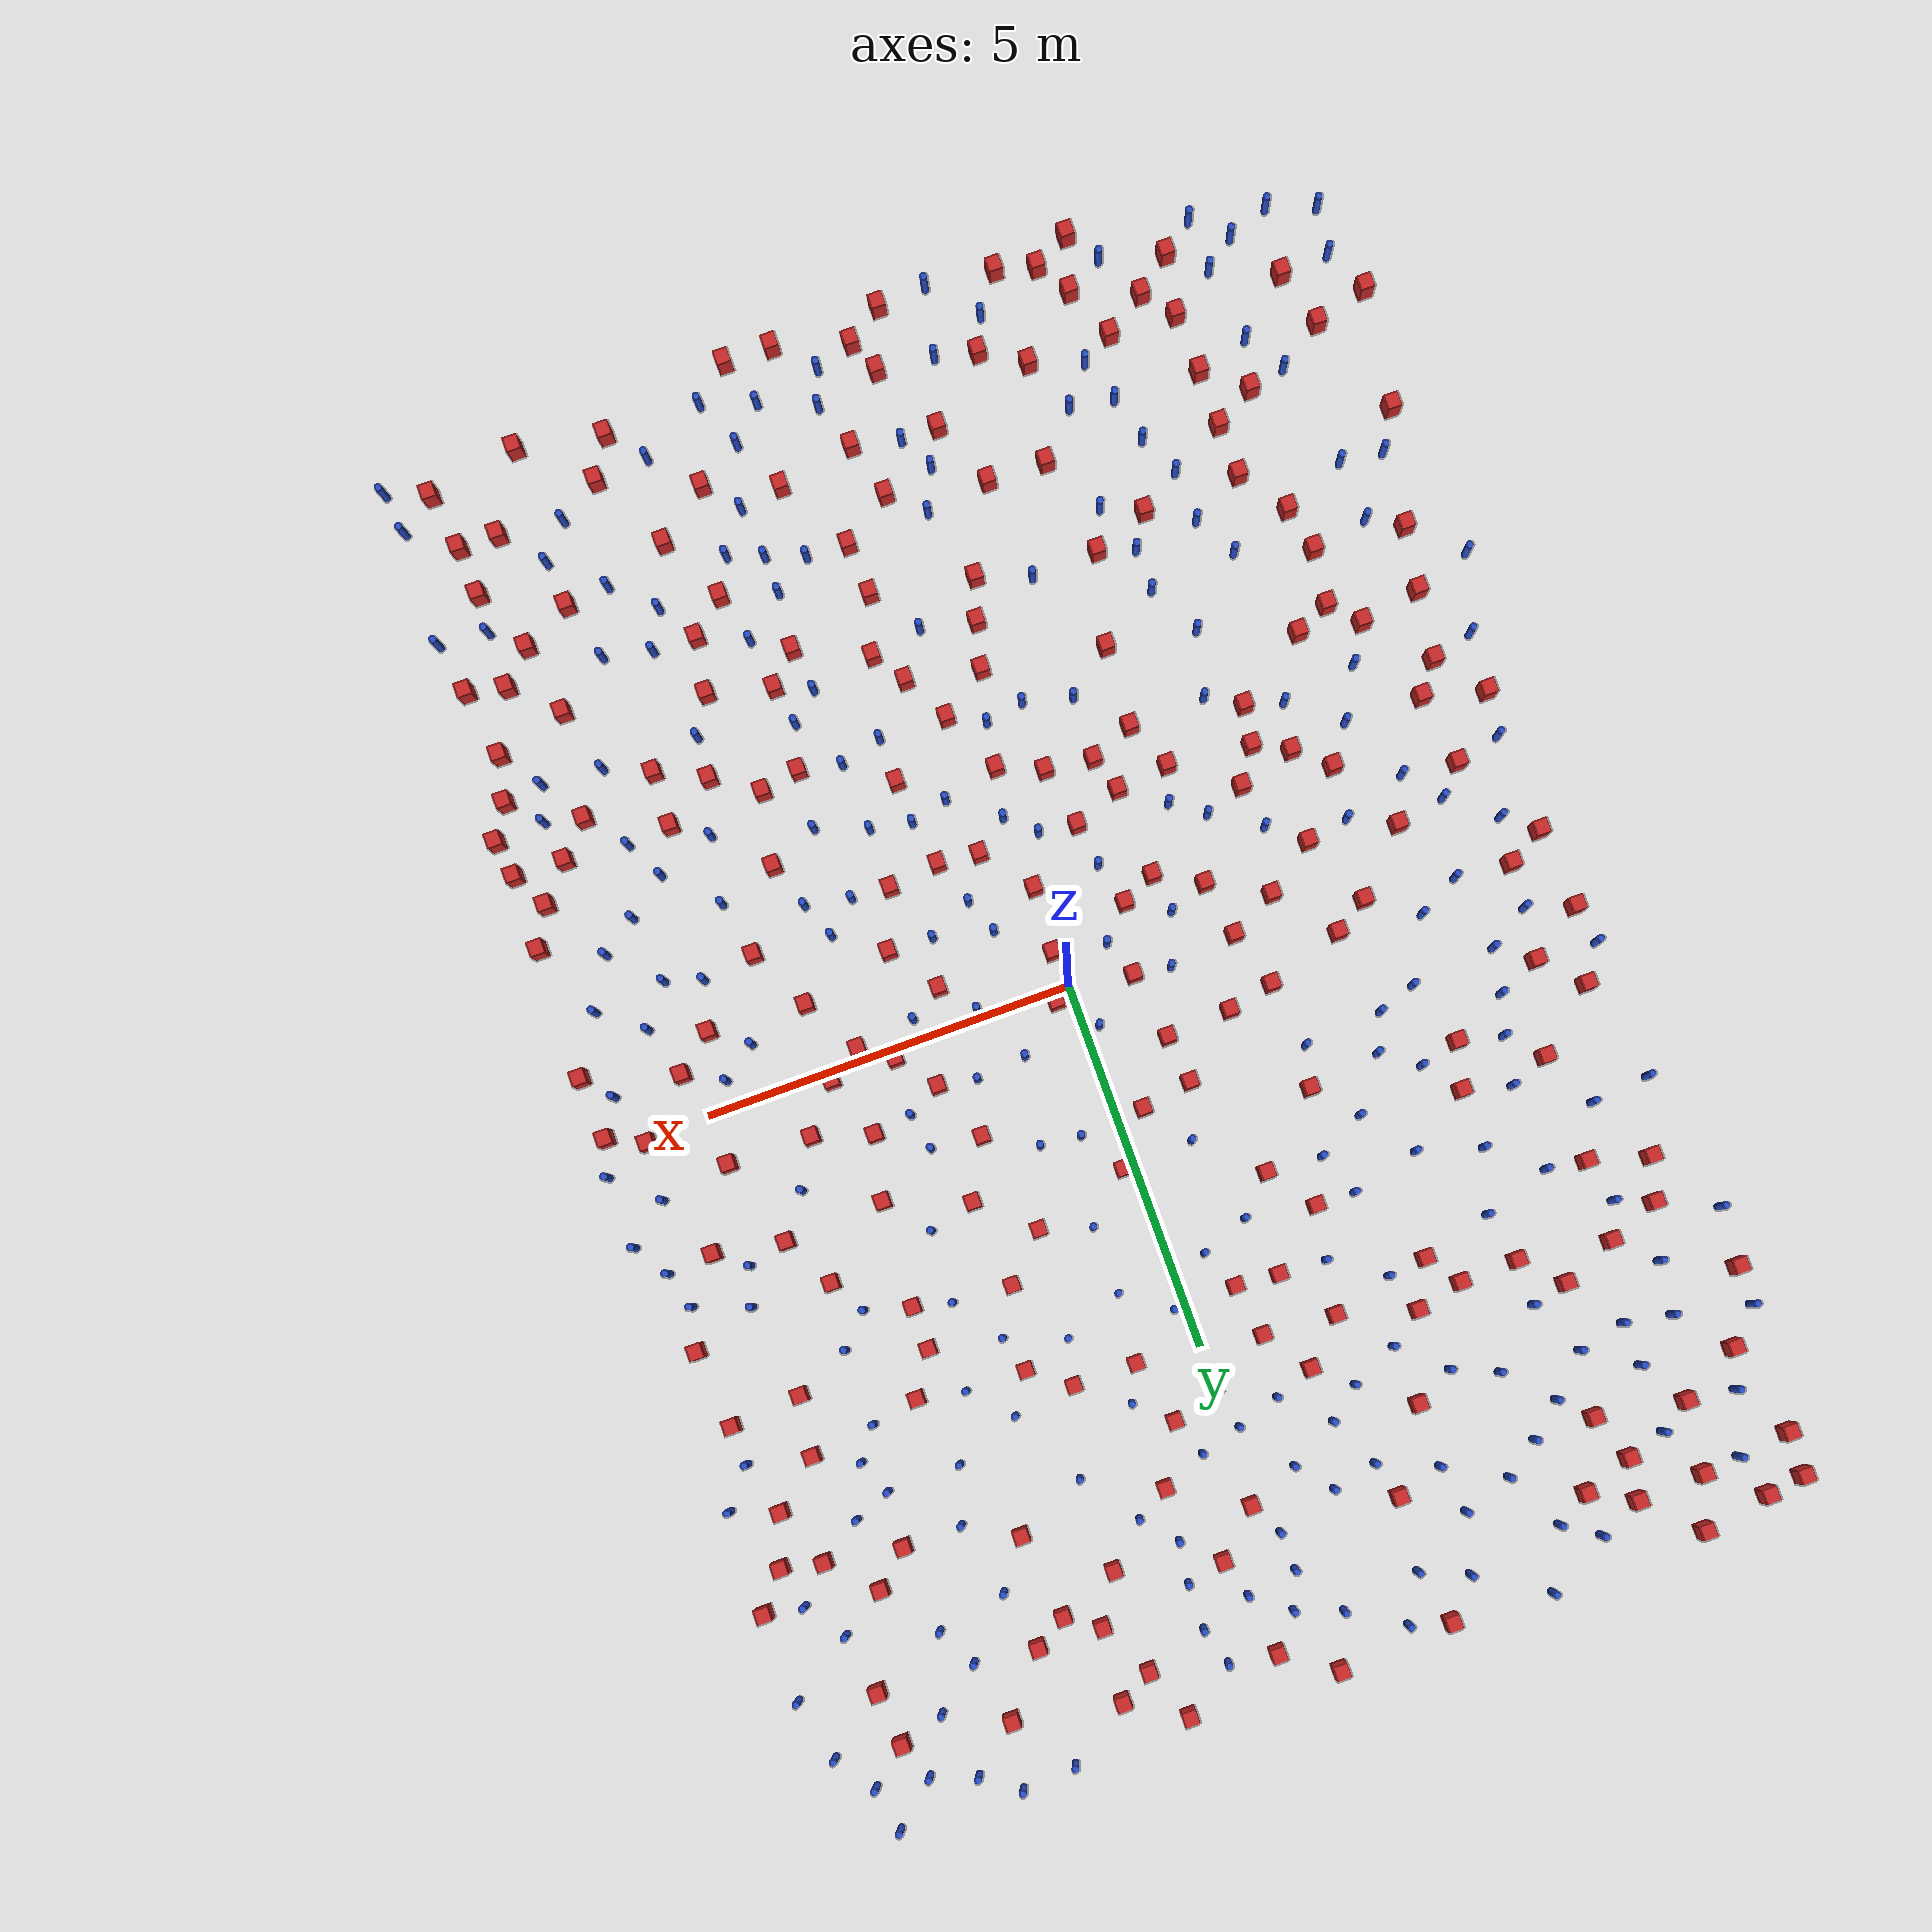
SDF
<sdf version="1.6">
  <model name="dense_76"><model name="pole_obstacle0">
  <static>true</static>
  <pose frame="">0.0405761902183 8.55352330351 -9.47619616065e-06 5.49618799737e-07 2.36310414033e-07 -1.55090534817e-07</pose>
  <link name="link">
  <pose frame="">0 0 0.3 0 -0 0</pose>
    <inertial>
      <mass>1</mass>
      <inertia>
        <ixx>0.145833</ixx>
        <ixy>0</ixy>
        <ixz>0</ixz>
        <iyy>0.145833</iyy>
        <iyz>0</iyz>
        <izz>0.125</izz>
      </inertia>
    </inertial>
    <collision name="collision">
      <geometry>
        <cylinder>
          <radius>0.05</radius>
          <length>.6</length>
        </cylinder>
      </geometry>
      <max_contacts>10</max_contacts>
      <surface>
        <contact>
          <ode/>
        </contact>
        <bounce/>
        <friction>
          <torsional>
            <ode/>
          </torsional>
          <ode/>
        </friction>
      </surface>
    </collision>
    <visual name="visual">
      <geometry>
        <cylinder>
          <radius>0.05</radius>
          <length>.6</length>
        </cylinder>
      </geometry>
      <material>
        <script>
          <name>Gazebo/Blue</name>
          <uri>file://media/materials/scripts/gazebo.material</uri>
        </script>
      </material>
    </visual>
    <self_collide>0</self_collide>
    <kinematic>0</kinematic>
  </link>
</model>
<model name="pole_obstacle1">
  <static>true</static>
  <pose frame="">-3.19911717233 -3.85749164379 -9.47619616065e-06 5.49618799737e-07 2.36310414067e-07 -1.55090534797e-07</pose>
  <link name="link">
  <pose frame="">0 0 0.3 0 -0 0</pose>
    <inertial>
      <mass>1</mass>
      <inertia>
        <ixx>0.145833</ixx>
        <ixy>0</ixy>
        <ixz>0</ixz>
        <iyy>0.145833</iyy>
        <iyz>0</iyz>
        <izz>0.125</izz>
      </inertia>
    </inertial>
    <collision name="collision">
      <geometry>
        <cylinder>
          <radius>0.05</radius>
          <length>.6</length>
        </cylinder>
      </geometry>
      <max_contacts>10</max_contacts>
      <surface>
        <contact>
          <ode/>
        </contact>
        <bounce/>
        <friction>
          <torsional>
            <ode/>
          </torsional>
          <ode/>
        </friction>
      </surface>
    </collision>
    <visual name="visual">
      <geometry>
        <cylinder>
          <radius>0.05</radius>
          <length>.6</length>
        </cylinder>
      </geometry>
      <material>
        <script>
          <name>Gazebo/Blue</name>
          <uri>file://media/materials/scripts/gazebo.material</uri>
        </script>
      </material>
    </visual>
    <self_collide>0</self_collide>
    <kinematic>0</kinematic>
  </link>
</model>
<model name="square_post_obstacle0">
  <static>true</static>
  <pose frame="">0.944305064648 -4.99120115304 -6.11067671241e-07 -5.50515727128e-06 -8.79689657224e-07 2.37013304536e-05</pose>
  <link name="link">
    <pose frame="">0 0 0.25 0 -0 0</pose>
    <inertial>
      <mass>100</mass>
      <inertia>
        <ixx>0.166667</ixx>
        <ixy>0</ixy>
        <ixz>0</ixz>
        <iyy>0.166667</iyy>
        <iyz>0</iyz>
        <izz>0.166667</izz>
      </inertia>
    </inertial>
    <collision name="collision">
      <geometry>
        <box>
          <size>.2 .2 .5</size>
        </box>
      </geometry>
      <max_contacts>10</max_contacts>
      <surface>
        <contact>
          <ode/>
        </contact>
        <bounce/>
        <friction>
          <torsional>
            <ode/>
          </torsional>
          <ode/>
        </friction>
      </surface>
    </collision>
    <visual name="visual">
      <geometry>
        <box>
          <size>.2 .2 .5</size>
        </box>
      </geometry>
      <material>
        <script>
          <name>Gazebo/Red</name>
          <uri>file://media/materials/scripts/gazebo.material</uri>
        </script>
      </material>
    </visual>
    <self_collide>0</self_collide>
    <kinematic>0</kinematic>
  </link>
</model>
<model name="square_post_obstacle1">
  <static>true</static>
  <pose frame="">2.3046732225 -7.91956817169 -6.11067671241e-07 -5.50515727128e-06 -8.79689657224e-07 2.37013304536e-05</pose>
  <link name="link">
    <pose frame="">0 0 0.25 0 -0 0</pose>
    <inertial>
      <mass>100</mass>
      <inertia>
        <ixx>0.166667</ixx>
        <ixy>0</ixy>
        <ixz>0</ixz>
        <iyy>0.166667</iyy>
        <iyz>0</iyz>
        <izz>0.166667</izz>
      </inertia>
    </inertial>
    <collision name="collision">
      <geometry>
        <box>
          <size>.2 .2 .5</size>
        </box>
      </geometry>
      <max_contacts>10</max_contacts>
      <surface>
        <contact>
          <ode/>
        </contact>
        <bounce/>
        <friction>
          <torsional>
            <ode/>
          </torsional>
          <ode/>
        </friction>
      </surface>
    </collision>
    <visual name="visual">
      <geometry>
        <box>
          <size>.2 .2 .5</size>
        </box>
      </geometry>
      <material>
        <script>
          <name>Gazebo/Red</name>
          <uri>file://media/materials/scripts/gazebo.material</uri>
        </script>
      </material>
    </visual>
    <self_collide>0</self_collide>
    <kinematic>0</kinematic>
  </link>
</model>
<model name="pole_obstacle2">
  <static>true</static>
  <pose frame="">-1.27373937846 6.47451242145 -9.47619616065e-06 5.49618799737e-07 2.36310414061e-07 -1.550905348e-07</pose>
  <link name="link">
  <pose frame="">0 0 0.3 0 -0 0</pose>
    <inertial>
      <mass>1</mass>
      <inertia>
        <ixx>0.145833</ixx>
        <ixy>0</ixy>
        <ixz>0</ixz>
        <iyy>0.145833</iyy>
        <iyz>0</iyz>
        <izz>0.125</izz>
      </inertia>
    </inertial>
    <collision name="collision">
      <geometry>
        <cylinder>
          <radius>0.05</radius>
          <length>.6</length>
        </cylinder>
      </geometry>
      <max_contacts>10</max_contacts>
      <surface>
        <contact>
          <ode/>
        </contact>
        <bounce/>
        <friction>
          <torsional>
            <ode/>
          </torsional>
          <ode/>
        </friction>
      </surface>
    </collision>
    <visual name="visual">
      <geometry>
        <cylinder>
          <radius>0.05</radius>
          <length>.6</length>
        </cylinder>
      </geometry>
      <material>
        <script>
          <name>Gazebo/Blue</name>
          <uri>file://media/materials/scripts/gazebo.material</uri>
        </script>
      </material>
    </visual>
    <self_collide>0</self_collide>
    <kinematic>0</kinematic>
  </link>
</model>
<model name="pole_obstacle3">
  <static>true</static>
  <pose frame="">4.53063861416 9.14221263747 -9.47619616065e-06 5.49618799737e-07 2.36310414065e-07 -1.55090534796e-07</pose>
  <link name="link">
  <pose frame="">0 0 0.3 0 -0 0</pose>
    <inertial>
      <mass>1</mass>
      <inertia>
        <ixx>0.145833</ixx>
        <ixy>0</ixy>
        <ixz>0</ixz>
        <iyy>0.145833</iyy>
        <iyz>0</iyz>
        <izz>0.125</izz>
      </inertia>
    </inertial>
    <collision name="collision">
      <geometry>
        <cylinder>
          <radius>0.05</radius>
          <length>.6</length>
        </cylinder>
      </geometry>
      <max_contacts>10</max_contacts>
      <surface>
        <contact>
          <ode/>
        </contact>
        <bounce/>
        <friction>
          <torsional>
            <ode/>
          </torsional>
          <ode/>
        </friction>
      </surface>
    </collision>
    <visual name="visual">
      <geometry>
        <cylinder>
          <radius>0.05</radius>
          <length>.6</length>
        </cylinder>
      </geometry>
      <material>
        <script>
          <name>Gazebo/Blue</name>
          <uri>file://media/materials/scripts/gazebo.material</uri>
        </script>
      </material>
    </visual>
    <self_collide>0</self_collide>
    <kinematic>0</kinematic>
  </link>
</model>
<model name="pole_obstacle4">
  <static>true</static>
  <pose frame="">1.67797747055 -8.28879280093 -9.47619616065e-06 5.49618799737e-07 2.36310414046e-07 -1.55090534809e-07</pose>
  <link name="link">
  <pose frame="">0 0 0.3 0 -0 0</pose>
    <inertial>
      <mass>1</mass>
      <inertia>
        <ixx>0.145833</ixx>
        <ixy>0</ixy>
        <ixz>0</ixz>
        <iyy>0.145833</iyy>
        <iyz>0</iyz>
        <izz>0.125</izz>
      </inertia>
    </inertial>
    <collision name="collision">
      <geometry>
        <cylinder>
          <radius>0.05</radius>
          <length>.6</length>
        </cylinder>
      </geometry>
      <max_contacts>10</max_contacts>
      <surface>
        <contact>
          <ode/>
        </contact>
        <bounce/>
        <friction>
          <torsional>
            <ode/>
          </torsional>
          <ode/>
        </friction>
      </surface>
    </collision>
    <visual name="visual">
      <geometry>
        <cylinder>
          <radius>0.05</radius>
          <length>.6</length>
        </cylinder>
      </geometry>
      <material>
        <script>
          <name>Gazebo/Blue</name>
          <uri>file://media/materials/scripts/gazebo.material</uri>
        </script>
      </material>
    </visual>
    <self_collide>0</self_collide>
    <kinematic>0</kinematic>
  </link>
</model>
<model name="pole_obstacle5">
  <static>true</static>
  <pose frame="">4.95172508571 -1.85118535402 -9.47619616065e-06 5.49618799738e-07 2.36310414071e-07 -1.55090534796e-07</pose>
  <link name="link">
  <pose frame="">0 0 0.3 0 -0 0</pose>
    <inertial>
      <mass>1</mass>
      <inertia>
        <ixx>0.145833</ixx>
        <ixy>0</ixy>
        <ixz>0</ixz>
        <iyy>0.145833</iyy>
        <iyz>0</iyz>
        <izz>0.125</izz>
      </inertia>
    </inertial>
    <collision name="collision">
      <geometry>
        <cylinder>
          <radius>0.05</radius>
          <length>.6</length>
        </cylinder>
      </geometry>
      <max_contacts>10</max_contacts>
      <surface>
        <contact>
          <ode/>
        </contact>
        <bounce/>
        <friction>
          <torsional>
            <ode/>
          </torsional>
          <ode/>
        </friction>
      </surface>
    </collision>
    <visual name="visual">
      <geometry>
        <cylinder>
          <radius>0.05</radius>
          <length>.6</length>
        </cylinder>
      </geometry>
      <material>
        <script>
          <name>Gazebo/Blue</name>
          <uri>file://media/materials/scripts/gazebo.material</uri>
        </script>
      </material>
    </visual>
    <self_collide>0</self_collide>
    <kinematic>0</kinematic>
  </link>
</model>
<model name="pole_obstacle6">
  <static>true</static>
  <pose frame="">-5.10376092105 2.55919030713 -9.47619616065e-06 5.49618799738e-07 2.36310414051e-07 -1.55090534805e-07</pose>
  <link name="link">
  <pose frame="">0 0 0.3 0 -0 0</pose>
    <inertial>
      <mass>1</mass>
      <inertia>
        <ixx>0.145833</ixx>
        <ixy>0</ixy>
        <ixz>0</ixz>
        <iyy>0.145833</iyy>
        <iyz>0</iyz>
        <izz>0.125</izz>
      </inertia>
    </inertial>
    <collision name="collision">
      <geometry>
        <cylinder>
          <radius>0.05</radius>
          <length>.6</length>
        </cylinder>
      </geometry>
      <max_contacts>10</max_contacts>
      <surface>
        <contact>
          <ode/>
        </contact>
        <bounce/>
        <friction>
          <torsional>
            <ode/>
          </torsional>
          <ode/>
        </friction>
      </surface>
    </collision>
    <visual name="visual">
      <geometry>
        <cylinder>
          <radius>0.05</radius>
          <length>.6</length>
        </cylinder>
      </geometry>
      <material>
        <script>
          <name>Gazebo/Blue</name>
          <uri>file://media/materials/scripts/gazebo.material</uri>
        </script>
      </material>
    </visual>
    <self_collide>0</self_collide>
    <kinematic>0</kinematic>
  </link>
</model>
<model name="square_post_obstacle2">
  <static>true</static>
  <pose frame="">5.52280891063 1.71290231488 -6.11067671241e-07 -5.50515727128e-06 -8.79689657224e-07 2.37013304536e-05</pose>
  <link name="link">
    <pose frame="">0 0 0.25 0 -0 0</pose>
    <inertial>
      <mass>100</mass>
      <inertia>
        <ixx>0.166667</ixx>
        <ixy>0</ixy>
        <ixz>0</ixz>
        <iyy>0.166667</iyy>
        <iyz>0</iyz>
        <izz>0.166667</izz>
      </inertia>
    </inertial>
    <collision name="collision">
      <geometry>
        <box>
          <size>.2 .2 .5</size>
        </box>
      </geometry>
      <max_contacts>10</max_contacts>
      <surface>
        <contact>
          <ode/>
        </contact>
        <bounce/>
        <friction>
          <torsional>
            <ode/>
          </torsional>
          <ode/>
        </friction>
      </surface>
    </collision>
    <visual name="visual">
      <geometry>
        <box>
          <size>.2 .2 .5</size>
        </box>
      </geometry>
      <material>
        <script>
          <name>Gazebo/Red</name>
          <uri>file://media/materials/scripts/gazebo.material</uri>
        </script>
      </material>
    </visual>
    <self_collide>0</self_collide>
    <kinematic>0</kinematic>
  </link>
</model>
<model name="square_post_obstacle3">
  <static>true</static>
  <pose frame="">2.48934977216 8.89152247828 -6.11067671241e-07 -5.50515727128e-06 -8.79689657224e-07 2.37013304536e-05</pose>
  <link name="link">
    <pose frame="">0 0 0.25 0 -0 0</pose>
    <inertial>
      <mass>100</mass>
      <inertia>
        <ixx>0.166667</ixx>
        <ixy>0</ixy>
        <ixz>0</ixz>
        <iyy>0.166667</iyy>
        <iyz>0</iyz>
        <izz>0.166667</izz>
      </inertia>
    </inertial>
    <collision name="collision">
      <geometry>
        <box>
          <size>.2 .2 .5</size>
        </box>
      </geometry>
      <max_contacts>10</max_contacts>
      <surface>
        <contact>
          <ode/>
        </contact>
        <bounce/>
        <friction>
          <torsional>
            <ode/>
          </torsional>
          <ode/>
        </friction>
      </surface>
    </collision>
    <visual name="visual">
      <geometry>
        <box>
          <size>.2 .2 .5</size>
        </box>
      </geometry>
      <material>
        <script>
          <name>Gazebo/Red</name>
          <uri>file://media/materials/scripts/gazebo.material</uri>
        </script>
      </material>
    </visual>
    <self_collide>0</self_collide>
    <kinematic>0</kinematic>
  </link>
</model>
<model name="square_post_obstacle4">
  <static>true</static>
  <pose frame="">2.0309213885 7.29000807328 -6.11067671241e-07 -5.50515727128e-06 -8.79689657224e-07 2.37013304536e-05</pose>
  <link name="link">
    <pose frame="">0 0 0.25 0 -0 0</pose>
    <inertial>
      <mass>100</mass>
      <inertia>
        <ixx>0.166667</ixx>
        <ixy>0</ixy>
        <ixz>0</ixz>
        <iyy>0.166667</iyy>
        <iyz>0</iyz>
        <izz>0.166667</izz>
      </inertia>
    </inertial>
    <collision name="collision">
      <geometry>
        <box>
          <size>.2 .2 .5</size>
        </box>
      </geometry>
      <max_contacts>10</max_contacts>
      <surface>
        <contact>
          <ode/>
        </contact>
        <bounce/>
        <friction>
          <torsional>
            <ode/>
          </torsional>
          <ode/>
        </friction>
      </surface>
    </collision>
    <visual name="visual">
      <geometry>
        <box>
          <size>.2 .2 .5</size>
        </box>
      </geometry>
      <material>
        <script>
          <name>Gazebo/Red</name>
          <uri>file://media/materials/scripts/gazebo.material</uri>
        </script>
      </material>
    </visual>
    <self_collide>0</self_collide>
    <kinematic>0</kinematic>
  </link>
</model>
<model name="pole_obstacle7">
  <static>true</static>
  <pose frame="">-5.00055378148 4.37309625407 -9.47619616065e-06 5.49618799737e-07 2.36310414037e-07 -1.55090534814e-07</pose>
  <link name="link">
  <pose frame="">0 0 0.3 0 -0 0</pose>
    <inertial>
      <mass>1</mass>
      <inertia>
        <ixx>0.145833</ixx>
        <ixy>0</ixy>
        <ixz>0</ixz>
        <iyy>0.145833</iyy>
        <iyz>0</iyz>
        <izz>0.125</izz>
      </inertia>
    </inertial>
    <collision name="collision">
      <geometry>
        <cylinder>
          <radius>0.05</radius>
          <length>.6</length>
        </cylinder>
      </geometry>
      <max_contacts>10</max_contacts>
      <surface>
        <contact>
          <ode/>
        </contact>
        <bounce/>
        <friction>
          <torsional>
            <ode/>
          </torsional>
          <ode/>
        </friction>
      </surface>
    </collision>
    <visual name="visual">
      <geometry>
        <cylinder>
          <radius>0.05</radius>
          <length>.6</length>
        </cylinder>
      </geometry>
      <material>
        <script>
          <name>Gazebo/Blue</name>
          <uri>file://media/materials/scripts/gazebo.material</uri>
        </script>
      </material>
    </visual>
    <self_collide>0</self_collide>
    <kinematic>0</kinematic>
  </link>
</model>
<model name="pole_obstacle8">
  <static>true</static>
  <pose frame="">-5.01428291551 -9.12350904369 -9.47619616065e-06 5.49618799737e-07 2.36310414065e-07 -1.55090534796e-07</pose>
  <link name="link">
  <pose frame="">0 0 0.3 0 -0 0</pose>
    <inertial>
      <mass>1</mass>
      <inertia>
        <ixx>0.145833</ixx>
        <ixy>0</ixy>
        <ixz>0</ixz>
        <iyy>0.145833</iyy>
        <iyz>0</iyz>
        <izz>0.125</izz>
      </inertia>
    </inertial>
    <collision name="collision">
      <geometry>
        <cylinder>
          <radius>0.05</radius>
          <length>.6</length>
        </cylinder>
      </geometry>
      <max_contacts>10</max_contacts>
      <surface>
        <contact>
          <ode/>
        </contact>
        <bounce/>
        <friction>
          <torsional>
            <ode/>
          </torsional>
          <ode/>
        </friction>
      </surface>
    </collision>
    <visual name="visual">
      <geometry>
        <cylinder>
          <radius>0.05</radius>
          <length>.6</length>
        </cylinder>
      </geometry>
      <material>
        <script>
          <name>Gazebo/Blue</name>
          <uri>file://media/materials/scripts/gazebo.material</uri>
        </script>
      </material>
    </visual>
    <self_collide>0</self_collide>
    <kinematic>0</kinematic>
  </link>
</model>
<model name="square_post_obstacle5">
  <static>true</static>
  <pose frame="">-4.4312994662 -7.13340059479 -6.11067671241e-07 -5.50515727128e-06 -8.79689657224e-07 2.37013304536e-05</pose>
  <link name="link">
    <pose frame="">0 0 0.25 0 -0 0</pose>
    <inertial>
      <mass>100</mass>
      <inertia>
        <ixx>0.166667</ixx>
        <ixy>0</ixy>
        <ixz>0</ixz>
        <iyy>0.166667</iyy>
        <iyz>0</iyz>
        <izz>0.166667</izz>
      </inertia>
    </inertial>
    <collision name="collision">
      <geometry>
        <box>
          <size>.2 .2 .5</size>
        </box>
      </geometry>
      <max_contacts>10</max_contacts>
      <surface>
        <contact>
          <ode/>
        </contact>
        <bounce/>
        <friction>
          <torsional>
            <ode/>
          </torsional>
          <ode/>
        </friction>
      </surface>
    </collision>
    <visual name="visual">
      <geometry>
        <box>
          <size>.2 .2 .5</size>
        </box>
      </geometry>
      <material>
        <script>
          <name>Gazebo/Red</name>
          <uri>file://media/materials/scripts/gazebo.material</uri>
        </script>
      </material>
    </visual>
    <self_collide>0</self_collide>
    <kinematic>0</kinematic>
  </link>
</model>
<model name="square_post_obstacle6">
  <static>true</static>
  <pose frame="">4.57847857241 1.88806926313 -6.11067671241e-07 -5.50515727128e-06 -8.79689657224e-07 2.37013304536e-05</pose>
  <link name="link">
    <pose frame="">0 0 0.25 0 -0 0</pose>
    <inertial>
      <mass>100</mass>
      <inertia>
        <ixx>0.166667</ixx>
        <ixy>0</ixy>
        <ixz>0</ixz>
        <iyy>0.166667</iyy>
        <iyz>0</iyz>
        <izz>0.166667</izz>
      </inertia>
    </inertial>
    <collision name="collision">
      <geometry>
        <box>
          <size>.2 .2 .5</size>
        </box>
      </geometry>
      <max_contacts>10</max_contacts>
      <surface>
        <contact>
          <ode/>
        </contact>
        <bounce/>
        <friction>
          <torsional>
            <ode/>
          </torsional>
          <ode/>
        </friction>
      </surface>
    </collision>
    <visual name="visual">
      <geometry>
        <box>
          <size>.2 .2 .5</size>
        </box>
      </geometry>
      <material>
        <script>
          <name>Gazebo/Red</name>
          <uri>file://media/materials/scripts/gazebo.material</uri>
        </script>
      </material>
    </visual>
    <self_collide>0</self_collide>
    <kinematic>0</kinematic>
  </link>
</model>
<model name="square_post_obstacle7">
  <static>true</static>
  <pose frame="">3.60023916208 -8.46336494209 -6.11067671241e-07 -5.50515727128e-06 -8.79689657224e-07 2.37013304536e-05</pose>
  <link name="link">
    <pose frame="">0 0 0.25 0 -0 0</pose>
    <inertial>
      <mass>100</mass>
      <inertia>
        <ixx>0.166667</ixx>
        <ixy>0</ixy>
        <ixz>0</ixz>
        <iyy>0.166667</iyy>
        <iyz>0</iyz>
        <izz>0.166667</izz>
      </inertia>
    </inertial>
    <collision name="collision">
      <geometry>
        <box>
          <size>.2 .2 .5</size>
        </box>
      </geometry>
      <max_contacts>10</max_contacts>
      <surface>
        <contact>
          <ode/>
        </contact>
        <bounce/>
        <friction>
          <torsional>
            <ode/>
          </torsional>
          <ode/>
        </friction>
      </surface>
    </collision>
    <visual name="visual">
      <geometry>
        <box>
          <size>.2 .2 .5</size>
        </box>
      </geometry>
      <material>
        <script>
          <name>Gazebo/Red</name>
          <uri>file://media/materials/scripts/gazebo.material</uri>
        </script>
      </material>
    </visual>
    <self_collide>0</self_collide>
    <kinematic>0</kinematic>
  </link>
</model>
<model name="pole_obstacle9">
  <static>true</static>
  <pose frame="">4.38289889013 7.25559182858 -9.47619616065e-06 5.49618799737e-07 2.36310414037e-07 -1.55090534814e-07</pose>
  <link name="link">
  <pose frame="">0 0 0.3 0 -0 0</pose>
    <inertial>
      <mass>1</mass>
      <inertia>
        <ixx>0.145833</ixx>
        <ixy>0</ixy>
        <ixz>0</ixz>
        <iyy>0.145833</iyy>
        <iyz>0</iyz>
        <izz>0.125</izz>
      </inertia>
    </inertial>
    <collision name="collision">
      <geometry>
        <cylinder>
          <radius>0.05</radius>
          <length>.6</length>
        </cylinder>
      </geometry>
      <max_contacts>10</max_contacts>
      <surface>
        <contact>
          <ode/>
        </contact>
        <bounce/>
        <friction>
          <torsional>
            <ode/>
          </torsional>
          <ode/>
        </friction>
      </surface>
    </collision>
    <visual name="visual">
      <geometry>
        <cylinder>
          <radius>0.05</radius>
          <length>.6</length>
        </cylinder>
      </geometry>
      <material>
        <script>
          <name>Gazebo/Blue</name>
          <uri>file://media/materials/scripts/gazebo.material</uri>
        </script>
      </material>
    </visual>
    <self_collide>0</self_collide>
    <kinematic>0</kinematic>
  </link>
</model>
<model name="pole_obstacle10">
  <static>true</static>
  <pose frame="">1.45750841201 -1.19569166545 -9.47619616065e-06 5.49618799737e-07 2.36310414065e-07 -1.55090534798e-07</pose>
  <link name="link">
  <pose frame="">0 0 0.3 0 -0 0</pose>
    <inertial>
      <mass>1</mass>
      <inertia>
        <ixx>0.145833</ixx>
        <ixy>0</ixy>
        <ixz>0</ixz>
        <iyy>0.145833</iyy>
        <iyz>0</iyz>
        <izz>0.125</izz>
      </inertia>
    </inertial>
    <collision name="collision">
      <geometry>
        <cylinder>
          <radius>0.05</radius>
          <length>.6</length>
        </cylinder>
      </geometry>
      <max_contacts>10</max_contacts>
      <surface>
        <contact>
          <ode/>
        </contact>
        <bounce/>
        <friction>
          <torsional>
            <ode/>
          </torsional>
          <ode/>
        </friction>
      </surface>
    </collision>
    <visual name="visual">
      <geometry>
        <cylinder>
          <radius>0.05</radius>
          <length>.6</length>
        </cylinder>
      </geometry>
      <material>
        <script>
          <name>Gazebo/Blue</name>
          <uri>file://media/materials/scripts/gazebo.material</uri>
        </script>
      </material>
    </visual>
    <self_collide>0</self_collide>
    <kinematic>0</kinematic>
  </link>
</model>
<model name="pole_obstacle11">
  <static>true</static>
  <pose frame="">3.64021856873 -6.03391371396 -9.47619616065e-06 5.49618799738e-07 2.3631041406e-07 -1.55090534801e-07</pose>
  <link name="link">
  <pose frame="">0 0 0.3 0 -0 0</pose>
    <inertial>
      <mass>1</mass>
      <inertia>
        <ixx>0.145833</ixx>
        <ixy>0</ixy>
        <ixz>0</ixz>
        <iyy>0.145833</iyy>
        <iyz>0</iyz>
        <izz>0.125</izz>
      </inertia>
    </inertial>
    <collision name="collision">
      <geometry>
        <cylinder>
          <radius>0.05</radius>
          <length>.6</length>
        </cylinder>
      </geometry>
      <max_contacts>10</max_contacts>
      <surface>
        <contact>
          <ode/>
        </contact>
        <bounce/>
        <friction>
          <torsional>
            <ode/>
          </torsional>
          <ode/>
        </friction>
      </surface>
    </collision>
    <visual name="visual">
      <geometry>
        <cylinder>
          <radius>0.05</radius>
          <length>.6</length>
        </cylinder>
      </geometry>
      <material>
        <script>
          <name>Gazebo/Blue</name>
          <uri>file://media/materials/scripts/gazebo.material</uri>
        </script>
      </material>
    </visual>
    <self_collide>0</self_collide>
    <kinematic>0</kinematic>
  </link>
</model>
<model name="pole_obstacle12">
  <static>true</static>
  <pose frame="">4.16618906073 1.33775884819 -9.47619616065e-06 5.49618799738e-07 2.36310414071e-07 -1.55090534796e-07</pose>
  <link name="link">
  <pose frame="">0 0 0.3 0 -0 0</pose>
    <inertial>
      <mass>1</mass>
      <inertia>
        <ixx>0.145833</ixx>
        <ixy>0</ixy>
        <ixz>0</ixz>
        <iyy>0.145833</iyy>
        <iyz>0</iyz>
        <izz>0.125</izz>
      </inertia>
    </inertial>
    <collision name="collision">
      <geometry>
        <cylinder>
          <radius>0.05</radius>
          <length>.6</length>
        </cylinder>
      </geometry>
      <max_contacts>10</max_contacts>
      <surface>
        <contact>
          <ode/>
        </contact>
        <bounce/>
        <friction>
          <torsional>
            <ode/>
          </torsional>
          <ode/>
        </friction>
      </surface>
    </collision>
    <visual name="visual">
      <geometry>
        <cylinder>
          <radius>0.05</radius>
          <length>.6</length>
        </cylinder>
      </geometry>
      <material>
        <script>
          <name>Gazebo/Blue</name>
          <uri>file://media/materials/scripts/gazebo.material</uri>
        </script>
      </material>
    </visual>
    <self_collide>0</self_collide>
    <kinematic>0</kinematic>
  </link>
</model>
<model name="square_post_obstacle8">
  <static>true</static>
  <pose frame="">-0.903577958004 -7.60333633524 -6.11067671241e-07 -5.50515727128e-06 -8.79689657224e-07 2.37013304536e-05</pose>
  <link name="link">
    <pose frame="">0 0 0.25 0 -0 0</pose>
    <inertial>
      <mass>100</mass>
      <inertia>
        <ixx>0.166667</ixx>
        <ixy>0</ixy>
        <ixz>0</ixz>
        <iyy>0.166667</iyy>
        <iyz>0</iyz>
        <izz>0.166667</izz>
      </inertia>
    </inertial>
    <collision name="collision">
      <geometry>
        <box>
          <size>.2 .2 .5</size>
        </box>
      </geometry>
      <max_contacts>10</max_contacts>
      <surface>
        <contact>
          <ode/>
        </contact>
        <bounce/>
        <friction>
          <torsional>
            <ode/>
          </torsional>
          <ode/>
        </friction>
      </surface>
    </collision>
    <visual name="visual">
      <geometry>
        <box>
          <size>.2 .2 .5</size>
        </box>
      </geometry>
      <material>
        <script>
          <name>Gazebo/Red</name>
          <uri>file://media/materials/scripts/gazebo.material</uri>
        </script>
      </material>
    </visual>
    <self_collide>0</self_collide>
    <kinematic>0</kinematic>
  </link>
</model>
<model name="square_post_obstacle9">
  <static>true</static>
  <pose frame="">5.59965612481 -8.22088846816 -6.11067671241e-07 -5.50515727128e-06 -8.79689657224e-07 2.37013304536e-05</pose>
  <link name="link">
    <pose frame="">0 0 0.25 0 -0 0</pose>
    <inertial>
      <mass>100</mass>
      <inertia>
        <ixx>0.166667</ixx>
        <ixy>0</ixy>
        <ixz>0</ixz>
        <iyy>0.166667</iyy>
        <iyz>0</iyz>
        <izz>0.166667</izz>
      </inertia>
    </inertial>
    <collision name="collision">
      <geometry>
        <box>
          <size>.2 .2 .5</size>
        </box>
      </geometry>
      <max_contacts>10</max_contacts>
      <surface>
        <contact>
          <ode/>
        </contact>
        <bounce/>
        <friction>
          <torsional>
            <ode/>
          </torsional>
          <ode/>
        </friction>
      </surface>
    </collision>
    <visual name="visual">
      <geometry>
        <box>
          <size>.2 .2 .5</size>
        </box>
      </geometry>
      <material>
        <script>
          <name>Gazebo/Red</name>
          <uri>file://media/materials/scripts/gazebo.material</uri>
        </script>
      </material>
    </visual>
    <self_collide>0</self_collide>
    <kinematic>0</kinematic>
  </link>
</model>
<model name="pole_obstacle13">
  <static>true</static>
  <pose frame="">-5.23885158348 0.395496682585 -9.47619616065e-06 5.49618799737e-07 2.36310414057e-07 -1.55090534802e-07</pose>
  <link name="link">
  <pose frame="">0 0 0.3 0 -0 0</pose>
    <inertial>
      <mass>1</mass>
      <inertia>
        <ixx>0.145833</ixx>
        <ixy>0</ixy>
        <ixz>0</ixz>
        <iyy>0.145833</iyy>
        <iyz>0</iyz>
        <izz>0.125</izz>
      </inertia>
    </inertial>
    <collision name="collision">
      <geometry>
        <cylinder>
          <radius>0.05</radius>
          <length>.6</length>
        </cylinder>
      </geometry>
      <max_contacts>10</max_contacts>
      <surface>
        <contact>
          <ode/>
        </contact>
        <bounce/>
        <friction>
          <torsional>
            <ode/>
          </torsional>
          <ode/>
        </friction>
      </surface>
    </collision>
    <visual name="visual">
      <geometry>
        <cylinder>
          <radius>0.05</radius>
          <length>.6</length>
        </cylinder>
      </geometry>
      <material>
        <script>
          <name>Gazebo/Blue</name>
          <uri>file://media/materials/scripts/gazebo.material</uri>
        </script>
      </material>
    </visual>
    <self_collide>0</self_collide>
    <kinematic>0</kinematic>
  </link>
</model>
<model name="square_post_obstacle10">
  <static>true</static>
  <pose frame="">4.94972560376 0.686517332191 -6.11067671241e-07 -5.50515727128e-06 -8.79689657224e-07 2.37013304536e-05</pose>
  <link name="link">
    <pose frame="">0 0 0.25 0 -0 0</pose>
    <inertial>
      <mass>100</mass>
      <inertia>
        <ixx>0.166667</ixx>
        <ixy>0</ixy>
        <ixz>0</ixz>
        <iyy>0.166667</iyy>
        <iyz>0</iyz>
        <izz>0.166667</izz>
      </inertia>
    </inertial>
    <collision name="collision">
      <geometry>
        <box>
          <size>.2 .2 .5</size>
        </box>
      </geometry>
      <max_contacts>10</max_contacts>
      <surface>
        <contact>
          <ode/>
        </contact>
        <bounce/>
        <friction>
          <torsional>
            <ode/>
          </torsional>
          <ode/>
        </friction>
      </surface>
    </collision>
    <visual name="visual">
      <geometry>
        <box>
          <size>.2 .2 .5</size>
        </box>
      </geometry>
      <material>
        <script>
          <name>Gazebo/Red</name>
          <uri>file://media/materials/scripts/gazebo.material</uri>
        </script>
      </material>
    </visual>
    <self_collide>0</self_collide>
    <kinematic>0</kinematic>
  </link>
</model>
<model name="square_post_obstacle11">
  <static>true</static>
  <pose frame="">-1.24037410064 5.7349387828 -6.11067671241e-07 -5.50515727128e-06 -8.79689657224e-07 2.37013304536e-05</pose>
  <link name="link">
    <pose frame="">0 0 0.25 0 -0 0</pose>
    <inertial>
      <mass>100</mass>
      <inertia>
        <ixx>0.166667</ixx>
        <ixy>0</ixy>
        <ixz>0</ixz>
        <iyy>0.166667</iyy>
        <iyz>0</iyz>
        <izz>0.166667</izz>
      </inertia>
    </inertial>
    <collision name="collision">
      <geometry>
        <box>
          <size>.2 .2 .5</size>
        </box>
      </geometry>
      <max_contacts>10</max_contacts>
      <surface>
        <contact>
          <ode/>
        </contact>
        <bounce/>
        <friction>
          <torsional>
            <ode/>
          </torsional>
          <ode/>
        </friction>
      </surface>
    </collision>
    <visual name="visual">
      <geometry>
        <box>
          <size>.2 .2 .5</size>
        </box>
      </geometry>
      <material>
        <script>
          <name>Gazebo/Red</name>
          <uri>file://media/materials/scripts/gazebo.material</uri>
        </script>
      </material>
    </visual>
    <self_collide>0</self_collide>
    <kinematic>0</kinematic>
  </link>
</model>
<model name="pole_obstacle14">
  <static>true</static>
  <pose frame="">0.154008466186 4.43080157095 -9.47619616065e-06 5.49618799737e-07 2.36310414061e-07 -1.55090534801e-07</pose>
  <link name="link">
  <pose frame="">0 0 0.3 0 -0 0</pose>
    <inertial>
      <mass>1</mass>
      <inertia>
        <ixx>0.145833</ixx>
        <ixy>0</ixy>
        <ixz>0</ixz>
        <iyy>0.145833</iyy>
        <iyz>0</iyz>
        <izz>0.125</izz>
      </inertia>
    </inertial>
    <collision name="collision">
      <geometry>
        <cylinder>
          <radius>0.05</radius>
          <length>.6</length>
        </cylinder>
      </geometry>
      <max_contacts>10</max_contacts>
      <surface>
        <contact>
          <ode/>
        </contact>
        <bounce/>
        <friction>
          <torsional>
            <ode/>
          </torsional>
          <ode/>
        </friction>
      </surface>
    </collision>
    <visual name="visual">
      <geometry>
        <cylinder>
          <radius>0.05</radius>
          <length>.6</length>
        </cylinder>
      </geometry>
      <material>
        <script>
          <name>Gazebo/Blue</name>
          <uri>file://media/materials/scripts/gazebo.material</uri>
        </script>
      </material>
    </visual>
    <self_collide>0</self_collide>
    <kinematic>0</kinematic>
  </link>
</model>
<model name="pole_obstacle15">
  <static>true</static>
  <pose frame="">6.21537362861 -8.65453550145 -9.47619616065e-06 5.49618799737e-07 2.36310414065e-07 -1.55090534796e-07</pose>
  <link name="link">
  <pose frame="">0 0 0.3 0 -0 0</pose>
    <inertial>
      <mass>1</mass>
      <inertia>
        <ixx>0.145833</ixx>
        <ixy>0</ixy>
        <ixz>0</ixz>
        <iyy>0.145833</iyy>
        <iyz>0</iyz>
        <izz>0.125</izz>
      </inertia>
    </inertial>
    <collision name="collision">
      <geometry>
        <cylinder>
          <radius>0.05</radius>
          <length>.6</length>
        </cylinder>
      </geometry>
      <max_contacts>10</max_contacts>
      <surface>
        <contact>
          <ode/>
        </contact>
        <bounce/>
        <friction>
          <torsional>
            <ode/>
          </torsional>
          <ode/>
        </friction>
      </surface>
    </collision>
    <visual name="visual">
      <geometry>
        <cylinder>
          <radius>0.05</radius>
          <length>.6</length>
        </cylinder>
      </geometry>
      <material>
        <script>
          <name>Gazebo/Blue</name>
          <uri>file://media/materials/scripts/gazebo.material</uri>
        </script>
      </material>
    </visual>
    <self_collide>0</self_collide>
    <kinematic>0</kinematic>
  </link>
</model>
<model name="square_post_obstacle12">
  <static>true</static>
  <pose frame="">-4.01311779121 0.254424688509 -6.11067671241e-07 -5.50515727128e-06 -8.79689657224e-07 2.37013304536e-05</pose>
  <link name="link">
    <pose frame="">0 0 0.25 0 -0 0</pose>
    <inertial>
      <mass>100</mass>
      <inertia>
        <ixx>0.166667</ixx>
        <ixy>0</ixy>
        <ixz>0</ixz>
        <iyy>0.166667</iyy>
        <iyz>0</iyz>
        <izz>0.166667</izz>
      </inertia>
    </inertial>
    <collision name="collision">
      <geometry>
        <box>
          <size>.2 .2 .5</size>
        </box>
      </geometry>
      <max_contacts>10</max_contacts>
      <surface>
        <contact>
          <ode/>
        </contact>
        <bounce/>
        <friction>
          <torsional>
            <ode/>
          </torsional>
          <ode/>
        </friction>
      </surface>
    </collision>
    <visual name="visual">
      <geometry>
        <box>
          <size>.2 .2 .5</size>
        </box>
      </geometry>
      <material>
        <script>
          <name>Gazebo/Red</name>
          <uri>file://media/materials/scripts/gazebo.material</uri>
        </script>
      </material>
    </visual>
    <self_collide>0</self_collide>
    <kinematic>0</kinematic>
  </link>
</model>
<model name="pole_obstacle16">
  <static>true</static>
  <pose frame="">-5.76489984956 -5.33657778358 -9.47619616065e-06 5.49618799737e-07 2.36310414037e-07 -1.55090534814e-07</pose>
  <link name="link">
  <pose frame="">0 0 0.3 0 -0 0</pose>
    <inertial>
      <mass>1</mass>
      <inertia>
        <ixx>0.145833</ixx>
        <ixy>0</ixy>
        <ixz>0</ixz>
        <iyy>0.145833</iyy>
        <iyz>0</iyz>
        <izz>0.125</izz>
      </inertia>
    </inertial>
    <collision name="collision">
      <geometry>
        <cylinder>
          <radius>0.05</radius>
          <length>.6</length>
        </cylinder>
      </geometry>
      <max_contacts>10</max_contacts>
      <surface>
        <contact>
          <ode/>
        </contact>
        <bounce/>
        <friction>
          <torsional>
            <ode/>
          </torsional>
          <ode/>
        </friction>
      </surface>
    </collision>
    <visual name="visual">
      <geometry>
        <cylinder>
          <radius>0.05</radius>
          <length>.6</length>
        </cylinder>
      </geometry>
      <material>
        <script>
          <name>Gazebo/Blue</name>
          <uri>file://media/materials/scripts/gazebo.material</uri>
        </script>
      </material>
    </visual>
    <self_collide>0</self_collide>
    <kinematic>0</kinematic>
  </link>
</model>
<model name="pole_obstacle17">
  <static>true</static>
  <pose frame="">4.79481528149 -3.70649466461 -9.47619616065e-06 5.49618799738e-07 2.36310414051e-07 -1.55090534805e-07</pose>
  <link name="link">
  <pose frame="">0 0 0.3 0 -0 0</pose>
    <inertial>
      <mass>1</mass>
      <inertia>
        <ixx>0.145833</ixx>
        <ixy>0</ixy>
        <ixz>0</ixz>
        <iyy>0.145833</iyy>
        <iyz>0</iyz>
        <izz>0.125</izz>
      </inertia>
    </inertial>
    <collision name="collision">
      <geometry>
        <cylinder>
          <radius>0.05</radius>
          <length>.6</length>
        </cylinder>
      </geometry>
      <max_contacts>10</max_contacts>
      <surface>
        <contact>
          <ode/>
        </contact>
        <bounce/>
        <friction>
          <torsional>
            <ode/>
          </torsional>
          <ode/>
        </friction>
      </surface>
    </collision>
    <visual name="visual">
      <geometry>
        <cylinder>
          <radius>0.05</radius>
          <length>.6</length>
        </cylinder>
      </geometry>
      <material>
        <script>
          <name>Gazebo/Blue</name>
          <uri>file://media/materials/scripts/gazebo.material</uri>
        </script>
      </material>
    </visual>
    <self_collide>0</self_collide>
    <kinematic>0</kinematic>
  </link>
</model>
<model name="square_post_obstacle13">
  <static>true</static>
  <pose frame="">1.47115058338 -9.39906032402 -6.11067671241e-07 -5.50515727128e-06 -8.79689657224e-07 2.37013304536e-05</pose>
  <link name="link">
    <pose frame="">0 0 0.25 0 -0 0</pose>
    <inertial>
      <mass>100</mass>
      <inertia>
        <ixx>0.166667</ixx>
        <ixy>0</ixy>
        <ixz>0</ixz>
        <iyy>0.166667</iyy>
        <iyz>0</iyz>
        <izz>0.166667</izz>
      </inertia>
    </inertial>
    <collision name="collision">
      <geometry>
        <box>
          <size>.2 .2 .5</size>
        </box>
      </geometry>
      <max_contacts>10</max_contacts>
      <surface>
        <contact>
          <ode/>
        </contact>
        <bounce/>
        <friction>
          <torsional>
            <ode/>
          </torsional>
          <ode/>
        </friction>
      </surface>
    </collision>
    <visual name="visual">
      <geometry>
        <box>
          <size>.2 .2 .5</size>
        </box>
      </geometry>
      <material>
        <script>
          <name>Gazebo/Red</name>
          <uri>file://media/materials/scripts/gazebo.material</uri>
        </script>
      </material>
    </visual>
    <self_collide>0</self_collide>
    <kinematic>0</kinematic>
  </link>
</model>
<model name="pole_obstacle18">
  <static>true</static>
  <pose frame="">-6.02193255455 8.67930300951 -9.47619616065e-06 5.49618799737e-07 2.36310414065e-07 -1.55090534796e-07</pose>
  <link name="link">
  <pose frame="">0 0 0.3 0 -0 0</pose>
    <inertial>
      <mass>1</mass>
      <inertia>
        <ixx>0.145833</ixx>
        <ixy>0</ixy>
        <ixz>0</ixz>
        <iyy>0.145833</iyy>
        <iyz>0</iyz>
        <izz>0.125</izz>
      </inertia>
    </inertial>
    <collision name="collision">
      <geometry>
        <cylinder>
          <radius>0.05</radius>
          <length>.6</length>
        </cylinder>
      </geometry>
      <max_contacts>10</max_contacts>
      <surface>
        <contact>
          <ode/>
        </contact>
        <bounce/>
        <friction>
          <torsional>
            <ode/>
          </torsional>
          <ode/>
        </friction>
      </surface>
    </collision>
    <visual name="visual">
      <geometry>
        <cylinder>
          <radius>0.05</radius>
          <length>.6</length>
        </cylinder>
      </geometry>
      <material>
        <script>
          <name>Gazebo/Blue</name>
          <uri>file://media/materials/scripts/gazebo.material</uri>
        </script>
      </material>
    </visual>
    <self_collide>0</self_collide>
    <kinematic>0</kinematic>
  </link>
</model>
<model name="square_post_obstacle14">
  <static>true</static>
  <pose frame="">3.31326973187 3.81907040545 -6.11067671241e-07 -5.50515727128e-06 -8.79689657224e-07 2.37013304536e-05</pose>
  <link name="link">
    <pose frame="">0 0 0.25 0 -0 0</pose>
    <inertial>
      <mass>100</mass>
      <inertia>
        <ixx>0.166667</ixx>
        <ixy>0</ixy>
        <ixz>0</ixz>
        <iyy>0.166667</iyy>
        <iyz>0</iyz>
        <izz>0.166667</izz>
      </inertia>
    </inertial>
    <collision name="collision">
      <geometry>
        <box>
          <size>.2 .2 .5</size>
        </box>
      </geometry>
      <max_contacts>10</max_contacts>
      <surface>
        <contact>
          <ode/>
        </contact>
        <bounce/>
        <friction>
          <torsional>
            <ode/>
          </torsional>
          <ode/>
        </friction>
      </surface>
    </collision>
    <visual name="visual">
      <geometry>
        <box>
          <size>.2 .2 .5</size>
        </box>
      </geometry>
      <material>
        <script>
          <name>Gazebo/Red</name>
          <uri>file://media/materials/scripts/gazebo.material</uri>
        </script>
      </material>
    </visual>
    <self_collide>0</self_collide>
    <kinematic>0</kinematic>
  </link>
</model>
<model name="pole_obstacle19">
  <static>true</static>
  <pose frame="">1.18842826301 7.77616489944 -9.47619616065e-06 5.49618799737e-07 2.36310414061e-07 -1.550905348e-07</pose>
  <link name="link">
  <pose frame="">0 0 0.3 0 -0 0</pose>
    <inertial>
      <mass>1</mass>
      <inertia>
        <ixx>0.145833</ixx>
        <ixy>0</ixy>
        <ixz>0</ixz>
        <iyy>0.145833</iyy>
        <iyz>0</iyz>
        <izz>0.125</izz>
      </inertia>
    </inertial>
    <collision name="collision">
      <geometry>
        <cylinder>
          <radius>0.05</radius>
          <length>.6</length>
        </cylinder>
      </geometry>
      <max_contacts>10</max_contacts>
      <surface>
        <contact>
          <ode/>
        </contact>
        <bounce/>
        <friction>
          <torsional>
            <ode/>
          </torsional>
          <ode/>
        </friction>
      </surface>
    </collision>
    <visual name="visual">
      <geometry>
        <cylinder>
          <radius>0.05</radius>
          <length>.6</length>
        </cylinder>
      </geometry>
      <material>
        <script>
          <name>Gazebo/Blue</name>
          <uri>file://media/materials/scripts/gazebo.material</uri>
        </script>
      </material>
    </visual>
    <self_collide>0</self_collide>
    <kinematic>0</kinematic>
  </link>
</model>
<model name="square_post_obstacle15">
  <static>true</static>
  <pose frame="">5.99498577776 -5.40891649735 -6.11067671241e-07 -5.50515727128e-06 -8.79689657224e-07 2.37013304536e-05</pose>
  <link name="link">
    <pose frame="">0 0 0.25 0 -0 0</pose>
    <inertial>
      <mass>100</mass>
      <inertia>
        <ixx>0.166667</ixx>
        <ixy>0</ixy>
        <ixz>0</ixz>
        <iyy>0.166667</iyy>
        <iyz>0</iyz>
        <izz>0.166667</izz>
      </inertia>
    </inertial>
    <collision name="collision">
      <geometry>
        <box>
          <size>.2 .2 .5</size>
        </box>
      </geometry>
      <max_contacts>10</max_contacts>
      <surface>
        <contact>
          <ode/>
        </contact>
        <bounce/>
        <friction>
          <torsional>
            <ode/>
          </torsional>
          <ode/>
        </friction>
      </surface>
    </collision>
    <visual name="visual">
      <geometry>
        <box>
          <size>.2 .2 .5</size>
        </box>
      </geometry>
      <material>
        <script>
          <name>Gazebo/Red</name>
          <uri>file://media/materials/scripts/gazebo.material</uri>
        </script>
      </material>
    </visual>
    <self_collide>0</self_collide>
    <kinematic>0</kinematic>
  </link>
</model>
<model name="square_post_obstacle16">
  <static>true</static>
  <pose frame="">1.61154432074 -0.550613531907 -6.11067671241e-07 -5.50515727128e-06 -8.79689657224e-07 2.37013304536e-05</pose>
  <link name="link">
    <pose frame="">0 0 0.25 0 -0 0</pose>
    <inertial>
      <mass>100</mass>
      <inertia>
        <ixx>0.166667</ixx>
        <ixy>0</ixy>
        <ixz>0</ixz>
        <iyy>0.166667</iyy>
        <iyz>0</iyz>
        <izz>0.166667</izz>
      </inertia>
    </inertial>
    <collision name="collision">
      <geometry>
        <box>
          <size>.2 .2 .5</size>
        </box>
      </geometry>
      <max_contacts>10</max_contacts>
      <surface>
        <contact>
          <ode/>
        </contact>
        <bounce/>
        <friction>
          <torsional>
            <ode/>
          </torsional>
          <ode/>
        </friction>
      </surface>
    </collision>
    <visual name="visual">
      <geometry>
        <box>
          <size>.2 .2 .5</size>
        </box>
      </geometry>
      <material>
        <script>
          <name>Gazebo/Red</name>
          <uri>file://media/materials/scripts/gazebo.material</uri>
        </script>
      </material>
    </visual>
    <self_collide>0</self_collide>
    <kinematic>0</kinematic>
  </link>
</model>
<model name="square_post_obstacle17">
  <static>true</static>
  <pose frame="">-4.68590935099 8.20599345179 -6.11067671241e-07 -5.50515727128e-06 -8.79689657224e-07 2.37013304536e-05</pose>
  <link name="link">
    <pose frame="">0 0 0.25 0 -0 0</pose>
    <inertial>
      <mass>100</mass>
      <inertia>
        <ixx>0.166667</ixx>
        <ixy>0</ixy>
        <ixz>0</ixz>
        <iyy>0.166667</iyy>
        <iyz>0</iyz>
        <izz>0.166667</izz>
      </inertia>
    </inertial>
    <collision name="collision">
      <geometry>
        <box>
          <size>.2 .2 .5</size>
        </box>
      </geometry>
      <max_contacts>10</max_contacts>
      <surface>
        <contact>
          <ode/>
        </contact>
        <bounce/>
        <friction>
          <torsional>
            <ode/>
          </torsional>
          <ode/>
        </friction>
      </surface>
    </collision>
    <visual name="visual">
      <geometry>
        <box>
          <size>.2 .2 .5</size>
        </box>
      </geometry>
      <material>
        <script>
          <name>Gazebo/Red</name>
          <uri>file://media/materials/scripts/gazebo.material</uri>
        </script>
      </material>
    </visual>
    <self_collide>0</self_collide>
    <kinematic>0</kinematic>
  </link>
</model>
<model name="pole_obstacle20">
  <static>true</static>
  <pose frame="">1.05609687835 8.89631255664 -9.47619616065e-06 5.49618799737e-07 2.36310414046e-07 -1.55090534809e-07</pose>
  <link name="link">
  <pose frame="">0 0 0.3 0 -0 0</pose>
    <inertial>
      <mass>1</mass>
      <inertia>
        <ixx>0.145833</ixx>
        <ixy>0</ixy>
        <ixz>0</ixz>
        <iyy>0.145833</iyy>
        <iyz>0</iyz>
        <izz>0.125</izz>
      </inertia>
    </inertial>
    <collision name="collision">
      <geometry>
        <cylinder>
          <radius>0.05</radius>
          <length>.6</length>
        </cylinder>
      </geometry>
      <max_contacts>10</max_contacts>
      <surface>
        <contact>
          <ode/>
        </contact>
        <bounce/>
        <friction>
          <torsional>
            <ode/>
          </torsional>
          <ode/>
        </friction>
      </surface>
    </collision>
    <visual name="visual">
      <geometry>
        <cylinder>
          <radius>0.05</radius>
          <length>.6</length>
        </cylinder>
      </geometry>
      <material>
        <script>
          <name>Gazebo/Blue</name>
          <uri>file://media/materials/scripts/gazebo.material</uri>
        </script>
      </material>
    </visual>
    <self_collide>0</self_collide>
    <kinematic>0</kinematic>
  </link>
</model>
<model name="pole_obstacle21">
  <static>true</static>
  <pose frame="">0.676874485909 -0.999603426647 -9.47619616065e-06 5.49618799737e-07 2.36310414059e-07 -1.55090534802e-07</pose>
  <link name="link">
  <pose frame="">0 0 0.3 0 -0 0</pose>
    <inertial>
      <mass>1</mass>
      <inertia>
        <ixx>0.145833</ixx>
        <ixy>0</ixy>
        <ixz>0</ixz>
        <iyy>0.145833</iyy>
        <iyz>0</iyz>
        <izz>0.125</izz>
      </inertia>
    </inertial>
    <collision name="collision">
      <geometry>
        <cylinder>
          <radius>0.05</radius>
          <length>.6</length>
        </cylinder>
      </geometry>
      <max_contacts>10</max_contacts>
      <surface>
        <contact>
          <ode/>
        </contact>
        <bounce/>
        <friction>
          <torsional>
            <ode/>
          </torsional>
          <ode/>
        </friction>
      </surface>
    </collision>
    <visual name="visual">
      <geometry>
        <cylinder>
          <radius>0.05</radius>
          <length>.6</length>
        </cylinder>
      </geometry>
      <material>
        <script>
          <name>Gazebo/Blue</name>
          <uri>file://media/materials/scripts/gazebo.material</uri>
        </script>
      </material>
    </visual>
    <self_collide>0</self_collide>
    <kinematic>0</kinematic>
  </link>
</model>
<model name="pole_obstacle22">
  <static>true</static>
  <pose frame="">4.70830090613 8.24106829523 -9.47619616065e-06 5.49618799737e-07 2.36310414065e-07 -1.55090534796e-07</pose>
  <link name="link">
  <pose frame="">0 0 0.3 0 -0 0</pose>
    <inertial>
      <mass>1</mass>
      <inertia>
        <ixx>0.145833</ixx>
        <ixy>0</ixy>
        <ixz>0</ixz>
        <iyy>0.145833</iyy>
        <iyz>0</iyz>
        <izz>0.125</izz>
      </inertia>
    </inertial>
    <collision name="collision">
      <geometry>
        <cylinder>
          <radius>0.05</radius>
          <length>.6</length>
        </cylinder>
      </geometry>
      <max_contacts>10</max_contacts>
      <surface>
        <contact>
          <ode/>
        </contact>
        <bounce/>
        <friction>
          <torsional>
            <ode/>
          </torsional>
          <ode/>
        </friction>
      </surface>
    </collision>
    <visual name="visual">
      <geometry>
        <cylinder>
          <radius>0.05</radius>
          <length>.6</length>
        </cylinder>
      </geometry>
      <material>
        <script>
          <name>Gazebo/Blue</name>
          <uri>file://media/materials/scripts/gazebo.material</uri>
        </script>
      </material>
    </visual>
    <self_collide>0</self_collide>
    <kinematic>0</kinematic>
  </link>
</model>
<model name="pole_obstacle23">
  <static>true</static>
  <pose frame="">-2.64278070456 -7.25501971859 -9.47619616065e-06 5.49618799738e-07 2.3631041406e-07 -1.55090534801e-07</pose>
  <link name="link">
  <pose frame="">0 0 0.3 0 -0 0</pose>
    <inertial>
      <mass>1</mass>
      <inertia>
        <ixx>0.145833</ixx>
        <ixy>0</ixy>
        <ixz>0</ixz>
        <iyy>0.145833</iyy>
        <iyz>0</iyz>
        <izz>0.125</izz>
      </inertia>
    </inertial>
    <collision name="collision">
      <geometry>
        <cylinder>
          <radius>0.05</radius>
          <length>.6</length>
        </cylinder>
      </geometry>
      <max_contacts>10</max_contacts>
      <surface>
        <contact>
          <ode/>
        </contact>
        <bounce/>
        <friction>
          <torsional>
            <ode/>
          </torsional>
          <ode/>
        </friction>
      </surface>
    </collision>
    <visual name="visual">
      <geometry>
        <cylinder>
          <radius>0.05</radius>
          <length>.6</length>
        </cylinder>
      </geometry>
      <material>
        <script>
          <name>Gazebo/Blue</name>
          <uri>file://media/materials/scripts/gazebo.material</uri>
        </script>
      </material>
    </visual>
    <self_collide>0</self_collide>
    <kinematic>0</kinematic>
  </link>
</model>
<model name="square_post_obstacle18">
  <static>true</static>
  <pose frame="">-1.27208905666 4.46009019754 -6.11067671241e-07 -5.50515727128e-06 -8.79689657224e-07 2.37013304536e-05</pose>
  <link name="link">
    <pose frame="">0 0 0.25 0 -0 0</pose>
    <inertial>
      <mass>100</mass>
      <inertia>
        <ixx>0.166667</ixx>
        <ixy>0</ixy>
        <ixz>0</ixz>
        <iyy>0.166667</iyy>
        <iyz>0</iyz>
        <izz>0.166667</izz>
      </inertia>
    </inertial>
    <collision name="collision">
      <geometry>
        <box>
          <size>.2 .2 .5</size>
        </box>
      </geometry>
      <max_contacts>10</max_contacts>
      <surface>
        <contact>
          <ode/>
        </contact>
        <bounce/>
        <friction>
          <torsional>
            <ode/>
          </torsional>
          <ode/>
        </friction>
      </surface>
    </collision>
    <visual name="visual">
      <geometry>
        <box>
          <size>.2 .2 .5</size>
        </box>
      </geometry>
      <material>
        <script>
          <name>Gazebo/Red</name>
          <uri>file://media/materials/scripts/gazebo.material</uri>
        </script>
      </material>
    </visual>
    <self_collide>0</self_collide>
    <kinematic>0</kinematic>
  </link>
</model>
<model name="pole_obstacle24">
  <static>true</static>
  <pose frame="">-2.5588383863 -5.83410289442 -9.47619616065e-06 5.49618799738e-07 2.3631041406e-07 -1.55090534801e-07</pose>
  <link name="link">
  <pose frame="">0 0 0.3 0 -0 0</pose>
    <inertial>
      <mass>1</mass>
      <inertia>
        <ixx>0.145833</ixx>
        <ixy>0</ixy>
        <ixz>0</ixz>
        <iyy>0.145833</iyy>
        <iyz>0</iyz>
        <izz>0.125</izz>
      </inertia>
    </inertial>
    <collision name="collision">
      <geometry>
        <cylinder>
          <radius>0.05</radius>
          <length>.6</length>
        </cylinder>
      </geometry>
      <max_contacts>10</max_contacts>
      <surface>
        <contact>
          <ode/>
        </contact>
        <bounce/>
        <friction>
          <torsional>
            <ode/>
          </torsional>
          <ode/>
        </friction>
      </surface>
    </collision>
    <visual name="visual">
      <geometry>
        <cylinder>
          <radius>0.05</radius>
          <length>.6</length>
        </cylinder>
      </geometry>
      <material>
        <script>
          <name>Gazebo/Blue</name>
          <uri>file://media/materials/scripts/gazebo.material</uri>
        </script>
      </material>
    </visual>
    <self_collide>0</self_collide>
    <kinematic>0</kinematic>
  </link>
</model>
<model name="pole_obstacle25">
  <static>true</static>
  <pose frame="">4.6078065156 4.8956471403 -9.47619616065e-06 5.49618799737e-07 2.36310414037e-07 -1.55090534814e-07</pose>
  <link name="link">
  <pose frame="">0 0 0.3 0 -0 0</pose>
    <inertial>
      <mass>1</mass>
      <inertia>
        <ixx>0.145833</ixx>
        <ixy>0</ixy>
        <ixz>0</ixz>
        <iyy>0.145833</iyy>
        <iyz>0</iyz>
        <izz>0.125</izz>
      </inertia>
    </inertial>
    <collision name="collision">
      <geometry>
        <cylinder>
          <radius>0.05</radius>
          <length>.6</length>
        </cylinder>
      </geometry>
      <max_contacts>10</max_contacts>
      <surface>
        <contact>
          <ode/>
        </contact>
        <bounce/>
        <friction>
          <torsional>
            <ode/>
          </torsional>
          <ode/>
        </friction>
      </surface>
    </collision>
    <visual name="visual">
      <geometry>
        <cylinder>
          <radius>0.05</radius>
          <length>.6</length>
        </cylinder>
      </geometry>
      <material>
        <script>
          <name>Gazebo/Blue</name>
          <uri>file://media/materials/scripts/gazebo.material</uri>
        </script>
      </material>
    </visual>
    <self_collide>0</self_collide>
    <kinematic>0</kinematic>
  </link>
</model>
<model name="pole_obstacle26">
  <static>true</static>
  <pose frame="">1.23101191874 -0.114247584651 -9.47619616065e-06 5.49618799737e-07 2.36310414064e-07 -1.55090534798e-07</pose>
  <link name="link">
  <pose frame="">0 0 0.3 0 -0 0</pose>
    <inertial>
      <mass>1</mass>
      <inertia>
        <ixx>0.145833</ixx>
        <ixy>0</ixy>
        <ixz>0</ixz>
        <iyy>0.145833</iyy>
        <iyz>0</iyz>
        <izz>0.125</izz>
      </inertia>
    </inertial>
    <collision name="collision">
      <geometry>
        <cylinder>
          <radius>0.05</radius>
          <length>.6</length>
        </cylinder>
      </geometry>
      <max_contacts>10</max_contacts>
      <surface>
        <contact>
          <ode/>
        </contact>
        <bounce/>
        <friction>
          <torsional>
            <ode/>
          </torsional>
          <ode/>
        </friction>
      </surface>
    </collision>
    <visual name="visual">
      <geometry>
        <cylinder>
          <radius>0.05</radius>
          <length>.6</length>
        </cylinder>
      </geometry>
      <material>
        <script>
          <name>Gazebo/Blue</name>
          <uri>file://media/materials/scripts/gazebo.material</uri>
        </script>
      </material>
    </visual>
    <self_collide>0</self_collide>
    <kinematic>0</kinematic>
  </link>
</model>
<model name="pole_obstacle27">
  <static>true</static>
  <pose frame="">0.76161487265 3.99004415581 -9.47619616065e-06 5.49618799737e-07 2.36310414065e-07 -1.55090534797e-07</pose>
  <link name="link">
  <pose frame="">0 0 0.3 0 -0 0</pose>
    <inertial>
      <mass>1</mass>
      <inertia>
        <ixx>0.145833</ixx>
        <ixy>0</ixy>
        <ixz>0</ixz>
        <iyy>0.145833</iyy>
        <iyz>0</iyz>
        <izz>0.125</izz>
      </inertia>
    </inertial>
    <collision name="collision">
      <geometry>
        <cylinder>
          <radius>0.05</radius>
          <length>.6</length>
        </cylinder>
      </geometry>
      <max_contacts>10</max_contacts>
      <surface>
        <contact>
          <ode/>
        </contact>
        <bounce/>
        <friction>
          <torsional>
            <ode/>
          </torsional>
          <ode/>
        </friction>
      </surface>
    </collision>
    <visual name="visual">
      <geometry>
        <cylinder>
          <radius>0.05</radius>
          <length>.6</length>
        </cylinder>
      </geometry>
      <material>
        <script>
          <name>Gazebo/Blue</name>
          <uri>file://media/materials/scripts/gazebo.material</uri>
        </script>
      </material>
    </visual>
    <self_collide>0</self_collide>
    <kinematic>0</kinematic>
  </link>
</model>
<model name="pole_obstacle28">
  <static>true</static>
  <pose frame="">2.54747611865 5.01578551102 -9.47619616065e-06 5.49618799738e-07 2.3631041406e-07 -1.55090534801e-07</pose>
  <link name="link">
  <pose frame="">0 0 0.3 0 -0 0</pose>
    <inertial>
      <mass>1</mass>
      <inertia>
        <ixx>0.145833</ixx>
        <ixy>0</ixy>
        <ixz>0</ixz>
        <iyy>0.145833</iyy>
        <iyz>0</iyz>
        <izz>0.125</izz>
      </inertia>
    </inertial>
    <collision name="collision">
      <geometry>
        <cylinder>
          <radius>0.05</radius>
          <length>.6</length>
        </cylinder>
      </geometry>
      <max_contacts>10</max_contacts>
      <surface>
        <contact>
          <ode/>
        </contact>
        <bounce/>
        <friction>
          <torsional>
            <ode/>
          </torsional>
          <ode/>
        </friction>
      </surface>
    </collision>
    <visual name="visual">
      <geometry>
        <cylinder>
          <radius>0.05</radius>
          <length>.6</length>
        </cylinder>
      </geometry>
      <material>
        <script>
          <name>Gazebo/Blue</name>
          <uri>file://media/materials/scripts/gazebo.material</uri>
        </script>
      </material>
    </visual>
    <self_collide>0</self_collide>
    <kinematic>0</kinematic>
  </link>
</model>
<model name="square_post_obstacle19">
  <static>true</static>
  <pose frame="">6.34187313873 -0.164902449762 -6.11067671241e-07 -5.50515727128e-06 -8.79689657224e-07 2.37013304536e-05</pose>
  <link name="link">
    <pose frame="">0 0 0.25 0 -0 0</pose>
    <inertial>
      <mass>100</mass>
      <inertia>
        <ixx>0.166667</ixx>
        <ixy>0</ixy>
        <ixz>0</ixz>
        <iyy>0.166667</iyy>
        <iyz>0</iyz>
        <izz>0.166667</izz>
      </inertia>
    </inertial>
    <collision name="collision">
      <geometry>
        <box>
          <size>.2 .2 .5</size>
        </box>
      </geometry>
      <max_contacts>10</max_contacts>
      <surface>
        <contact>
          <ode/>
        </contact>
        <bounce/>
        <friction>
          <torsional>
            <ode/>
          </torsional>
          <ode/>
        </friction>
      </surface>
    </collision>
    <visual name="visual">
      <geometry>
        <box>
          <size>.2 .2 .5</size>
        </box>
      </geometry>
      <material>
        <script>
          <name>Gazebo/Red</name>
          <uri>file://media/materials/scripts/gazebo.material</uri>
        </script>
      </material>
    </visual>
    <self_collide>0</self_collide>
    <kinematic>0</kinematic>
  </link>
</model>
<model name="square_post_obstacle20">
  <static>true</static>
  <pose frame="">-3.4833048149 -8.01276227138 -6.11067671241e-07 -5.50515727128e-06 -8.79689657224e-07 2.37013304536e-05</pose>
  <link name="link">
    <pose frame="">0 0 0.25 0 -0 0</pose>
    <inertial>
      <mass>100</mass>
      <inertia>
        <ixx>0.166667</ixx>
        <ixy>0</ixy>
        <ixz>0</ixz>
        <iyy>0.166667</iyy>
        <iyz>0</iyz>
        <izz>0.166667</izz>
      </inertia>
    </inertial>
    <collision name="collision">
      <geometry>
        <box>
          <size>.2 .2 .5</size>
        </box>
      </geometry>
      <max_contacts>10</max_contacts>
      <surface>
        <contact>
          <ode/>
        </contact>
        <bounce/>
        <friction>
          <torsional>
            <ode/>
          </torsional>
          <ode/>
        </friction>
      </surface>
    </collision>
    <visual name="visual">
      <geometry>
        <box>
          <size>.2 .2 .5</size>
        </box>
      </geometry>
      <material>
        <script>
          <name>Gazebo/Red</name>
          <uri>file://media/materials/scripts/gazebo.material</uri>
        </script>
      </material>
    </visual>
    <self_collide>0</self_collide>
    <kinematic>0</kinematic>
  </link>
</model>
<model name="pole_obstacle29">
  <static>true</static>
  <pose frame="">6.00303439838 2.27075554235 -9.47619616065e-06 5.49618799738e-07 2.36310414051e-07 -1.55090534805e-07</pose>
  <link name="link">
  <pose frame="">0 0 0.3 0 -0 0</pose>
    <inertial>
      <mass>1</mass>
      <inertia>
        <ixx>0.145833</ixx>
        <ixy>0</ixy>
        <ixz>0</ixz>
        <iyy>0.145833</iyy>
        <iyz>0</iyz>
        <izz>0.125</izz>
      </inertia>
    </inertial>
    <collision name="collision">
      <geometry>
        <cylinder>
          <radius>0.05</radius>
          <length>.6</length>
        </cylinder>
      </geometry>
      <max_contacts>10</max_contacts>
      <surface>
        <contact>
          <ode/>
        </contact>
        <bounce/>
        <friction>
          <torsional>
            <ode/>
          </torsional>
          <ode/>
        </friction>
      </surface>
    </collision>
    <visual name="visual">
      <geometry>
        <cylinder>
          <radius>0.05</radius>
          <length>.6</length>
        </cylinder>
      </geometry>
      <material>
        <script>
          <name>Gazebo/Blue</name>
          <uri>file://media/materials/scripts/gazebo.material</uri>
        </script>
      </material>
    </visual>
    <self_collide>0</self_collide>
    <kinematic>0</kinematic>
  </link>
</model>
<model name="square_post_obstacle21">
  <static>true</static>
  <pose frame="">5.18752696278 -6.6581621829 -6.11067671241e-07 -5.50515727128e-06 -8.79689657224e-07 2.37013304536e-05</pose>
  <link name="link">
    <pose frame="">0 0 0.25 0 -0 0</pose>
    <inertial>
      <mass>100</mass>
      <inertia>
        <ixx>0.166667</ixx>
        <ixy>0</ixy>
        <ixz>0</ixz>
        <iyy>0.166667</iyy>
        <iyz>0</iyz>
        <izz>0.166667</izz>
      </inertia>
    </inertial>
    <collision name="collision">
      <geometry>
        <box>
          <size>.2 .2 .5</size>
        </box>
      </geometry>
      <max_contacts>10</max_contacts>
      <surface>
        <contact>
          <ode/>
        </contact>
        <bounce/>
        <friction>
          <torsional>
            <ode/>
          </torsional>
          <ode/>
        </friction>
      </surface>
    </collision>
    <visual name="visual">
      <geometry>
        <box>
          <size>.2 .2 .5</size>
        </box>
      </geometry>
      <material>
        <script>
          <name>Gazebo/Red</name>
          <uri>file://media/materials/scripts/gazebo.material</uri>
        </script>
      </material>
    </visual>
    <self_collide>0</self_collide>
    <kinematic>0</kinematic>
  </link>
</model>
<model name="pole_obstacle30">
  <static>true</static>
  <pose frame="">-0.986087353002 7.28924745294 -9.47619616065e-06 5.49618799737e-07 2.36310414066e-07 -1.55090534796e-07</pose>
  <link name="link">
  <pose frame="">0 0 0.3 0 -0 0</pose>
    <inertial>
      <mass>1</mass>
      <inertia>
        <ixx>0.145833</ixx>
        <ixy>0</ixy>
        <ixz>0</ixz>
        <iyy>0.145833</iyy>
        <iyz>0</iyz>
        <izz>0.125</izz>
      </inertia>
    </inertial>
    <collision name="collision">
      <geometry>
        <cylinder>
          <radius>0.05</radius>
          <length>.6</length>
        </cylinder>
      </geometry>
      <max_contacts>10</max_contacts>
      <surface>
        <contact>
          <ode/>
        </contact>
        <bounce/>
        <friction>
          <torsional>
            <ode/>
          </torsional>
          <ode/>
        </friction>
      </surface>
    </collision>
    <visual name="visual">
      <geometry>
        <cylinder>
          <radius>0.05</radius>
          <length>.6</length>
        </cylinder>
      </geometry>
      <material>
        <script>
          <name>Gazebo/Blue</name>
          <uri>file://media/materials/scripts/gazebo.material</uri>
        </script>
      </material>
    </visual>
    <self_collide>0</self_collide>
    <kinematic>0</kinematic>
  </link>
</model>
<model name="square_post_obstacle22">
  <static>true</static>
  <pose frame="">3.73659770727 -1.78353197545 -6.11067671241e-07 -5.50515727128e-06 -8.79689657224e-07 2.37013304536e-05</pose>
  <link name="link">
    <pose frame="">0 0 0.25 0 -0 0</pose>
    <inertial>
      <mass>100</mass>
      <inertia>
        <ixx>0.166667</ixx>
        <ixy>0</ixy>
        <ixz>0</ixz>
        <iyy>0.166667</iyy>
        <iyz>0</iyz>
        <izz>0.166667</izz>
      </inertia>
    </inertial>
    <collision name="collision">
      <geometry>
        <box>
          <size>.2 .2 .5</size>
        </box>
      </geometry>
      <max_contacts>10</max_contacts>
      <surface>
        <contact>
          <ode/>
        </contact>
        <bounce/>
        <friction>
          <torsional>
            <ode/>
          </torsional>
          <ode/>
        </friction>
      </surface>
    </collision>
    <visual name="visual">
      <geometry>
        <box>
          <size>.2 .2 .5</size>
        </box>
      </geometry>
      <material>
        <script>
          <name>Gazebo/Red</name>
          <uri>file://media/materials/scripts/gazebo.material</uri>
        </script>
      </material>
    </visual>
    <self_collide>0</self_collide>
    <kinematic>0</kinematic>
  </link>
</model>
<model name="square_post_obstacle23">
  <static>true</static>
  <pose frame="">-4.40262283781 -7.96260771862 -6.11067671241e-07 -5.50515727128e-06 -8.79689657224e-07 2.37013304536e-05</pose>
  <link name="link">
    <pose frame="">0 0 0.25 0 -0 0</pose>
    <inertial>
      <mass>100</mass>
      <inertia>
        <ixx>0.166667</ixx>
        <ixy>0</ixy>
        <ixz>0</ixz>
        <iyy>0.166667</iyy>
        <iyz>0</iyz>
        <izz>0.166667</izz>
      </inertia>
    </inertial>
    <collision name="collision">
      <geometry>
        <box>
          <size>.2 .2 .5</size>
        </box>
      </geometry>
      <max_contacts>10</max_contacts>
      <surface>
        <contact>
          <ode/>
        </contact>
        <bounce/>
        <friction>
          <torsional>
            <ode/>
          </torsional>
          <ode/>
        </friction>
      </surface>
    </collision>
    <visual name="visual">
      <geometry>
        <box>
          <size>.2 .2 .5</size>
        </box>
      </geometry>
      <material>
        <script>
          <name>Gazebo/Red</name>
          <uri>file://media/materials/scripts/gazebo.material</uri>
        </script>
      </material>
    </visual>
    <self_collide>0</self_collide>
    <kinematic>0</kinematic>
  </link>
</model>
<model name="pole_obstacle31">
  <static>true</static>
  <pose frame="">4.29502055069 -6.18654007028 -9.47619616065e-06 5.49618799737e-07 2.36310414037e-07 -1.55090534814e-07</pose>
  <link name="link">
  <pose frame="">0 0 0.3 0 -0 0</pose>
    <inertial>
      <mass>1</mass>
      <inertia>
        <ixx>0.145833</ixx>
        <ixy>0</ixy>
        <ixz>0</ixz>
        <iyy>0.145833</iyy>
        <iyz>0</iyz>
        <izz>0.125</izz>
      </inertia>
    </inertial>
    <collision name="collision">
      <geometry>
        <cylinder>
          <radius>0.05</radius>
          <length>.6</length>
        </cylinder>
      </geometry>
      <max_contacts>10</max_contacts>
      <surface>
        <contact>
          <ode/>
        </contact>
        <bounce/>
        <friction>
          <torsional>
            <ode/>
          </torsional>
          <ode/>
        </friction>
      </surface>
    </collision>
    <visual name="visual">
      <geometry>
        <cylinder>
          <radius>0.05</radius>
          <length>.6</length>
        </cylinder>
      </geometry>
      <material>
        <script>
          <name>Gazebo/Blue</name>
          <uri>file://media/materials/scripts/gazebo.material</uri>
        </script>
      </material>
    </visual>
    <self_collide>0</self_collide>
    <kinematic>0</kinematic>
  </link>
</model>
<model name="square_post_obstacle24">
  <static>true</static>
  <pose frame="">-3.39527635941 -9.48242102883 -6.11067671241e-07 -5.50515727128e-06 -8.79689657224e-07 2.37013304536e-05</pose>
  <link name="link">
    <pose frame="">0 0 0.25 0 -0 0</pose>
    <inertial>
      <mass>100</mass>
      <inertia>
        <ixx>0.166667</ixx>
        <ixy>0</ixy>
        <ixz>0</ixz>
        <iyy>0.166667</iyy>
        <iyz>0</iyz>
        <izz>0.166667</izz>
      </inertia>
    </inertial>
    <collision name="collision">
      <geometry>
        <box>
          <size>.2 .2 .5</size>
        </box>
      </geometry>
      <max_contacts>10</max_contacts>
      <surface>
        <contact>
          <ode/>
        </contact>
        <bounce/>
        <friction>
          <torsional>
            <ode/>
          </torsional>
          <ode/>
        </friction>
      </surface>
    </collision>
    <visual name="visual">
      <geometry>
        <box>
          <size>.2 .2 .5</size>
        </box>
      </geometry>
      <material>
        <script>
          <name>Gazebo/Red</name>
          <uri>file://media/materials/scripts/gazebo.material</uri>
        </script>
      </material>
    </visual>
    <self_collide>0</self_collide>
    <kinematic>0</kinematic>
  </link>
</model>
<model name="square_post_obstacle25">
  <static>true</static>
  <pose frame="">3.32940242648 0.122497404936 -6.11067671241e-07 -5.50515727128e-06 -8.79689657224e-07 2.37013304536e-05</pose>
  <link name="link">
    <pose frame="">0 0 0.25 0 -0 0</pose>
    <inertial>
      <mass>100</mass>
      <inertia>
        <ixx>0.166667</ixx>
        <ixy>0</ixy>
        <ixz>0</ixz>
        <iyy>0.166667</iyy>
        <iyz>0</iyz>
        <izz>0.166667</izz>
      </inertia>
    </inertial>
    <collision name="collision">
      <geometry>
        <box>
          <size>.2 .2 .5</size>
        </box>
      </geometry>
      <max_contacts>10</max_contacts>
      <surface>
        <contact>
          <ode/>
        </contact>
        <bounce/>
        <friction>
          <torsional>
            <ode/>
          </torsional>
          <ode/>
        </friction>
      </surface>
    </collision>
    <visual name="visual">
      <geometry>
        <box>
          <size>.2 .2 .5</size>
        </box>
      </geometry>
      <material>
        <script>
          <name>Gazebo/Red</name>
          <uri>file://media/materials/scripts/gazebo.material</uri>
        </script>
      </material>
    </visual>
    <self_collide>0</self_collide>
    <kinematic>0</kinematic>
  </link>
</model>
<model name="square_post_obstacle26">
  <static>true</static>
  <pose frame="">-2.49033802573 0.884904340049 -6.11067671241e-07 -5.50515727128e-06 -8.79689657224e-07 2.37013304536e-05</pose>
  <link name="link">
    <pose frame="">0 0 0.25 0 -0 0</pose>
    <inertial>
      <mass>100</mass>
      <inertia>
        <ixx>0.166667</ixx>
        <ixy>0</ixy>
        <ixz>0</ixz>
        <iyy>0.166667</iyy>
        <iyz>0</iyz>
        <izz>0.166667</izz>
      </inertia>
    </inertial>
    <collision name="collision">
      <geometry>
        <box>
          <size>.2 .2 .5</size>
        </box>
      </geometry>
      <max_contacts>10</max_contacts>
      <surface>
        <contact>
          <ode/>
        </contact>
        <bounce/>
        <friction>
          <torsional>
            <ode/>
          </torsional>
          <ode/>
        </friction>
      </surface>
    </collision>
    <visual name="visual">
      <geometry>
        <box>
          <size>.2 .2 .5</size>
        </box>
      </geometry>
      <material>
        <script>
          <name>Gazebo/Red</name>
          <uri>file://media/materials/scripts/gazebo.material</uri>
        </script>
      </material>
    </visual>
    <self_collide>0</self_collide>
    <kinematic>0</kinematic>
  </link>
</model>
<model name="pole_obstacle32">
  <static>true</static>
  <pose frame="">-0.398670248215 -6.56019914314 -9.47619616065e-06 5.49618799737e-07 2.36310414065e-07 -1.55090534796e-07</pose>
  <link name="link">
  <pose frame="">0 0 0.3 0 -0 0</pose>
    <inertial>
      <mass>1</mass>
      <inertia>
        <ixx>0.145833</ixx>
        <ixy>0</ixy>
        <ixz>0</ixz>
        <iyy>0.145833</iyy>
        <iyz>0</iyz>
        <izz>0.125</izz>
      </inertia>
    </inertial>
    <collision name="collision">
      <geometry>
        <cylinder>
          <radius>0.05</radius>
          <length>.6</length>
        </cylinder>
      </geometry>
      <max_contacts>10</max_contacts>
      <surface>
        <contact>
          <ode/>
        </contact>
        <bounce/>
        <friction>
          <torsional>
            <ode/>
          </torsional>
          <ode/>
        </friction>
      </surface>
    </collision>
    <visual name="visual">
      <geometry>
        <cylinder>
          <radius>0.05</radius>
          <length>.6</length>
        </cylinder>
      </geometry>
      <material>
        <script>
          <name>Gazebo/Blue</name>
          <uri>file://media/materials/scripts/gazebo.material</uri>
        </script>
      </material>
    </visual>
    <self_collide>0</self_collide>
    <kinematic>0</kinematic>
  </link>
</model>
<model name="square_post_obstacle27">
  <static>true</static>
  <pose frame="">0.419440765279 8.99323714383 -6.11067671241e-07 -5.50515727128e-06 -8.79689657224e-07 2.37013304536e-05</pose>
  <link name="link">
    <pose frame="">0 0 0.25 0 -0 0</pose>
    <inertial>
      <mass>100</mass>
      <inertia>
        <ixx>0.166667</ixx>
        <ixy>0</ixy>
        <ixz>0</ixz>
        <iyy>0.166667</iyy>
        <iyz>0</iyz>
        <izz>0.166667</izz>
      </inertia>
    </inertial>
    <collision name="collision">
      <geometry>
        <box>
          <size>.2 .2 .5</size>
        </box>
      </geometry>
      <max_contacts>10</max_contacts>
      <surface>
        <contact>
          <ode/>
        </contact>
        <bounce/>
        <friction>
          <torsional>
            <ode/>
          </torsional>
          <ode/>
        </friction>
      </surface>
    </collision>
    <visual name="visual">
      <geometry>
        <box>
          <size>.2 .2 .5</size>
        </box>
      </geometry>
      <material>
        <script>
          <name>Gazebo/Red</name>
          <uri>file://media/materials/scripts/gazebo.material</uri>
        </script>
      </material>
    </visual>
    <self_collide>0</self_collide>
    <kinematic>0</kinematic>
  </link>
</model>
<model name="square_post_obstacle28">
  <static>true</static>
  <pose frame="">-0.0765673904585 -3.0352281783 -6.11067671241e-07 -5.50515727128e-06 -8.79689657224e-07 2.37013304536e-05</pose>
  <link name="link">
    <pose frame="">0 0 0.25 0 -0 0</pose>
    <inertial>
      <mass>100</mass>
      <inertia>
        <ixx>0.166667</ixx>
        <ixy>0</ixy>
        <ixz>0</ixz>
        <iyy>0.166667</iyy>
        <iyz>0</iyz>
        <izz>0.166667</izz>
      </inertia>
    </inertial>
    <collision name="collision">
      <geometry>
        <box>
          <size>.2 .2 .5</size>
        </box>
      </geometry>
      <max_contacts>10</max_contacts>
      <surface>
        <contact>
          <ode/>
        </contact>
        <bounce/>
        <friction>
          <torsional>
            <ode/>
          </torsional>
          <ode/>
        </friction>
      </surface>
    </collision>
    <visual name="visual">
      <geometry>
        <box>
          <size>.2 .2 .5</size>
        </box>
      </geometry>
      <material>
        <script>
          <name>Gazebo/Red</name>
          <uri>file://media/materials/scripts/gazebo.material</uri>
        </script>
      </material>
    </visual>
    <self_collide>0</self_collide>
    <kinematic>0</kinematic>
  </link>
</model>
<model name="pole_obstacle33">
  <static>true</static>
  <pose frame="">0.774013618655 3.0777731129 -9.47619616065e-06 5.49618799737e-07 2.36310414066e-07 -1.55090534797e-07</pose>
  <link name="link">
  <pose frame="">0 0 0.3 0 -0 0</pose>
    <inertial>
      <mass>1</mass>
      <inertia>
        <ixx>0.145833</ixx>
        <ixy>0</ixy>
        <ixz>0</ixz>
        <iyy>0.145833</iyy>
        <iyz>0</iyz>
        <izz>0.125</izz>
      </inertia>
    </inertial>
    <collision name="collision">
      <geometry>
        <cylinder>
          <radius>0.05</radius>
          <length>.6</length>
        </cylinder>
      </geometry>
      <max_contacts>10</max_contacts>
      <surface>
        <contact>
          <ode/>
        </contact>
        <bounce/>
        <friction>
          <torsional>
            <ode/>
          </torsional>
          <ode/>
        </friction>
      </surface>
    </collision>
    <visual name="visual">
      <geometry>
        <cylinder>
          <radius>0.05</radius>
          <length>.6</length>
        </cylinder>
      </geometry>
      <material>
        <script>
          <name>Gazebo/Blue</name>
          <uri>file://media/materials/scripts/gazebo.material</uri>
        </script>
      </material>
    </visual>
    <self_collide>0</self_collide>
    <kinematic>0</kinematic>
  </link>
</model>
<model name="pole_obstacle34">
  <static>true</static>
  <pose frame="">2.69496736804 -1.6706195588 -9.47619616065e-06 5.49618799737e-07 2.36310414072e-07 -1.55090534793e-07</pose>
  <link name="link">
  <pose frame="">0 0 0.3 0 -0 0</pose>
    <inertial>
      <mass>1</mass>
      <inertia>
        <ixx>0.145833</ixx>
        <ixy>0</ixy>
        <ixz>0</ixz>
        <iyy>0.145833</iyy>
        <iyz>0</iyz>
        <izz>0.125</izz>
      </inertia>
    </inertial>
    <collision name="collision">
      <geometry>
        <cylinder>
          <radius>0.05</radius>
          <length>.6</length>
        </cylinder>
      </geometry>
      <max_contacts>10</max_contacts>
      <surface>
        <contact>
          <ode/>
        </contact>
        <bounce/>
        <friction>
          <torsional>
            <ode/>
          </torsional>
          <ode/>
        </friction>
      </surface>
    </collision>
    <visual name="visual">
      <geometry>
        <cylinder>
          <radius>0.05</radius>
          <length>.6</length>
        </cylinder>
      </geometry>
      <material>
        <script>
          <name>Gazebo/Blue</name>
          <uri>file://media/materials/scripts/gazebo.material</uri>
        </script>
      </material>
    </visual>
    <self_collide>0</self_collide>
    <kinematic>0</kinematic>
  </link>
</model>
<model name="square_post_obstacle29">
  <static>true</static>
  <pose frame="">-5.84663001964 1.76819475787 -6.11067671241e-07 -5.50515727128e-06 -8.79689657224e-07 2.37013304536e-05</pose>
  <link name="link">
    <pose frame="">0 0 0.25 0 -0 0</pose>
    <inertial>
      <mass>100</mass>
      <inertia>
        <ixx>0.166667</ixx>
        <ixy>0</ixy>
        <ixz>0</ixz>
        <iyy>0.166667</iyy>
        <iyz>0</iyz>
        <izz>0.166667</izz>
      </inertia>
    </inertial>
    <collision name="collision">
      <geometry>
        <box>
          <size>.2 .2 .5</size>
        </box>
      </geometry>
      <max_contacts>10</max_contacts>
      <surface>
        <contact>
          <ode/>
        </contact>
        <bounce/>
        <friction>
          <torsional>
            <ode/>
          </torsional>
          <ode/>
        </friction>
      </surface>
    </collision>
    <visual name="visual">
      <geometry>
        <box>
          <size>.2 .2 .5</size>
        </box>
      </geometry>
      <material>
        <script>
          <name>Gazebo/Red</name>
          <uri>file://media/materials/scripts/gazebo.material</uri>
        </script>
      </material>
    </visual>
    <self_collide>0</self_collide>
    <kinematic>0</kinematic>
  </link>
</model>
<model name="pole_obstacle35">
  <static>true</static>
  <pose frame="">5.60534455496 -4.85108484757 -9.47619616065e-06 5.49618799737e-07 2.36310414037e-07 -1.55090534814e-07</pose>
  <link name="link">
  <pose frame="">0 0 0.3 0 -0 0</pose>
    <inertial>
      <mass>1</mass>
      <inertia>
        <ixx>0.145833</ixx>
        <ixy>0</ixy>
        <ixz>0</ixz>
        <iyy>0.145833</iyy>
        <iyz>0</iyz>
        <izz>0.125</izz>
      </inertia>
    </inertial>
    <collision name="collision">
      <geometry>
        <cylinder>
          <radius>0.05</radius>
          <length>.6</length>
        </cylinder>
      </geometry>
      <max_contacts>10</max_contacts>
      <surface>
        <contact>
          <ode/>
        </contact>
        <bounce/>
        <friction>
          <torsional>
            <ode/>
          </torsional>
          <ode/>
        </friction>
      </surface>
    </collision>
    <visual name="visual">
      <geometry>
        <cylinder>
          <radius>0.05</radius>
          <length>.6</length>
        </cylinder>
      </geometry>
      <material>
        <script>
          <name>Gazebo/Blue</name>
          <uri>file://media/materials/scripts/gazebo.material</uri>
        </script>
      </material>
    </visual>
    <self_collide>0</self_collide>
    <kinematic>0</kinematic>
  </link>
</model>
<model name="square_post_obstacle30">
  <static>true</static>
  <pose frame="">2.13366493717 2.23424993839 -6.11067671241e-07 -5.50515727128e-06 -8.79689657224e-07 2.37013304536e-05</pose>
  <link name="link">
    <pose frame="">0 0 0.25 0 -0 0</pose>
    <inertial>
      <mass>100</mass>
      <inertia>
        <ixx>0.166667</ixx>
        <ixy>0</ixy>
        <ixz>0</ixz>
        <iyy>0.166667</iyy>
        <iyz>0</iyz>
        <izz>0.166667</izz>
      </inertia>
    </inertial>
    <collision name="collision">
      <geometry>
        <box>
          <size>.2 .2 .5</size>
        </box>
      </geometry>
      <max_contacts>10</max_contacts>
      <surface>
        <contact>
          <ode/>
        </contact>
        <bounce/>
        <friction>
          <torsional>
            <ode/>
          </torsional>
          <ode/>
        </friction>
      </surface>
    </collision>
    <visual name="visual">
      <geometry>
        <box>
          <size>.2 .2 .5</size>
        </box>
      </geometry>
      <material>
        <script>
          <name>Gazebo/Red</name>
          <uri>file://media/materials/scripts/gazebo.material</uri>
        </script>
      </material>
    </visual>
    <self_collide>0</self_collide>
    <kinematic>0</kinematic>
  </link>
</model>
<model name="pole_obstacle36">
  <static>true</static>
  <pose frame="">4.14793901936 -0.684810701725 -9.47619616065e-06 5.49618799737e-07 2.36310414061e-07 -1.550905348e-07</pose>
  <link name="link">
  <pose frame="">0 0 0.3 0 -0 0</pose>
    <inertial>
      <mass>1</mass>
      <inertia>
        <ixx>0.145833</ixx>
        <ixy>0</ixy>
        <ixz>0</ixz>
        <iyy>0.145833</iyy>
        <iyz>0</iyz>
        <izz>0.125</izz>
      </inertia>
    </inertial>
    <collision name="collision">
      <geometry>
        <cylinder>
          <radius>0.05</radius>
          <length>.6</length>
        </cylinder>
      </geometry>
      <max_contacts>10</max_contacts>
      <surface>
        <contact>
          <ode/>
        </contact>
        <bounce/>
        <friction>
          <torsional>
            <ode/>
          </torsional>
          <ode/>
        </friction>
      </surface>
    </collision>
    <visual name="visual">
      <geometry>
        <cylinder>
          <radius>0.05</radius>
          <length>.6</length>
        </cylinder>
      </geometry>
      <material>
        <script>
          <name>Gazebo/Blue</name>
          <uri>file://media/materials/scripts/gazebo.material</uri>
        </script>
      </material>
    </visual>
    <self_collide>0</self_collide>
    <kinematic>0</kinematic>
  </link>
</model>
<model name="pole_obstacle37">
  <static>true</static>
  <pose frame="">3.93217232903 3.06755185462 -9.47619616065e-06 5.49618799737e-07 2.36310414051e-07 -1.55090534807e-07</pose>
  <link name="link">
  <pose frame="">0 0 0.3 0 -0 0</pose>
    <inertial>
      <mass>1</mass>
      <inertia>
        <ixx>0.145833</ixx>
        <ixy>0</ixy>
        <ixz>0</ixz>
        <iyy>0.145833</iyy>
        <iyz>0</iyz>
        <izz>0.125</izz>
      </inertia>
    </inertial>
    <collision name="collision">
      <geometry>
        <cylinder>
          <radius>0.05</radius>
          <length>.6</length>
        </cylinder>
      </geometry>
      <max_contacts>10</max_contacts>
      <surface>
        <contact>
          <ode/>
        </contact>
        <bounce/>
        <friction>
          <torsional>
            <ode/>
          </torsional>
          <ode/>
        </friction>
      </surface>
    </collision>
    <visual name="visual">
      <geometry>
        <cylinder>
          <radius>0.05</radius>
          <length>.6</length>
        </cylinder>
      </geometry>
      <material>
        <script>
          <name>Gazebo/Blue</name>
          <uri>file://media/materials/scripts/gazebo.material</uri>
        </script>
      </material>
    </visual>
    <self_collide>0</self_collide>
    <kinematic>0</kinematic>
  </link>
</model>
<model name="pole_obstacle38">
  <static>true</static>
  <pose frame="">1.96762687938 -8.97004564246 -9.47619616065e-06 5.49618799737e-07 2.3631041405e-07 -1.55090534805e-07</pose>
  <link name="link">
  <pose frame="">0 0 0.3 0 -0 0</pose>
    <inertial>
      <mass>1</mass>
      <inertia>
        <ixx>0.145833</ixx>
        <ixy>0</ixy>
        <ixz>0</ixz>
        <iyy>0.145833</iyy>
        <iyz>0</iyz>
        <izz>0.125</izz>
      </inertia>
    </inertial>
    <collision name="collision">
      <geometry>
        <cylinder>
          <radius>0.05</radius>
          <length>.6</length>
        </cylinder>
      </geometry>
      <max_contacts>10</max_contacts>
      <surface>
        <contact>
          <ode/>
        </contact>
        <bounce/>
        <friction>
          <torsional>
            <ode/>
          </torsional>
          <ode/>
        </friction>
      </surface>
    </collision>
    <visual name="visual">
      <geometry>
        <cylinder>
          <radius>0.05</radius>
          <length>.6</length>
        </cylinder>
      </geometry>
      <material>
        <script>
          <name>Gazebo/Blue</name>
          <uri>file://media/materials/scripts/gazebo.material</uri>
        </script>
      </material>
    </visual>
    <self_collide>0</self_collide>
    <kinematic>0</kinematic>
  </link>
</model>
<model name="pole_obstacle39">
  <static>true</static>
  <pose frame="">-0.702254688312 -3.73534514934 -9.47619616065e-06 5.49618799737e-07 2.36310414066e-07 -1.55090534797e-07</pose>
  <link name="link">
  <pose frame="">0 0 0.3 0 -0 0</pose>
    <inertial>
      <mass>1</mass>
      <inertia>
        <ixx>0.145833</ixx>
        <ixy>0</ixy>
        <ixz>0</ixz>
        <iyy>0.145833</iyy>
        <iyz>0</iyz>
        <izz>0.125</izz>
      </inertia>
    </inertial>
    <collision name="collision">
      <geometry>
        <cylinder>
          <radius>0.05</radius>
          <length>.6</length>
        </cylinder>
      </geometry>
      <max_contacts>10</max_contacts>
      <surface>
        <contact>
          <ode/>
        </contact>
        <bounce/>
        <friction>
          <torsional>
            <ode/>
          </torsional>
          <ode/>
        </friction>
      </surface>
    </collision>
    <visual name="visual">
      <geometry>
        <cylinder>
          <radius>0.05</radius>
          <length>.6</length>
        </cylinder>
      </geometry>
      <material>
        <script>
          <name>Gazebo/Blue</name>
          <uri>file://media/materials/scripts/gazebo.material</uri>
        </script>
      </material>
    </visual>
    <self_collide>0</self_collide>
    <kinematic>0</kinematic>
  </link>
</model>
<model name="pole_obstacle40">
  <static>true</static>
  <pose frame="">-4.5843543024 6.70758315077 -9.47619616065e-06 5.49618799737e-07 2.36310414037e-07 -1.55090534814e-07</pose>
  <link name="link">
  <pose frame="">0 0 0.3 0 -0 0</pose>
    <inertial>
      <mass>1</mass>
      <inertia>
        <ixx>0.145833</ixx>
        <ixy>0</ixy>
        <ixz>0</ixz>
        <iyy>0.145833</iyy>
        <iyz>0</iyz>
        <izz>0.125</izz>
      </inertia>
    </inertial>
    <collision name="collision">
      <geometry>
        <cylinder>
          <radius>0.05</radius>
          <length>.6</length>
        </cylinder>
      </geometry>
      <max_contacts>10</max_contacts>
      <surface>
        <contact>
          <ode/>
        </contact>
        <bounce/>
        <friction>
          <torsional>
            <ode/>
          </torsional>
          <ode/>
        </friction>
      </surface>
    </collision>
    <visual name="visual">
      <geometry>
        <cylinder>
          <radius>0.05</radius>
          <length>.6</length>
        </cylinder>
      </geometry>
      <material>
        <script>
          <name>Gazebo/Blue</name>
          <uri>file://media/materials/scripts/gazebo.material</uri>
        </script>
      </material>
    </visual>
    <self_collide>0</self_collide>
    <kinematic>0</kinematic>
  </link>
</model>
<model name="pole_obstacle41">
  <static>true</static>
  <pose frame="">-5.45880167694 -8.71432877472 -9.47619616065e-06 5.49618799737e-07 2.36310414065e-07 -1.55090534796e-07</pose>
  <link name="link">
  <pose frame="">0 0 0.3 0 -0 0</pose>
    <inertial>
      <mass>1</mass>
      <inertia>
        <ixx>0.145833</ixx>
        <ixy>0</ixy>
        <ixz>0</ixz>
        <iyy>0.145833</iyy>
        <iyz>0</iyz>
        <izz>0.125</izz>
      </inertia>
    </inertial>
    <collision name="collision">
      <geometry>
        <cylinder>
          <radius>0.05</radius>
          <length>.6</length>
        </cylinder>
      </geometry>
      <max_contacts>10</max_contacts>
      <surface>
        <contact>
          <ode/>
        </contact>
        <bounce/>
        <friction>
          <torsional>
            <ode/>
          </torsional>
          <ode/>
        </friction>
      </surface>
    </collision>
    <visual name="visual">
      <geometry>
        <cylinder>
          <radius>0.05</radius>
          <length>.6</length>
        </cylinder>
      </geometry>
      <material>
        <script>
          <name>Gazebo/Blue</name>
          <uri>file://media/materials/scripts/gazebo.material</uri>
        </script>
      </material>
    </visual>
    <self_collide>0</self_collide>
    <kinematic>0</kinematic>
  </link>
</model>
<model name="pole_obstacle42">
  <static>true</static>
  <pose frame="">-0.197924923619 0.635188465131 -9.47619616065e-06 5.49618799737e-07 2.36310414049e-07 -1.55090534807e-07</pose>
  <link name="link">
  <pose frame="">0 0 0.3 0 -0 0</pose>
    <inertial>
      <mass>1</mass>
      <inertia>
        <ixx>0.145833</ixx>
        <ixy>0</ixy>
        <ixz>0</ixz>
        <iyy>0.145833</iyy>
        <iyz>0</iyz>
        <izz>0.125</izz>
      </inertia>
    </inertial>
    <collision name="collision">
      <geometry>
        <cylinder>
          <radius>0.05</radius>
          <length>.6</length>
        </cylinder>
      </geometry>
      <max_contacts>10</max_contacts>
      <surface>
        <contact>
          <ode/>
        </contact>
        <bounce/>
        <friction>
          <torsional>
            <ode/>
          </torsional>
          <ode/>
        </friction>
      </surface>
    </collision>
    <visual name="visual">
      <geometry>
        <cylinder>
          <radius>0.05</radius>
          <length>.6</length>
        </cylinder>
      </geometry>
      <material>
        <script>
          <name>Gazebo/Blue</name>
          <uri>file://media/materials/scripts/gazebo.material</uri>
        </script>
      </material>
    </visual>
    <self_collide>0</self_collide>
    <kinematic>0</kinematic>
  </link>
</model>
<model name="square_post_obstacle31">
  <static>true</static>
  <pose frame="">3.03151729697 -7.36416382544 -6.11067671241e-07 -5.50515727128e-06 -8.79689657224e-07 2.37013304536e-05</pose>
  <link name="link">
    <pose frame="">0 0 0.25 0 -0 0</pose>
    <inertial>
      <mass>100</mass>
      <inertia>
        <ixx>0.166667</ixx>
        <ixy>0</ixy>
        <ixz>0</ixz>
        <iyy>0.166667</iyy>
        <iyz>0</iyz>
        <izz>0.166667</izz>
      </inertia>
    </inertial>
    <collision name="collision">
      <geometry>
        <box>
          <size>.2 .2 .5</size>
        </box>
      </geometry>
      <max_contacts>10</max_contacts>
      <surface>
        <contact>
          <ode/>
        </contact>
        <bounce/>
        <friction>
          <torsional>
            <ode/>
          </torsional>
          <ode/>
        </friction>
      </surface>
    </collision>
    <visual name="visual">
      <geometry>
        <box>
          <size>.2 .2 .5</size>
        </box>
      </geometry>
      <material>
        <script>
          <name>Gazebo/Red</name>
          <uri>file://media/materials/scripts/gazebo.material</uri>
        </script>
      </material>
    </visual>
    <self_collide>0</self_collide>
    <kinematic>0</kinematic>
  </link>
</model>
<model name="square_post_obstacle32">
  <static>true</static>
  <pose frame="">-2.38413273631 6.63456158775 -6.11067671241e-07 -5.50515727128e-06 -8.79689657224e-07 2.37013304536e-05</pose>
  <link name="link">
    <pose frame="">0 0 0.25 0 -0 0</pose>
    <inertial>
      <mass>100</mass>
      <inertia>
        <ixx>0.166667</ixx>
        <ixy>0</ixy>
        <ixz>0</ixz>
        <iyy>0.166667</iyy>
        <iyz>0</iyz>
        <izz>0.166667</izz>
      </inertia>
    </inertial>
    <collision name="collision">
      <geometry>
        <box>
          <size>.2 .2 .5</size>
        </box>
      </geometry>
      <max_contacts>10</max_contacts>
      <surface>
        <contact>
          <ode/>
        </contact>
        <bounce/>
        <friction>
          <torsional>
            <ode/>
          </torsional>
          <ode/>
        </friction>
      </surface>
    </collision>
    <visual name="visual">
      <geometry>
        <box>
          <size>.2 .2 .5</size>
        </box>
      </geometry>
      <material>
        <script>
          <name>Gazebo/Red</name>
          <uri>file://media/materials/scripts/gazebo.material</uri>
        </script>
      </material>
    </visual>
    <self_collide>0</self_collide>
    <kinematic>0</kinematic>
  </link>
</model>
<model name="square_post_obstacle33">
  <static>true</static>
  <pose frame="">-6.34039666335 4.67710620537 -6.11067671241e-07 -5.50515727128e-06 -8.79689657224e-07 2.37013304536e-05</pose>
  <link name="link">
    <pose frame="">0 0 0.25 0 -0 0</pose>
    <inertial>
      <mass>100</mass>
      <inertia>
        <ixx>0.166667</ixx>
        <ixy>0</ixy>
        <ixz>0</ixz>
        <iyy>0.166667</iyy>
        <iyz>0</iyz>
        <izz>0.166667</izz>
      </inertia>
    </inertial>
    <collision name="collision">
      <geometry>
        <box>
          <size>.2 .2 .5</size>
        </box>
      </geometry>
      <max_contacts>10</max_contacts>
      <surface>
        <contact>
          <ode/>
        </contact>
        <bounce/>
        <friction>
          <torsional>
            <ode/>
          </torsional>
          <ode/>
        </friction>
      </surface>
    </collision>
    <visual name="visual">
      <geometry>
        <box>
          <size>.2 .2 .5</size>
        </box>
      </geometry>
      <material>
        <script>
          <name>Gazebo/Red</name>
          <uri>file://media/materials/scripts/gazebo.material</uri>
        </script>
      </material>
    </visual>
    <self_collide>0</self_collide>
    <kinematic>0</kinematic>
  </link>
</model>
<model name="square_post_obstacle34">
  <static>true</static>
  <pose frame="">3.17023508238 -5.26417116413 -6.11067671241e-07 -5.50515727128e-06 -8.79689657224e-07 2.37013304536e-05</pose>
  <link name="link">
    <pose frame="">0 0 0.25 0 -0 0</pose>
    <inertial>
      <mass>100</mass>
      <inertia>
        <ixx>0.166667</ixx>
        <ixy>0</ixy>
        <ixz>0</ixz>
        <iyy>0.166667</iyy>
        <iyz>0</iyz>
        <izz>0.166667</izz>
      </inertia>
    </inertial>
    <collision name="collision">
      <geometry>
        <box>
          <size>.2 .2 .5</size>
        </box>
      </geometry>
      <max_contacts>10</max_contacts>
      <surface>
        <contact>
          <ode/>
        </contact>
        <bounce/>
        <friction>
          <torsional>
            <ode/>
          </torsional>
          <ode/>
        </friction>
      </surface>
    </collision>
    <visual name="visual">
      <geometry>
        <box>
          <size>.2 .2 .5</size>
        </box>
      </geometry>
      <material>
        <script>
          <name>Gazebo/Red</name>
          <uri>file://media/materials/scripts/gazebo.material</uri>
        </script>
      </material>
    </visual>
    <self_collide>0</self_collide>
    <kinematic>0</kinematic>
  </link>
</model>
<model name="pole_obstacle43">
  <static>true</static>
  <pose frame="">-4.00826541032 9.01639126597 -9.47619616065e-06 5.49618799737e-07 2.36310414065e-07 -1.55090534796e-07</pose>
  <link name="link">
  <pose frame="">0 0 0.3 0 -0 0</pose>
    <inertial>
      <mass>1</mass>
      <inertia>
        <ixx>0.145833</ixx>
        <ixy>0</ixy>
        <ixz>0</ixz>
        <iyy>0.145833</iyy>
        <iyz>0</iyz>
        <izz>0.125</izz>
      </inertia>
    </inertial>
    <collision name="collision">
      <geometry>
        <cylinder>
          <radius>0.05</radius>
          <length>.6</length>
        </cylinder>
      </geometry>
      <max_contacts>10</max_contacts>
      <surface>
        <contact>
          <ode/>
        </contact>
        <bounce/>
        <friction>
          <torsional>
            <ode/>
          </torsional>
          <ode/>
        </friction>
      </surface>
    </collision>
    <visual name="visual">
      <geometry>
        <cylinder>
          <radius>0.05</radius>
          <length>.6</length>
        </cylinder>
      </geometry>
      <material>
        <script>
          <name>Gazebo/Blue</name>
          <uri>file://media/materials/scripts/gazebo.material</uri>
        </script>
      </material>
    </visual>
    <self_collide>0</self_collide>
    <kinematic>0</kinematic>
  </link>
</model>
<model name="pole_obstacle44">
  <static>true</static>
  <pose frame="">0.850793276842 0.679778123242 -9.47619616065e-06 5.49618799737e-07 2.36310414058e-07 -1.55090534802e-07</pose>
  <link name="link">
  <pose frame="">0 0 0.3 0 -0 0</pose>
    <inertial>
      <mass>1</mass>
      <inertia>
        <ixx>0.145833</ixx>
        <ixy>0</ixy>
        <ixz>0</ixz>
        <iyy>0.145833</iyy>
        <iyz>0</iyz>
        <izz>0.125</izz>
      </inertia>
    </inertial>
    <collision name="collision">
      <geometry>
        <cylinder>
          <radius>0.05</radius>
          <length>.6</length>
        </cylinder>
      </geometry>
      <max_contacts>10</max_contacts>
      <surface>
        <contact>
          <ode/>
        </contact>
        <bounce/>
        <friction>
          <torsional>
            <ode/>
          </torsional>
          <ode/>
        </friction>
      </surface>
    </collision>
    <visual name="visual">
      <geometry>
        <cylinder>
          <radius>0.05</radius>
          <length>.6</length>
        </cylinder>
      </geometry>
      <material>
        <script>
          <name>Gazebo/Blue</name>
          <uri>file://media/materials/scripts/gazebo.material</uri>
        </script>
      </material>
    </visual>
    <self_collide>0</self_collide>
    <kinematic>0</kinematic>
  </link>
</model>
<model name="pole_obstacle45">
  <static>true</static>
  <pose frame="">-2.33772393611 5.83602801582 -9.47619616065e-06 5.49618799738e-07 2.3631041406e-07 -1.55090534801e-07</pose>
  <link name="link">
  <pose frame="">0 0 0.3 0 -0 0</pose>
    <inertial>
      <mass>1</mass>
      <inertia>
        <ixx>0.145833</ixx>
        <ixy>0</ixy>
        <ixz>0</ixz>
        <iyy>0.145833</iyy>
        <iyz>0</iyz>
        <izz>0.125</izz>
      </inertia>
    </inertial>
    <collision name="collision">
      <geometry>
        <cylinder>
          <radius>0.05</radius>
          <length>.6</length>
        </cylinder>
      </geometry>
      <max_contacts>10</max_contacts>
      <surface>
        <contact>
          <ode/>
        </contact>
        <bounce/>
        <friction>
          <torsional>
            <ode/>
          </torsional>
          <ode/>
        </friction>
      </surface>
    </collision>
    <visual name="visual">
      <geometry>
        <cylinder>
          <radius>0.05</radius>
          <length>.6</length>
        </cylinder>
      </geometry>
      <material>
        <script>
          <name>Gazebo/Blue</name>
          <uri>file://media/materials/scripts/gazebo.material</uri>
        </script>
      </material>
    </visual>
    <self_collide>0</self_collide>
    <kinematic>0</kinematic>
  </link>
</model>
<model name="square_post_obstacle35">
  <static>true</static>
  <pose frame="">-6.45730989933 7.34702210767 -6.11067671241e-07 -5.50515727128e-06 -8.79689657224e-07 2.37013304536e-05</pose>
  <link name="link">
    <pose frame="">0 0 0.25 0 -0 0</pose>
    <inertial>
      <mass>100</mass>
      <inertia>
        <ixx>0.166667</ixx>
        <ixy>0</ixy>
        <ixz>0</ixz>
        <iyy>0.166667</iyy>
        <iyz>0</iyz>
        <izz>0.166667</izz>
      </inertia>
    </inertial>
    <collision name="collision">
      <geometry>
        <box>
          <size>.2 .2 .5</size>
        </box>
      </geometry>
      <max_contacts>10</max_contacts>
      <surface>
        <contact>
          <ode/>
        </contact>
        <bounce/>
        <friction>
          <torsional>
            <ode/>
          </torsional>
          <ode/>
        </friction>
      </surface>
    </collision>
    <visual name="visual">
      <geometry>
        <box>
          <size>.2 .2 .5</size>
        </box>
      </geometry>
      <material>
        <script>
          <name>Gazebo/Red</name>
          <uri>file://media/materials/scripts/gazebo.material</uri>
        </script>
      </material>
    </visual>
    <self_collide>0</self_collide>
    <kinematic>0</kinematic>
  </link>
</model>
<model name="pole_obstacle46">
  <static>true</static>
  <pose frame="">-0.701728406106 5.93705577795 -9.47619616065e-06 5.49618799737e-07 2.36310414065e-07 -1.55090534796e-07</pose>
  <link name="link">
  <pose frame="">0 0 0.3 0 -0 0</pose>
    <inertial>
      <mass>1</mass>
      <inertia>
        <ixx>0.145833</ixx>
        <ixy>0</ixy>
        <ixz>0</ixz>
        <iyy>0.145833</iyy>
        <iyz>0</iyz>
        <izz>0.125</izz>
      </inertia>
    </inertial>
    <collision name="collision">
      <geometry>
        <cylinder>
          <radius>0.05</radius>
          <length>.6</length>
        </cylinder>
      </geometry>
      <max_contacts>10</max_contacts>
      <surface>
        <contact>
          <ode/>
        </contact>
        <bounce/>
        <friction>
          <torsional>
            <ode/>
          </torsional>
          <ode/>
        </friction>
      </surface>
    </collision>
    <visual name="visual">
      <geometry>
        <cylinder>
          <radius>0.05</radius>
          <length>.6</length>
        </cylinder>
      </geometry>
      <material>
        <script>
          <name>Gazebo/Blue</name>
          <uri>file://media/materials/scripts/gazebo.material</uri>
        </script>
      </material>
    </visual>
    <self_collide>0</self_collide>
    <kinematic>0</kinematic>
  </link>
</model>
<model name="pole_obstacle47">
  <static>true</static>
  <pose frame="">-4.22434138194 5.95530116001 -9.47619616065e-06 5.49618799737e-07 2.36310414037e-07 -1.55090534814e-07</pose>
  <link name="link">
  <pose frame="">0 0 0.3 0 -0 0</pose>
    <inertial>
      <mass>1</mass>
      <inertia>
        <ixx>0.145833</ixx>
        <ixy>0</ixy>
        <ixz>0</ixz>
        <iyy>0.145833</iyy>
        <iyz>0</iyz>
        <izz>0.125</izz>
      </inertia>
    </inertial>
    <collision name="collision">
      <geometry>
        <cylinder>
          <radius>0.05</radius>
          <length>.6</length>
        </cylinder>
      </geometry>
      <max_contacts>10</max_contacts>
      <surface>
        <contact>
          <ode/>
        </contact>
        <bounce/>
        <friction>
          <torsional>
            <ode/>
          </torsional>
          <ode/>
        </friction>
      </surface>
    </collision>
    <visual name="visual">
      <geometry>
        <cylinder>
          <radius>0.05</radius>
          <length>.6</length>
        </cylinder>
      </geometry>
      <material>
        <script>
          <name>Gazebo/Blue</name>
          <uri>file://media/materials/scripts/gazebo.material</uri>
        </script>
      </material>
    </visual>
    <self_collide>0</self_collide>
    <kinematic>0</kinematic>
  </link>
</model>
<model name="square_post_obstacle36">
  <static>true</static>
  <pose frame="">-6.12231730067 -3.36543275343 -6.11067671241e-07 -5.50515727128e-06 -8.79689657224e-07 2.37013304536e-05</pose>
  <link name="link">
    <pose frame="">0 0 0.25 0 -0 0</pose>
    <inertial>
      <mass>100</mass>
      <inertia>
        <ixx>0.166667</ixx>
        <ixy>0</ixy>
        <ixz>0</ixz>
        <iyy>0.166667</iyy>
        <iyz>0</iyz>
        <izz>0.166667</izz>
      </inertia>
    </inertial>
    <collision name="collision">
      <geometry>
        <box>
          <size>.2 .2 .5</size>
        </box>
      </geometry>
      <max_contacts>10</max_contacts>
      <surface>
        <contact>
          <ode/>
        </contact>
        <bounce/>
        <friction>
          <torsional>
            <ode/>
          </torsional>
          <ode/>
        </friction>
      </surface>
    </collision>
    <visual name="visual">
      <geometry>
        <box>
          <size>.2 .2 .5</size>
        </box>
      </geometry>
      <material>
        <script>
          <name>Gazebo/Red</name>
          <uri>file://media/materials/scripts/gazebo.material</uri>
        </script>
      </material>
    </visual>
    <self_collide>0</self_collide>
    <kinematic>0</kinematic>
  </link>
</model>
<model name="square_post_obstacle37">
  <static>true</static>
  <pose frame="">2.0187083807 3.41758027157 -6.11067671241e-07 -5.50515727128e-06 -8.79689657224e-07 2.37013304536e-05</pose>
  <link name="link">
    <pose frame="">0 0 0.25 0 -0 0</pose>
    <inertial>
      <mass>100</mass>
      <inertia>
        <ixx>0.166667</ixx>
        <ixy>0</ixy>
        <ixz>0</ixz>
        <iyy>0.166667</iyy>
        <iyz>0</iyz>
        <izz>0.166667</izz>
      </inertia>
    </inertial>
    <collision name="collision">
      <geometry>
        <box>
          <size>.2 .2 .5</size>
        </box>
      </geometry>
      <max_contacts>10</max_contacts>
      <surface>
        <contact>
          <ode/>
        </contact>
        <bounce/>
        <friction>
          <torsional>
            <ode/>
          </torsional>
          <ode/>
        </friction>
      </surface>
    </collision>
    <visual name="visual">
      <geometry>
        <box>
          <size>.2 .2 .5</size>
        </box>
      </geometry>
      <material>
        <script>
          <name>Gazebo/Red</name>
          <uri>file://media/materials/scripts/gazebo.material</uri>
        </script>
      </material>
    </visual>
    <self_collide>0</self_collide>
    <kinematic>0</kinematic>
  </link>
</model>
<model name="pole_obstacle48">
  <static>true</static>
  <pose frame="">0.682920320842 -2.85017140973 -9.47619616065e-06 5.49618799737e-07 2.36310414066e-07 -1.55090534797e-07</pose>
  <link name="link">
  <pose frame="">0 0 0.3 0 -0 0</pose>
    <inertial>
      <mass>1</mass>
      <inertia>
        <ixx>0.145833</ixx>
        <ixy>0</ixy>
        <ixz>0</ixz>
        <iyy>0.145833</iyy>
        <iyz>0</iyz>
        <izz>0.125</izz>
      </inertia>
    </inertial>
    <collision name="collision">
      <geometry>
        <cylinder>
          <radius>0.05</radius>
          <length>.6</length>
        </cylinder>
      </geometry>
      <max_contacts>10</max_contacts>
      <surface>
        <contact>
          <ode/>
        </contact>
        <bounce/>
        <friction>
          <torsional>
            <ode/>
          </torsional>
          <ode/>
        </friction>
      </surface>
    </collision>
    <visual name="visual">
      <geometry>
        <cylinder>
          <radius>0.05</radius>
          <length>.6</length>
        </cylinder>
      </geometry>
      <material>
        <script>
          <name>Gazebo/Blue</name>
          <uri>file://media/materials/scripts/gazebo.material</uri>
        </script>
      </material>
    </visual>
    <self_collide>0</self_collide>
    <kinematic>0</kinematic>
  </link>
</model>
<model name="square_post_obstacle38">
  <static>true</static>
  <pose frame="">1.73250454028 1.47040162483 -6.11067671241e-07 -5.50515727128e-06 -8.79689657224e-07 2.37013304536e-05</pose>
  <link name="link">
    <pose frame="">0 0 0.25 0 -0 0</pose>
    <inertial>
      <mass>100</mass>
      <inertia>
        <ixx>0.166667</ixx>
        <ixy>0</ixy>
        <ixz>0</ixz>
        <iyy>0.166667</iyy>
        <iyz>0</iyz>
        <izz>0.166667</izz>
      </inertia>
    </inertial>
    <collision name="collision">
      <geometry>
        <box>
          <size>.2 .2 .5</size>
        </box>
      </geometry>
      <max_contacts>10</max_contacts>
      <surface>
        <contact>
          <ode/>
        </contact>
        <bounce/>
        <friction>
          <torsional>
            <ode/>
          </torsional>
          <ode/>
        </friction>
      </surface>
    </collision>
    <visual name="visual">
      <geometry>
        <box>
          <size>.2 .2 .5</size>
        </box>
      </geometry>
      <material>
        <script>
          <name>Gazebo/Red</name>
          <uri>file://media/materials/scripts/gazebo.material</uri>
        </script>
      </material>
    </visual>
    <self_collide>0</self_collide>
    <kinematic>0</kinematic>
  </link>
</model>
<model name="square_post_obstacle39">
  <static>true</static>
  <pose frame="">0.859296238766 4.90684172289 -6.11067671241e-07 -5.50515727128e-06 -8.79689657224e-07 2.37013304536e-05</pose>
  <link name="link">
    <pose frame="">0 0 0.25 0 -0 0</pose>
    <inertial>
      <mass>100</mass>
      <inertia>
        <ixx>0.166667</ixx>
        <ixy>0</ixy>
        <ixz>0</ixz>
        <iyy>0.166667</iyy>
        <iyz>0</iyz>
        <izz>0.166667</izz>
      </inertia>
    </inertial>
    <collision name="collision">
      <geometry>
        <box>
          <size>.2 .2 .5</size>
        </box>
      </geometry>
      <max_contacts>10</max_contacts>
      <surface>
        <contact>
          <ode/>
        </contact>
        <bounce/>
        <friction>
          <torsional>
            <ode/>
          </torsional>
          <ode/>
        </friction>
      </surface>
    </collision>
    <visual name="visual">
      <geometry>
        <box>
          <size>.2 .2 .5</size>
        </box>
      </geometry>
      <material>
        <script>
          <name>Gazebo/Red</name>
          <uri>file://media/materials/scripts/gazebo.material</uri>
        </script>
      </material>
    </visual>
    <self_collide>0</self_collide>
    <kinematic>0</kinematic>
  </link>
</model>
<model name="pole_obstacle49">
  <static>true</static>
  <pose frame="">-3.70185155784 1.71580519767 -9.47619616065e-06 5.49618799737e-07 2.36310414072e-07 -1.55090534793e-07</pose>
  <link name="link">
  <pose frame="">0 0 0.3 0 -0 0</pose>
    <inertial>
      <mass>1</mass>
      <inertia>
        <ixx>0.145833</ixx>
        <ixy>0</ixy>
        <ixz>0</ixz>
        <iyy>0.145833</iyy>
        <iyz>0</iyz>
        <izz>0.125</izz>
      </inertia>
    </inertial>
    <collision name="collision">
      <geometry>
        <cylinder>
          <radius>0.05</radius>
          <length>.6</length>
        </cylinder>
      </geometry>
      <max_contacts>10</max_contacts>
      <surface>
        <contact>
          <ode/>
        </contact>
        <bounce/>
        <friction>
          <torsional>
            <ode/>
          </torsional>
          <ode/>
        </friction>
      </surface>
    </collision>
    <visual name="visual">
      <geometry>
        <cylinder>
          <radius>0.05</radius>
          <length>.6</length>
        </cylinder>
      </geometry>
      <material>
        <script>
          <name>Gazebo/Blue</name>
          <uri>file://media/materials/scripts/gazebo.material</uri>
        </script>
      </material>
    </visual>
    <self_collide>0</self_collide>
    <kinematic>0</kinematic>
  </link>
</model>
<model name="pole_obstacle50">
  <static>true</static>
  <pose frame="">-1.11218224081 3.6363627773 -9.47619616065e-06 5.49618799737e-07 2.36310414062e-07 -1.55090534798e-07</pose>
  <link name="link">
  <pose frame="">0 0 0.3 0 -0 0</pose>
    <inertial>
      <mass>1</mass>
      <inertia>
        <ixx>0.145833</ixx>
        <ixy>0</ixy>
        <ixz>0</ixz>
        <iyy>0.145833</iyy>
        <iyz>0</iyz>
        <izz>0.125</izz>
      </inertia>
    </inertial>
    <collision name="collision">
      <geometry>
        <cylinder>
          <radius>0.05</radius>
          <length>.6</length>
        </cylinder>
      </geometry>
      <max_contacts>10</max_contacts>
      <surface>
        <contact>
          <ode/>
        </contact>
        <bounce/>
        <friction>
          <torsional>
            <ode/>
          </torsional>
          <ode/>
        </friction>
      </surface>
    </collision>
    <visual name="visual">
      <geometry>
        <cylinder>
          <radius>0.05</radius>
          <length>.6</length>
        </cylinder>
      </geometry>
      <material>
        <script>
          <name>Gazebo/Blue</name>
          <uri>file://media/materials/scripts/gazebo.material</uri>
        </script>
      </material>
    </visual>
    <self_collide>0</self_collide>
    <kinematic>0</kinematic>
  </link>
</model>
<model name="pole_obstacle51">
  <static>true</static>
  <pose frame="">-2.48263366427 -1.49886465993 -9.47619616065e-06 5.49618799737e-07 2.36310414072e-07 -1.55090534793e-07</pose>
  <link name="link">
  <pose frame="">0 0 0.3 0 -0 0</pose>
    <inertial>
      <mass>1</mass>
      <inertia>
        <ixx>0.145833</ixx>
        <ixy>0</ixy>
        <ixz>0</ixz>
        <iyy>0.145833</iyy>
        <iyz>0</iyz>
        <izz>0.125</izz>
      </inertia>
    </inertial>
    <collision name="collision">
      <geometry>
        <cylinder>
          <radius>0.05</radius>
          <length>.6</length>
        </cylinder>
      </geometry>
      <max_contacts>10</max_contacts>
      <surface>
        <contact>
          <ode/>
        </contact>
        <bounce/>
        <friction>
          <torsional>
            <ode/>
          </torsional>
          <ode/>
        </friction>
      </surface>
    </collision>
    <visual name="visual">
      <geometry>
        <cylinder>
          <radius>0.05</radius>
          <length>.6</length>
        </cylinder>
      </geometry>
      <material>
        <script>
          <name>Gazebo/Blue</name>
          <uri>file://media/materials/scripts/gazebo.material</uri>
        </script>
      </material>
    </visual>
    <self_collide>0</self_collide>
    <kinematic>0</kinematic>
  </link>
</model>
<model name="pole_obstacle52">
  <static>true</static>
  <pose frame="">3.73847682597 -3.45239358946 -9.47619616065e-06 5.49618799737e-07 2.36310414051e-07 -1.55090534807e-07</pose>
  <link name="link">
  <pose frame="">0 0 0.3 0 -0 0</pose>
    <inertial>
      <mass>1</mass>
      <inertia>
        <ixx>0.145833</ixx>
        <ixy>0</ixy>
        <ixz>0</ixz>
        <iyy>0.145833</iyy>
        <iyz>0</iyz>
        <izz>0.125</izz>
      </inertia>
    </inertial>
    <collision name="collision">
      <geometry>
        <cylinder>
          <radius>0.05</radius>
          <length>.6</length>
        </cylinder>
      </geometry>
      <max_contacts>10</max_contacts>
      <surface>
        <contact>
          <ode/>
        </contact>
        <bounce/>
        <friction>
          <torsional>
            <ode/>
          </torsional>
          <ode/>
        </friction>
      </surface>
    </collision>
    <visual name="visual">
      <geometry>
        <cylinder>
          <radius>0.05</radius>
          <length>.6</length>
        </cylinder>
      </geometry>
      <material>
        <script>
          <name>Gazebo/Blue</name>
          <uri>file://media/materials/scripts/gazebo.material</uri>
        </script>
      </material>
    </visual>
    <self_collide>0</self_collide>
    <kinematic>0</kinematic>
  </link>
</model>
<model name="pole_obstacle53">
  <static>true</static>
  <pose frame="">-0.175099441439 -3.63670698997 -9.47619616065e-06 5.49618799738e-07 2.36310414068e-07 -1.55090534794e-07</pose>
  <link name="link">
  <pose frame="">0 0 0.3 0 -0 0</pose>
    <inertial>
      <mass>1</mass>
      <inertia>
        <ixx>0.145833</ixx>
        <ixy>0</ixy>
        <ixz>0</ixz>
        <iyy>0.145833</iyy>
        <iyz>0</iyz>
        <izz>0.125</izz>
      </inertia>
    </inertial>
    <collision name="collision">
      <geometry>
        <cylinder>
          <radius>0.05</radius>
          <length>.6</length>
        </cylinder>
      </geometry>
      <max_contacts>10</max_contacts>
      <surface>
        <contact>
          <ode/>
        </contact>
        <bounce/>
        <friction>
          <torsional>
            <ode/>
          </torsional>
          <ode/>
        </friction>
      </surface>
    </collision>
    <visual name="visual">
      <geometry>
        <cylinder>
          <radius>0.05</radius>
          <length>.6</length>
        </cylinder>
      </geometry>
      <material>
        <script>
          <name>Gazebo/Blue</name>
          <uri>file://media/materials/scripts/gazebo.material</uri>
        </script>
      </material>
    </visual>
    <self_collide>0</self_collide>
    <kinematic>0</kinematic>
  </link>
</model>
<model name="square_post_obstacle40">
  <static>true</static>
  <pose frame="">-4.43146754992 -5.63641449868 -6.11067671241e-07 -5.50515727128e-06 -8.79689657224e-07 2.37013304536e-05</pose>
  <link name="link">
    <pose frame="">0 0 0.25 0 -0 0</pose>
    <inertial>
      <mass>100</mass>
      <inertia>
        <ixx>0.166667</ixx>
        <ixy>0</ixy>
        <ixz>0</ixz>
        <iyy>0.166667</iyy>
        <iyz>0</iyz>
        <izz>0.166667</izz>
      </inertia>
    </inertial>
    <collision name="collision">
      <geometry>
        <box>
          <size>.2 .2 .5</size>
        </box>
      </geometry>
      <max_contacts>10</max_contacts>
      <surface>
        <contact>
          <ode/>
        </contact>
        <bounce/>
        <friction>
          <torsional>
            <ode/>
          </torsional>
          <ode/>
        </friction>
      </surface>
    </collision>
    <visual name="visual">
      <geometry>
        <box>
          <size>.2 .2 .5</size>
        </box>
      </geometry>
      <material>
        <script>
          <name>Gazebo/Red</name>
          <uri>file://media/materials/scripts/gazebo.material</uri>
        </script>
      </material>
    </visual>
    <self_collide>0</self_collide>
    <kinematic>0</kinematic>
  </link>
</model>
<model name="pole_obstacle54">
  <static>true</static>
  <pose frame="">1.80257267331 -3.75496725329 -9.47619616065e-06 5.49618799737e-07 2.36310414062e-07 -1.55090534798e-07</pose>
  <link name="link">
  <pose frame="">0 0 0.3 0 -0 0</pose>
    <inertial>
      <mass>1</mass>
      <inertia>
        <ixx>0.145833</ixx>
        <ixy>0</ixy>
        <ixz>0</ixz>
        <iyy>0.145833</iyy>
        <iyz>0</iyz>
        <izz>0.125</izz>
      </inertia>
    </inertial>
    <collision name="collision">
      <geometry>
        <cylinder>
          <radius>0.05</radius>
          <length>.6</length>
        </cylinder>
      </geometry>
      <max_contacts>10</max_contacts>
      <surface>
        <contact>
          <ode/>
        </contact>
        <bounce/>
        <friction>
          <torsional>
            <ode/>
          </torsional>
          <ode/>
        </friction>
      </surface>
    </collision>
    <visual name="visual">
      <geometry>
        <cylinder>
          <radius>0.05</radius>
          <length>.6</length>
        </cylinder>
      </geometry>
      <material>
        <script>
          <name>Gazebo/Blue</name>
          <uri>file://media/materials/scripts/gazebo.material</uri>
        </script>
      </material>
    </visual>
    <self_collide>0</self_collide>
    <kinematic>0</kinematic>
  </link>
</model>
<model name="square_post_obstacle41">
  <static>true</static>
  <pose frame="">-4.22934167548 5.3409236394 -6.11067671241e-07 -5.50515727128e-06 -8.79689657224e-07 2.37013304536e-05</pose>
  <link name="link">
    <pose frame="">0 0 0.25 0 -0 0</pose>
    <inertial>
      <mass>100</mass>
      <inertia>
        <ixx>0.166667</ixx>
        <ixy>0</ixy>
        <ixz>0</ixz>
        <iyy>0.166667</iyy>
        <iyz>0</iyz>
        <izz>0.166667</izz>
      </inertia>
    </inertial>
    <collision name="collision">
      <geometry>
        <box>
          <size>.2 .2 .5</size>
        </box>
      </geometry>
      <max_contacts>10</max_contacts>
      <surface>
        <contact>
          <ode/>
        </contact>
        <bounce/>
        <friction>
          <torsional>
            <ode/>
          </torsional>
          <ode/>
        </friction>
      </surface>
    </collision>
    <visual name="visual">
      <geometry>
        <box>
          <size>.2 .2 .5</size>
        </box>
      </geometry>
      <material>
        <script>
          <name>Gazebo/Red</name>
          <uri>file://media/materials/scripts/gazebo.material</uri>
        </script>
      </material>
    </visual>
    <self_collide>0</self_collide>
    <kinematic>0</kinematic>
  </link>
</model>
<model name="pole_obstacle55">
  <static>true</static>
  <pose frame="">6.15128745804 1.7640430691 -9.47619616065e-06 5.49618799738e-07 2.36310414071e-07 -1.55090534796e-07</pose>
  <link name="link">
  <pose frame="">0 0 0.3 0 -0 0</pose>
    <inertial>
      <mass>1</mass>
      <inertia>
        <ixx>0.145833</ixx>
        <ixy>0</ixy>
        <ixz>0</ixz>
        <iyy>0.145833</iyy>
        <iyz>0</iyz>
        <izz>0.125</izz>
      </inertia>
    </inertial>
    <collision name="collision">
      <geometry>
        <cylinder>
          <radius>0.05</radius>
          <length>.6</length>
        </cylinder>
      </geometry>
      <max_contacts>10</max_contacts>
      <surface>
        <contact>
          <ode/>
        </contact>
        <bounce/>
        <friction>
          <torsional>
            <ode/>
          </torsional>
          <ode/>
        </friction>
      </surface>
    </collision>
    <visual name="visual">
      <geometry>
        <cylinder>
          <radius>0.05</radius>
          <length>.6</length>
        </cylinder>
      </geometry>
      <material>
        <script>
          <name>Gazebo/Blue</name>
          <uri>file://media/materials/scripts/gazebo.material</uri>
        </script>
      </material>
    </visual>
    <self_collide>0</self_collide>
    <kinematic>0</kinematic>
  </link>
</model>
<model name="square_post_obstacle42">
  <static>true</static>
  <pose frame="">-4.88472273905 -4.97600409846 -6.11067671241e-07 -5.50515727128e-06 -8.79689657224e-07 2.37013304536e-05</pose>
  <link name="link">
    <pose frame="">0 0 0.25 0 -0 0</pose>
    <inertial>
      <mass>100</mass>
      <inertia>
        <ixx>0.166667</ixx>
        <ixy>0</ixy>
        <ixz>0</ixz>
        <iyy>0.166667</iyy>
        <iyz>0</iyz>
        <izz>0.166667</izz>
      </inertia>
    </inertial>
    <collision name="collision">
      <geometry>
        <box>
          <size>.2 .2 .5</size>
        </box>
      </geometry>
      <max_contacts>10</max_contacts>
      <surface>
        <contact>
          <ode/>
        </contact>
        <bounce/>
        <friction>
          <torsional>
            <ode/>
          </torsional>
          <ode/>
        </friction>
      </surface>
    </collision>
    <visual name="visual">
      <geometry>
        <box>
          <size>.2 .2 .5</size>
        </box>
      </geometry>
      <material>
        <script>
          <name>Gazebo/Red</name>
          <uri>file://media/materials/scripts/gazebo.material</uri>
        </script>
      </material>
    </visual>
    <self_collide>0</self_collide>
    <kinematic>0</kinematic>
  </link>
</model>
<model name="square_post_obstacle43">
  <static>true</static>
  <pose frame="">-1.73768950583 7.66000836821 -6.11067671241e-07 -5.50515727128e-06 -8.79689657224e-07 2.37013304536e-05</pose>
  <link name="link">
    <pose frame="">0 0 0.25 0 -0 0</pose>
    <inertial>
      <mass>100</mass>
      <inertia>
        <ixx>0.166667</ixx>
        <ixy>0</ixy>
        <ixz>0</ixz>
        <iyy>0.166667</iyy>
        <iyz>0</iyz>
        <izz>0.166667</izz>
      </inertia>
    </inertial>
    <collision name="collision">
      <geometry>
        <box>
          <size>.2 .2 .5</size>
        </box>
      </geometry>
      <max_contacts>10</max_contacts>
      <surface>
        <contact>
          <ode/>
        </contact>
        <bounce/>
        <friction>
          <torsional>
            <ode/>
          </torsional>
          <ode/>
        </friction>
      </surface>
    </collision>
    <visual name="visual">
      <geometry>
        <box>
          <size>.2 .2 .5</size>
        </box>
      </geometry>
      <material>
        <script>
          <name>Gazebo/Red</name>
          <uri>file://media/materials/scripts/gazebo.material</uri>
        </script>
      </material>
    </visual>
    <self_collide>0</self_collide>
    <kinematic>0</kinematic>
  </link>
</model>
<model name="pole_obstacle56">
  <static>true</static>
  <pose frame="">2.39150284347 -5.73279247462 -9.47619616065e-06 5.49618799738e-07 2.3631041406e-07 -1.55090534801e-07</pose>
  <link name="link">
  <pose frame="">0 0 0.3 0 -0 0</pose>
    <inertial>
      <mass>1</mass>
      <inertia>
        <ixx>0.145833</ixx>
        <ixy>0</ixy>
        <ixz>0</ixz>
        <iyy>0.145833</iyy>
        <iyz>0</iyz>
        <izz>0.125</izz>
      </inertia>
    </inertial>
    <collision name="collision">
      <geometry>
        <cylinder>
          <radius>0.05</radius>
          <length>.6</length>
        </cylinder>
      </geometry>
      <max_contacts>10</max_contacts>
      <surface>
        <contact>
          <ode/>
        </contact>
        <bounce/>
        <friction>
          <torsional>
            <ode/>
          </torsional>
          <ode/>
        </friction>
      </surface>
    </collision>
    <visual name="visual">
      <geometry>
        <cylinder>
          <radius>0.05</radius>
          <length>.6</length>
        </cylinder>
      </geometry>
      <material>
        <script>
          <name>Gazebo/Blue</name>
          <uri>file://media/materials/scripts/gazebo.material</uri>
        </script>
      </material>
    </visual>
    <self_collide>0</self_collide>
    <kinematic>0</kinematic>
  </link>
</model>
<model name="pole_obstacle57">
  <static>true</static>
  <pose frame="">-2.47467554679 8.13380406721 -9.4761961606e-06 5.49618799729e-07 2.36310414e-07 -1.55090534824e-07</pose>
  <link name="link">
  <pose frame="">0 0 0.3 0 -0 0</pose>
    <inertial>
      <mass>1</mass>
      <inertia>
        <ixx>0.145833</ixx>
        <ixy>0</ixy>
        <ixz>0</ixz>
        <iyy>0.145833</iyy>
        <iyz>0</iyz>
        <izz>0.125</izz>
      </inertia>
    </inertial>
    <collision name="collision">
      <geometry>
        <cylinder>
          <radius>0.05</radius>
          <length>.6</length>
        </cylinder>
      </geometry>
      <max_contacts>10</max_contacts>
      <surface>
        <contact>
          <ode/>
        </contact>
        <bounce/>
        <friction>
          <torsional>
            <ode/>
          </torsional>
          <ode/>
        </friction>
      </surface>
    </collision>
    <visual name="visual">
      <geometry>
        <cylinder>
          <radius>0.05</radius>
          <length>.6</length>
        </cylinder>
      </geometry>
      <material>
        <script>
          <name>Gazebo/Blue</name>
          <uri>file://media/materials/scripts/gazebo.material</uri>
        </script>
      </material>
    </visual>
    <self_collide>0</self_collide>
    <kinematic>0</kinematic>
  </link>
</model>
<model name="pole_obstacle58">
  <static>true</static>
  <pose frame="">-5.24746552217 7.15168508453 -9.47619616065e-06 5.49618799737e-07 2.36310414037e-07 -1.55090534814e-07</pose>
  <link name="link">
  <pose frame="">0 0 0.3 0 -0 0</pose>
    <inertial>
      <mass>1</mass>
      <inertia>
        <ixx>0.145833</ixx>
        <ixy>0</ixy>
        <ixz>0</ixz>
        <iyy>0.145833</iyy>
        <iyz>0</iyz>
        <izz>0.125</izz>
      </inertia>
    </inertial>
    <collision name="collision">
      <geometry>
        <cylinder>
          <radius>0.05</radius>
          <length>.6</length>
        </cylinder>
      </geometry>
      <max_contacts>10</max_contacts>
      <surface>
        <contact>
          <ode/>
        </contact>
        <bounce/>
        <friction>
          <torsional>
            <ode/>
          </torsional>
          <ode/>
        </friction>
      </surface>
    </collision>
    <visual name="visual">
      <geometry>
        <cylinder>
          <radius>0.05</radius>
          <length>.6</length>
        </cylinder>
      </geometry>
      <material>
        <script>
          <name>Gazebo/Blue</name>
          <uri>file://media/materials/scripts/gazebo.material</uri>
        </script>
      </material>
    </visual>
    <self_collide>0</self_collide>
    <kinematic>0</kinematic>
  </link>
</model>
<model name="square_post_obstacle44">
  <static>true</static>
  <pose frame="">5.60926706716 -6.23113558751 -6.11067671241e-07 -5.50515727128e-06 -8.79689657224e-07 2.37013304536e-05</pose>
  <link name="link">
    <pose frame="">0 0 0.25 0 -0 0</pose>
    <inertial>
      <mass>100</mass>
      <inertia>
        <ixx>0.166667</ixx>
        <ixy>0</ixy>
        <ixz>0</ixz>
        <iyy>0.166667</iyy>
        <iyz>0</iyz>
        <izz>0.166667</izz>
      </inertia>
    </inertial>
    <collision name="collision">
      <geometry>
        <box>
          <size>.2 .2 .5</size>
        </box>
      </geometry>
      <max_contacts>10</max_contacts>
      <surface>
        <contact>
          <ode/>
        </contact>
        <bounce/>
        <friction>
          <torsional>
            <ode/>
          </torsional>
          <ode/>
        </friction>
      </surface>
    </collision>
    <visual name="visual">
      <geometry>
        <box>
          <size>.2 .2 .5</size>
        </box>
      </geometry>
      <material>
        <script>
          <name>Gazebo/Red</name>
          <uri>file://media/materials/scripts/gazebo.material</uri>
        </script>
      </material>
    </visual>
    <self_collide>0</self_collide>
    <kinematic>0</kinematic>
  </link>
</model>
<model name="pole_obstacle59">
  <static>true</static>
  <pose frame="">-3.13419459862 -1.08942713452 -9.47619616065e-06 5.49618799737e-07 2.3631041403e-07 -1.5509053482e-07</pose>
  <link name="link">
  <pose frame="">0 0 0.3 0 -0 0</pose>
    <inertial>
      <mass>1</mass>
      <inertia>
        <ixx>0.145833</ixx>
        <ixy>0</ixy>
        <ixz>0</ixz>
        <iyy>0.145833</iyy>
        <iyz>0</iyz>
        <izz>0.125</izz>
      </inertia>
    </inertial>
    <collision name="collision">
      <geometry>
        <cylinder>
          <radius>0.05</radius>
          <length>.6</length>
        </cylinder>
      </geometry>
      <max_contacts>10</max_contacts>
      <surface>
        <contact>
          <ode/>
        </contact>
        <bounce/>
        <friction>
          <torsional>
            <ode/>
          </torsional>
          <ode/>
        </friction>
      </surface>
    </collision>
    <visual name="visual">
      <geometry>
        <cylinder>
          <radius>0.05</radius>
          <length>.6</length>
        </cylinder>
      </geometry>
      <material>
        <script>
          <name>Gazebo/Blue</name>
          <uri>file://media/materials/scripts/gazebo.material</uri>
        </script>
      </material>
    </visual>
    <self_collide>0</self_collide>
    <kinematic>0</kinematic>
  </link>
</model>
<model name="square_post_obstacle45">
  <static>true</static>
  <pose frame="">2.99517926249 6.4729525334 -6.11067671241e-07 -5.50515727128e-06 -8.79689657224e-07 2.37013304536e-05</pose>
  <link name="link">
    <pose frame="">0 0 0.25 0 -0 0</pose>
    <inertial>
      <mass>100</mass>
      <inertia>
        <ixx>0.166667</ixx>
        <ixy>0</ixy>
        <ixz>0</ixz>
        <iyy>0.166667</iyy>
        <iyz>0</iyz>
        <izz>0.166667</izz>
      </inertia>
    </inertial>
    <collision name="collision">
      <geometry>
        <box>
          <size>.2 .2 .5</size>
        </box>
      </geometry>
      <max_contacts>10</max_contacts>
      <surface>
        <contact>
          <ode/>
        </contact>
        <bounce/>
        <friction>
          <torsional>
            <ode/>
          </torsional>
          <ode/>
        </friction>
      </surface>
    </collision>
    <visual name="visual">
      <geometry>
        <box>
          <size>.2 .2 .5</size>
        </box>
      </geometry>
      <material>
        <script>
          <name>Gazebo/Red</name>
          <uri>file://media/materials/scripts/gazebo.material</uri>
        </script>
      </material>
    </visual>
    <self_collide>0</self_collide>
    <kinematic>0</kinematic>
  </link>
</model>
<model name="pole_obstacle60">
  <static>true</static>
  <pose frame="">5.90443320315 0.844762648818 -9.47619616065e-06 5.49618799737e-07 2.36310414061e-07 -1.550905348e-07</pose>
  <link name="link">
  <pose frame="">0 0 0.3 0 -0 0</pose>
    <inertial>
      <mass>1</mass>
      <inertia>
        <ixx>0.145833</ixx>
        <ixy>0</ixy>
        <ixz>0</ixz>
        <iyy>0.145833</iyy>
        <iyz>0</iyz>
        <izz>0.125</izz>
      </inertia>
    </inertial>
    <collision name="collision">
      <geometry>
        <cylinder>
          <radius>0.05</radius>
          <length>.6</length>
        </cylinder>
      </geometry>
      <max_contacts>10</max_contacts>
      <surface>
        <contact>
          <ode/>
        </contact>
        <bounce/>
        <friction>
          <torsional>
            <ode/>
          </torsional>
          <ode/>
        </friction>
      </surface>
    </collision>
    <visual name="visual">
      <geometry>
        <cylinder>
          <radius>0.05</radius>
          <length>.6</length>
        </cylinder>
      </geometry>
      <material>
        <script>
          <name>Gazebo/Blue</name>
          <uri>file://media/materials/scripts/gazebo.material</uri>
        </script>
      </material>
    </visual>
    <self_collide>0</self_collide>
    <kinematic>0</kinematic>
  </link>
</model>
<model name="square_post_obstacle46">
  <static>true</static>
  <pose frame="">3.10497726021 -2.79621527098 -6.11067671241e-07 -5.50515727128e-06 -8.79689657224e-07 2.37013304536e-05</pose>
  <link name="link">
    <pose frame="">0 0 0.25 0 -0 0</pose>
    <inertial>
      <mass>100</mass>
      <inertia>
        <ixx>0.166667</ixx>
        <ixy>0</ixy>
        <ixz>0</ixz>
        <iyy>0.166667</iyy>
        <iyz>0</iyz>
        <izz>0.166667</izz>
      </inertia>
    </inertial>
    <collision name="collision">
      <geometry>
        <box>
          <size>.2 .2 .5</size>
        </box>
      </geometry>
      <max_contacts>10</max_contacts>
      <surface>
        <contact>
          <ode/>
        </contact>
        <bounce/>
        <friction>
          <torsional>
            <ode/>
          </torsional>
          <ode/>
        </friction>
      </surface>
    </collision>
    <visual name="visual">
      <geometry>
        <box>
          <size>.2 .2 .5</size>
        </box>
      </geometry>
      <material>
        <script>
          <name>Gazebo/Red</name>
          <uri>file://media/materials/scripts/gazebo.material</uri>
        </script>
      </material>
    </visual>
    <self_collide>0</self_collide>
    <kinematic>0</kinematic>
  </link>
</model>
<model name="pole_obstacle61">
  <static>true</static>
  <pose frame="">-2.36133621329 7.47934851248 -9.47619616065e-06 5.49618799738e-07 2.3631041406e-07 -1.55090534801e-07</pose>
  <link name="link">
  <pose frame="">0 0 0.3 0 -0 0</pose>
    <inertial>
      <mass>1</mass>
      <inertia>
        <ixx>0.145833</ixx>
        <ixy>0</ixy>
        <ixz>0</ixz>
        <iyy>0.145833</iyy>
        <iyz>0</iyz>
        <izz>0.125</izz>
      </inertia>
    </inertial>
    <collision name="collision">
      <geometry>
        <cylinder>
          <radius>0.05</radius>
          <length>.6</length>
        </cylinder>
      </geometry>
      <max_contacts>10</max_contacts>
      <surface>
        <contact>
          <ode/>
        </contact>
        <bounce/>
        <friction>
          <torsional>
            <ode/>
          </torsional>
          <ode/>
        </friction>
      </surface>
    </collision>
    <visual name="visual">
      <geometry>
        <cylinder>
          <radius>0.05</radius>
          <length>.6</length>
        </cylinder>
      </geometry>
      <material>
        <script>
          <name>Gazebo/Blue</name>
          <uri>file://media/materials/scripts/gazebo.material</uri>
        </script>
      </material>
    </visual>
    <self_collide>0</self_collide>
    <kinematic>0</kinematic>
  </link>
</model>
<model name="square_post_obstacle47">
  <static>true</static>
  <pose frame="">2.0501257577 0.653931071198 -6.11067671241e-07 -5.50515727128e-06 -8.79689657224e-07 2.37013304536e-05</pose>
  <link name="link">
    <pose frame="">0 0 0.25 0 -0 0</pose>
    <inertial>
      <mass>100</mass>
      <inertia>
        <ixx>0.166667</ixx>
        <ixy>0</ixy>
        <ixz>0</ixz>
        <iyy>0.166667</iyy>
        <iyz>0</iyz>
        <izz>0.166667</izz>
      </inertia>
    </inertial>
    <collision name="collision">
      <geometry>
        <box>
          <size>.2 .2 .5</size>
        </box>
      </geometry>
      <max_contacts>10</max_contacts>
      <surface>
        <contact>
          <ode/>
        </contact>
        <bounce/>
        <friction>
          <torsional>
            <ode/>
          </torsional>
          <ode/>
        </friction>
      </surface>
    </collision>
    <visual name="visual">
      <geometry>
        <box>
          <size>.2 .2 .5</size>
        </box>
      </geometry>
      <material>
        <script>
          <name>Gazebo/Red</name>
          <uri>file://media/materials/scripts/gazebo.material</uri>
        </script>
      </material>
    </visual>
    <self_collide>0</self_collide>
    <kinematic>0</kinematic>
  </link>
</model>
<model name="pole_obstacle62">
  <static>true</static>
  <pose frame="">-2.97303971889 -2.97368867425 -9.47619616065e-06 5.49618799737e-07 2.36310414051e-07 -1.55090534807e-07</pose>
  <link name="link">
  <pose frame="">0 0 0.3 0 -0 0</pose>
    <inertial>
      <mass>1</mass>
      <inertia>
        <ixx>0.145833</ixx>
        <ixy>0</ixy>
        <ixz>0</ixz>
        <iyy>0.145833</iyy>
        <iyz>0</iyz>
        <izz>0.125</izz>
      </inertia>
    </inertial>
    <collision name="collision">
      <geometry>
        <cylinder>
          <radius>0.05</radius>
          <length>.6</length>
        </cylinder>
      </geometry>
      <max_contacts>10</max_contacts>
      <surface>
        <contact>
          <ode/>
        </contact>
        <bounce/>
        <friction>
          <torsional>
            <ode/>
          </torsional>
          <ode/>
        </friction>
      </surface>
    </collision>
    <visual name="visual">
      <geometry>
        <cylinder>
          <radius>0.05</radius>
          <length>.6</length>
        </cylinder>
      </geometry>
      <material>
        <script>
          <name>Gazebo/Blue</name>
          <uri>file://media/materials/scripts/gazebo.material</uri>
        </script>
      </material>
    </visual>
    <self_collide>0</self_collide>
    <kinematic>0</kinematic>
  </link>
</model>
<model name="square_post_obstacle48">
  <static>true</static>
  <pose frame="">-5.2789431637 -3.21383646122 -6.11067671241e-07 -5.50515727128e-06 -8.79689657224e-07 2.37013304536e-05</pose>
  <link name="link">
    <pose frame="">0 0 0.25 0 -0 0</pose>
    <inertial>
      <mass>100</mass>
      <inertia>
        <ixx>0.166667</ixx>
        <ixy>0</ixy>
        <ixz>0</ixz>
        <iyy>0.166667</iyy>
        <iyz>0</iyz>
        <izz>0.166667</izz>
      </inertia>
    </inertial>
    <collision name="collision">
      <geometry>
        <box>
          <size>.2 .2 .5</size>
        </box>
      </geometry>
      <max_contacts>10</max_contacts>
      <surface>
        <contact>
          <ode/>
        </contact>
        <bounce/>
        <friction>
          <torsional>
            <ode/>
          </torsional>
          <ode/>
        </friction>
      </surface>
    </collision>
    <visual name="visual">
      <geometry>
        <box>
          <size>.2 .2 .5</size>
        </box>
      </geometry>
      <material>
        <script>
          <name>Gazebo/Red</name>
          <uri>file://media/materials/scripts/gazebo.material</uri>
        </script>
      </material>
    </visual>
    <self_collide>0</self_collide>
    <kinematic>0</kinematic>
  </link>
</model>
<model name="square_post_obstacle49">
  <static>true</static>
  <pose frame="">0.700326026376 -5.79109118743 -6.11067671241e-07 -5.50515727128e-06 -8.79689657224e-07 2.37013304536e-05</pose>
  <link name="link">
    <pose frame="">0 0 0.25 0 -0 0</pose>
    <inertial>
      <mass>100</mass>
      <inertia>
        <ixx>0.166667</ixx>
        <ixy>0</ixy>
        <ixz>0</ixz>
        <iyy>0.166667</iyy>
        <iyz>0</iyz>
        <izz>0.166667</izz>
      </inertia>
    </inertial>
    <collision name="collision">
      <geometry>
        <box>
          <size>.2 .2 .5</size>
        </box>
      </geometry>
      <max_contacts>10</max_contacts>
      <surface>
        <contact>
          <ode/>
        </contact>
        <bounce/>
        <friction>
          <torsional>
            <ode/>
          </torsional>
          <ode/>
        </friction>
      </surface>
    </collision>
    <visual name="visual">
      <geometry>
        <box>
          <size>.2 .2 .5</size>
        </box>
      </geometry>
      <material>
        <script>
          <name>Gazebo/Red</name>
          <uri>file://media/materials/scripts/gazebo.material</uri>
        </script>
      </material>
    </visual>
    <self_collide>0</self_collide>
    <kinematic>0</kinematic>
  </link>
</model>
<model name="pole_obstacle63">
  <static>true</static>
  <pose frame="">-2.63571803715 1.79776056656 -9.47619616065e-06 5.49618799737e-07 2.36310414072e-07 -1.55090534793e-07</pose>
  <link name="link">
  <pose frame="">0 0 0.3 0 -0 0</pose>
    <inertial>
      <mass>1</mass>
      <inertia>
        <ixx>0.145833</ixx>
        <ixy>0</ixy>
        <ixz>0</ixz>
        <iyy>0.145833</iyy>
        <iyz>0</iyz>
        <izz>0.125</izz>
      </inertia>
    </inertial>
    <collision name="collision">
      <geometry>
        <cylinder>
          <radius>0.05</radius>
          <length>.6</length>
        </cylinder>
      </geometry>
      <max_contacts>10</max_contacts>
      <surface>
        <contact>
          <ode/>
        </contact>
        <bounce/>
        <friction>
          <torsional>
            <ode/>
          </torsional>
          <ode/>
        </friction>
      </surface>
    </collision>
    <visual name="visual">
      <geometry>
        <cylinder>
          <radius>0.05</radius>
          <length>.6</length>
        </cylinder>
      </geometry>
      <material>
        <script>
          <name>Gazebo/Blue</name>
          <uri>file://media/materials/scripts/gazebo.material</uri>
        </script>
      </material>
    </visual>
    <self_collide>0</self_collide>
    <kinematic>0</kinematic>
  </link>
</model>
<model name="pole_obstacle64">
  <static>true</static>
  <pose frame="">-6.59971508802 -8.04857687455 -9.47619616065e-06 5.49618799737e-07 2.36310414032e-07 -1.55090534819e-07</pose>
  <link name="link">
  <pose frame="">0 0 0.3 0 -0 0</pose>
    <inertial>
      <mass>1</mass>
      <inertia>
        <ixx>0.145833</ixx>
        <ixy>0</ixy>
        <ixz>0</ixz>
        <iyy>0.145833</iyy>
        <iyz>0</iyz>
        <izz>0.125</izz>
      </inertia>
    </inertial>
    <collision name="collision">
      <geometry>
        <cylinder>
          <radius>0.05</radius>
          <length>.6</length>
        </cylinder>
      </geometry>
      <max_contacts>10</max_contacts>
      <surface>
        <contact>
          <ode/>
        </contact>
        <bounce/>
        <friction>
          <torsional>
            <ode/>
          </torsional>
          <ode/>
        </friction>
      </surface>
    </collision>
    <visual name="visual">
      <geometry>
        <cylinder>
          <radius>0.05</radius>
          <length>.6</length>
        </cylinder>
      </geometry>
      <material>
        <script>
          <name>Gazebo/Blue</name>
          <uri>file://media/materials/scripts/gazebo.material</uri>
        </script>
      </material>
    </visual>
    <self_collide>0</self_collide>
    <kinematic>0</kinematic>
  </link>
</model>
<model name="pole_obstacle65">
  <static>true</static>
  <pose frame="">0.329968783683 -8.89167319185 -9.47619616065e-06 5.49618799737e-07 2.36310414031e-07 -1.55090534818e-07</pose>
  <link name="link">
  <pose frame="">0 0 0.3 0 -0 0</pose>
    <inertial>
      <mass>1</mass>
      <inertia>
        <ixx>0.145833</ixx>
        <ixy>0</ixy>
        <ixz>0</ixz>
        <iyy>0.145833</iyy>
        <iyz>0</iyz>
        <izz>0.125</izz>
      </inertia>
    </inertial>
    <collision name="collision">
      <geometry>
        <cylinder>
          <radius>0.05</radius>
          <length>.6</length>
        </cylinder>
      </geometry>
      <max_contacts>10</max_contacts>
      <surface>
        <contact>
          <ode/>
        </contact>
        <bounce/>
        <friction>
          <torsional>
            <ode/>
          </torsional>
          <ode/>
        </friction>
      </surface>
    </collision>
    <visual name="visual">
      <geometry>
        <cylinder>
          <radius>0.05</radius>
          <length>.6</length>
        </cylinder>
      </geometry>
      <material>
        <script>
          <name>Gazebo/Blue</name>
          <uri>file://media/materials/scripts/gazebo.material</uri>
        </script>
      </material>
    </visual>
    <self_collide>0</self_collide>
    <kinematic>0</kinematic>
  </link>
</model>
<model name="pole_obstacle66">
  <static>true</static>
  <pose frame="">-4.34469611107 3.8348406761 -9.47619616065e-06 5.49618799738e-07 2.36310414051e-07 -1.55090534805e-07</pose>
  <link name="link">
  <pose frame="">0 0 0.3 0 -0 0</pose>
    <inertial>
      <mass>1</mass>
      <inertia>
        <ixx>0.145833</ixx>
        <ixy>0</ixy>
        <ixz>0</ixz>
        <iyy>0.145833</iyy>
        <iyz>0</iyz>
        <izz>0.125</izz>
      </inertia>
    </inertial>
    <collision name="collision">
      <geometry>
        <cylinder>
          <radius>0.05</radius>
          <length>.6</length>
        </cylinder>
      </geometry>
      <max_contacts>10</max_contacts>
      <surface>
        <contact>
          <ode/>
        </contact>
        <bounce/>
        <friction>
          <torsional>
            <ode/>
          </torsional>
          <ode/>
        </friction>
      </surface>
    </collision>
    <visual name="visual">
      <geometry>
        <cylinder>
          <radius>0.05</radius>
          <length>.6</length>
        </cylinder>
      </geometry>
      <material>
        <script>
          <name>Gazebo/Blue</name>
          <uri>file://media/materials/scripts/gazebo.material</uri>
        </script>
      </material>
    </visual>
    <self_collide>0</self_collide>
    <kinematic>0</kinematic>
  </link>
</model>
<model name="square_post_obstacle50">
  <static>true</static>
  <pose frame="">-3.33939421708 -2.16805434983 -6.11067671241e-07 -5.50515727128e-06 -8.79689657224e-07 2.37013304536e-05</pose>
  <link name="link">
    <pose frame="">0 0 0.25 0 -0 0</pose>
    <inertial>
      <mass>100</mass>
      <inertia>
        <ixx>0.166667</ixx>
        <ixy>0</ixy>
        <ixz>0</ixz>
        <iyy>0.166667</iyy>
        <iyz>0</iyz>
        <izz>0.166667</izz>
      </inertia>
    </inertial>
    <collision name="collision">
      <geometry>
        <box>
          <size>.2 .2 .5</size>
        </box>
      </geometry>
      <max_contacts>10</max_contacts>
      <surface>
        <contact>
          <ode/>
        </contact>
        <bounce/>
        <friction>
          <torsional>
            <ode/>
          </torsional>
          <ode/>
        </friction>
      </surface>
    </collision>
    <visual name="visual">
      <geometry>
        <box>
          <size>.2 .2 .5</size>
        </box>
      </geometry>
      <material>
        <script>
          <name>Gazebo/Red</name>
          <uri>file://media/materials/scripts/gazebo.material</uri>
        </script>
      </material>
    </visual>
    <self_collide>0</self_collide>
    <kinematic>0</kinematic>
  </link>
</model>
<model name="pole_obstacle67">
  <static>true</static>
  <pose frame="">-1.95901038354 -8.83952854689 -9.47619616065e-06 5.49618799737e-07 2.36310414046e-07 -1.55090534809e-07</pose>
  <link name="link">
  <pose frame="">0 0 0.3 0 -0 0</pose>
    <inertial>
      <mass>1</mass>
      <inertia>
        <ixx>0.145833</ixx>
        <ixy>0</ixy>
        <ixz>0</ixz>
        <iyy>0.145833</iyy>
        <iyz>0</iyz>
        <izz>0.125</izz>
      </inertia>
    </inertial>
    <collision name="collision">
      <geometry>
        <cylinder>
          <radius>0.05</radius>
          <length>.6</length>
        </cylinder>
      </geometry>
      <max_contacts>10</max_contacts>
      <surface>
        <contact>
          <ode/>
        </contact>
        <bounce/>
        <friction>
          <torsional>
            <ode/>
          </torsional>
          <ode/>
        </friction>
      </surface>
    </collision>
    <visual name="visual">
      <geometry>
        <cylinder>
          <radius>0.05</radius>
          <length>.6</length>
        </cylinder>
      </geometry>
      <material>
        <script>
          <name>Gazebo/Blue</name>
          <uri>file://media/materials/scripts/gazebo.material</uri>
        </script>
      </material>
    </visual>
    <self_collide>0</self_collide>
    <kinematic>0</kinematic>
  </link>
</model>
<model name="pole_obstacle68">
  <static>true</static>
  <pose frame="">3.42901976748 5.35178134434 -9.47619616065e-06 5.49618799738e-07 2.3631041406e-07 -1.55090534801e-07</pose>
  <link name="link">
  <pose frame="">0 0 0.3 0 -0 0</pose>
    <inertial>
      <mass>1</mass>
      <inertia>
        <ixx>0.145833</ixx>
        <ixy>0</ixy>
        <ixz>0</ixz>
        <iyy>0.145833</iyy>
        <iyz>0</iyz>
        <izz>0.125</izz>
      </inertia>
    </inertial>
    <collision name="collision">
      <geometry>
        <cylinder>
          <radius>0.05</radius>
          <length>.6</length>
        </cylinder>
      </geometry>
      <max_contacts>10</max_contacts>
      <surface>
        <contact>
          <ode/>
        </contact>
        <bounce/>
        <friction>
          <torsional>
            <ode/>
          </torsional>
          <ode/>
        </friction>
      </surface>
    </collision>
    <visual name="visual">
      <geometry>
        <cylinder>
          <radius>0.05</radius>
          <length>.6</length>
        </cylinder>
      </geometry>
      <material>
        <script>
          <name>Gazebo/Blue</name>
          <uri>file://media/materials/scripts/gazebo.material</uri>
        </script>
      </material>
    </visual>
    <self_collide>0</self_collide>
    <kinematic>0</kinematic>
  </link>
</model>
<model name="square_post_obstacle51">
  <static>true</static>
  <pose frame="">-3.54383364786 0.54393833734 -6.11067671241e-07 -5.50515727128e-06 -8.79689657224e-07 2.37013304536e-05</pose>
  <link name="link">
    <pose frame="">0 0 0.25 0 -0 0</pose>
    <inertial>
      <mass>100</mass>
      <inertia>
        <ixx>0.166667</ixx>
        <ixy>0</ixy>
        <ixz>0</ixz>
        <iyy>0.166667</iyy>
        <iyz>0</iyz>
        <izz>0.166667</izz>
      </inertia>
    </inertial>
    <collision name="collision">
      <geometry>
        <box>
          <size>.2 .2 .5</size>
        </box>
      </geometry>
      <max_contacts>10</max_contacts>
      <surface>
        <contact>
          <ode/>
        </contact>
        <bounce/>
        <friction>
          <torsional>
            <ode/>
          </torsional>
          <ode/>
        </friction>
      </surface>
    </collision>
    <visual name="visual">
      <geometry>
        <box>
          <size>.2 .2 .5</size>
        </box>
      </geometry>
      <material>
        <script>
          <name>Gazebo/Red</name>
          <uri>file://media/materials/scripts/gazebo.material</uri>
        </script>
      </material>
    </visual>
    <self_collide>0</self_collide>
    <kinematic>0</kinematic>
  </link>
</model>
<model name="square_post_obstacle52">
  <static>true</static>
  <pose frame="">-0.399466107963 -8.60748303828 -6.11067671241e-07 -5.50515727128e-06 -8.79689657224e-07 2.37013304536e-05</pose>
  <link name="link">
    <pose frame="">0 0 0.25 0 -0 0</pose>
    <inertial>
      <mass>100</mass>
      <inertia>
        <ixx>0.166667</ixx>
        <ixy>0</ixy>
        <ixz>0</ixz>
        <iyy>0.166667</iyy>
        <iyz>0</iyz>
        <izz>0.166667</izz>
      </inertia>
    </inertial>
    <collision name="collision">
      <geometry>
        <box>
          <size>.2 .2 .5</size>
        </box>
      </geometry>
      <max_contacts>10</max_contacts>
      <surface>
        <contact>
          <ode/>
        </contact>
        <bounce/>
        <friction>
          <torsional>
            <ode/>
          </torsional>
          <ode/>
        </friction>
      </surface>
    </collision>
    <visual name="visual">
      <geometry>
        <box>
          <size>.2 .2 .5</size>
        </box>
      </geometry>
      <material>
        <script>
          <name>Gazebo/Red</name>
          <uri>file://media/materials/scripts/gazebo.material</uri>
        </script>
      </material>
    </visual>
    <self_collide>0</self_collide>
    <kinematic>0</kinematic>
  </link>
</model>
<model name="square_post_obstacle53">
  <static>true</static>
  <pose frame="">5.0681535336 3.81489389808 -6.11067671241e-07 -5.50515727128e-06 -8.79689657224e-07 2.37013304536e-05</pose>
  <link name="link">
    <pose frame="">0 0 0.25 0 -0 0</pose>
    <inertial>
      <mass>100</mass>
      <inertia>
        <ixx>0.166667</ixx>
        <ixy>0</ixy>
        <ixz>0</ixz>
        <iyy>0.166667</iyy>
        <iyz>0</iyz>
        <izz>0.166667</izz>
      </inertia>
    </inertial>
    <collision name="collision">
      <geometry>
        <box>
          <size>.2 .2 .5</size>
        </box>
      </geometry>
      <max_contacts>10</max_contacts>
      <surface>
        <contact>
          <ode/>
        </contact>
        <bounce/>
        <friction>
          <torsional>
            <ode/>
          </torsional>
          <ode/>
        </friction>
      </surface>
    </collision>
    <visual name="visual">
      <geometry>
        <box>
          <size>.2 .2 .5</size>
        </box>
      </geometry>
      <material>
        <script>
          <name>Gazebo/Red</name>
          <uri>file://media/materials/scripts/gazebo.material</uri>
        </script>
      </material>
    </visual>
    <self_collide>0</self_collide>
    <kinematic>0</kinematic>
  </link>
</model>
<model name="square_post_obstacle54">
  <static>true</static>
  <pose frame="">-1.99470783753 -4.05899815633 -6.11067671241e-07 -5.50515727128e-06 -8.79689657224e-07 2.37013304536e-05</pose>
  <link name="link">
    <pose frame="">0 0 0.25 0 -0 0</pose>
    <inertial>
      <mass>100</mass>
      <inertia>
        <ixx>0.166667</ixx>
        <ixy>0</ixy>
        <ixz>0</ixz>
        <iyy>0.166667</iyy>
        <iyz>0</iyz>
        <izz>0.166667</izz>
      </inertia>
    </inertial>
    <collision name="collision">
      <geometry>
        <box>
          <size>.2 .2 .5</size>
        </box>
      </geometry>
      <max_contacts>10</max_contacts>
      <surface>
        <contact>
          <ode/>
        </contact>
        <bounce/>
        <friction>
          <torsional>
            <ode/>
          </torsional>
          <ode/>
        </friction>
      </surface>
    </collision>
    <visual name="visual">
      <geometry>
        <box>
          <size>.2 .2 .5</size>
        </box>
      </geometry>
      <material>
        <script>
          <name>Gazebo/Red</name>
          <uri>file://media/materials/scripts/gazebo.material</uri>
        </script>
      </material>
    </visual>
    <self_collide>0</self_collide>
    <kinematic>0</kinematic>
  </link>
</model>
<model name="square_post_obstacle55">
  <static>true</static>
  <pose frame="">-1.81534562341 9.38034840162 -6.11067671241e-07 -5.50515727128e-06 -8.79689657224e-07 2.37013304536e-05</pose>
  <link name="link">
    <pose frame="">0 0 0.25 0 -0 0</pose>
    <inertial>
      <mass>100</mass>
      <inertia>
        <ixx>0.166667</ixx>
        <ixy>0</ixy>
        <ixz>0</ixz>
        <iyy>0.166667</iyy>
        <iyz>0</iyz>
        <izz>0.166667</izz>
      </inertia>
    </inertial>
    <collision name="collision">
      <geometry>
        <box>
          <size>.2 .2 .5</size>
        </box>
      </geometry>
      <max_contacts>10</max_contacts>
      <surface>
        <contact>
          <ode/>
        </contact>
        <bounce/>
        <friction>
          <torsional>
            <ode/>
          </torsional>
          <ode/>
        </friction>
      </surface>
    </collision>
    <visual name="visual">
      <geometry>
        <box>
          <size>.2 .2 .5</size>
        </box>
      </geometry>
      <material>
        <script>
          <name>Gazebo/Red</name>
          <uri>file://media/materials/scripts/gazebo.material</uri>
        </script>
      </material>
    </visual>
    <self_collide>0</self_collide>
    <kinematic>0</kinematic>
  </link>
</model>
<model name="square_post_obstacle56">
  <static>true</static>
  <pose frame="">-6.50431395539 -1.78588059639 -6.11067671241e-07 -5.50515727128e-06 -8.79689657224e-07 2.37013304536e-05</pose>
  <link name="link">
    <pose frame="">0 0 0.25 0 -0 0</pose>
    <inertial>
      <mass>100</mass>
      <inertia>
        <ixx>0.166667</ixx>
        <ixy>0</ixy>
        <ixz>0</ixz>
        <iyy>0.166667</iyy>
        <iyz>0</iyz>
        <izz>0.166667</izz>
      </inertia>
    </inertial>
    <collision name="collision">
      <geometry>
        <box>
          <size>.2 .2 .5</size>
        </box>
      </geometry>
      <max_contacts>10</max_contacts>
      <surface>
        <contact>
          <ode/>
        </contact>
        <bounce/>
        <friction>
          <torsional>
            <ode/>
          </torsional>
          <ode/>
        </friction>
      </surface>
    </collision>
    <visual name="visual">
      <geometry>
        <box>
          <size>.2 .2 .5</size>
        </box>
      </geometry>
      <material>
        <script>
          <name>Gazebo/Red</name>
          <uri>file://media/materials/scripts/gazebo.material</uri>
        </script>
      </material>
    </visual>
    <self_collide>0</self_collide>
    <kinematic>0</kinematic>
  </link>
</model>
<model name="square_post_obstacle57">
  <static>true</static>
  <pose frame="">-2.20268461764 -2.29510537021 -6.11067671241e-07 -5.50515727128e-06 -8.79689657224e-07 2.37013304536e-05</pose>
  <link name="link">
    <pose frame="">0 0 0.25 0 -0 0</pose>
    <inertial>
      <mass>100</mass>
      <inertia>
        <ixx>0.166667</ixx>
        <ixy>0</ixy>
        <ixz>0</ixz>
        <iyy>0.166667</iyy>
        <iyz>0</iyz>
        <izz>0.166667</izz>
      </inertia>
    </inertial>
    <collision name="collision">
      <geometry>
        <box>
          <size>.2 .2 .5</size>
        </box>
      </geometry>
      <max_contacts>10</max_contacts>
      <surface>
        <contact>
          <ode/>
        </contact>
        <bounce/>
        <friction>
          <torsional>
            <ode/>
          </torsional>
          <ode/>
        </friction>
      </surface>
    </collision>
    <visual name="visual">
      <geometry>
        <box>
          <size>.2 .2 .5</size>
        </box>
      </geometry>
      <material>
        <script>
          <name>Gazebo/Red</name>
          <uri>file://media/materials/scripts/gazebo.material</uri>
        </script>
      </material>
    </visual>
    <self_collide>0</self_collide>
    <kinematic>0</kinematic>
  </link>
</model>
<model name="square_post_obstacle58">
  <static>true</static>
  <pose frame="">-1.85950235046 1.02076430754 -6.11067671241e-07 -5.50515727128e-06 -8.79689657224e-07 2.37013304536e-05</pose>
  <link name="link">
    <pose frame="">0 0 0.25 0 -0 0</pose>
    <inertial>
      <mass>100</mass>
      <inertia>
        <ixx>0.166667</ixx>
        <ixy>0</ixy>
        <ixz>0</ixz>
        <iyy>0.166667</iyy>
        <iyz>0</iyz>
        <izz>0.166667</izz>
      </inertia>
    </inertial>
    <collision name="collision">
      <geometry>
        <box>
          <size>.2 .2 .5</size>
        </box>
      </geometry>
      <max_contacts>10</max_contacts>
      <surface>
        <contact>
          <ode/>
        </contact>
        <bounce/>
        <friction>
          <torsional>
            <ode/>
          </torsional>
          <ode/>
        </friction>
      </surface>
    </collision>
    <visual name="visual">
      <geometry>
        <box>
          <size>.2 .2 .5</size>
        </box>
      </geometry>
      <material>
        <script>
          <name>Gazebo/Red</name>
          <uri>file://media/materials/scripts/gazebo.material</uri>
        </script>
      </material>
    </visual>
    <self_collide>0</self_collide>
    <kinematic>0</kinematic>
  </link>
</model>
<model name="pole_obstacle69">
  <static>true</static>
  <pose frame="">5.92841907202 -1.77144420455 -9.47619616065e-06 5.49618799738e-07 2.36310414071e-07 -1.55090534796e-07</pose>
  <link name="link">
  <pose frame="">0 0 0.3 0 -0 0</pose>
    <inertial>
      <mass>1</mass>
      <inertia>
        <ixx>0.145833</ixx>
        <ixy>0</ixy>
        <ixz>0</ixz>
        <iyy>0.145833</iyy>
        <iyz>0</iyz>
        <izz>0.125</izz>
      </inertia>
    </inertial>
    <collision name="collision">
      <geometry>
        <cylinder>
          <radius>0.05</radius>
          <length>.6</length>
        </cylinder>
      </geometry>
      <max_contacts>10</max_contacts>
      <surface>
        <contact>
          <ode/>
        </contact>
        <bounce/>
        <friction>
          <torsional>
            <ode/>
          </torsional>
          <ode/>
        </friction>
      </surface>
    </collision>
    <visual name="visual">
      <geometry>
        <cylinder>
          <radius>0.05</radius>
          <length>.6</length>
        </cylinder>
      </geometry>
      <material>
        <script>
          <name>Gazebo/Blue</name>
          <uri>file://media/materials/scripts/gazebo.material</uri>
        </script>
      </material>
    </visual>
    <self_collide>0</self_collide>
    <kinematic>0</kinematic>
  </link>
</model>
<model name="pole_obstacle70">
  <static>true</static>
  <pose frame="">-3.70035876921 -9.02923681588 -9.4761961606e-06 5.49618799729e-07 2.36310414e-07 -1.55090534824e-07</pose>
  <link name="link">
  <pose frame="">0 0 0.3 0 -0 0</pose>
    <inertial>
      <mass>1</mass>
      <inertia>
        <ixx>0.145833</ixx>
        <ixy>0</ixy>
        <ixz>0</ixz>
        <iyy>0.145833</iyy>
        <iyz>0</iyz>
        <izz>0.125</izz>
      </inertia>
    </inertial>
    <collision name="collision">
      <geometry>
        <cylinder>
          <radius>0.05</radius>
          <length>.6</length>
        </cylinder>
      </geometry>
      <max_contacts>10</max_contacts>
      <surface>
        <contact>
          <ode/>
        </contact>
        <bounce/>
        <friction>
          <torsional>
            <ode/>
          </torsional>
          <ode/>
        </friction>
      </surface>
    </collision>
    <visual name="visual">
      <geometry>
        <cylinder>
          <radius>0.05</radius>
          <length>.6</length>
        </cylinder>
      </geometry>
      <material>
        <script>
          <name>Gazebo/Blue</name>
          <uri>file://media/materials/scripts/gazebo.material</uri>
        </script>
      </material>
    </visual>
    <self_collide>0</self_collide>
    <kinematic>0</kinematic>
  </link>
</model>
<model name="square_post_obstacle59">
  <static>true</static>
  <pose frame="">5.48688079807 5.92642891384 -6.11067671241e-07 -5.50515727128e-06 -8.79689657224e-07 2.37013304536e-05</pose>
  <link name="link">
    <pose frame="">0 0 0.25 0 -0 0</pose>
    <inertial>
      <mass>100</mass>
      <inertia>
        <ixx>0.166667</ixx>
        <ixy>0</ixy>
        <ixz>0</ixz>
        <iyy>0.166667</iyy>
        <iyz>0</iyz>
        <izz>0.166667</izz>
      </inertia>
    </inertial>
    <collision name="collision">
      <geometry>
        <box>
          <size>.2 .2 .5</size>
        </box>
      </geometry>
      <max_contacts>10</max_contacts>
      <surface>
        <contact>
          <ode/>
        </contact>
        <bounce/>
        <friction>
          <torsional>
            <ode/>
          </torsional>
          <ode/>
        </friction>
      </surface>
    </collision>
    <visual name="visual">
      <geometry>
        <box>
          <size>.2 .2 .5</size>
        </box>
      </geometry>
      <material>
        <script>
          <name>Gazebo/Red</name>
          <uri>file://media/materials/scripts/gazebo.material</uri>
        </script>
      </material>
    </visual>
    <self_collide>0</self_collide>
    <kinematic>0</kinematic>
  </link>
</model>
<model name="square_post_obstacle60">
  <static>true</static>
  <pose frame="">5.05714817826 -8.21093973107 -6.11067671241e-07 -5.50515727128e-06 -8.79689657224e-07 2.37013304536e-05</pose>
  <link name="link">
    <pose frame="">0 0 0.25 0 -0 0</pose>
    <inertial>
      <mass>100</mass>
      <inertia>
        <ixx>0.166667</ixx>
        <ixy>0</ixy>
        <ixz>0</ixz>
        <iyy>0.166667</iyy>
        <iyz>0</iyz>
        <izz>0.166667</izz>
      </inertia>
    </inertial>
    <collision name="collision">
      <geometry>
        <box>
          <size>.2 .2 .5</size>
        </box>
      </geometry>
      <max_contacts>10</max_contacts>
      <surface>
        <contact>
          <ode/>
        </contact>
        <bounce/>
        <friction>
          <torsional>
            <ode/>
          </torsional>
          <ode/>
        </friction>
      </surface>
    </collision>
    <visual name="visual">
      <geometry>
        <box>
          <size>.2 .2 .5</size>
        </box>
      </geometry>
      <material>
        <script>
          <name>Gazebo/Red</name>
          <uri>file://media/materials/scripts/gazebo.material</uri>
        </script>
      </material>
    </visual>
    <self_collide>0</self_collide>
    <kinematic>0</kinematic>
  </link>
</model>
<model name="square_post_obstacle61">
  <static>true</static>
  <pose frame="">-5.53237518745 4.44835196103 -6.11067671241e-07 -5.50515727128e-06 -8.79689657224e-07 2.37013304536e-05</pose>
  <link name="link">
    <pose frame="">0 0 0.25 0 -0 0</pose>
    <inertial>
      <mass>100</mass>
      <inertia>
        <ixx>0.166667</ixx>
        <ixy>0</ixy>
        <ixz>0</ixz>
        <iyy>0.166667</iyy>
        <iyz>0</iyz>
        <izz>0.166667</izz>
      </inertia>
    </inertial>
    <collision name="collision">
      <geometry>
        <box>
          <size>.2 .2 .5</size>
        </box>
      </geometry>
      <max_contacts>10</max_contacts>
      <surface>
        <contact>
          <ode/>
        </contact>
        <bounce/>
        <friction>
          <torsional>
            <ode/>
          </torsional>
          <ode/>
        </friction>
      </surface>
    </collision>
    <visual name="visual">
      <geometry>
        <box>
          <size>.2 .2 .5</size>
        </box>
      </geometry>
      <material>
        <script>
          <name>Gazebo/Red</name>
          <uri>file://media/materials/scripts/gazebo.material</uri>
        </script>
      </material>
    </visual>
    <self_collide>0</self_collide>
    <kinematic>0</kinematic>
  </link>
</model>
<model name="pole_obstacle71">
  <static>true</static>
  <pose frame="">-1.3604966043 -3.56582772168 -9.47619616065e-06 5.49618799737e-07 2.36310414062e-07 -1.55090534798e-07</pose>
  <link name="link">
  <pose frame="">0 0 0.3 0 -0 0</pose>
    <inertial>
      <mass>1</mass>
      <inertia>
        <ixx>0.145833</ixx>
        <ixy>0</ixy>
        <ixz>0</ixz>
        <iyy>0.145833</iyy>
        <iyz>0</iyz>
        <izz>0.125</izz>
      </inertia>
    </inertial>
    <collision name="collision">
      <geometry>
        <cylinder>
          <radius>0.05</radius>
          <length>.6</length>
        </cylinder>
      </geometry>
      <max_contacts>10</max_contacts>
      <surface>
        <contact>
          <ode/>
        </contact>
        <bounce/>
        <friction>
          <torsional>
            <ode/>
          </torsional>
          <ode/>
        </friction>
      </surface>
    </collision>
    <visual name="visual">
      <geometry>
        <cylinder>
          <radius>0.05</radius>
          <length>.6</length>
        </cylinder>
      </geometry>
      <material>
        <script>
          <name>Gazebo/Blue</name>
          <uri>file://media/materials/scripts/gazebo.material</uri>
        </script>
      </material>
    </visual>
    <self_collide>0</self_collide>
    <kinematic>0</kinematic>
  </link>
</model>
<model name="pole_obstacle72">
  <static>true</static>
  <pose frame="">-3.70303293443 -5.24221795542 -9.47619616065e-06 5.49618799738e-07 2.3631041406e-07 -1.55090534801e-07</pose>
  <link name="link">
  <pose frame="">0 0 0.3 0 -0 0</pose>
    <inertial>
      <mass>1</mass>
      <inertia>
        <ixx>0.145833</ixx>
        <ixy>0</ixy>
        <ixz>0</ixz>
        <iyy>0.145833</iyy>
        <iyz>0</iyz>
        <izz>0.125</izz>
      </inertia>
    </inertial>
    <collision name="collision">
      <geometry>
        <cylinder>
          <radius>0.05</radius>
          <length>.6</length>
        </cylinder>
      </geometry>
      <max_contacts>10</max_contacts>
      <surface>
        <contact>
          <ode/>
        </contact>
        <bounce/>
        <friction>
          <torsional>
            <ode/>
          </torsional>
          <ode/>
        </friction>
      </surface>
    </collision>
    <visual name="visual">
      <geometry>
        <cylinder>
          <radius>0.05</radius>
          <length>.6</length>
        </cylinder>
      </geometry>
      <material>
        <script>
          <name>Gazebo/Blue</name>
          <uri>file://media/materials/scripts/gazebo.material</uri>
        </script>
      </material>
    </visual>
    <self_collide>0</self_collide>
    <kinematic>0</kinematic>
  </link>
</model>
<model name="square_post_obstacle62">
  <static>true</static>
  <pose frame="">1.31971626028 -7.55564227925 -6.11067671241e-07 -5.50515727128e-06 -8.79689657224e-07 2.37013304536e-05</pose>
  <link name="link">
    <pose frame="">0 0 0.25 0 -0 0</pose>
    <inertial>
      <mass>100</mass>
      <inertia>
        <ixx>0.166667</ixx>
        <ixy>0</ixy>
        <ixz>0</ixz>
        <iyy>0.166667</iyy>
        <iyz>0</iyz>
        <izz>0.166667</izz>
      </inertia>
    </inertial>
    <collision name="collision">
      <geometry>
        <box>
          <size>.2 .2 .5</size>
        </box>
      </geometry>
      <max_contacts>10</max_contacts>
      <surface>
        <contact>
          <ode/>
        </contact>
        <bounce/>
        <friction>
          <torsional>
            <ode/>
          </torsional>
          <ode/>
        </friction>
      </surface>
    </collision>
    <visual name="visual">
      <geometry>
        <box>
          <size>.2 .2 .5</size>
        </box>
      </geometry>
      <material>
        <script>
          <name>Gazebo/Red</name>
          <uri>file://media/materials/scripts/gazebo.material</uri>
        </script>
      </material>
    </visual>
    <self_collide>0</self_collide>
    <kinematic>0</kinematic>
  </link>
</model>
<model name="square_post_obstacle63">
  <static>true</static>
  <pose frame="">-2.12990914501 -0.656591872403 -6.11067671241e-07 -5.50515727128e-06 -8.79689657224e-07 2.37013304536e-05</pose>
  <link name="link">
    <pose frame="">0 0 0.25 0 -0 0</pose>
    <inertial>
      <mass>100</mass>
      <inertia>
        <ixx>0.166667</ixx>
        <ixy>0</ixy>
        <ixz>0</ixz>
        <iyy>0.166667</iyy>
        <iyz>0</iyz>
        <izz>0.166667</izz>
      </inertia>
    </inertial>
    <collision name="collision">
      <geometry>
        <box>
          <size>.2 .2 .5</size>
        </box>
      </geometry>
      <max_contacts>10</max_contacts>
      <surface>
        <contact>
          <ode/>
        </contact>
        <bounce/>
        <friction>
          <torsional>
            <ode/>
          </torsional>
          <ode/>
        </friction>
      </surface>
    </collision>
    <visual name="visual">
      <geometry>
        <box>
          <size>.2 .2 .5</size>
        </box>
      </geometry>
      <material>
        <script>
          <name>Gazebo/Red</name>
          <uri>file://media/materials/scripts/gazebo.material</uri>
        </script>
      </material>
    </visual>
    <self_collide>0</self_collide>
    <kinematic>0</kinematic>
  </link>
</model>
<model name="pole_obstacle73">
  <static>true</static>
  <pose frame="">-4.21944713733 1.53317868499 -9.47619616065e-06 5.49618799738e-07 2.36310414071e-07 -1.55090534796e-07</pose>
  <link name="link">
  <pose frame="">0 0 0.3 0 -0 0</pose>
    <inertial>
      <mass>1</mass>
      <inertia>
        <ixx>0.145833</ixx>
        <ixy>0</ixy>
        <ixz>0</ixz>
        <iyy>0.145833</iyy>
        <iyz>0</iyz>
        <izz>0.125</izz>
      </inertia>
    </inertial>
    <collision name="collision">
      <geometry>
        <cylinder>
          <radius>0.05</radius>
          <length>.6</length>
        </cylinder>
      </geometry>
      <max_contacts>10</max_contacts>
      <surface>
        <contact>
          <ode/>
        </contact>
        <bounce/>
        <friction>
          <torsional>
            <ode/>
          </torsional>
          <ode/>
        </friction>
      </surface>
    </collision>
    <visual name="visual">
      <geometry>
        <cylinder>
          <radius>0.05</radius>
          <length>.6</length>
        </cylinder>
      </geometry>
      <material>
        <script>
          <name>Gazebo/Blue</name>
          <uri>file://media/materials/scripts/gazebo.material</uri>
        </script>
      </material>
    </visual>
    <self_collide>0</self_collide>
    <kinematic>0</kinematic>
  </link>
</model>
<model name="pole_obstacle74">
  <static>true</static>
  <pose frame="">1.56666542717 4.31269795521 -9.47619616065e-06 5.49618799737e-07 2.36310414061e-07 -1.550905348e-07</pose>
  <link name="link">
  <pose frame="">0 0 0.3 0 -0 0</pose>
    <inertial>
      <mass>1</mass>
      <inertia>
        <ixx>0.145833</ixx>
        <ixy>0</ixy>
        <ixz>0</ixz>
        <iyy>0.145833</iyy>
        <iyz>0</iyz>
        <izz>0.125</izz>
      </inertia>
    </inertial>
    <collision name="collision">
      <geometry>
        <cylinder>
          <radius>0.05</radius>
          <length>.6</length>
        </cylinder>
      </geometry>
      <max_contacts>10</max_contacts>
      <surface>
        <contact>
          <ode/>
        </contact>
        <bounce/>
        <friction>
          <torsional>
            <ode/>
          </torsional>
          <ode/>
        </friction>
      </surface>
    </collision>
    <visual name="visual">
      <geometry>
        <cylinder>
          <radius>0.05</radius>
          <length>.6</length>
        </cylinder>
      </geometry>
      <material>
        <script>
          <name>Gazebo/Blue</name>
          <uri>file://media/materials/scripts/gazebo.material</uri>
        </script>
      </material>
    </visual>
    <self_collide>0</self_collide>
    <kinematic>0</kinematic>
  </link>
</model>
<model name="square_post_obstacle64">
  <static>true</static>
  <pose frame="">3.22979009191 1.82933681918 -6.11067671241e-07 -5.50515727128e-06 -8.79689657224e-07 2.37013304536e-05</pose>
  <link name="link">
    <pose frame="">0 0 0.25 0 -0 0</pose>
    <inertial>
      <mass>100</mass>
      <inertia>
        <ixx>0.166667</ixx>
        <ixy>0</ixy>
        <ixz>0</ixz>
        <iyy>0.166667</iyy>
        <iyz>0</iyz>
        <izz>0.166667</izz>
      </inertia>
    </inertial>
    <collision name="collision">
      <geometry>
        <box>
          <size>.2 .2 .5</size>
        </box>
      </geometry>
      <max_contacts>10</max_contacts>
      <surface>
        <contact>
          <ode/>
        </contact>
        <bounce/>
        <friction>
          <torsional>
            <ode/>
          </torsional>
          <ode/>
        </friction>
      </surface>
    </collision>
    <visual name="visual">
      <geometry>
        <box>
          <size>.2 .2 .5</size>
        </box>
      </geometry>
      <material>
        <script>
          <name>Gazebo/Red</name>
          <uri>file://media/materials/scripts/gazebo.material</uri>
        </script>
      </material>
    </visual>
    <self_collide>0</self_collide>
    <kinematic>0</kinematic>
  </link>
</model>
<model name="pole_obstacle75">
  <static>true</static>
  <pose frame="">3.44980734601 7.07527998909 -9.47619616065e-06 5.49618799738e-07 2.3631041406e-07 -1.55090534801e-07</pose>
  <link name="link">
  <pose frame="">0 0 0.3 0 -0 0</pose>
    <inertial>
      <mass>1</mass>
      <inertia>
        <ixx>0.145833</ixx>
        <ixy>0</ixy>
        <ixz>0</ixz>
        <iyy>0.145833</iyy>
        <iyz>0</iyz>
        <izz>0.125</izz>
      </inertia>
    </inertial>
    <collision name="collision">
      <geometry>
        <cylinder>
          <radius>0.05</radius>
          <length>.6</length>
        </cylinder>
      </geometry>
      <max_contacts>10</max_contacts>
      <surface>
        <contact>
          <ode/>
        </contact>
        <bounce/>
        <friction>
          <torsional>
            <ode/>
          </torsional>
          <ode/>
        </friction>
      </surface>
    </collision>
    <visual name="visual">
      <geometry>
        <cylinder>
          <radius>0.05</radius>
          <length>.6</length>
        </cylinder>
      </geometry>
      <material>
        <script>
          <name>Gazebo/Blue</name>
          <uri>file://media/materials/scripts/gazebo.material</uri>
        </script>
      </material>
    </visual>
    <self_collide>0</self_collide>
    <kinematic>0</kinematic>
  </link>
</model>
<model name="pole_obstacle76">
  <static>true</static>
  <pose frame="">-0.605853027116 6.83769955959 -9.47619616065e-06 5.49618799737e-07 2.36310414065e-07 -1.55090534796e-07</pose>
  <link name="link">
  <pose frame="">0 0 0.3 0 -0 0</pose>
    <inertial>
      <mass>1</mass>
      <inertia>
        <ixx>0.145833</ixx>
        <ixy>0</ixy>
        <ixz>0</ixz>
        <iyy>0.145833</iyy>
        <iyz>0</iyz>
        <izz>0.125</izz>
      </inertia>
    </inertial>
    <collision name="collision">
      <geometry>
        <cylinder>
          <radius>0.05</radius>
          <length>.6</length>
        </cylinder>
      </geometry>
      <max_contacts>10</max_contacts>
      <surface>
        <contact>
          <ode/>
        </contact>
        <bounce/>
        <friction>
          <torsional>
            <ode/>
          </torsional>
          <ode/>
        </friction>
      </surface>
    </collision>
    <visual name="visual">
      <geometry>
        <cylinder>
          <radius>0.05</radius>
          <length>.6</length>
        </cylinder>
      </geometry>
      <material>
        <script>
          <name>Gazebo/Blue</name>
          <uri>file://media/materials/scripts/gazebo.material</uri>
        </script>
      </material>
    </visual>
    <self_collide>0</self_collide>
    <kinematic>0</kinematic>
  </link>
</model>
<model name="square_post_obstacle65">
  <static>true</static>
  <pose frame="">-4.43909895062 -3.37051750429 -6.11067671241e-07 -5.50515727128e-06 -8.79689657224e-07 2.37013304536e-05</pose>
  <link name="link">
    <pose frame="">0 0 0.25 0 -0 0</pose>
    <inertial>
      <mass>100</mass>
      <inertia>
        <ixx>0.166667</ixx>
        <ixy>0</ixy>
        <ixz>0</ixz>
        <iyy>0.166667</iyy>
        <iyz>0</iyz>
        <izz>0.166667</izz>
      </inertia>
    </inertial>
    <collision name="collision">
      <geometry>
        <box>
          <size>.2 .2 .5</size>
        </box>
      </geometry>
      <max_contacts>10</max_contacts>
      <surface>
        <contact>
          <ode/>
        </contact>
        <bounce/>
        <friction>
          <torsional>
            <ode/>
          </torsional>
          <ode/>
        </friction>
      </surface>
    </collision>
    <visual name="visual">
      <geometry>
        <box>
          <size>.2 .2 .5</size>
        </box>
      </geometry>
      <material>
        <script>
          <name>Gazebo/Red</name>
          <uri>file://media/materials/scripts/gazebo.material</uri>
        </script>
      </material>
    </visual>
    <self_collide>0</self_collide>
    <kinematic>0</kinematic>
  </link>
</model>
<model name="pole_obstacle77">
  <static>true</static>
  <pose frame="">-4.02257670628 -4.66726088849 -9.47619616065e-06 5.49618799737e-07 2.36310414031e-07 -1.55090534817e-07</pose>
  <link name="link">
  <pose frame="">0 0 0.3 0 -0 0</pose>
    <inertial>
      <mass>1</mass>
      <inertia>
        <ixx>0.145833</ixx>
        <ixy>0</ixy>
        <ixz>0</ixz>
        <iyy>0.145833</iyy>
        <iyz>0</iyz>
        <izz>0.125</izz>
      </inertia>
    </inertial>
    <collision name="collision">
      <geometry>
        <cylinder>
          <radius>0.05</radius>
          <length>.6</length>
        </cylinder>
      </geometry>
      <max_contacts>10</max_contacts>
      <surface>
        <contact>
          <ode/>
        </contact>
        <bounce/>
        <friction>
          <torsional>
            <ode/>
          </torsional>
          <ode/>
        </friction>
      </surface>
    </collision>
    <visual name="visual">
      <geometry>
        <cylinder>
          <radius>0.05</radius>
          <length>.6</length>
        </cylinder>
      </geometry>
      <material>
        <script>
          <name>Gazebo/Blue</name>
          <uri>file://media/materials/scripts/gazebo.material</uri>
        </script>
      </material>
    </visual>
    <self_collide>0</self_collide>
    <kinematic>0</kinematic>
  </link>
</model>
<model name="square_post_obstacle66">
  <static>true</static>
  <pose frame="">-6.4949730244 0.183222746557 -6.11067671241e-07 -5.50515727128e-06 -8.79689657224e-07 2.37013304536e-05</pose>
  <link name="link">
    <pose frame="">0 0 0.25 0 -0 0</pose>
    <inertial>
      <mass>100</mass>
      <inertia>
        <ixx>0.166667</ixx>
        <ixy>0</ixy>
        <ixz>0</ixz>
        <iyy>0.166667</iyy>
        <iyz>0</iyz>
        <izz>0.166667</izz>
      </inertia>
    </inertial>
    <collision name="collision">
      <geometry>
        <box>
          <size>.2 .2 .5</size>
        </box>
      </geometry>
      <max_contacts>10</max_contacts>
      <surface>
        <contact>
          <ode/>
        </contact>
        <bounce/>
        <friction>
          <torsional>
            <ode/>
          </torsional>
          <ode/>
        </friction>
      </surface>
    </collision>
    <visual name="visual">
      <geometry>
        <box>
          <size>.2 .2 .5</size>
        </box>
      </geometry>
      <material>
        <script>
          <name>Gazebo/Red</name>
          <uri>file://media/materials/scripts/gazebo.material</uri>
        </script>
      </material>
    </visual>
    <self_collide>0</self_collide>
    <kinematic>0</kinematic>
  </link>
</model>
<model name="pole_obstacle78">
  <static>true</static>
  <pose frame="">2.05832854571 -0.269809136029 -9.4761961606e-06 5.49618799729e-07 2.36310414007e-07 -1.55090534821e-07</pose>
  <link name="link">
  <pose frame="">0 0 0.3 0 -0 0</pose>
    <inertial>
      <mass>1</mass>
      <inertia>
        <ixx>0.145833</ixx>
        <ixy>0</ixy>
        <ixz>0</ixz>
        <iyy>0.145833</iyy>
        <iyz>0</iyz>
        <izz>0.125</izz>
      </inertia>
    </inertial>
    <collision name="collision">
      <geometry>
        <cylinder>
          <radius>0.05</radius>
          <length>.6</length>
        </cylinder>
      </geometry>
      <max_contacts>10</max_contacts>
      <surface>
        <contact>
          <ode/>
        </contact>
        <bounce/>
        <friction>
          <torsional>
            <ode/>
          </torsional>
          <ode/>
        </friction>
      </surface>
    </collision>
    <visual name="visual">
      <geometry>
        <cylinder>
          <radius>0.05</radius>
          <length>.6</length>
        </cylinder>
      </geometry>
      <material>
        <script>
          <name>Gazebo/Blue</name>
          <uri>file://media/materials/scripts/gazebo.material</uri>
        </script>
      </material>
    </visual>
    <self_collide>0</self_collide>
    <kinematic>0</kinematic>
  </link>
</model>
<model name="pole_obstacle79">
  <static>true</static>
  <pose frame="">1.82503196989 -6.20689447037 -9.47619616065e-06 5.49618799737e-07 2.36310414061e-07 -1.550905348e-07</pose>
  <link name="link">
  <pose frame="">0 0 0.3 0 -0 0</pose>
    <inertial>
      <mass>1</mass>
      <inertia>
        <ixx>0.145833</ixx>
        <ixy>0</ixy>
        <ixz>0</ixz>
        <iyy>0.145833</iyy>
        <iyz>0</iyz>
        <izz>0.125</izz>
      </inertia>
    </inertial>
    <collision name="collision">
      <geometry>
        <cylinder>
          <radius>0.05</radius>
          <length>.6</length>
        </cylinder>
      </geometry>
      <max_contacts>10</max_contacts>
      <surface>
        <contact>
          <ode/>
        </contact>
        <bounce/>
        <friction>
          <torsional>
            <ode/>
          </torsional>
          <ode/>
        </friction>
      </surface>
    </collision>
    <visual name="visual">
      <geometry>
        <cylinder>
          <radius>0.05</radius>
          <length>.6</length>
        </cylinder>
      </geometry>
      <material>
        <script>
          <name>Gazebo/Blue</name>
          <uri>file://media/materials/scripts/gazebo.material</uri>
        </script>
      </material>
    </visual>
    <self_collide>0</self_collide>
    <kinematic>0</kinematic>
  </link>
</model>
<model name="square_post_obstacle67">
  <static>true</static>
  <pose frame="">-2.8042334505 5.50466194758 -6.11067671241e-07 -5.50515727128e-06 -8.79689657224e-07 2.37013304536e-05</pose>
  <link name="link">
    <pose frame="">0 0 0.25 0 -0 0</pose>
    <inertial>
      <mass>100</mass>
      <inertia>
        <ixx>0.166667</ixx>
        <ixy>0</ixy>
        <ixz>0</ixz>
        <iyy>0.166667</iyy>
        <iyz>0</iyz>
        <izz>0.166667</izz>
      </inertia>
    </inertial>
    <collision name="collision">
      <geometry>
        <box>
          <size>.2 .2 .5</size>
        </box>
      </geometry>
      <max_contacts>10</max_contacts>
      <surface>
        <contact>
          <ode/>
        </contact>
        <bounce/>
        <friction>
          <torsional>
            <ode/>
          </torsional>
          <ode/>
        </friction>
      </surface>
    </collision>
    <visual name="visual">
      <geometry>
        <box>
          <size>.2 .2 .5</size>
        </box>
      </geometry>
      <material>
        <script>
          <name>Gazebo/Red</name>
          <uri>file://media/materials/scripts/gazebo.material</uri>
        </script>
      </material>
    </visual>
    <self_collide>0</self_collide>
    <kinematic>0</kinematic>
  </link>
</model>
<model name="square_post_obstacle68">
  <static>true</static>
  <pose frame="">1.70744773114 4.90140806709 -6.11067671241e-07 -5.50515727128e-06 -8.79689657224e-07 2.37013304536e-05</pose>
  <link name="link">
    <pose frame="">0 0 0.25 0 -0 0</pose>
    <inertial>
      <mass>100</mass>
      <inertia>
        <ixx>0.166667</ixx>
        <ixy>0</ixy>
        <ixz>0</ixz>
        <iyy>0.166667</iyy>
        <iyz>0</iyz>
        <izz>0.166667</izz>
      </inertia>
    </inertial>
    <collision name="collision">
      <geometry>
        <box>
          <size>.2 .2 .5</size>
        </box>
      </geometry>
      <max_contacts>10</max_contacts>
      <surface>
        <contact>
          <ode/>
        </contact>
        <bounce/>
        <friction>
          <torsional>
            <ode/>
          </torsional>
          <ode/>
        </friction>
      </surface>
    </collision>
    <visual name="visual">
      <geometry>
        <box>
          <size>.2 .2 .5</size>
        </box>
      </geometry>
      <material>
        <script>
          <name>Gazebo/Red</name>
          <uri>file://media/materials/scripts/gazebo.material</uri>
        </script>
      </material>
    </visual>
    <self_collide>0</self_collide>
    <kinematic>0</kinematic>
  </link>
</model>
<model name="pole_obstacle80">
  <static>true</static>
  <pose frame="">4.78120823605 -4.77794959695 -9.47619616065e-06 5.49618799737e-07 2.36310414037e-07 -1.55090534814e-07</pose>
  <link name="link">
  <pose frame="">0 0 0.3 0 -0 0</pose>
    <inertial>
      <mass>1</mass>
      <inertia>
        <ixx>0.145833</ixx>
        <ixy>0</ixy>
        <ixz>0</ixz>
        <iyy>0.145833</iyy>
        <iyz>0</iyz>
        <izz>0.125</izz>
      </inertia>
    </inertial>
    <collision name="collision">
      <geometry>
        <cylinder>
          <radius>0.05</radius>
          <length>.6</length>
        </cylinder>
      </geometry>
      <max_contacts>10</max_contacts>
      <surface>
        <contact>
          <ode/>
        </contact>
        <bounce/>
        <friction>
          <torsional>
            <ode/>
          </torsional>
          <ode/>
        </friction>
      </surface>
    </collision>
    <visual name="visual">
      <geometry>
        <cylinder>
          <radius>0.05</radius>
          <length>.6</length>
        </cylinder>
      </geometry>
      <material>
        <script>
          <name>Gazebo/Blue</name>
          <uri>file://media/materials/scripts/gazebo.material</uri>
        </script>
      </material>
    </visual>
    <self_collide>0</self_collide>
    <kinematic>0</kinematic>
  </link>
</model>
<model name="square_post_obstacle69">
  <static>true</static>
  <pose frame="">-6.71156678029 9.17823243434 -6.11067671241e-07 -5.50515727128e-06 -8.79689657224e-07 2.37013304536e-05</pose>
  <link name="link">
    <pose frame="">0 0 0.25 0 -0 0</pose>
    <inertial>
      <mass>100</mass>
      <inertia>
        <ixx>0.166667</ixx>
        <ixy>0</ixy>
        <ixz>0</ixz>
        <iyy>0.166667</iyy>
        <iyz>0</iyz>
        <izz>0.166667</izz>
      </inertia>
    </inertial>
    <collision name="collision">
      <geometry>
        <box>
          <size>.2 .2 .5</size>
        </box>
      </geometry>
      <max_contacts>10</max_contacts>
      <surface>
        <contact>
          <ode/>
        </contact>
        <bounce/>
        <friction>
          <torsional>
            <ode/>
          </torsional>
          <ode/>
        </friction>
      </surface>
    </collision>
    <visual name="visual">
      <geometry>
        <box>
          <size>.2 .2 .5</size>
        </box>
      </geometry>
      <material>
        <script>
          <name>Gazebo/Red</name>
          <uri>file://media/materials/scripts/gazebo.material</uri>
        </script>
      </material>
    </visual>
    <self_collide>0</self_collide>
    <kinematic>0</kinematic>
  </link>
</model>
<model name="pole_obstacle81">
  <static>true</static>
  <pose frame="">2.31125711674 -6.90967217997 -9.47619616065e-06 5.49618799738e-07 2.3631041406e-07 -1.55090534801e-07</pose>
  <link name="link">
  <pose frame="">0 0 0.3 0 -0 0</pose>
    <inertial>
      <mass>1</mass>
      <inertia>
        <ixx>0.145833</ixx>
        <ixy>0</ixy>
        <ixz>0</ixz>
        <iyy>0.145833</iyy>
        <iyz>0</iyz>
        <izz>0.125</izz>
      </inertia>
    </inertial>
    <collision name="collision">
      <geometry>
        <cylinder>
          <radius>0.05</radius>
          <length>.6</length>
        </cylinder>
      </geometry>
      <max_contacts>10</max_contacts>
      <surface>
        <contact>
          <ode/>
        </contact>
        <bounce/>
        <friction>
          <torsional>
            <ode/>
          </torsional>
          <ode/>
        </friction>
      </surface>
    </collision>
    <visual name="visual">
      <geometry>
        <cylinder>
          <radius>0.05</radius>
          <length>.6</length>
        </cylinder>
      </geometry>
      <material>
        <script>
          <name>Gazebo/Blue</name>
          <uri>file://media/materials/scripts/gazebo.material</uri>
        </script>
      </material>
    </visual>
    <self_collide>0</self_collide>
    <kinematic>0</kinematic>
  </link>
</model>
<model name="square_post_obstacle70">
  <static>true</static>
  <pose frame="">6.13473039082 2.83560361172 -6.11067671241e-07 -5.50515727128e-06 -8.79689657224e-07 2.37013304536e-05</pose>
  <link name="link">
    <pose frame="">0 0 0.25 0 -0 0</pose>
    <inertial>
      <mass>100</mass>
      <inertia>
        <ixx>0.166667</ixx>
        <ixy>0</ixy>
        <ixz>0</ixz>
        <iyy>0.166667</iyy>
        <iyz>0</iyz>
        <izz>0.166667</izz>
      </inertia>
    </inertial>
    <collision name="collision">
      <geometry>
        <box>
          <size>.2 .2 .5</size>
        </box>
      </geometry>
      <max_contacts>10</max_contacts>
      <surface>
        <contact>
          <ode/>
        </contact>
        <bounce/>
        <friction>
          <torsional>
            <ode/>
          </torsional>
          <ode/>
        </friction>
      </surface>
    </collision>
    <visual name="visual">
      <geometry>
        <box>
          <size>.2 .2 .5</size>
        </box>
      </geometry>
      <material>
        <script>
          <name>Gazebo/Red</name>
          <uri>file://media/materials/scripts/gazebo.material</uri>
        </script>
      </material>
    </visual>
    <self_collide>0</self_collide>
    <kinematic>0</kinematic>
  </link>
</model>
<model name="pole_obstacle82">
  <static>true</static>
  <pose frame="">4.61594973983 -0.343727493922 -9.47619616065e-06 5.49618799737e-07 2.36310414057e-07 -1.55090534802e-07</pose>
  <link name="link">
  <pose frame="">0 0 0.3 0 -0 0</pose>
    <inertial>
      <mass>1</mass>
      <inertia>
        <ixx>0.145833</ixx>
        <ixy>0</ixy>
        <ixz>0</ixz>
        <iyy>0.145833</iyy>
        <iyz>0</iyz>
        <izz>0.125</izz>
      </inertia>
    </inertial>
    <collision name="collision">
      <geometry>
        <cylinder>
          <radius>0.05</radius>
          <length>.6</length>
        </cylinder>
      </geometry>
      <max_contacts>10</max_contacts>
      <surface>
        <contact>
          <ode/>
        </contact>
        <bounce/>
        <friction>
          <torsional>
            <ode/>
          </torsional>
          <ode/>
        </friction>
      </surface>
    </collision>
    <visual name="visual">
      <geometry>
        <cylinder>
          <radius>0.05</radius>
          <length>.6</length>
        </cylinder>
      </geometry>
      <material>
        <script>
          <name>Gazebo/Blue</name>
          <uri>file://media/materials/scripts/gazebo.material</uri>
        </script>
      </material>
    </visual>
    <self_collide>0</self_collide>
    <kinematic>0</kinematic>
  </link>
</model>
<model name="square_post_obstacle71">
  <static>true</static>
  <pose frame="">3.27819902768 -9.01152003818 -6.11067671241e-07 -5.50515727128e-06 -8.79689657224e-07 2.37013304536e-05</pose>
  <link name="link">
    <pose frame="">0 0 0.25 0 -0 0</pose>
    <inertial>
      <mass>100</mass>
      <inertia>
        <ixx>0.166667</ixx>
        <ixy>0</ixy>
        <ixz>0</ixz>
        <iyy>0.166667</iyy>
        <iyz>0</iyz>
        <izz>0.166667</izz>
      </inertia>
    </inertial>
    <collision name="collision">
      <geometry>
        <box>
          <size>.2 .2 .5</size>
        </box>
      </geometry>
      <max_contacts>10</max_contacts>
      <surface>
        <contact>
          <ode/>
        </contact>
        <bounce/>
        <friction>
          <torsional>
            <ode/>
          </torsional>
          <ode/>
        </friction>
      </surface>
    </collision>
    <visual name="visual">
      <geometry>
        <box>
          <size>.2 .2 .5</size>
        </box>
      </geometry>
      <material>
        <script>
          <name>Gazebo/Red</name>
          <uri>file://media/materials/scripts/gazebo.material</uri>
        </script>
      </material>
    </visual>
    <self_collide>0</self_collide>
    <kinematic>0</kinematic>
  </link>
</model>
<model name="square_post_obstacle72">
  <static>true</static>
  <pose frame="">4.51131325471 -7.0048234692 -6.11067671241e-07 -5.50515727128e-06 -8.79689657224e-07 2.37013304536e-05</pose>
  <link name="link">
    <pose frame="">0 0 0.25 0 -0 0</pose>
    <inertial>
      <mass>100</mass>
      <inertia>
        <ixx>0.166667</ixx>
        <ixy>0</ixy>
        <ixz>0</ixz>
        <iyy>0.166667</iyy>
        <iyz>0</iyz>
        <izz>0.166667</izz>
      </inertia>
    </inertial>
    <collision name="collision">
      <geometry>
        <box>
          <size>.2 .2 .5</size>
        </box>
      </geometry>
      <max_contacts>10</max_contacts>
      <surface>
        <contact>
          <ode/>
        </contact>
        <bounce/>
        <friction>
          <torsional>
            <ode/>
          </torsional>
          <ode/>
        </friction>
      </surface>
    </collision>
    <visual name="visual">
      <geometry>
        <box>
          <size>.2 .2 .5</size>
        </box>
      </geometry>
      <material>
        <script>
          <name>Gazebo/Red</name>
          <uri>file://media/materials/scripts/gazebo.material</uri>
        </script>
      </material>
    </visual>
    <self_collide>0</self_collide>
    <kinematic>0</kinematic>
  </link>
</model>
<model name="pole_obstacle83">
  <static>true</static>
  <pose frame="">3.67283193166 6.08723694189 -9.47619616065e-06 5.49618799738e-07 2.3631041406e-07 -1.55090534801e-07</pose>
  <link name="link">
  <pose frame="">0 0 0.3 0 -0 0</pose>
    <inertial>
      <mass>1</mass>
      <inertia>
        <ixx>0.145833</ixx>
        <ixy>0</ixy>
        <ixz>0</ixz>
        <iyy>0.145833</iyy>
        <iyz>0</iyz>
        <izz>0.125</izz>
      </inertia>
    </inertial>
    <collision name="collision">
      <geometry>
        <cylinder>
          <radius>0.05</radius>
          <length>.6</length>
        </cylinder>
      </geometry>
      <max_contacts>10</max_contacts>
      <surface>
        <contact>
          <ode/>
        </contact>
        <bounce/>
        <friction>
          <torsional>
            <ode/>
          </torsional>
          <ode/>
        </friction>
      </surface>
    </collision>
    <visual name="visual">
      <geometry>
        <cylinder>
          <radius>0.05</radius>
          <length>.6</length>
        </cylinder>
      </geometry>
      <material>
        <script>
          <name>Gazebo/Blue</name>
          <uri>file://media/materials/scripts/gazebo.material</uri>
        </script>
      </material>
    </visual>
    <self_collide>0</self_collide>
    <kinematic>0</kinematic>
  </link>
</model>
<model name="pole_obstacle84">
  <static>true</static>
  <pose frame="">2.36414441947 4.02283320076 -9.47619616065e-06 5.49618799737e-07 2.36310414061e-07 -1.55090534801e-07</pose>
  <link name="link">
  <pose frame="">0 0 0.3 0 -0 0</pose>
    <inertial>
      <mass>1</mass>
      <inertia>
        <ixx>0.145833</ixx>
        <ixy>0</ixy>
        <ixz>0</ixz>
        <iyy>0.145833</iyy>
        <iyz>0</iyz>
        <izz>0.125</izz>
      </inertia>
    </inertial>
    <collision name="collision">
      <geometry>
        <cylinder>
          <radius>0.05</radius>
          <length>.6</length>
        </cylinder>
      </geometry>
      <max_contacts>10</max_contacts>
      <surface>
        <contact>
          <ode/>
        </contact>
        <bounce/>
        <friction>
          <torsional>
            <ode/>
          </torsional>
          <ode/>
        </friction>
      </surface>
    </collision>
    <visual name="visual">
      <geometry>
        <cylinder>
          <radius>0.05</radius>
          <length>.6</length>
        </cylinder>
      </geometry>
      <material>
        <script>
          <name>Gazebo/Blue</name>
          <uri>file://media/materials/scripts/gazebo.material</uri>
        </script>
      </material>
    </visual>
    <self_collide>0</self_collide>
    <kinematic>0</kinematic>
  </link>
</model>
<model name="pole_obstacle85">
  <static>true</static>
  <pose frame="">-6.29547758878 7.86416987468 -9.47619616065e-06 5.49618799737e-07 2.36310414037e-07 -1.55090534814e-07</pose>
  <link name="link">
  <pose frame="">0 0 0.3 0 -0 0</pose>
    <inertial>
      <mass>1</mass>
      <inertia>
        <ixx>0.145833</ixx>
        <ixy>0</ixy>
        <ixz>0</ixz>
        <iyy>0.145833</iyy>
        <iyz>0</iyz>
        <izz>0.125</izz>
      </inertia>
    </inertial>
    <collision name="collision">
      <geometry>
        <cylinder>
          <radius>0.05</radius>
          <length>.6</length>
        </cylinder>
      </geometry>
      <max_contacts>10</max_contacts>
      <surface>
        <contact>
          <ode/>
        </contact>
        <bounce/>
        <friction>
          <torsional>
            <ode/>
          </torsional>
          <ode/>
        </friction>
      </surface>
    </collision>
    <visual name="visual">
      <geometry>
        <cylinder>
          <radius>0.05</radius>
          <length>.6</length>
        </cylinder>
      </geometry>
      <material>
        <script>
          <name>Gazebo/Blue</name>
          <uri>file://media/materials/scripts/gazebo.material</uri>
        </script>
      </material>
    </visual>
    <self_collide>0</self_collide>
    <kinematic>0</kinematic>
  </link>
</model>
<model name="square_post_obstacle73">
  <static>true</static>
  <pose frame="">3.2736538085 7.87880397561 -6.11067671241e-07 -5.50515727128e-06 -8.79689657224e-07 2.37013304536e-05</pose>
  <link name="link">
    <pose frame="">0 0 0.25 0 -0 0</pose>
    <inertial>
      <mass>100</mass>
      <inertia>
        <ixx>0.166667</ixx>
        <ixy>0</ixy>
        <ixz>0</ixz>
        <iyy>0.166667</iyy>
        <iyz>0</iyz>
        <izz>0.166667</izz>
      </inertia>
    </inertial>
    <collision name="collision">
      <geometry>
        <box>
          <size>.2 .2 .5</size>
        </box>
      </geometry>
      <max_contacts>10</max_contacts>
      <surface>
        <contact>
          <ode/>
        </contact>
        <bounce/>
        <friction>
          <torsional>
            <ode/>
          </torsional>
          <ode/>
        </friction>
      </surface>
    </collision>
    <visual name="visual">
      <geometry>
        <box>
          <size>.2 .2 .5</size>
        </box>
      </geometry>
      <material>
        <script>
          <name>Gazebo/Red</name>
          <uri>file://media/materials/scripts/gazebo.material</uri>
        </script>
      </material>
    </visual>
    <self_collide>0</self_collide>
    <kinematic>0</kinematic>
  </link>
</model>
<model name="pole_obstacle86">
  <static>true</static>
  <pose frame="">0.448916070269 6.28702632633 -9.47619616065e-06 5.49618799737e-07 2.36310414065e-07 -1.55090534796e-07</pose>
  <link name="link">
  <pose frame="">0 0 0.3 0 -0 0</pose>
    <inertial>
      <mass>1</mass>
      <inertia>
        <ixx>0.145833</ixx>
        <ixy>0</ixy>
        <ixz>0</ixz>
        <iyy>0.145833</iyy>
        <iyz>0</iyz>
        <izz>0.125</izz>
      </inertia>
    </inertial>
    <collision name="collision">
      <geometry>
        <cylinder>
          <radius>0.05</radius>
          <length>.6</length>
        </cylinder>
      </geometry>
      <max_contacts>10</max_contacts>
      <surface>
        <contact>
          <ode/>
        </contact>
        <bounce/>
        <friction>
          <torsional>
            <ode/>
          </torsional>
          <ode/>
        </friction>
      </surface>
    </collision>
    <visual name="visual">
      <geometry>
        <cylinder>
          <radius>0.05</radius>
          <length>.6</length>
        </cylinder>
      </geometry>
      <material>
        <script>
          <name>Gazebo/Blue</name>
          <uri>file://media/materials/scripts/gazebo.material</uri>
        </script>
      </material>
    </visual>
    <self_collide>0</self_collide>
    <kinematic>0</kinematic>
  </link>
</model>
<model name="square_post_obstacle74">
  <static>true</static>
  <pose frame="">-2.88524146707 -9.21286780494 -6.11067671241e-07 -5.50515727128e-06 -8.79689657224e-07 2.37013304536e-05</pose>
  <link name="link">
    <pose frame="">0 0 0.25 0 -0 0</pose>
    <inertial>
      <mass>100</mass>
      <inertia>
        <ixx>0.166667</ixx>
        <ixy>0</ixy>
        <ixz>0</ixz>
        <iyy>0.166667</iyy>
        <iyz>0</iyz>
        <izz>0.166667</izz>
      </inertia>
    </inertial>
    <collision name="collision">
      <geometry>
        <box>
          <size>.2 .2 .5</size>
        </box>
      </geometry>
      <max_contacts>10</max_contacts>
      <surface>
        <contact>
          <ode/>
        </contact>
        <bounce/>
        <friction>
          <torsional>
            <ode/>
          </torsional>
          <ode/>
        </friction>
      </surface>
    </collision>
    <visual name="visual">
      <geometry>
        <box>
          <size>.2 .2 .5</size>
        </box>
      </geometry>
      <material>
        <script>
          <name>Gazebo/Red</name>
          <uri>file://media/materials/scripts/gazebo.material</uri>
        </script>
      </material>
    </visual>
    <self_collide>0</self_collide>
    <kinematic>0</kinematic>
  </link>
</model>
<model name="pole_obstacle87">
  <static>true</static>
  <pose frame="">1.82265798265 -4.82604569201 -9.47619616065e-06 5.49618799737e-07 2.36310414061e-07 -1.550905348e-07</pose>
  <link name="link">
  <pose frame="">0 0 0.3 0 -0 0</pose>
    <inertial>
      <mass>1</mass>
      <inertia>
        <ixx>0.145833</ixx>
        <ixy>0</ixy>
        <ixz>0</ixz>
        <iyy>0.145833</iyy>
        <iyz>0</iyz>
        <izz>0.125</izz>
      </inertia>
    </inertial>
    <collision name="collision">
      <geometry>
        <cylinder>
          <radius>0.05</radius>
          <length>.6</length>
        </cylinder>
      </geometry>
      <max_contacts>10</max_contacts>
      <surface>
        <contact>
          <ode/>
        </contact>
        <bounce/>
        <friction>
          <torsional>
            <ode/>
          </torsional>
          <ode/>
        </friction>
      </surface>
    </collision>
    <visual name="visual">
      <geometry>
        <cylinder>
          <radius>0.05</radius>
          <length>.6</length>
        </cylinder>
      </geometry>
      <material>
        <script>
          <name>Gazebo/Blue</name>
          <uri>file://media/materials/scripts/gazebo.material</uri>
        </script>
      </material>
    </visual>
    <self_collide>0</self_collide>
    <kinematic>0</kinematic>
  </link>
</model>
<model name="pole_obstacle88">
  <static>true</static>
  <pose frame="">-5.87139553473 6.68562503644 -9.47619616065e-06 5.49618799737e-07 2.36310414037e-07 -1.55090534814e-07</pose>
  <link name="link">
  <pose frame="">0 0 0.3 0 -0 0</pose>
    <inertial>
      <mass>1</mass>
      <inertia>
        <ixx>0.145833</ixx>
        <ixy>0</ixy>
        <ixz>0</ixz>
        <iyy>0.145833</iyy>
        <iyz>0</iyz>
        <izz>0.125</izz>
      </inertia>
    </inertial>
    <collision name="collision">
      <geometry>
        <cylinder>
          <radius>0.05</radius>
          <length>.6</length>
        </cylinder>
      </geometry>
      <max_contacts>10</max_contacts>
      <surface>
        <contact>
          <ode/>
        </contact>
        <bounce/>
        <friction>
          <torsional>
            <ode/>
          </torsional>
          <ode/>
        </friction>
      </surface>
    </collision>
    <visual name="visual">
      <geometry>
        <cylinder>
          <radius>0.05</radius>
          <length>.6</length>
        </cylinder>
      </geometry>
      <material>
        <script>
          <name>Gazebo/Blue</name>
          <uri>file://media/materials/scripts/gazebo.material</uri>
        </script>
      </material>
    </visual>
    <self_collide>0</self_collide>
    <kinematic>0</kinematic>
  </link>
</model>
<model name="square_post_obstacle75">
  <static>true</static>
  <pose frame="">-4.01108210036 8.43726493594 -6.11067671241e-07 -5.50515727128e-06 -8.79689657224e-07 2.37013304536e-05</pose>
  <link name="link">
    <pose frame="">0 0 0.25 0 -0 0</pose>
    <inertial>
      <mass>100</mass>
      <inertia>
        <ixx>0.166667</ixx>
        <ixy>0</ixy>
        <ixz>0</ixz>
        <iyy>0.166667</iyy>
        <iyz>0</iyz>
        <izz>0.166667</izz>
      </inertia>
    </inertial>
    <collision name="collision">
      <geometry>
        <box>
          <size>.2 .2 .5</size>
        </box>
      </geometry>
      <max_contacts>10</max_contacts>
      <surface>
        <contact>
          <ode/>
        </contact>
        <bounce/>
        <friction>
          <torsional>
            <ode/>
          </torsional>
          <ode/>
        </friction>
      </surface>
    </collision>
    <visual name="visual">
      <geometry>
        <box>
          <size>.2 .2 .5</size>
        </box>
      </geometry>
      <material>
        <script>
          <name>Gazebo/Red</name>
          <uri>file://media/materials/scripts/gazebo.material</uri>
        </script>
      </material>
    </visual>
    <self_collide>0</self_collide>
    <kinematic>0</kinematic>
  </link>
</model>
<model name="square_post_obstacle76">
  <static>true</static>
  <pose frame="">5.3180962215 8.42635804727 -6.11067671241e-07 -5.50515727128e-06 -8.79689657224e-07 2.37013304536e-05</pose>
  <link name="link">
    <pose frame="">0 0 0.25 0 -0 0</pose>
    <inertial>
      <mass>100</mass>
      <inertia>
        <ixx>0.166667</ixx>
        <ixy>0</ixy>
        <ixz>0</ixz>
        <iyy>0.166667</iyy>
        <iyz>0</iyz>
        <izz>0.166667</izz>
      </inertia>
    </inertial>
    <collision name="collision">
      <geometry>
        <box>
          <size>.2 .2 .5</size>
        </box>
      </geometry>
      <max_contacts>10</max_contacts>
      <surface>
        <contact>
          <ode/>
        </contact>
        <bounce/>
        <friction>
          <torsional>
            <ode/>
          </torsional>
          <ode/>
        </friction>
      </surface>
    </collision>
    <visual name="visual">
      <geometry>
        <box>
          <size>.2 .2 .5</size>
        </box>
      </geometry>
      <material>
        <script>
          <name>Gazebo/Red</name>
          <uri>file://media/materials/scripts/gazebo.material</uri>
        </script>
      </material>
    </visual>
    <self_collide>0</self_collide>
    <kinematic>0</kinematic>
  </link>
</model>
<model name="square_post_obstacle77">
  <static>true</static>
  <pose frame="">5.13319303135 -0.619160153615 -6.11067671241e-07 -5.50515727128e-06 -8.79689657224e-07 2.37013304536e-05</pose>
  <link name="link">
    <pose frame="">0 0 0.25 0 -0 0</pose>
    <inertial>
      <mass>100</mass>
      <inertia>
        <ixx>0.166667</ixx>
        <ixy>0</ixy>
        <ixz>0</ixz>
        <iyy>0.166667</iyy>
        <iyz>0</iyz>
        <izz>0.166667</izz>
      </inertia>
    </inertial>
    <collision name="collision">
      <geometry>
        <box>
          <size>.2 .2 .5</size>
        </box>
      </geometry>
      <max_contacts>10</max_contacts>
      <surface>
        <contact>
          <ode/>
        </contact>
        <bounce/>
        <friction>
          <torsional>
            <ode/>
          </torsional>
          <ode/>
        </friction>
      </surface>
    </collision>
    <visual name="visual">
      <geometry>
        <box>
          <size>.2 .2 .5</size>
        </box>
      </geometry>
      <material>
        <script>
          <name>Gazebo/Red</name>
          <uri>file://media/materials/scripts/gazebo.material</uri>
        </script>
      </material>
    </visual>
    <self_collide>0</self_collide>
    <kinematic>0</kinematic>
  </link>
</model>
<model name="square_post_obstacle78">
  <static>true</static>
  <pose frame="">4.6279912544 -1.03219666048 -6.11067671241e-07 -5.50515727128e-06 -8.79689657224e-07 2.37013304536e-05</pose>
  <link name="link">
    <pose frame="">0 0 0.25 0 -0 0</pose>
    <inertial>
      <mass>100</mass>
      <inertia>
        <ixx>0.166667</ixx>
        <ixy>0</ixy>
        <ixz>0</ixz>
        <iyy>0.166667</iyy>
        <iyz>0</iyz>
        <izz>0.166667</izz>
      </inertia>
    </inertial>
    <collision name="collision">
      <geometry>
        <box>
          <size>.2 .2 .5</size>
        </box>
      </geometry>
      <max_contacts>10</max_contacts>
      <surface>
        <contact>
          <ode/>
        </contact>
        <bounce/>
        <friction>
          <torsional>
            <ode/>
          </torsional>
          <ode/>
        </friction>
      </surface>
    </collision>
    <visual name="visual">
      <geometry>
        <box>
          <size>.2 .2 .5</size>
        </box>
      </geometry>
      <material>
        <script>
          <name>Gazebo/Red</name>
          <uri>file://media/materials/scripts/gazebo.material</uri>
        </script>
      </material>
    </visual>
    <self_collide>0</self_collide>
    <kinematic>0</kinematic>
  </link>
</model>
<model name="pole_obstacle89">
  <static>true</static>
  <pose frame="">1.08171206353 5.37697290941 -9.47619616065e-06 5.49618799737e-07 2.36310414061e-07 -1.550905348e-07</pose>
  <link name="link">
  <pose frame="">0 0 0.3 0 -0 0</pose>
    <inertial>
      <mass>1</mass>
      <inertia>
        <ixx>0.145833</ixx>
        <ixy>0</ixy>
        <ixz>0</ixz>
        <iyy>0.145833</iyy>
        <iyz>0</iyz>
        <izz>0.125</izz>
      </inertia>
    </inertial>
    <collision name="collision">
      <geometry>
        <cylinder>
          <radius>0.05</radius>
          <length>.6</length>
        </cylinder>
      </geometry>
      <max_contacts>10</max_contacts>
      <surface>
        <contact>
          <ode/>
        </contact>
        <bounce/>
        <friction>
          <torsional>
            <ode/>
          </torsional>
          <ode/>
        </friction>
      </surface>
    </collision>
    <visual name="visual">
      <geometry>
        <cylinder>
          <radius>0.05</radius>
          <length>.6</length>
        </cylinder>
      </geometry>
      <material>
        <script>
          <name>Gazebo/Blue</name>
          <uri>file://media/materials/scripts/gazebo.material</uri>
        </script>
      </material>
    </visual>
    <self_collide>0</self_collide>
    <kinematic>0</kinematic>
  </link>
</model>
<model name="square_post_obstacle79">
  <static>true</static>
  <pose frame="">-3.09264702371 -5.59718335735 -6.11067671241e-07 -5.50515727128e-06 -8.79689657224e-07 2.37013304536e-05</pose>
  <link name="link">
    <pose frame="">0 0 0.25 0 -0 0</pose>
    <inertial>
      <mass>100</mass>
      <inertia>
        <ixx>0.166667</ixx>
        <ixy>0</ixy>
        <ixz>0</ixz>
        <iyy>0.166667</iyy>
        <iyz>0</iyz>
        <izz>0.166667</izz>
      </inertia>
    </inertial>
    <collision name="collision">
      <geometry>
        <box>
          <size>.2 .2 .5</size>
        </box>
      </geometry>
      <max_contacts>10</max_contacts>
      <surface>
        <contact>
          <ode/>
        </contact>
        <bounce/>
        <friction>
          <torsional>
            <ode/>
          </torsional>
          <ode/>
        </friction>
      </surface>
    </collision>
    <visual name="visual">
      <geometry>
        <box>
          <size>.2 .2 .5</size>
        </box>
      </geometry>
      <material>
        <script>
          <name>Gazebo/Red</name>
          <uri>file://media/materials/scripts/gazebo.material</uri>
        </script>
      </material>
    </visual>
    <self_collide>0</self_collide>
    <kinematic>0</kinematic>
  </link>
</model>
<model name="square_post_obstacle80">
  <static>true</static>
  <pose frame="">6.35218405869 -2.80016795398 -6.11067671241e-07 -5.50515727128e-06 -8.79689657224e-07 2.37013304536e-05</pose>
  <link name="link">
    <pose frame="">0 0 0.25 0 -0 0</pose>
    <inertial>
      <mass>100</mass>
      <inertia>
        <ixx>0.166667</ixx>
        <ixy>0</ixy>
        <ixz>0</ixz>
        <iyy>0.166667</iyy>
        <iyz>0</iyz>
        <izz>0.166667</izz>
      </inertia>
    </inertial>
    <collision name="collision">
      <geometry>
        <box>
          <size>.2 .2 .5</size>
        </box>
      </geometry>
      <max_contacts>10</max_contacts>
      <surface>
        <contact>
          <ode/>
        </contact>
        <bounce/>
        <friction>
          <torsional>
            <ode/>
          </torsional>
          <ode/>
        </friction>
      </surface>
    </collision>
    <visual name="visual">
      <geometry>
        <box>
          <size>.2 .2 .5</size>
        </box>
      </geometry>
      <material>
        <script>
          <name>Gazebo/Red</name>
          <uri>file://media/materials/scripts/gazebo.material</uri>
        </script>
      </material>
    </visual>
    <self_collide>0</self_collide>
    <kinematic>0</kinematic>
  </link>
</model>
<model name="square_post_obstacle81">
  <static>true</static>
  <pose frame="">5.02497970508 -5.66913069943 -6.11067671241e-07 -5.50515727128e-06 -8.79689657224e-07 2.37013304536e-05</pose>
  <link name="link">
    <pose frame="">0 0 0.25 0 -0 0</pose>
    <inertial>
      <mass>100</mass>
      <inertia>
        <ixx>0.166667</ixx>
        <ixy>0</ixy>
        <ixz>0</ixz>
        <iyy>0.166667</iyy>
        <iyz>0</iyz>
        <izz>0.166667</izz>
      </inertia>
    </inertial>
    <collision name="collision">
      <geometry>
        <box>
          <size>.2 .2 .5</size>
        </box>
      </geometry>
      <max_contacts>10</max_contacts>
      <surface>
        <contact>
          <ode/>
        </contact>
        <bounce/>
        <friction>
          <torsional>
            <ode/>
          </torsional>
          <ode/>
        </friction>
      </surface>
    </collision>
    <visual name="visual">
      <geometry>
        <box>
          <size>.2 .2 .5</size>
        </box>
      </geometry>
      <material>
        <script>
          <name>Gazebo/Red</name>
          <uri>file://media/materials/scripts/gazebo.material</uri>
        </script>
      </material>
    </visual>
    <self_collide>0</self_collide>
    <kinematic>0</kinematic>
  </link>
</model>
<model name="pole_obstacle90">
  <static>true</static>
  <pose frame="">-2.91865535767 6.36303844252 -9.47619616065e-06 5.49618799738e-07 2.3631041406e-07 -1.55090534801e-07</pose>
  <link name="link">
  <pose frame="">0 0 0.3 0 -0 0</pose>
    <inertial>
      <mass>1</mass>
      <inertia>
        <ixx>0.145833</ixx>
        <ixy>0</ixy>
        <ixz>0</ixz>
        <iyy>0.145833</iyy>
        <iyz>0</iyz>
        <izz>0.125</izz>
      </inertia>
    </inertial>
    <collision name="collision">
      <geometry>
        <cylinder>
          <radius>0.05</radius>
          <length>.6</length>
        </cylinder>
      </geometry>
      <max_contacts>10</max_contacts>
      <surface>
        <contact>
          <ode/>
        </contact>
        <bounce/>
        <friction>
          <torsional>
            <ode/>
          </torsional>
          <ode/>
        </friction>
      </surface>
    </collision>
    <visual name="visual">
      <geometry>
        <cylinder>
          <radius>0.05</radius>
          <length>.6</length>
        </cylinder>
      </geometry>
      <material>
        <script>
          <name>Gazebo/Blue</name>
          <uri>file://media/materials/scripts/gazebo.material</uri>
        </script>
      </material>
    </visual>
    <self_collide>0</self_collide>
    <kinematic>0</kinematic>
  </link>
</model>
<model name="square_post_obstacle82">
  <static>true</static>
  <pose frame="">1.45204615345 2.85851295795 -6.11067671241e-07 -5.50515727128e-06 -8.79689657224e-07 2.37013304536e-05</pose>
  <link name="link">
    <pose frame="">0 0 0.25 0 -0 0</pose>
    <inertial>
      <mass>100</mass>
      <inertia>
        <ixx>0.166667</ixx>
        <ixy>0</ixy>
        <ixz>0</ixz>
        <iyy>0.166667</iyy>
        <iyz>0</iyz>
        <izz>0.166667</izz>
      </inertia>
    </inertial>
    <collision name="collision">
      <geometry>
        <box>
          <size>.2 .2 .5</size>
        </box>
      </geometry>
      <max_contacts>10</max_contacts>
      <surface>
        <contact>
          <ode/>
        </contact>
        <bounce/>
        <friction>
          <torsional>
            <ode/>
          </torsional>
          <ode/>
        </friction>
      </surface>
    </collision>
    <visual name="visual">
      <geometry>
        <box>
          <size>.2 .2 .5</size>
        </box>
      </geometry>
      <material>
        <script>
          <name>Gazebo/Red</name>
          <uri>file://media/materials/scripts/gazebo.material</uri>
        </script>
      </material>
    </visual>
    <self_collide>0</self_collide>
    <kinematic>0</kinematic>
  </link>
</model>
<model name="square_post_obstacle83">
  <static>true</static>
  <pose frame="">-4.4459061725 7.56689934752 -6.11067671241e-07 -5.50515727128e-06 -8.79689657224e-07 2.37013304536e-05</pose>
  <link name="link">
    <pose frame="">0 0 0.25 0 -0 0</pose>
    <inertial>
      <mass>100</mass>
      <inertia>
        <ixx>0.166667</ixx>
        <ixy>0</ixy>
        <ixz>0</ixz>
        <iyy>0.166667</iyy>
        <iyz>0</iyz>
        <izz>0.166667</izz>
      </inertia>
    </inertial>
    <collision name="collision">
      <geometry>
        <box>
          <size>.2 .2 .5</size>
        </box>
      </geometry>
      <max_contacts>10</max_contacts>
      <surface>
        <contact>
          <ode/>
        </contact>
        <bounce/>
        <friction>
          <torsional>
            <ode/>
          </torsional>
          <ode/>
        </friction>
      </surface>
    </collision>
    <visual name="visual">
      <geometry>
        <box>
          <size>.2 .2 .5</size>
        </box>
      </geometry>
      <material>
        <script>
          <name>Gazebo/Red</name>
          <uri>file://media/materials/scripts/gazebo.material</uri>
        </script>
      </material>
    </visual>
    <self_collide>0</self_collide>
    <kinematic>0</kinematic>
  </link>
</model>
<model name="square_post_obstacle84">
  <static>true</static>
  <pose frame="">-5.46733025223 5.52036383033 -6.11067671241e-07 -5.50515727128e-06 -8.79689657224e-07 2.37013304536e-05</pose>
  <link name="link">
    <pose frame="">0 0 0.25 0 -0 0</pose>
    <inertial>
      <mass>100</mass>
      <inertia>
        <ixx>0.166667</ixx>
        <ixy>0</ixy>
        <ixz>0</ixz>
        <iyy>0.166667</iyy>
        <iyz>0</iyz>
        <izz>0.166667</izz>
      </inertia>
    </inertial>
    <collision name="collision">
      <geometry>
        <box>
          <size>.2 .2 .5</size>
        </box>
      </geometry>
      <max_contacts>10</max_contacts>
      <surface>
        <contact>
          <ode/>
        </contact>
        <bounce/>
        <friction>
          <torsional>
            <ode/>
          </torsional>
          <ode/>
        </friction>
      </surface>
    </collision>
    <visual name="visual">
      <geometry>
        <box>
          <size>.2 .2 .5</size>
        </box>
      </geometry>
      <material>
        <script>
          <name>Gazebo/Red</name>
          <uri>file://media/materials/scripts/gazebo.material</uri>
        </script>
      </material>
    </visual>
    <self_collide>0</self_collide>
    <kinematic>0</kinematic>
  </link>
</model>
<model name="pole_obstacle91">
  <static>true</static>
  <pose frame="">-5.95068316213 1.07844094453 -9.47619616065e-06 5.49618799738e-07 2.36310414071e-07 -1.55090534796e-07</pose>
  <link name="link">
  <pose frame="">0 0 0.3 0 -0 0</pose>
    <inertial>
      <mass>1</mass>
      <inertia>
        <ixx>0.145833</ixx>
        <ixy>0</ixy>
        <ixz>0</ixz>
        <iyy>0.145833</iyy>
        <iyz>0</iyz>
        <izz>0.125</izz>
      </inertia>
    </inertial>
    <collision name="collision">
      <geometry>
        <cylinder>
          <radius>0.05</radius>
          <length>.6</length>
        </cylinder>
      </geometry>
      <max_contacts>10</max_contacts>
      <surface>
        <contact>
          <ode/>
        </contact>
        <bounce/>
        <friction>
          <torsional>
            <ode/>
          </torsional>
          <ode/>
        </friction>
      </surface>
    </collision>
    <visual name="visual">
      <geometry>
        <cylinder>
          <radius>0.05</radius>
          <length>.6</length>
        </cylinder>
      </geometry>
      <material>
        <script>
          <name>Gazebo/Blue</name>
          <uri>file://media/materials/scripts/gazebo.material</uri>
        </script>
      </material>
    </visual>
    <self_collide>0</self_collide>
    <kinematic>0</kinematic>
  </link>
</model>
<model name="square_post_obstacle85">
  <static>true</static>
  <pose frame="">-0.504826252759 -4.95468192824 -6.11067671241e-07 -5.50515727128e-06 -8.79689657224e-07 2.37013304536e-05</pose>
  <link name="link">
    <pose frame="">0 0 0.25 0 -0 0</pose>
    <inertial>
      <mass>100</mass>
      <inertia>
        <ixx>0.166667</ixx>
        <ixy>0</ixy>
        <ixz>0</ixz>
        <iyy>0.166667</iyy>
        <iyz>0</iyz>
        <izz>0.166667</izz>
      </inertia>
    </inertial>
    <collision name="collision">
      <geometry>
        <box>
          <size>.2 .2 .5</size>
        </box>
      </geometry>
      <max_contacts>10</max_contacts>
      <surface>
        <contact>
          <ode/>
        </contact>
        <bounce/>
        <friction>
          <torsional>
            <ode/>
          </torsional>
          <ode/>
        </friction>
      </surface>
    </collision>
    <visual name="visual">
      <geometry>
        <box>
          <size>.2 .2 .5</size>
        </box>
      </geometry>
      <material>
        <script>
          <name>Gazebo/Red</name>
          <uri>file://media/materials/scripts/gazebo.material</uri>
        </script>
      </material>
    </visual>
    <self_collide>0</self_collide>
    <kinematic>0</kinematic>
  </link>
</model>
<model name="pole_obstacle92">
  <static>true</static>
  <pose frame="">-2.56406762302 3.80577087589 -9.47619616065e-06 5.49618799737e-07 2.36310414051e-07 -1.55090534807e-07</pose>
  <link name="link">
  <pose frame="">0 0 0.3 0 -0 0</pose>
    <inertial>
      <mass>1</mass>
      <inertia>
        <ixx>0.145833</ixx>
        <ixy>0</ixy>
        <ixz>0</ixz>
        <iyy>0.145833</iyy>
        <iyz>0</iyz>
        <izz>0.125</izz>
      </inertia>
    </inertial>
    <collision name="collision">
      <geometry>
        <cylinder>
          <radius>0.05</radius>
          <length>.6</length>
        </cylinder>
      </geometry>
      <max_contacts>10</max_contacts>
      <surface>
        <contact>
          <ode/>
        </contact>
        <bounce/>
        <friction>
          <torsional>
            <ode/>
          </torsional>
          <ode/>
        </friction>
      </surface>
    </collision>
    <visual name="visual">
      <geometry>
        <cylinder>
          <radius>0.05</radius>
          <length>.6</length>
        </cylinder>
      </geometry>
      <material>
        <script>
          <name>Gazebo/Blue</name>
          <uri>file://media/materials/scripts/gazebo.material</uri>
        </script>
      </material>
    </visual>
    <self_collide>0</self_collide>
    <kinematic>0</kinematic>
  </link>
</model>
<model name="pole_obstacle93">
  <static>true</static>
  <pose frame="">-4.60861516715 -2.02784647818 -9.47619616065e-06 5.49618799737e-07 2.36310414063e-07 -1.55090534798e-07</pose>
  <link name="link">
  <pose frame="">0 0 0.3 0 -0 0</pose>
    <inertial>
      <mass>1</mass>
      <inertia>
        <ixx>0.145833</ixx>
        <ixy>0</ixy>
        <ixz>0</ixz>
        <iyy>0.145833</iyy>
        <iyz>0</iyz>
        <izz>0.125</izz>
      </inertia>
    </inertial>
    <collision name="collision">
      <geometry>
        <cylinder>
          <radius>0.05</radius>
          <length>.6</length>
        </cylinder>
      </geometry>
      <max_contacts>10</max_contacts>
      <surface>
        <contact>
          <ode/>
        </contact>
        <bounce/>
        <friction>
          <torsional>
            <ode/>
          </torsional>
          <ode/>
        </friction>
      </surface>
    </collision>
    <visual name="visual">
      <geometry>
        <cylinder>
          <radius>0.05</radius>
          <length>.6</length>
        </cylinder>
      </geometry>
      <material>
        <script>
          <name>Gazebo/Blue</name>
          <uri>file://media/materials/scripts/gazebo.material</uri>
        </script>
      </material>
    </visual>
    <self_collide>0</self_collide>
    <kinematic>0</kinematic>
  </link>
</model>
<model name="square_post_obstacle86">
  <static>true</static>
  <pose frame="">0.154550164729 2.4933662837 -6.11067671241e-07 -5.50515727128e-06 -8.79689657224e-07 2.37013304536e-05</pose>
  <link name="link">
    <pose frame="">0 0 0.25 0 -0 0</pose>
    <inertial>
      <mass>100</mass>
      <inertia>
        <ixx>0.166667</ixx>
        <ixy>0</ixy>
        <ixz>0</ixz>
        <iyy>0.166667</iyy>
        <iyz>0</iyz>
        <izz>0.166667</izz>
      </inertia>
    </inertial>
    <collision name="collision">
      <geometry>
        <box>
          <size>.2 .2 .5</size>
        </box>
      </geometry>
      <max_contacts>10</max_contacts>
      <surface>
        <contact>
          <ode/>
        </contact>
        <bounce/>
        <friction>
          <torsional>
            <ode/>
          </torsional>
          <ode/>
        </friction>
      </surface>
    </collision>
    <visual name="visual">
      <geometry>
        <box>
          <size>.2 .2 .5</size>
        </box>
      </geometry>
      <material>
        <script>
          <name>Gazebo/Red</name>
          <uri>file://media/materials/scripts/gazebo.material</uri>
        </script>
      </material>
    </visual>
    <self_collide>0</self_collide>
    <kinematic>0</kinematic>
  </link>
</model>
<model name="pole_obstacle94">
  <static>true</static>
  <pose frame="">-2.9785415067 2.89215586736 -9.47619616065e-06 5.49618799737e-07 2.36310414051e-07 -1.55090534807e-07</pose>
  <link name="link">
  <pose frame="">0 0 0.3 0 -0 0</pose>
    <inertial>
      <mass>1</mass>
      <inertia>
        <ixx>0.145833</ixx>
        <ixy>0</ixy>
        <ixz>0</ixz>
        <iyy>0.145833</iyy>
        <iyz>0</iyz>
        <izz>0.125</izz>
      </inertia>
    </inertial>
    <collision name="collision">
      <geometry>
        <cylinder>
          <radius>0.05</radius>
          <length>.6</length>
        </cylinder>
      </geometry>
      <max_contacts>10</max_contacts>
      <surface>
        <contact>
          <ode/>
        </contact>
        <bounce/>
        <friction>
          <torsional>
            <ode/>
          </torsional>
          <ode/>
        </friction>
      </surface>
    </collision>
    <visual name="visual">
      <geometry>
        <cylinder>
          <radius>0.05</radius>
          <length>.6</length>
        </cylinder>
      </geometry>
      <material>
        <script>
          <name>Gazebo/Blue</name>
          <uri>file://media/materials/scripts/gazebo.material</uri>
        </script>
      </material>
    </visual>
    <self_collide>0</self_collide>
    <kinematic>0</kinematic>
  </link>
</model>
<model name="square_post_obstacle87">
  <static>true</static>
  <pose frame="">1.21278866669 -3.30199473448 -6.11067671241e-07 -5.50515727128e-06 -8.79689657224e-07 2.37013304536e-05</pose>
  <link name="link">
    <pose frame="">0 0 0.25 0 -0 0</pose>
    <inertial>
      <mass>100</mass>
      <inertia>
        <ixx>0.166667</ixx>
        <ixy>0</ixy>
        <ixz>0</ixz>
        <iyy>0.166667</iyy>
        <iyz>0</iyz>
        <izz>0.166667</izz>
      </inertia>
    </inertial>
    <collision name="collision">
      <geometry>
        <box>
          <size>.2 .2 .5</size>
        </box>
      </geometry>
      <max_contacts>10</max_contacts>
      <surface>
        <contact>
          <ode/>
        </contact>
        <bounce/>
        <friction>
          <torsional>
            <ode/>
          </torsional>
          <ode/>
        </friction>
      </surface>
    </collision>
    <visual name="visual">
      <geometry>
        <box>
          <size>.2 .2 .5</size>
        </box>
      </geometry>
      <material>
        <script>
          <name>Gazebo/Red</name>
          <uri>file://media/materials/scripts/gazebo.material</uri>
        </script>
      </material>
    </visual>
    <self_collide>0</self_collide>
    <kinematic>0</kinematic>
  </link>
</model>
<model name="pole_obstacle95">
  <static>true</static>
  <pose frame="">-4.98050670541 -2.71557921643 -9.47619616065e-06 5.49618799738e-07 2.36310414051e-07 -1.55090534805e-07</pose>
  <link name="link">
  <pose frame="">0 0 0.3 0 -0 0</pose>
    <inertial>
      <mass>1</mass>
      <inertia>
        <ixx>0.145833</ixx>
        <ixy>0</ixy>
        <ixz>0</ixz>
        <iyy>0.145833</iyy>
        <iyz>0</iyz>
        <izz>0.125</izz>
      </inertia>
    </inertial>
    <collision name="collision">
      <geometry>
        <cylinder>
          <radius>0.05</radius>
          <length>.6</length>
        </cylinder>
      </geometry>
      <max_contacts>10</max_contacts>
      <surface>
        <contact>
          <ode/>
        </contact>
        <bounce/>
        <friction>
          <torsional>
            <ode/>
          </torsional>
          <ode/>
        </friction>
      </surface>
    </collision>
    <visual name="visual">
      <geometry>
        <cylinder>
          <radius>0.05</radius>
          <length>.6</length>
        </cylinder>
      </geometry>
      <material>
        <script>
          <name>Gazebo/Blue</name>
          <uri>file://media/materials/scripts/gazebo.material</uri>
        </script>
      </material>
    </visual>
    <self_collide>0</self_collide>
    <kinematic>0</kinematic>
  </link>
</model>
<model name="square_post_obstacle88">
  <static>true</static>
  <pose frame="">0.229770230764 0.148549773029 -6.11067671241e-07 -5.50515727128e-06 -8.79689657224e-07 2.37013304536e-05</pose>
  <link name="link">
    <pose frame="">0 0 0.25 0 -0 0</pose>
    <inertial>
      <mass>100</mass>
      <inertia>
        <ixx>0.166667</ixx>
        <ixy>0</ixy>
        <ixz>0</ixz>
        <iyy>0.166667</iyy>
        <iyz>0</iyz>
        <izz>0.166667</izz>
      </inertia>
    </inertial>
    <collision name="collision">
      <geometry>
        <box>
          <size>.2 .2 .5</size>
        </box>
      </geometry>
      <max_contacts>10</max_contacts>
      <surface>
        <contact>
          <ode/>
        </contact>
        <bounce/>
        <friction>
          <torsional>
            <ode/>
          </torsional>
          <ode/>
        </friction>
      </surface>
    </collision>
    <visual name="visual">
      <geometry>
        <box>
          <size>.2 .2 .5</size>
        </box>
      </geometry>
      <material>
        <script>
          <name>Gazebo/Red</name>
          <uri>file://media/materials/scripts/gazebo.material</uri>
        </script>
      </material>
    </visual>
    <self_collide>0</self_collide>
    <kinematic>0</kinematic>
  </link>
</model>
<model name="pole_obstacle96">
  <static>true</static>
  <pose frame="">4.41311777781 5.3623191488 -9.47619616065e-06 5.49618799737e-07 2.36310414037e-07 -1.55090534814e-07</pose>
  <link name="link">
  <pose frame="">0 0 0.3 0 -0 0</pose>
    <inertial>
      <mass>1</mass>
      <inertia>
        <ixx>0.145833</ixx>
        <ixy>0</ixy>
        <ixz>0</ixz>
        <iyy>0.145833</iyy>
        <iyz>0</iyz>
        <izz>0.125</izz>
      </inertia>
    </inertial>
    <collision name="collision">
      <geometry>
        <cylinder>
          <radius>0.05</radius>
          <length>.6</length>
        </cylinder>
      </geometry>
      <max_contacts>10</max_contacts>
      <surface>
        <contact>
          <ode/>
        </contact>
        <bounce/>
        <friction>
          <torsional>
            <ode/>
          </torsional>
          <ode/>
        </friction>
      </surface>
    </collision>
    <visual name="visual">
      <geometry>
        <cylinder>
          <radius>0.05</radius>
          <length>.6</length>
        </cylinder>
      </geometry>
      <material>
        <script>
          <name>Gazebo/Blue</name>
          <uri>file://media/materials/scripts/gazebo.material</uri>
        </script>
      </material>
    </visual>
    <self_collide>0</self_collide>
    <kinematic>0</kinematic>
  </link>
</model>
<model name="pole_obstacle97">
  <static>true</static>
  <pose frame="">-3.54348126514 8.70346297036 -9.4761961606e-06 5.49618799729e-07 2.36310414e-07 -1.55090534824e-07</pose>
  <link name="link">
  <pose frame="">0 0 0.3 0 -0 0</pose>
    <inertial>
      <mass>1</mass>
      <inertia>
        <ixx>0.145833</ixx>
        <ixy>0</ixy>
        <ixz>0</ixz>
        <iyy>0.145833</iyy>
        <iyz>0</iyz>
        <izz>0.125</izz>
      </inertia>
    </inertial>
    <collision name="collision">
      <geometry>
        <cylinder>
          <radius>0.05</radius>
          <length>.6</length>
        </cylinder>
      </geometry>
      <max_contacts>10</max_contacts>
      <surface>
        <contact>
          <ode/>
        </contact>
        <bounce/>
        <friction>
          <torsional>
            <ode/>
          </torsional>
          <ode/>
        </friction>
      </surface>
    </collision>
    <visual name="visual">
      <geometry>
        <cylinder>
          <radius>0.05</radius>
          <length>.6</length>
        </cylinder>
      </geometry>
      <material>
        <script>
          <name>Gazebo/Blue</name>
          <uri>file://media/materials/scripts/gazebo.material</uri>
        </script>
      </material>
    </visual>
    <self_collide>0</self_collide>
    <kinematic>0</kinematic>
  </link>
</model>
<model name="square_post_obstacle89">
  <static>true</static>
  <pose frame="">0.744020787531 -6.51215683697 -6.11067671241e-07 -5.50515727128e-06 -8.79689657224e-07 2.37013304536e-05</pose>
  <link name="link">
    <pose frame="">0 0 0.25 0 -0 0</pose>
    <inertial>
      <mass>100</mass>
      <inertia>
        <ixx>0.166667</ixx>
        <ixy>0</ixy>
        <ixz>0</ixz>
        <iyy>0.166667</iyy>
        <iyz>0</iyz>
        <izz>0.166667</izz>
      </inertia>
    </inertial>
    <collision name="collision">
      <geometry>
        <box>
          <size>.2 .2 .5</size>
        </box>
      </geometry>
      <max_contacts>10</max_contacts>
      <surface>
        <contact>
          <ode/>
        </contact>
        <bounce/>
        <friction>
          <torsional>
            <ode/>
          </torsional>
          <ode/>
        </friction>
      </surface>
    </collision>
    <visual name="visual">
      <geometry>
        <box>
          <size>.2 .2 .5</size>
        </box>
      </geometry>
      <material>
        <script>
          <name>Gazebo/Red</name>
          <uri>file://media/materials/scripts/gazebo.material</uri>
        </script>
      </material>
    </visual>
    <self_collide>0</self_collide>
    <kinematic>0</kinematic>
  </link>
</model>
<model name="pole_obstacle98">
  <static>true</static>
  <pose frame="">-2.2495205438 8.90477725074 -9.4761961606e-06 5.49618799729e-07 2.36310414e-07 -1.55090534824e-07</pose>
  <link name="link">
  <pose frame="">0 0 0.3 0 -0 0</pose>
    <inertial>
      <mass>1</mass>
      <inertia>
        <ixx>0.145833</ixx>
        <ixy>0</ixy>
        <ixz>0</ixz>
        <iyy>0.145833</iyy>
        <iyz>0</iyz>
        <izz>0.125</izz>
      </inertia>
    </inertial>
    <collision name="collision">
      <geometry>
        <cylinder>
          <radius>0.05</radius>
          <length>.6</length>
        </cylinder>
      </geometry>
      <max_contacts>10</max_contacts>
      <surface>
        <contact>
          <ode/>
        </contact>
        <bounce/>
        <friction>
          <torsional>
            <ode/>
          </torsional>
          <ode/>
        </friction>
      </surface>
    </collision>
    <visual name="visual">
      <geometry>
        <cylinder>
          <radius>0.05</radius>
          <length>.6</length>
        </cylinder>
      </geometry>
      <material>
        <script>
          <name>Gazebo/Blue</name>
          <uri>file://media/materials/scripts/gazebo.material</uri>
        </script>
      </material>
    </visual>
    <self_collide>0</self_collide>
    <kinematic>0</kinematic>
  </link>
</model>
<model name="pole_obstacle99">
  <static>true</static>
  <pose frame="">5.06033901628 -2.77229231886 -9.47619616065e-06 5.49618799738e-07 2.36310414051e-07 -1.55090534805e-07</pose>
  <link name="link">
  <pose frame="">0 0 0.3 0 -0 0</pose>
    <inertial>
      <mass>1</mass>
      <inertia>
        <ixx>0.145833</ixx>
        <ixy>0</ixy>
        <ixz>0</ixz>
        <iyy>0.145833</iyy>
        <iyz>0</iyz>
        <izz>0.125</izz>
      </inertia>
    </inertial>
    <collision name="collision">
      <geometry>
        <cylinder>
          <radius>0.05</radius>
          <length>.6</length>
        </cylinder>
      </geometry>
      <max_contacts>10</max_contacts>
      <surface>
        <contact>
          <ode/>
        </contact>
        <bounce/>
        <friction>
          <torsional>
            <ode/>
          </torsional>
          <ode/>
        </friction>
      </surface>
    </collision>
    <visual name="visual">
      <geometry>
        <cylinder>
          <radius>0.05</radius>
          <length>.6</length>
        </cylinder>
      </geometry>
      <material>
        <script>
          <name>Gazebo/Blue</name>
          <uri>file://media/materials/scripts/gazebo.material</uri>
        </script>
      </material>
    </visual>
    <self_collide>0</self_collide>
    <kinematic>0</kinematic>
  </link>
</model>
<model name="square_post_obstacle90">
  <static>true</static>
  <pose frame="">-6.72986892471 8.59711826728 -6.11067671241e-07 -5.50515727128e-06 -8.79689657224e-07 2.37013304536e-05</pose>
  <link name="link">
    <pose frame="">0 0 0.25 0 -0 0</pose>
    <inertial>
      <mass>100</mass>
      <inertia>
        <ixx>0.166667</ixx>
        <ixy>0</ixy>
        <ixz>0</ixz>
        <iyy>0.166667</iyy>
        <iyz>0</iyz>
        <izz>0.166667</izz>
      </inertia>
    </inertial>
    <collision name="collision">
      <geometry>
        <box>
          <size>.2 .2 .5</size>
        </box>
      </geometry>
      <max_contacts>10</max_contacts>
      <surface>
        <contact>
          <ode/>
        </contact>
        <bounce/>
        <friction>
          <torsional>
            <ode/>
          </torsional>
          <ode/>
        </friction>
      </surface>
    </collision>
    <visual name="visual">
      <geometry>
        <box>
          <size>.2 .2 .5</size>
        </box>
      </geometry>
      <material>
        <script>
          <name>Gazebo/Red</name>
          <uri>file://media/materials/scripts/gazebo.material</uri>
        </script>
      </material>
    </visual>
    <self_collide>0</self_collide>
    <kinematic>0</kinematic>
  </link>
</model>
<model name="square_post_obstacle91">
  <static>true</static>
  <pose frame="">-6.26693419469 -4.23225692589 -6.11067671241e-07 -5.50515727128e-06 -8.79689657224e-07 2.37013304536e-05</pose>
  <link name="link">
    <pose frame="">0 0 0.25 0 -0 0</pose>
    <inertial>
      <mass>100</mass>
      <inertia>
        <ixx>0.166667</ixx>
        <ixy>0</ixy>
        <ixz>0</ixz>
        <iyy>0.166667</iyy>
        <iyz>0</iyz>
        <izz>0.166667</izz>
      </inertia>
    </inertial>
    <collision name="collision">
      <geometry>
        <box>
          <size>.2 .2 .5</size>
        </box>
      </geometry>
      <max_contacts>10</max_contacts>
      <surface>
        <contact>
          <ode/>
        </contact>
        <bounce/>
        <friction>
          <torsional>
            <ode/>
          </torsional>
          <ode/>
        </friction>
      </surface>
    </collision>
    <visual name="visual">
      <geometry>
        <box>
          <size>.2 .2 .5</size>
        </box>
      </geometry>
      <material>
        <script>
          <name>Gazebo/Red</name>
          <uri>file://media/materials/scripts/gazebo.material</uri>
        </script>
      </material>
    </visual>
    <self_collide>0</self_collide>
    <kinematic>0</kinematic>
  </link>
</model>
<model name="pole_obstacle100">
  <static>true</static>
  <pose frame="">5.12226448424 2.02600975388 -9.47619616065e-06 5.49618799737e-07 2.36310414065e-07 -1.55090534797e-07</pose>
  <link name="link">
  <pose frame="">0 0 0.3 0 -0 0</pose>
    <inertial>
      <mass>1</mass>
      <inertia>
        <ixx>0.145833</ixx>
        <ixy>0</ixy>
        <ixz>0</ixz>
        <iyy>0.145833</iyy>
        <iyz>0</iyz>
        <izz>0.125</izz>
      </inertia>
    </inertial>
    <collision name="collision">
      <geometry>
        <cylinder>
          <radius>0.05</radius>
          <length>.6</length>
        </cylinder>
      </geometry>
      <max_contacts>10</max_contacts>
      <surface>
        <contact>
          <ode/>
        </contact>
        <bounce/>
        <friction>
          <torsional>
            <ode/>
          </torsional>
          <ode/>
        </friction>
      </surface>
    </collision>
    <visual name="visual">
      <geometry>
        <cylinder>
          <radius>0.05</radius>
          <length>.6</length>
        </cylinder>
      </geometry>
      <material>
        <script>
          <name>Gazebo/Blue</name>
          <uri>file://media/materials/scripts/gazebo.material</uri>
        </script>
      </material>
    </visual>
    <self_collide>0</self_collide>
    <kinematic>0</kinematic>
  </link>
</model>
<model name="square_post_obstacle92">
  <static>true</static>
  <pose frame="">2.22377936489 4.50462653085 -6.11067671241e-07 -5.50515727128e-06 -8.79689657224e-07 2.37013304536e-05</pose>
  <link name="link">
    <pose frame="">0 0 0.25 0 -0 0</pose>
    <inertial>
      <mass>100</mass>
      <inertia>
        <ixx>0.166667</ixx>
        <ixy>0</ixy>
        <ixz>0</ixz>
        <iyy>0.166667</iyy>
        <iyz>0</iyz>
        <izz>0.166667</izz>
      </inertia>
    </inertial>
    <collision name="collision">
      <geometry>
        <box>
          <size>.2 .2 .5</size>
        </box>
      </geometry>
      <max_contacts>10</max_contacts>
      <surface>
        <contact>
          <ode/>
        </contact>
        <bounce/>
        <friction>
          <torsional>
            <ode/>
          </torsional>
          <ode/>
        </friction>
      </surface>
    </collision>
    <visual name="visual">
      <geometry>
        <box>
          <size>.2 .2 .5</size>
        </box>
      </geometry>
      <material>
        <script>
          <name>Gazebo/Red</name>
          <uri>file://media/materials/scripts/gazebo.material</uri>
        </script>
      </material>
    </visual>
    <self_collide>0</self_collide>
    <kinematic>0</kinematic>
  </link>
</model>
<model name="pole_obstacle101">
  <static>true</static>
  <pose frame="">-0.906125554442 -1.36196804344 -9.47619616065e-06 5.49618799738e-07 2.36310414061e-07 -1.55090534801e-07</pose>
  <link name="link">
  <pose frame="">0 0 0.3 0 -0 0</pose>
    <inertial>
      <mass>1</mass>
      <inertia>
        <ixx>0.145833</ixx>
        <ixy>0</ixy>
        <ixz>0</ixz>
        <iyy>0.145833</iyy>
        <iyz>0</iyz>
        <izz>0.125</izz>
      </inertia>
    </inertial>
    <collision name="collision">
      <geometry>
        <cylinder>
          <radius>0.05</radius>
          <length>.6</length>
        </cylinder>
      </geometry>
      <max_contacts>10</max_contacts>
      <surface>
        <contact>
          <ode/>
        </contact>
        <bounce/>
        <friction>
          <torsional>
            <ode/>
          </torsional>
          <ode/>
        </friction>
      </surface>
    </collision>
    <visual name="visual">
      <geometry>
        <cylinder>
          <radius>0.05</radius>
          <length>.6</length>
        </cylinder>
      </geometry>
      <material>
        <script>
          <name>Gazebo/Blue</name>
          <uri>file://media/materials/scripts/gazebo.material</uri>
        </script>
      </material>
    </visual>
    <self_collide>0</self_collide>
    <kinematic>0</kinematic>
  </link>
</model>
<model name="square_post_obstacle93">
  <static>true</static>
  <pose frame="">1.76210077515 -2.00715900119 -6.11067671241e-07 -5.50515727128e-06 -8.79689657224e-07 2.37013304536e-05</pose>
  <link name="link">
    <pose frame="">0 0 0.25 0 -0 0</pose>
    <inertial>
      <mass>100</mass>
      <inertia>
        <ixx>0.166667</ixx>
        <ixy>0</ixy>
        <ixz>0</ixz>
        <iyy>0.166667</iyy>
        <iyz>0</iyz>
        <izz>0.166667</izz>
      </inertia>
    </inertial>
    <collision name="collision">
      <geometry>
        <box>
          <size>.2 .2 .5</size>
        </box>
      </geometry>
      <max_contacts>10</max_contacts>
      <surface>
        <contact>
          <ode/>
        </contact>
        <bounce/>
        <friction>
          <torsional>
            <ode/>
          </torsional>
          <ode/>
        </friction>
      </surface>
    </collision>
    <visual name="visual">
      <geometry>
        <box>
          <size>.2 .2 .5</size>
        </box>
      </geometry>
      <material>
        <script>
          <name>Gazebo/Red</name>
          <uri>file://media/materials/scripts/gazebo.material</uri>
        </script>
      </material>
    </visual>
    <self_collide>0</self_collide>
    <kinematic>0</kinematic>
  </link>
</model>
<model name="square_post_obstacle94">
  <static>true</static>
  <pose frame="">6.33520260074 -3.82298609255 -6.11067671241e-07 -5.50515727128e-06 -8.79689657224e-07 2.37013304536e-05</pose>
  <link name="link">
    <pose frame="">0 0 0.25 0 -0 0</pose>
    <inertial>
      <mass>100</mass>
      <inertia>
        <ixx>0.166667</ixx>
        <ixy>0</ixy>
        <ixz>0</ixz>
        <iyy>0.166667</iyy>
        <iyz>0</iyz>
        <izz>0.166667</izz>
      </inertia>
    </inertial>
    <collision name="collision">
      <geometry>
        <box>
          <size>.2 .2 .5</size>
        </box>
      </geometry>
      <max_contacts>10</max_contacts>
      <surface>
        <contact>
          <ode/>
        </contact>
        <bounce/>
        <friction>
          <torsional>
            <ode/>
          </torsional>
          <ode/>
        </friction>
      </surface>
    </collision>
    <visual name="visual">
      <geometry>
        <box>
          <size>.2 .2 .5</size>
        </box>
      </geometry>
      <material>
        <script>
          <name>Gazebo/Red</name>
          <uri>file://media/materials/scripts/gazebo.material</uri>
        </script>
      </material>
    </visual>
    <self_collide>0</self_collide>
    <kinematic>0</kinematic>
  </link>
</model>
<model name="square_post_obstacle95">
  <static>true</static>
  <pose frame="">-0.688046202366 -5.52482137997 -6.11067671241e-07 -5.50515727128e-06 -8.79689657224e-07 2.37013304536e-05</pose>
  <link name="link">
    <pose frame="">0 0 0.25 0 -0 0</pose>
    <inertial>
      <mass>100</mass>
      <inertia>
        <ixx>0.166667</ixx>
        <ixy>0</ixy>
        <ixz>0</ixz>
        <iyy>0.166667</iyy>
        <iyz>0</iyz>
        <izz>0.166667</izz>
      </inertia>
    </inertial>
    <collision name="collision">
      <geometry>
        <box>
          <size>.2 .2 .5</size>
        </box>
      </geometry>
      <max_contacts>10</max_contacts>
      <surface>
        <contact>
          <ode/>
        </contact>
        <bounce/>
        <friction>
          <torsional>
            <ode/>
          </torsional>
          <ode/>
        </friction>
      </surface>
    </collision>
    <visual name="visual">
      <geometry>
        <box>
          <size>.2 .2 .5</size>
        </box>
      </geometry>
      <material>
        <script>
          <name>Gazebo/Red</name>
          <uri>file://media/materials/scripts/gazebo.material</uri>
        </script>
      </material>
    </visual>
    <self_collide>0</self_collide>
    <kinematic>0</kinematic>
  </link>
</model>
<model name="square_post_obstacle96">
  <static>true</static>
  <pose frame="">-4.42448574992 -6.35917375411 -6.11067671241e-07 -5.50515727128e-06 -8.79689657224e-07 2.37013304536e-05</pose>
  <link name="link">
    <pose frame="">0 0 0.25 0 -0 0</pose>
    <inertial>
      <mass>100</mass>
      <inertia>
        <ixx>0.166667</ixx>
        <ixy>0</ixy>
        <ixz>0</ixz>
        <iyy>0.166667</iyy>
        <iyz>0</iyz>
        <izz>0.166667</izz>
      </inertia>
    </inertial>
    <collision name="collision">
      <geometry>
        <box>
          <size>.2 .2 .5</size>
        </box>
      </geometry>
      <max_contacts>10</max_contacts>
      <surface>
        <contact>
          <ode/>
        </contact>
        <bounce/>
        <friction>
          <torsional>
            <ode/>
          </torsional>
          <ode/>
        </friction>
      </surface>
    </collision>
    <visual name="visual">
      <geometry>
        <box>
          <size>.2 .2 .5</size>
        </box>
      </geometry>
      <material>
        <script>
          <name>Gazebo/Red</name>
          <uri>file://media/materials/scripts/gazebo.material</uri>
        </script>
      </material>
    </visual>
    <self_collide>0</self_collide>
    <kinematic>0</kinematic>
  </link>
</model>
<model name="square_post_obstacle97">
  <static>true</static>
  <pose frame="">-5.27149477102 9.40647156723 -6.11067671241e-07 -5.50515727128e-06 -8.79689657224e-07 2.37013304536e-05</pose>
  <link name="link">
    <pose frame="">0 0 0.25 0 -0 0</pose>
    <inertial>
      <mass>100</mass>
      <inertia>
        <ixx>0.166667</ixx>
        <ixy>0</ixy>
        <ixz>0</ixz>
        <iyy>0.166667</iyy>
        <iyz>0</iyz>
        <izz>0.166667</izz>
      </inertia>
    </inertial>
    <collision name="collision">
      <geometry>
        <box>
          <size>.2 .2 .5</size>
        </box>
      </geometry>
      <max_contacts>10</max_contacts>
      <surface>
        <contact>
          <ode/>
        </contact>
        <bounce/>
        <friction>
          <torsional>
            <ode/>
          </torsional>
          <ode/>
        </friction>
      </surface>
    </collision>
    <visual name="visual">
      <geometry>
        <box>
          <size>.2 .2 .5</size>
        </box>
      </geometry>
      <material>
        <script>
          <name>Gazebo/Red</name>
          <uri>file://media/materials/scripts/gazebo.material</uri>
        </script>
      </material>
    </visual>
    <self_collide>0</self_collide>
    <kinematic>0</kinematic>
  </link>
</model>
<model name="pole_obstacle102">
  <static>true</static>
  <pose frame="">-2.05232454999 -1.81158251373 -9.47619616065e-06 5.49618799737e-07 2.36310414072e-07 -1.55090534793e-07</pose>
  <link name="link">
  <pose frame="">0 0 0.3 0 -0 0</pose>
    <inertial>
      <mass>1</mass>
      <inertia>
        <ixx>0.145833</ixx>
        <ixy>0</ixy>
        <ixz>0</ixz>
        <iyy>0.145833</iyy>
        <iyz>0</iyz>
        <izz>0.125</izz>
      </inertia>
    </inertial>
    <collision name="collision">
      <geometry>
        <cylinder>
          <radius>0.05</radius>
          <length>.6</length>
        </cylinder>
      </geometry>
      <max_contacts>10</max_contacts>
      <surface>
        <contact>
          <ode/>
        </contact>
        <bounce/>
        <friction>
          <torsional>
            <ode/>
          </torsional>
          <ode/>
        </friction>
      </surface>
    </collision>
    <visual name="visual">
      <geometry>
        <cylinder>
          <radius>0.05</radius>
          <length>.6</length>
        </cylinder>
      </geometry>
      <material>
        <script>
          <name>Gazebo/Blue</name>
          <uri>file://media/materials/scripts/gazebo.material</uri>
        </script>
      </material>
    </visual>
    <self_collide>0</self_collide>
    <kinematic>0</kinematic>
  </link>
</model>
<model name="pole_obstacle103">
  <static>true</static>
  <pose frame="">-2.33113232156 3.22481978888 -9.47619616065e-06 5.49618799737e-07 2.36310414051e-07 -1.55090534807e-07</pose>
  <link name="link">
  <pose frame="">0 0 0.3 0 -0 0</pose>
    <inertial>
      <mass>1</mass>
      <inertia>
        <ixx>0.145833</ixx>
        <ixy>0</ixy>
        <ixz>0</ixz>
        <iyy>0.145833</iyy>
        <iyz>0</iyz>
        <izz>0.125</izz>
      </inertia>
    </inertial>
    <collision name="collision">
      <geometry>
        <cylinder>
          <radius>0.05</radius>
          <length>.6</length>
        </cylinder>
      </geometry>
      <max_contacts>10</max_contacts>
      <surface>
        <contact>
          <ode/>
        </contact>
        <bounce/>
        <friction>
          <torsional>
            <ode/>
          </torsional>
          <ode/>
        </friction>
      </surface>
    </collision>
    <visual name="visual">
      <geometry>
        <cylinder>
          <radius>0.05</radius>
          <length>.6</length>
        </cylinder>
      </geometry>
      <material>
        <script>
          <name>Gazebo/Blue</name>
          <uri>file://media/materials/scripts/gazebo.material</uri>
        </script>
      </material>
    </visual>
    <self_collide>0</self_collide>
    <kinematic>0</kinematic>
  </link>
</model>
<model name="square_post_obstacle98">
  <static>true</static>
  <pose frame="">2.86843303212 -0.163450395095 -6.11067671241e-07 -5.50515727128e-06 -8.79689657224e-07 2.37013304536e-05</pose>
  <link name="link">
    <pose frame="">0 0 0.25 0 -0 0</pose>
    <inertial>
      <mass>100</mass>
      <inertia>
        <ixx>0.166667</ixx>
        <ixy>0</ixy>
        <ixz>0</ixz>
        <iyy>0.166667</iyy>
        <iyz>0</iyz>
        <izz>0.166667</izz>
      </inertia>
    </inertial>
    <collision name="collision">
      <geometry>
        <box>
          <size>.2 .2 .5</size>
        </box>
      </geometry>
      <max_contacts>10</max_contacts>
      <surface>
        <contact>
          <ode/>
        </contact>
        <bounce/>
        <friction>
          <torsional>
            <ode/>
          </torsional>
          <ode/>
        </friction>
      </surface>
    </collision>
    <visual name="visual">
      <geometry>
        <box>
          <size>.2 .2 .5</size>
        </box>
      </geometry>
      <material>
        <script>
          <name>Gazebo/Red</name>
          <uri>file://media/materials/scripts/gazebo.material</uri>
        </script>
      </material>
    </visual>
    <self_collide>0</self_collide>
    <kinematic>0</kinematic>
  </link>
</model>
<model name="square_post_obstacle99">
  <static>true</static>
  <pose frame="">3.66890360001 4.37015088779 -6.11067671241e-07 -5.50515727128e-06 -8.79689657224e-07 2.37013304536e-05</pose>
  <link name="link">
    <pose frame="">0 0 0.25 0 -0 0</pose>
    <inertial>
      <mass>100</mass>
      <inertia>
        <ixx>0.166667</ixx>
        <ixy>0</ixy>
        <ixz>0</ixz>
        <iyy>0.166667</iyy>
        <iyz>0</iyz>
        <izz>0.166667</izz>
      </inertia>
    </inertial>
    <collision name="collision">
      <geometry>
        <box>
          <size>.2 .2 .5</size>
        </box>
      </geometry>
      <max_contacts>10</max_contacts>
      <surface>
        <contact>
          <ode/>
        </contact>
        <bounce/>
        <friction>
          <torsional>
            <ode/>
          </torsional>
          <ode/>
        </friction>
      </surface>
    </collision>
    <visual name="visual">
      <geometry>
        <box>
          <size>.2 .2 .5</size>
        </box>
      </geometry>
      <material>
        <script>
          <name>Gazebo/Red</name>
          <uri>file://media/materials/scripts/gazebo.material</uri>
        </script>
      </material>
    </visual>
    <self_collide>0</self_collide>
    <kinematic>0</kinematic>
  </link>
</model>
<model name="pole_obstacle104">
  <static>true</static>
  <pose frame="">-1.34352056706 0.227027937881 -9.47619616065e-06 5.49618799737e-07 2.36310414063e-07 -1.55090534798e-07</pose>
  <link name="link">
  <pose frame="">0 0 0.3 0 -0 0</pose>
    <inertial>
      <mass>1</mass>
      <inertia>
        <ixx>0.145833</ixx>
        <ixy>0</ixy>
        <ixz>0</ixz>
        <iyy>0.145833</iyy>
        <iyz>0</iyz>
        <izz>0.125</izz>
      </inertia>
    </inertial>
    <collision name="collision">
      <geometry>
        <cylinder>
          <radius>0.05</radius>
          <length>.6</length>
        </cylinder>
      </geometry>
      <max_contacts>10</max_contacts>
      <surface>
        <contact>
          <ode/>
        </contact>
        <bounce/>
        <friction>
          <torsional>
            <ode/>
          </torsional>
          <ode/>
        </friction>
      </surface>
    </collision>
    <visual name="visual">
      <geometry>
        <cylinder>
          <radius>0.05</radius>
          <length>.6</length>
        </cylinder>
      </geometry>
      <material>
        <script>
          <name>Gazebo/Blue</name>
          <uri>file://media/materials/scripts/gazebo.material</uri>
        </script>
      </material>
    </visual>
    <self_collide>0</self_collide>
    <kinematic>0</kinematic>
  </link>
</model>
<model name="pole_obstacle105">
  <static>true</static>
  <pose frame="">-3.49215399866 3.57960215847 -9.47619616065e-06 5.49618799737e-07 2.36310414067e-07 -1.55090534797e-07</pose>
  <link name="link">
  <pose frame="">0 0 0.3 0 -0 0</pose>
    <inertial>
      <mass>1</mass>
      <inertia>
        <ixx>0.145833</ixx>
        <ixy>0</ixy>
        <ixz>0</ixz>
        <iyy>0.145833</iyy>
        <iyz>0</iyz>
        <izz>0.125</izz>
      </inertia>
    </inertial>
    <collision name="collision">
      <geometry>
        <cylinder>
          <radius>0.05</radius>
          <length>.6</length>
        </cylinder>
      </geometry>
      <max_contacts>10</max_contacts>
      <surface>
        <contact>
          <ode/>
        </contact>
        <bounce/>
        <friction>
          <torsional>
            <ode/>
          </torsional>
          <ode/>
        </friction>
      </surface>
    </collision>
    <visual name="visual">
      <geometry>
        <cylinder>
          <radius>0.05</radius>
          <length>.6</length>
        </cylinder>
      </geometry>
      <material>
        <script>
          <name>Gazebo/Blue</name>
          <uri>file://media/materials/scripts/gazebo.material</uri>
        </script>
      </material>
    </visual>
    <self_collide>0</self_collide>
    <kinematic>0</kinematic>
  </link>
</model>
<model name="square_post_obstacle100">
  <static>true</static>
  <pose frame="">-6.8904408907 -7.44222644864 -6.11067671241e-07 -5.50515727128e-06 -8.79689657224e-07 2.37013304536e-05</pose>
  <link name="link">
    <pose frame="">0 0 0.25 0 -0 0</pose>
    <inertial>
      <mass>100</mass>
      <inertia>
        <ixx>0.166667</ixx>
        <ixy>0</ixy>
        <ixz>0</ixz>
        <iyy>0.166667</iyy>
        <iyz>0</iyz>
        <izz>0.166667</izz>
      </inertia>
    </inertial>
    <collision name="collision">
      <geometry>
        <box>
          <size>.2 .2 .5</size>
        </box>
      </geometry>
      <max_contacts>10</max_contacts>
      <surface>
        <contact>
          <ode/>
        </contact>
        <bounce/>
        <friction>
          <torsional>
            <ode/>
          </torsional>
          <ode/>
        </friction>
      </surface>
    </collision>
    <visual name="visual">
      <geometry>
        <box>
          <size>.2 .2 .5</size>
        </box>
      </geometry>
      <material>
        <script>
          <name>Gazebo/Red</name>
          <uri>file://media/materials/scripts/gazebo.material</uri>
        </script>
      </material>
    </visual>
    <self_collide>0</self_collide>
    <kinematic>0</kinematic>
  </link>
</model>
<model name="pole_obstacle106">
  <static>true</static>
  <pose frame="">4.05709642306 9.49357864081 -9.47619616065e-06 5.49618799737e-07 2.36310414065e-07 -1.55090534796e-07</pose>
  <link name="link">
  <pose frame="">0 0 0.3 0 -0 0</pose>
    <inertial>
      <mass>1</mass>
      <inertia>
        <ixx>0.145833</ixx>
        <ixy>0</ixy>
        <ixz>0</ixz>
        <iyy>0.145833</iyy>
        <iyz>0</iyz>
        <izz>0.125</izz>
      </inertia>
    </inertial>
    <collision name="collision">
      <geometry>
        <cylinder>
          <radius>0.05</radius>
          <length>.6</length>
        </cylinder>
      </geometry>
      <max_contacts>10</max_contacts>
      <surface>
        <contact>
          <ode/>
        </contact>
        <bounce/>
        <friction>
          <torsional>
            <ode/>
          </torsional>
          <ode/>
        </friction>
      </surface>
    </collision>
    <visual name="visual">
      <geometry>
        <cylinder>
          <radius>0.05</radius>
          <length>.6</length>
        </cylinder>
      </geometry>
      <material>
        <script>
          <name>Gazebo/Blue</name>
          <uri>file://media/materials/scripts/gazebo.material</uri>
        </script>
      </material>
    </visual>
    <self_collide>0</self_collide>
    <kinematic>0</kinematic>
  </link>
</model>
<model name="square_post_obstacle101">
  <static>true</static>
  <pose frame="">-0.00956908854837 -1.3630179235 -6.11067671241e-07 -5.50515727128e-06 -8.79689657224e-07 2.37013304536e-05</pose>
  <link name="link">
    <pose frame="">0 0 0.25 0 -0 0</pose>
    <inertial>
      <mass>100</mass>
      <inertia>
        <ixx>0.166667</ixx>
        <ixy>0</ixy>
        <ixz>0</ixz>
        <iyy>0.166667</iyy>
        <iyz>0</iyz>
        <izz>0.166667</izz>
      </inertia>
    </inertial>
    <collision name="collision">
      <geometry>
        <box>
          <size>.2 .2 .5</size>
        </box>
      </geometry>
      <max_contacts>10</max_contacts>
      <surface>
        <contact>
          <ode/>
        </contact>
        <bounce/>
        <friction>
          <torsional>
            <ode/>
          </torsional>
          <ode/>
        </friction>
      </surface>
    </collision>
    <visual name="visual">
      <geometry>
        <box>
          <size>.2 .2 .5</size>
        </box>
      </geometry>
      <material>
        <script>
          <name>Gazebo/Red</name>
          <uri>file://media/materials/scripts/gazebo.material</uri>
        </script>
      </material>
    </visual>
    <self_collide>0</self_collide>
    <kinematic>0</kinematic>
  </link>
</model>
<model name="square_post_obstacle102">
  <static>true</static>
  <pose frame="">5.22437614991 -4.23858336716 -6.11067671241e-07 -5.50515727128e-06 -8.79689657224e-07 2.37013304536e-05</pose>
  <link name="link">
    <pose frame="">0 0 0.25 0 -0 0</pose>
    <inertial>
      <mass>100</mass>
      <inertia>
        <ixx>0.166667</ixx>
        <ixy>0</ixy>
        <ixz>0</ixz>
        <iyy>0.166667</iyy>
        <iyz>0</iyz>
        <izz>0.166667</izz>
      </inertia>
    </inertial>
    <collision name="collision">
      <geometry>
        <box>
          <size>.2 .2 .5</size>
        </box>
      </geometry>
      <max_contacts>10</max_contacts>
      <surface>
        <contact>
          <ode/>
        </contact>
        <bounce/>
        <friction>
          <torsional>
            <ode/>
          </torsional>
          <ode/>
        </friction>
      </surface>
    </collision>
    <visual name="visual">
      <geometry>
        <box>
          <size>.2 .2 .5</size>
        </box>
      </geometry>
      <material>
        <script>
          <name>Gazebo/Red</name>
          <uri>file://media/materials/scripts/gazebo.material</uri>
        </script>
      </material>
    </visual>
    <self_collide>0</self_collide>
    <kinematic>0</kinematic>
  </link>
</model>
<model name="pole_obstacle107">
  <static>true</static>
  <pose frame="">4.45292828203 -1.69123770534 -9.47619616065e-06 5.49618799738e-07 2.36310414071e-07 -1.55090534796e-07</pose>
  <link name="link">
  <pose frame="">0 0 0.3 0 -0 0</pose>
    <inertial>
      <mass>1</mass>
      <inertia>
        <ixx>0.145833</ixx>
        <ixy>0</ixy>
        <ixz>0</ixz>
        <iyy>0.145833</iyy>
        <iyz>0</iyz>
        <izz>0.125</izz>
      </inertia>
    </inertial>
    <collision name="collision">
      <geometry>
        <cylinder>
          <radius>0.05</radius>
          <length>.6</length>
        </cylinder>
      </geometry>
      <max_contacts>10</max_contacts>
      <surface>
        <contact>
          <ode/>
        </contact>
        <bounce/>
        <friction>
          <torsional>
            <ode/>
          </torsional>
          <ode/>
        </friction>
      </surface>
    </collision>
    <visual name="visual">
      <geometry>
        <cylinder>
          <radius>0.05</radius>
          <length>.6</length>
        </cylinder>
      </geometry>
      <material>
        <script>
          <name>Gazebo/Blue</name>
          <uri>file://media/materials/scripts/gazebo.material</uri>
        </script>
      </material>
    </visual>
    <self_collide>0</self_collide>
    <kinematic>0</kinematic>
  </link>
</model>
<model name="pole_obstacle108">
  <static>true</static>
  <pose frame="">-6.67488484027 3.69238317947 -9.47619616065e-06 5.49618799738e-07 2.36310414051e-07 -1.55090534805e-07</pose>
  <link name="link">
  <pose frame="">0 0 0.3 0 -0 0</pose>
    <inertial>
      <mass>1</mass>
      <inertia>
        <ixx>0.145833</ixx>
        <ixy>0</ixy>
        <ixz>0</ixz>
        <iyy>0.145833</iyy>
        <iyz>0</iyz>
        <izz>0.125</izz>
      </inertia>
    </inertial>
    <collision name="collision">
      <geometry>
        <cylinder>
          <radius>0.05</radius>
          <length>.6</length>
        </cylinder>
      </geometry>
      <max_contacts>10</max_contacts>
      <surface>
        <contact>
          <ode/>
        </contact>
        <bounce/>
        <friction>
          <torsional>
            <ode/>
          </torsional>
          <ode/>
        </friction>
      </surface>
    </collision>
    <visual name="visual">
      <geometry>
        <cylinder>
          <radius>0.05</radius>
          <length>.6</length>
        </cylinder>
      </geometry>
      <material>
        <script>
          <name>Gazebo/Blue</name>
          <uri>file://media/materials/scripts/gazebo.material</uri>
        </script>
      </material>
    </visual>
    <self_collide>0</self_collide>
    <kinematic>0</kinematic>
  </link>
</model>
<model name="pole_obstacle109">
  <static>true</static>
  <pose frame="">-5.5009239307 -6.78610476362 -9.47619616065e-06 5.49618799737e-07 2.36310414037e-07 -1.55090534814e-07</pose>
  <link name="link">
  <pose frame="">0 0 0.3 0 -0 0</pose>
    <inertial>
      <mass>1</mass>
      <inertia>
        <ixx>0.145833</ixx>
        <ixy>0</ixy>
        <ixz>0</ixz>
        <iyy>0.145833</iyy>
        <iyz>0</iyz>
        <izz>0.125</izz>
      </inertia>
    </inertial>
    <collision name="collision">
      <geometry>
        <cylinder>
          <radius>0.05</radius>
          <length>.6</length>
        </cylinder>
      </geometry>
      <max_contacts>10</max_contacts>
      <surface>
        <contact>
          <ode/>
        </contact>
        <bounce/>
        <friction>
          <torsional>
            <ode/>
          </torsional>
          <ode/>
        </friction>
      </surface>
    </collision>
    <visual name="visual">
      <geometry>
        <cylinder>
          <radius>0.05</radius>
          <length>.6</length>
        </cylinder>
      </geometry>
      <material>
        <script>
          <name>Gazebo/Blue</name>
          <uri>file://media/materials/scripts/gazebo.material</uri>
        </script>
      </material>
    </visual>
    <self_collide>0</self_collide>
    <kinematic>0</kinematic>
  </link>
</model>
<model name="pole_obstacle110">
  <static>true</static>
  <pose frame="">-3.40444007782 -6.5200087828 -9.4761961606e-06 5.49618799729e-07 2.36310414006e-07 -1.55090534822e-07</pose>
  <link name="link">
  <pose frame="">0 0 0.3 0 -0 0</pose>
    <inertial>
      <mass>1</mass>
      <inertia>
        <ixx>0.145833</ixx>
        <ixy>0</ixy>
        <ixz>0</ixz>
        <iyy>0.145833</iyy>
        <iyz>0</iyz>
        <izz>0.125</izz>
      </inertia>
    </inertial>
    <collision name="collision">
      <geometry>
        <cylinder>
          <radius>0.05</radius>
          <length>.6</length>
        </cylinder>
      </geometry>
      <max_contacts>10</max_contacts>
      <surface>
        <contact>
          <ode/>
        </contact>
        <bounce/>
        <friction>
          <torsional>
            <ode/>
          </torsional>
          <ode/>
        </friction>
      </surface>
    </collision>
    <visual name="visual">
      <geometry>
        <cylinder>
          <radius>0.05</radius>
          <length>.6</length>
        </cylinder>
      </geometry>
      <material>
        <script>
          <name>Gazebo/Blue</name>
          <uri>file://media/materials/scripts/gazebo.material</uri>
        </script>
      </material>
    </visual>
    <self_collide>0</self_collide>
    <kinematic>0</kinematic>
  </link>
</model>
<model name="square_post_obstacle103">
  <static>true</static>
  <pose frame="">5.84700382987 0.0680048802211 -6.11067671241e-07 -5.50515727128e-06 -8.79689657224e-07 2.37013304536e-05</pose>
  <link name="link">
    <pose frame="">0 0 0.25 0 -0 0</pose>
    <inertial>
      <mass>100</mass>
      <inertia>
        <ixx>0.166667</ixx>
        <ixy>0</ixy>
        <ixz>0</ixz>
        <iyy>0.166667</iyy>
        <iyz>0</iyz>
        <izz>0.166667</izz>
      </inertia>
    </inertial>
    <collision name="collision">
      <geometry>
        <box>
          <size>.2 .2 .5</size>
        </box>
      </geometry>
      <max_contacts>10</max_contacts>
      <surface>
        <contact>
          <ode/>
        </contact>
        <bounce/>
        <friction>
          <torsional>
            <ode/>
          </torsional>
          <ode/>
        </friction>
      </surface>
    </collision>
    <visual name="visual">
      <geometry>
        <box>
          <size>.2 .2 .5</size>
        </box>
      </geometry>
      <material>
        <script>
          <name>Gazebo/Red</name>
          <uri>file://media/materials/scripts/gazebo.material</uri>
        </script>
      </material>
    </visual>
    <self_collide>0</self_collide>
    <kinematic>0</kinematic>
  </link>
</model>
<model name="square_post_obstacle104">
  <static>true</static>
  <pose frame="">-6.58203888861 1.28197246124 -6.11067671241e-07 -5.50515727128e-06 -8.79689657224e-07 2.37013304536e-05</pose>
  <link name="link">
    <pose frame="">0 0 0.25 0 -0 0</pose>
    <inertial>
      <mass>100</mass>
      <inertia>
        <ixx>0.166667</ixx>
        <ixy>0</ixy>
        <ixz>0</ixz>
        <iyy>0.166667</iyy>
        <iyz>0</iyz>
        <izz>0.166667</izz>
      </inertia>
    </inertial>
    <collision name="collision">
      <geometry>
        <box>
          <size>.2 .2 .5</size>
        </box>
      </geometry>
      <max_contacts>10</max_contacts>
      <surface>
        <contact>
          <ode/>
        </contact>
        <bounce/>
        <friction>
          <torsional>
            <ode/>
          </torsional>
          <ode/>
        </friction>
      </surface>
    </collision>
    <visual name="visual">
      <geometry>
        <box>
          <size>.2 .2 .5</size>
        </box>
      </geometry>
      <material>
        <script>
          <name>Gazebo/Red</name>
          <uri>file://media/materials/scripts/gazebo.material</uri>
        </script>
      </material>
    </visual>
    <self_collide>0</self_collide>
    <kinematic>0</kinematic>
  </link>
</model>
<model name="square_post_obstacle105">
  <static>true</static>
  <pose frame="">0.0881795094278 7.11734922823 -6.11067671241e-07 -5.50515727128e-06 -8.79689657224e-07 2.37013304536e-05</pose>
  <link name="link">
    <pose frame="">0 0 0.25 0 -0 0</pose>
    <inertial>
      <mass>100</mass>
      <inertia>
        <ixx>0.166667</ixx>
        <ixy>0</ixy>
        <ixz>0</ixz>
        <iyy>0.166667</iyy>
        <iyz>0</iyz>
        <izz>0.166667</izz>
      </inertia>
    </inertial>
    <collision name="collision">
      <geometry>
        <box>
          <size>.2 .2 .5</size>
        </box>
      </geometry>
      <max_contacts>10</max_contacts>
      <surface>
        <contact>
          <ode/>
        </contact>
        <bounce/>
        <friction>
          <torsional>
            <ode/>
          </torsional>
          <ode/>
        </friction>
      </surface>
    </collision>
    <visual name="visual">
      <geometry>
        <box>
          <size>.2 .2 .5</size>
        </box>
      </geometry>
      <material>
        <script>
          <name>Gazebo/Red</name>
          <uri>file://media/materials/scripts/gazebo.material</uri>
        </script>
      </material>
    </visual>
    <self_collide>0</self_collide>
    <kinematic>0</kinematic>
  </link>
</model>
<model name="pole_obstacle111">
  <static>true</static>
  <pose frame="">2.76301777043 2.40407274519 -9.47619616065e-06 5.49618799737e-07 2.36310414051e-07 -1.55090534807e-07</pose>
  <link name="link">
  <pose frame="">0 0 0.3 0 -0 0</pose>
    <inertial>
      <mass>1</mass>
      <inertia>
        <ixx>0.145833</ixx>
        <ixy>0</ixy>
        <ixz>0</ixz>
        <iyy>0.145833</iyy>
        <iyz>0</iyz>
        <izz>0.125</izz>
      </inertia>
    </inertial>
    <collision name="collision">
      <geometry>
        <cylinder>
          <radius>0.05</radius>
          <length>.6</length>
        </cylinder>
      </geometry>
      <max_contacts>10</max_contacts>
      <surface>
        <contact>
          <ode/>
        </contact>
        <bounce/>
        <friction>
          <torsional>
            <ode/>
          </torsional>
          <ode/>
        </friction>
      </surface>
    </collision>
    <visual name="visual">
      <geometry>
        <cylinder>
          <radius>0.05</radius>
          <length>.6</length>
        </cylinder>
      </geometry>
      <material>
        <script>
          <name>Gazebo/Blue</name>
          <uri>file://media/materials/scripts/gazebo.material</uri>
        </script>
      </material>
    </visual>
    <self_collide>0</self_collide>
    <kinematic>0</kinematic>
  </link>
</model>
<model name="square_post_obstacle106">
  <static>true</static>
  <pose frame="">-2.33176852509 -8.01464676679 -6.11067671241e-07 -5.50515727128e-06 -8.79689657224e-07 2.37013304536e-05</pose>
  <link name="link">
    <pose frame="">0 0 0.25 0 -0 0</pose>
    <inertial>
      <mass>100</mass>
      <inertia>
        <ixx>0.166667</ixx>
        <ixy>0</ixy>
        <ixz>0</ixz>
        <iyy>0.166667</iyy>
        <iyz>0</iyz>
        <izz>0.166667</izz>
      </inertia>
    </inertial>
    <collision name="collision">
      <geometry>
        <box>
          <size>.2 .2 .5</size>
        </box>
      </geometry>
      <max_contacts>10</max_contacts>
      <surface>
        <contact>
          <ode/>
        </contact>
        <bounce/>
        <friction>
          <torsional>
            <ode/>
          </torsional>
          <ode/>
        </friction>
      </surface>
    </collision>
    <visual name="visual">
      <geometry>
        <box>
          <size>.2 .2 .5</size>
        </box>
      </geometry>
      <material>
        <script>
          <name>Gazebo/Red</name>
          <uri>file://media/materials/scripts/gazebo.material</uri>
        </script>
      </material>
    </visual>
    <self_collide>0</self_collide>
    <kinematic>0</kinematic>
  </link>
</model>
<model name="square_post_obstacle107">
  <static>true</static>
  <pose frame="">-4.71953364589 5.8332937426 -6.11067671241e-07 -5.50515727128e-06 -8.79689657224e-07 2.37013304536e-05</pose>
  <link name="link">
    <pose frame="">0 0 0.25 0 -0 0</pose>
    <inertial>
      <mass>100</mass>
      <inertia>
        <ixx>0.166667</ixx>
        <ixy>0</ixy>
        <ixz>0</ixz>
        <iyy>0.166667</iyy>
        <iyz>0</iyz>
        <izz>0.166667</izz>
      </inertia>
    </inertial>
    <collision name="collision">
      <geometry>
        <box>
          <size>.2 .2 .5</size>
        </box>
      </geometry>
      <max_contacts>10</max_contacts>
      <surface>
        <contact>
          <ode/>
        </contact>
        <bounce/>
        <friction>
          <torsional>
            <ode/>
          </torsional>
          <ode/>
        </friction>
      </surface>
    </collision>
    <visual name="visual">
      <geometry>
        <box>
          <size>.2 .2 .5</size>
        </box>
      </geometry>
      <material>
        <script>
          <name>Gazebo/Red</name>
          <uri>file://media/materials/scripts/gazebo.material</uri>
        </script>
      </material>
    </visual>
    <self_collide>0</self_collide>
    <kinematic>0</kinematic>
  </link>
</model>
<model name="square_post_obstacle108">
  <static>true</static>
  <pose frame="">0.305026433567 -3.88540173138 -6.11067671241e-07 -5.50515727128e-06 -8.79689657224e-07 2.37013304536e-05</pose>
  <link name="link">
    <pose frame="">0 0 0.25 0 -0 0</pose>
    <inertial>
      <mass>100</mass>
      <inertia>
        <ixx>0.166667</ixx>
        <ixy>0</ixy>
        <ixz>0</ixz>
        <iyy>0.166667</iyy>
        <iyz>0</iyz>
        <izz>0.166667</izz>
      </inertia>
    </inertial>
    <collision name="collision">
      <geometry>
        <box>
          <size>.2 .2 .5</size>
        </box>
      </geometry>
      <max_contacts>10</max_contacts>
      <surface>
        <contact>
          <ode/>
        </contact>
        <bounce/>
        <friction>
          <torsional>
            <ode/>
          </torsional>
          <ode/>
        </friction>
      </surface>
    </collision>
    <visual name="visual">
      <geometry>
        <box>
          <size>.2 .2 .5</size>
        </box>
      </geometry>
      <material>
        <script>
          <name>Gazebo/Red</name>
          <uri>file://media/materials/scripts/gazebo.material</uri>
        </script>
      </material>
    </visual>
    <self_collide>0</self_collide>
    <kinematic>0</kinematic>
  </link>
</model>
<model name="pole_obstacle112">
  <static>true</static>
  <pose frame="">6.00812990225 4.41678415457 -9.47619616065e-06 5.49618799737e-07 2.36310414037e-07 -1.55090534814e-07</pose>
  <link name="link">
  <pose frame="">0 0 0.3 0 -0 0</pose>
    <inertial>
      <mass>1</mass>
      <inertia>
        <ixx>0.145833</ixx>
        <ixy>0</ixy>
        <ixz>0</ixz>
        <iyy>0.145833</iyy>
        <iyz>0</iyz>
        <izz>0.125</izz>
      </inertia>
    </inertial>
    <collision name="collision">
      <geometry>
        <cylinder>
          <radius>0.05</radius>
          <length>.6</length>
        </cylinder>
      </geometry>
      <max_contacts>10</max_contacts>
      <surface>
        <contact>
          <ode/>
        </contact>
        <bounce/>
        <friction>
          <torsional>
            <ode/>
          </torsional>
          <ode/>
        </friction>
      </surface>
    </collision>
    <visual name="visual">
      <geometry>
        <cylinder>
          <radius>0.05</radius>
          <length>.6</length>
        </cylinder>
      </geometry>
      <material>
        <script>
          <name>Gazebo/Blue</name>
          <uri>file://media/materials/scripts/gazebo.material</uri>
        </script>
      </material>
    </visual>
    <self_collide>0</self_collide>
    <kinematic>0</kinematic>
  </link>
</model>
<model name="square_post_obstacle109">
  <static>true</static>
  <pose frame="">0.0169615862561 5.54200350497 -6.11067671241e-07 -5.50515727128e-06 -8.79689657224e-07 2.37013304536e-05</pose>
  <link name="link">
    <pose frame="">0 0 0.25 0 -0 0</pose>
    <inertial>
      <mass>100</mass>
      <inertia>
        <ixx>0.166667</ixx>
        <ixy>0</ixy>
        <ixz>0</ixz>
        <iyy>0.166667</iyy>
        <iyz>0</iyz>
        <izz>0.166667</izz>
      </inertia>
    </inertial>
    <collision name="collision">
      <geometry>
        <box>
          <size>.2 .2 .5</size>
        </box>
      </geometry>
      <max_contacts>10</max_contacts>
      <surface>
        <contact>
          <ode/>
        </contact>
        <bounce/>
        <friction>
          <torsional>
            <ode/>
          </torsional>
          <ode/>
        </friction>
      </surface>
    </collision>
    <visual name="visual">
      <geometry>
        <box>
          <size>.2 .2 .5</size>
        </box>
      </geometry>
      <material>
        <script>
          <name>Gazebo/Red</name>
          <uri>file://media/materials/scripts/gazebo.material</uri>
        </script>
      </material>
    </visual>
    <self_collide>0</self_collide>
    <kinematic>0</kinematic>
  </link>
</model>
<model name="square_post_obstacle110">
  <static>true</static>
  <pose frame="">-1.57730864927 3.1693145016 -6.11067671241e-07 -5.50515727128e-06 -8.79689657224e-07 2.37013304536e-05</pose>
  <link name="link">
    <pose frame="">0 0 0.25 0 -0 0</pose>
    <inertial>
      <mass>100</mass>
      <inertia>
        <ixx>0.166667</ixx>
        <ixy>0</ixy>
        <ixz>0</ixz>
        <iyy>0.166667</iyy>
        <iyz>0</iyz>
        <izz>0.166667</izz>
      </inertia>
    </inertial>
    <collision name="collision">
      <geometry>
        <box>
          <size>.2 .2 .5</size>
        </box>
      </geometry>
      <max_contacts>10</max_contacts>
      <surface>
        <contact>
          <ode/>
        </contact>
        <bounce/>
        <friction>
          <torsional>
            <ode/>
          </torsional>
          <ode/>
        </friction>
      </surface>
    </collision>
    <visual name="visual">
      <geometry>
        <box>
          <size>.2 .2 .5</size>
        </box>
      </geometry>
      <material>
        <script>
          <name>Gazebo/Red</name>
          <uri>file://media/materials/scripts/gazebo.material</uri>
        </script>
      </material>
    </visual>
    <self_collide>0</self_collide>
    <kinematic>0</kinematic>
  </link>
</model>
<model name="pole_obstacle113">
  <static>true</static>
  <pose frame="">-1.28049278326 9.23452140449 -9.47619616065e-06 5.49618799737e-07 2.36310414046e-07 -1.55090534809e-07</pose>
  <link name="link">
  <pose frame="">0 0 0.3 0 -0 0</pose>
    <inertial>
      <mass>1</mass>
      <inertia>
        <ixx>0.145833</ixx>
        <ixy>0</ixy>
        <ixz>0</ixz>
        <iyy>0.145833</iyy>
        <iyz>0</iyz>
        <izz>0.125</izz>
      </inertia>
    </inertial>
    <collision name="collision">
      <geometry>
        <cylinder>
          <radius>0.05</radius>
          <length>.6</length>
        </cylinder>
      </geometry>
      <max_contacts>10</max_contacts>
      <surface>
        <contact>
          <ode/>
        </contact>
        <bounce/>
        <friction>
          <torsional>
            <ode/>
          </torsional>
          <ode/>
        </friction>
      </surface>
    </collision>
    <visual name="visual">
      <geometry>
        <cylinder>
          <radius>0.05</radius>
          <length>.6</length>
        </cylinder>
      </geometry>
      <material>
        <script>
          <name>Gazebo/Blue</name>
          <uri>file://media/materials/scripts/gazebo.material</uri>
        </script>
      </material>
    </visual>
    <self_collide>0</self_collide>
    <kinematic>0</kinematic>
  </link>
</model>
<model name="pole_obstacle114">
  <static>true</static>
  <pose frame="">2.89225585667 -2.16553433011 -9.47619616065e-06 5.49618799737e-07 2.36310414051e-07 -1.55090534807e-07</pose>
  <link name="link">
  <pose frame="">0 0 0.3 0 -0 0</pose>
    <inertial>
      <mass>1</mass>
      <inertia>
        <ixx>0.145833</ixx>
        <ixy>0</ixy>
        <ixz>0</ixz>
        <iyy>0.145833</iyy>
        <iyz>0</iyz>
        <izz>0.125</izz>
      </inertia>
    </inertial>
    <collision name="collision">
      <geometry>
        <cylinder>
          <radius>0.05</radius>
          <length>.6</length>
        </cylinder>
      </geometry>
      <max_contacts>10</max_contacts>
      <surface>
        <contact>
          <ode/>
        </contact>
        <bounce/>
        <friction>
          <torsional>
            <ode/>
          </torsional>
          <ode/>
        </friction>
      </surface>
    </collision>
    <visual name="visual">
      <geometry>
        <cylinder>
          <radius>0.05</radius>
          <length>.6</length>
        </cylinder>
      </geometry>
      <material>
        <script>
          <name>Gazebo/Blue</name>
          <uri>file://media/materials/scripts/gazebo.material</uri>
        </script>
      </material>
    </visual>
    <self_collide>0</self_collide>
    <kinematic>0</kinematic>
  </link>
</model>
<model name="square_post_obstacle111">
  <static>true</static>
  <pose frame="">-5.6695432048 -2.00963299749 -6.11067671241e-07 -5.50515727128e-06 -8.79689657224e-07 2.37013304536e-05</pose>
  <link name="link">
    <pose frame="">0 0 0.25 0 -0 0</pose>
    <inertial>
      <mass>100</mass>
      <inertia>
        <ixx>0.166667</ixx>
        <ixy>0</ixy>
        <ixz>0</ixz>
        <iyy>0.166667</iyy>
        <iyz>0</iyz>
        <izz>0.166667</izz>
      </inertia>
    </inertial>
    <collision name="collision">
      <geometry>
        <box>
          <size>.2 .2 .5</size>
        </box>
      </geometry>
      <max_contacts>10</max_contacts>
      <surface>
        <contact>
          <ode/>
        </contact>
        <bounce/>
        <friction>
          <torsional>
            <ode/>
          </torsional>
          <ode/>
        </friction>
      </surface>
    </collision>
    <visual name="visual">
      <geometry>
        <box>
          <size>.2 .2 .5</size>
        </box>
      </geometry>
      <material>
        <script>
          <name>Gazebo/Red</name>
          <uri>file://media/materials/scripts/gazebo.material</uri>
        </script>
      </material>
    </visual>
    <self_collide>0</self_collide>
    <kinematic>0</kinematic>
  </link>
</model>
<model name="pole_obstacle115">
  <static>true</static>
  <pose frame="">-1.59091988621 7.15933796181 -9.47619616065e-06 5.49618799737e-07 2.36310414061e-07 -1.550905348e-07</pose>
  <link name="link">
  <pose frame="">0 0 0.3 0 -0 0</pose>
    <inertial>
      <mass>1</mass>
      <inertia>
        <ixx>0.145833</ixx>
        <ixy>0</ixy>
        <ixz>0</ixz>
        <iyy>0.145833</iyy>
        <iyz>0</iyz>
        <izz>0.125</izz>
      </inertia>
    </inertial>
    <collision name="collision">
      <geometry>
        <cylinder>
          <radius>0.05</radius>
          <length>.6</length>
        </cylinder>
      </geometry>
      <max_contacts>10</max_contacts>
      <surface>
        <contact>
          <ode/>
        </contact>
        <bounce/>
        <friction>
          <torsional>
            <ode/>
          </torsional>
          <ode/>
        </friction>
      </surface>
    </collision>
    <visual name="visual">
      <geometry>
        <cylinder>
          <radius>0.05</radius>
          <length>.6</length>
        </cylinder>
      </geometry>
      <material>
        <script>
          <name>Gazebo/Blue</name>
          <uri>file://media/materials/scripts/gazebo.material</uri>
        </script>
      </material>
    </visual>
    <self_collide>0</self_collide>
    <kinematic>0</kinematic>
  </link>
</model>
<model name="square_post_obstacle112">
  <static>true</static>
  <pose frame="">0.0521442033114 -0.484607873378 -6.11067671241e-07 -5.50515727128e-06 -8.79689657224e-07 2.37013304536e-05</pose>
  <link name="link">
    <pose frame="">0 0 0.25 0 -0 0</pose>
    <inertial>
      <mass>100</mass>
      <inertia>
        <ixx>0.166667</ixx>
        <ixy>0</ixy>
        <ixz>0</ixz>
        <iyy>0.166667</iyy>
        <iyz>0</iyz>
        <izz>0.166667</izz>
      </inertia>
    </inertial>
    <collision name="collision">
      <geometry>
        <box>
          <size>.2 .2 .5</size>
        </box>
      </geometry>
      <max_contacts>10</max_contacts>
      <surface>
        <contact>
          <ode/>
        </contact>
        <bounce/>
        <friction>
          <torsional>
            <ode/>
          </torsional>
          <ode/>
        </friction>
      </surface>
    </collision>
    <visual name="visual">
      <geometry>
        <box>
          <size>.2 .2 .5</size>
        </box>
      </geometry>
      <material>
        <script>
          <name>Gazebo/Red</name>
          <uri>file://media/materials/scripts/gazebo.material</uri>
        </script>
      </material>
    </visual>
    <self_collide>0</self_collide>
    <kinematic>0</kinematic>
  </link>
</model>
<model name="square_post_obstacle113">
  <static>true</static>
  <pose frame="">-0.206811984447 -9.07576977207 -6.11067671241e-07 -5.50515727128e-06 -8.79689657224e-07 2.37013304536e-05</pose>
  <link name="link">
    <pose frame="">0 0 0.25 0 -0 0</pose>
    <inertial>
      <mass>100</mass>
      <inertia>
        <ixx>0.166667</ixx>
        <ixy>0</ixy>
        <ixz>0</ixz>
        <iyy>0.166667</iyy>
        <iyz>0</iyz>
        <izz>0.166667</izz>
      </inertia>
    </inertial>
    <collision name="collision">
      <geometry>
        <box>
          <size>.2 .2 .5</size>
        </box>
      </geometry>
      <max_contacts>10</max_contacts>
      <surface>
        <contact>
          <ode/>
        </contact>
        <bounce/>
        <friction>
          <torsional>
            <ode/>
          </torsional>
          <ode/>
        </friction>
      </surface>
    </collision>
    <visual name="visual">
      <geometry>
        <box>
          <size>.2 .2 .5</size>
        </box>
      </geometry>
      <material>
        <script>
          <name>Gazebo/Red</name>
          <uri>file://media/materials/scripts/gazebo.material</uri>
        </script>
      </material>
    </visual>
    <self_collide>0</self_collide>
    <kinematic>0</kinematic>
  </link>
</model>
<model name="square_post_obstacle114">
  <static>true</static>
  <pose frame="">-1.75241279594 -8.3817123278 -6.11067671241e-07 -5.50515727128e-06 -8.79689657224e-07 2.37013304536e-05</pose>
  <link name="link">
    <pose frame="">0 0 0.25 0 -0 0</pose>
    <inertial>
      <mass>100</mass>
      <inertia>
        <ixx>0.166667</ixx>
        <ixy>0</ixy>
        <ixz>0</ixz>
        <iyy>0.166667</iyy>
        <iyz>0</iyz>
        <izz>0.166667</izz>
      </inertia>
    </inertial>
    <collision name="collision">
      <geometry>
        <box>
          <size>.2 .2 .5</size>
        </box>
      </geometry>
      <max_contacts>10</max_contacts>
      <surface>
        <contact>
          <ode/>
        </contact>
        <bounce/>
        <friction>
          <torsional>
            <ode/>
          </torsional>
          <ode/>
        </friction>
      </surface>
    </collision>
    <visual name="visual">
      <geometry>
        <box>
          <size>.2 .2 .5</size>
        </box>
      </geometry>
      <material>
        <script>
          <name>Gazebo/Red</name>
          <uri>file://media/materials/scripts/gazebo.material</uri>
        </script>
      </material>
    </visual>
    <self_collide>0</self_collide>
    <kinematic>0</kinematic>
  </link>
</model>
<model name="square_post_obstacle115">
  <static>true</static>
  <pose frame="">1.0711793638 -2.09318831763 -6.11067671241e-07 -5.50515727128e-06 -8.79689657224e-07 2.37013304536e-05</pose>
  <link name="link">
    <pose frame="">0 0 0.25 0 -0 0</pose>
    <inertial>
      <mass>100</mass>
      <inertia>
        <ixx>0.166667</ixx>
        <ixy>0</ixy>
        <ixz>0</ixz>
        <iyy>0.166667</iyy>
        <iyz>0</iyz>
        <izz>0.166667</izz>
      </inertia>
    </inertial>
    <collision name="collision">
      <geometry>
        <box>
          <size>.2 .2 .5</size>
        </box>
      </geometry>
      <max_contacts>10</max_contacts>
      <surface>
        <contact>
          <ode/>
        </contact>
        <bounce/>
        <friction>
          <torsional>
            <ode/>
          </torsional>
          <ode/>
        </friction>
      </surface>
    </collision>
    <visual name="visual">
      <geometry>
        <box>
          <size>.2 .2 .5</size>
        </box>
      </geometry>
      <material>
        <script>
          <name>Gazebo/Red</name>
          <uri>file://media/materials/scripts/gazebo.material</uri>
        </script>
      </material>
    </visual>
    <self_collide>0</self_collide>
    <kinematic>0</kinematic>
  </link>
</model>
<model name="pole_obstacle116">
  <static>true</static>
  <pose frame="">5.27422695581 2.53669862791 -9.47619616065e-06 5.49618799738e-07 2.36310414051e-07 -1.55090534805e-07</pose>
  <link name="link">
  <pose frame="">0 0 0.3 0 -0 0</pose>
    <inertial>
      <mass>1</mass>
      <inertia>
        <ixx>0.145833</ixx>
        <ixy>0</ixy>
        <ixz>0</ixz>
        <iyy>0.145833</iyy>
        <iyz>0</iyz>
        <izz>0.125</izz>
      </inertia>
    </inertial>
    <collision name="collision">
      <geometry>
        <cylinder>
          <radius>0.05</radius>
          <length>.6</length>
        </cylinder>
      </geometry>
      <max_contacts>10</max_contacts>
      <surface>
        <contact>
          <ode/>
        </contact>
        <bounce/>
        <friction>
          <torsional>
            <ode/>
          </torsional>
          <ode/>
        </friction>
      </surface>
    </collision>
    <visual name="visual">
      <geometry>
        <cylinder>
          <radius>0.05</radius>
          <length>.6</length>
        </cylinder>
      </geometry>
      <material>
        <script>
          <name>Gazebo/Blue</name>
          <uri>file://media/materials/scripts/gazebo.material</uri>
        </script>
      </material>
    </visual>
    <self_collide>0</self_collide>
    <kinematic>0</kinematic>
  </link>
</model>
<model name="pole_obstacle117">
  <static>true</static>
  <pose frame="">-6.67897491556 1.82289677754 -9.47619616065e-06 5.49618799738e-07 2.36310414071e-07 -1.55090534796e-07</pose>
  <link name="link">
  <pose frame="">0 0 0.3 0 -0 0</pose>
    <inertial>
      <mass>1</mass>
      <inertia>
        <ixx>0.145833</ixx>
        <ixy>0</ixy>
        <ixz>0</ixz>
        <iyy>0.145833</iyy>
        <iyz>0</iyz>
        <izz>0.125</izz>
      </inertia>
    </inertial>
    <collision name="collision">
      <geometry>
        <cylinder>
          <radius>0.05</radius>
          <length>.6</length>
        </cylinder>
      </geometry>
      <max_contacts>10</max_contacts>
      <surface>
        <contact>
          <ode/>
        </contact>
        <bounce/>
        <friction>
          <torsional>
            <ode/>
          </torsional>
          <ode/>
        </friction>
      </surface>
    </collision>
    <visual name="visual">
      <geometry>
        <cylinder>
          <radius>0.05</radius>
          <length>.6</length>
        </cylinder>
      </geometry>
      <material>
        <script>
          <name>Gazebo/Blue</name>
          <uri>file://media/materials/scripts/gazebo.material</uri>
        </script>
      </material>
    </visual>
    <self_collide>0</self_collide>
    <kinematic>0</kinematic>
  </link>
</model>
<model name="square_post_obstacle116">
  <static>true</static>
  <pose frame="">-6.1342621968 -7.21818899888 -6.11067671241e-07 -5.50515727128e-06 -8.79689657224e-07 2.37013304536e-05</pose>
  <link name="link">
    <pose frame="">0 0 0.25 0 -0 0</pose>
    <inertial>
      <mass>100</mass>
      <inertia>
        <ixx>0.166667</ixx>
        <ixy>0</ixy>
        <ixz>0</ixz>
        <iyy>0.166667</iyy>
        <iyz>0</iyz>
        <izz>0.166667</izz>
      </inertia>
    </inertial>
    <collision name="collision">
      <geometry>
        <box>
          <size>.2 .2 .5</size>
        </box>
      </geometry>
      <max_contacts>10</max_contacts>
      <surface>
        <contact>
          <ode/>
        </contact>
        <bounce/>
        <friction>
          <torsional>
            <ode/>
          </torsional>
          <ode/>
        </friction>
      </surface>
    </collision>
    <visual name="visual">
      <geometry>
        <box>
          <size>.2 .2 .5</size>
        </box>
      </geometry>
      <material>
        <script>
          <name>Gazebo/Red</name>
          <uri>file://media/materials/scripts/gazebo.material</uri>
        </script>
      </material>
    </visual>
    <self_collide>0</self_collide>
    <kinematic>0</kinematic>
  </link>
</model>
<model name="square_post_obstacle117">
  <static>true</static>
  <pose frame="">-5.51201161902 2.99361216297 -6.11067671241e-07 -5.50515727128e-06 -8.79689657224e-07 2.37013304536e-05</pose>
  <link name="link">
    <pose frame="">0 0 0.25 0 -0 0</pose>
    <inertial>
      <mass>100</mass>
      <inertia>
        <ixx>0.166667</ixx>
        <ixy>0</ixy>
        <ixz>0</ixz>
        <iyy>0.166667</iyy>
        <iyz>0</iyz>
        <izz>0.166667</izz>
      </inertia>
    </inertial>
    <collision name="collision">
      <geometry>
        <box>
          <size>.2 .2 .5</size>
        </box>
      </geometry>
      <max_contacts>10</max_contacts>
      <surface>
        <contact>
          <ode/>
        </contact>
        <bounce/>
        <friction>
          <torsional>
            <ode/>
          </torsional>
          <ode/>
        </friction>
      </surface>
    </collision>
    <visual name="visual">
      <geometry>
        <box>
          <size>.2 .2 .5</size>
        </box>
      </geometry>
      <material>
        <script>
          <name>Gazebo/Red</name>
          <uri>file://media/materials/scripts/gazebo.material</uri>
        </script>
      </material>
    </visual>
    <self_collide>0</self_collide>
    <kinematic>0</kinematic>
  </link>
</model>
<model name="square_post_obstacle118">
  <static>true</static>
  <pose frame="">-1.92234730934 -2.95369206804 -6.11067671241e-07 -5.50515727128e-06 -8.79689657224e-07 2.37013304536e-05</pose>
  <link name="link">
    <pose frame="">0 0 0.25 0 -0 0</pose>
    <inertial>
      <mass>100</mass>
      <inertia>
        <ixx>0.166667</ixx>
        <ixy>0</ixy>
        <ixz>0</ixz>
        <iyy>0.166667</iyy>
        <iyz>0</iyz>
        <izz>0.166667</izz>
      </inertia>
    </inertial>
    <collision name="collision">
      <geometry>
        <box>
          <size>.2 .2 .5</size>
        </box>
      </geometry>
      <max_contacts>10</max_contacts>
      <surface>
        <contact>
          <ode/>
        </contact>
        <bounce/>
        <friction>
          <torsional>
            <ode/>
          </torsional>
          <ode/>
        </friction>
      </surface>
    </collision>
    <visual name="visual">
      <geometry>
        <box>
          <size>.2 .2 .5</size>
        </box>
      </geometry>
      <material>
        <script>
          <name>Gazebo/Red</name>
          <uri>file://media/materials/scripts/gazebo.material</uri>
        </script>
      </material>
    </visual>
    <self_collide>0</self_collide>
    <kinematic>0</kinematic>
  </link>
</model>
<model name="pole_obstacle118">
  <static>true</static>
  <pose frame="">-5.46044756523 -0.648077877743 -9.47619616065e-06 5.49618799737e-07 2.36310414061e-07 -1.550905348e-07</pose>
  <link name="link">
  <pose frame="">0 0 0.3 0 -0 0</pose>
    <inertial>
      <mass>1</mass>
      <inertia>
        <ixx>0.145833</ixx>
        <ixy>0</ixy>
        <ixz>0</ixz>
        <iyy>0.145833</iyy>
        <iyz>0</iyz>
        <izz>0.125</izz>
      </inertia>
    </inertial>
    <collision name="collision">
      <geometry>
        <cylinder>
          <radius>0.05</radius>
          <length>.6</length>
        </cylinder>
      </geometry>
      <max_contacts>10</max_contacts>
      <surface>
        <contact>
          <ode/>
        </contact>
        <bounce/>
        <friction>
          <torsional>
            <ode/>
          </torsional>
          <ode/>
        </friction>
      </surface>
    </collision>
    <visual name="visual">
      <geometry>
        <cylinder>
          <radius>0.05</radius>
          <length>.6</length>
        </cylinder>
      </geometry>
      <material>
        <script>
          <name>Gazebo/Blue</name>
          <uri>file://media/materials/scripts/gazebo.material</uri>
        </script>
      </material>
    </visual>
    <self_collide>0</self_collide>
    <kinematic>0</kinematic>
  </link>
</model>
<model name="square_post_obstacle119">
  <static>true</static>
  <pose frame="">-4.24734267214 -1.53987809957 -6.11067671241e-07 -5.50515727128e-06 -8.79689657224e-07 2.37013304536e-05</pose>
  <link name="link">
    <pose frame="">0 0 0.25 0 -0 0</pose>
    <inertial>
      <mass>100</mass>
      <inertia>
        <ixx>0.166667</ixx>
        <ixy>0</ixy>
        <ixz>0</ixz>
        <iyy>0.166667</iyy>
        <iyz>0</iyz>
        <izz>0.166667</izz>
      </inertia>
    </inertial>
    <collision name="collision">
      <geometry>
        <box>
          <size>.2 .2 .5</size>
        </box>
      </geometry>
      <max_contacts>10</max_contacts>
      <surface>
        <contact>
          <ode/>
        </contact>
        <bounce/>
        <friction>
          <torsional>
            <ode/>
          </torsional>
          <ode/>
        </friction>
      </surface>
    </collision>
    <visual name="visual">
      <geometry>
        <box>
          <size>.2 .2 .5</size>
        </box>
      </geometry>
      <material>
        <script>
          <name>Gazebo/Red</name>
          <uri>file://media/materials/scripts/gazebo.material</uri>
        </script>
      </material>
    </visual>
    <self_collide>0</self_collide>
    <kinematic>0</kinematic>
  </link>
</model>
<model name="square_post_obstacle120">
  <static>true</static>
  <pose frame="">1.05030276088 6.53369957781 -6.11067671241e-07 -5.50515727128e-06 -8.79689657224e-07 2.37013304536e-05</pose>
  <link name="link">
    <pose frame="">0 0 0.25 0 -0 0</pose>
    <inertial>
      <mass>100</mass>
      <inertia>
        <ixx>0.166667</ixx>
        <ixy>0</ixy>
        <ixz>0</ixz>
        <iyy>0.166667</iyy>
        <iyz>0</iyz>
        <izz>0.166667</izz>
      </inertia>
    </inertial>
    <collision name="collision">
      <geometry>
        <box>
          <size>.2 .2 .5</size>
        </box>
      </geometry>
      <max_contacts>10</max_contacts>
      <surface>
        <contact>
          <ode/>
        </contact>
        <bounce/>
        <friction>
          <torsional>
            <ode/>
          </torsional>
          <ode/>
        </friction>
      </surface>
    </collision>
    <visual name="visual">
      <geometry>
        <box>
          <size>.2 .2 .5</size>
        </box>
      </geometry>
      <material>
        <script>
          <name>Gazebo/Red</name>
          <uri>file://media/materials/scripts/gazebo.material</uri>
        </script>
      </material>
    </visual>
    <self_collide>0</self_collide>
    <kinematic>0</kinematic>
  </link>
</model>
<model name="pole_obstacle119">
  <static>true</static>
  <pose frame="">6.4786173951 0.32260310608 -9.47619616065e-06 5.49618799737e-07 2.36310414057e-07 -1.55090534802e-07</pose>
  <link name="link">
  <pose frame="">0 0 0.3 0 -0 0</pose>
    <inertial>
      <mass>1</mass>
      <inertia>
        <ixx>0.145833</ixx>
        <ixy>0</ixy>
        <ixz>0</ixz>
        <iyy>0.145833</iyy>
        <iyz>0</iyz>
        <izz>0.125</izz>
      </inertia>
    </inertial>
    <collision name="collision">
      <geometry>
        <cylinder>
          <radius>0.05</radius>
          <length>.6</length>
        </cylinder>
      </geometry>
      <max_contacts>10</max_contacts>
      <surface>
        <contact>
          <ode/>
        </contact>
        <bounce/>
        <friction>
          <torsional>
            <ode/>
          </torsional>
          <ode/>
        </friction>
      </surface>
    </collision>
    <visual name="visual">
      <geometry>
        <cylinder>
          <radius>0.05</radius>
          <length>.6</length>
        </cylinder>
      </geometry>
      <material>
        <script>
          <name>Gazebo/Blue</name>
          <uri>file://media/materials/scripts/gazebo.material</uri>
        </script>
      </material>
    </visual>
    <self_collide>0</self_collide>
    <kinematic>0</kinematic>
  </link>
</model>
<model name="pole_obstacle120">
  <static>true</static>
  <pose frame="">4.18018859334 -8.09982392997 -9.47619616065e-06 5.49618799737e-07 2.36310414065e-07 -1.55090534796e-07</pose>
  <link name="link">
  <pose frame="">0 0 0.3 0 -0 0</pose>
    <inertial>
      <mass>1</mass>
      <inertia>
        <ixx>0.145833</ixx>
        <ixy>0</ixy>
        <ixz>0</ixz>
        <iyy>0.145833</iyy>
        <iyz>0</iyz>
        <izz>0.125</izz>
      </inertia>
    </inertial>
    <collision name="collision">
      <geometry>
        <cylinder>
          <radius>0.05</radius>
          <length>.6</length>
        </cylinder>
      </geometry>
      <max_contacts>10</max_contacts>
      <surface>
        <contact>
          <ode/>
        </contact>
        <bounce/>
        <friction>
          <torsional>
            <ode/>
          </torsional>
          <ode/>
        </friction>
      </surface>
    </collision>
    <visual name="visual">
      <geometry>
        <cylinder>
          <radius>0.05</radius>
          <length>.6</length>
        </cylinder>
      </geometry>
      <material>
        <script>
          <name>Gazebo/Blue</name>
          <uri>file://media/materials/scripts/gazebo.material</uri>
        </script>
      </material>
    </visual>
    <self_collide>0</self_collide>
    <kinematic>0</kinematic>
  </link>
</model>
<model name="pole_obstacle121">
  <static>true</static>
  <pose frame="">-0.464371728937 3.88132874815 -9.47619616065e-06 5.49618799737e-07 2.36310414073e-07 -1.55090534793e-07</pose>
  <link name="link">
  <pose frame="">0 0 0.3 0 -0 0</pose>
    <inertial>
      <mass>1</mass>
      <inertia>
        <ixx>0.145833</ixx>
        <ixy>0</ixy>
        <ixz>0</ixz>
        <iyy>0.145833</iyy>
        <iyz>0</iyz>
        <izz>0.125</izz>
      </inertia>
    </inertial>
    <collision name="collision">
      <geometry>
        <cylinder>
          <radius>0.05</radius>
          <length>.6</length>
        </cylinder>
      </geometry>
      <max_contacts>10</max_contacts>
      <surface>
        <contact>
          <ode/>
        </contact>
        <bounce/>
        <friction>
          <torsional>
            <ode/>
          </torsional>
          <ode/>
        </friction>
      </surface>
    </collision>
    <visual name="visual">
      <geometry>
        <cylinder>
          <radius>0.05</radius>
          <length>.6</length>
        </cylinder>
      </geometry>
      <material>
        <script>
          <name>Gazebo/Blue</name>
          <uri>file://media/materials/scripts/gazebo.material</uri>
        </script>
      </material>
    </visual>
    <self_collide>0</self_collide>
    <kinematic>0</kinematic>
  </link>
</model>
<model name="square_post_obstacle121">
  <static>true</static>
  <pose frame="">-5.51098300927 8.71865128093 -6.11067671241e-07 -5.50515727128e-06 -8.79689657224e-07 2.37013304536e-05</pose>
  <link name="link">
    <pose frame="">0 0 0.25 0 -0 0</pose>
    <inertial>
      <mass>100</mass>
      <inertia>
        <ixx>0.166667</ixx>
        <ixy>0</ixy>
        <ixz>0</ixz>
        <iyy>0.166667</iyy>
        <iyz>0</iyz>
        <izz>0.166667</izz>
      </inertia>
    </inertial>
    <collision name="collision">
      <geometry>
        <box>
          <size>.2 .2 .5</size>
        </box>
      </geometry>
      <max_contacts>10</max_contacts>
      <surface>
        <contact>
          <ode/>
        </contact>
        <bounce/>
        <friction>
          <torsional>
            <ode/>
          </torsional>
          <ode/>
        </friction>
      </surface>
    </collision>
    <visual name="visual">
      <geometry>
        <box>
          <size>.2 .2 .5</size>
        </box>
      </geometry>
      <material>
        <script>
          <name>Gazebo/Red</name>
          <uri>file://media/materials/scripts/gazebo.material</uri>
        </script>
      </material>
    </visual>
    <self_collide>0</self_collide>
    <kinematic>0</kinematic>
  </link>
</model>
<model name="pole_obstacle122">
  <static>true</static>
  <pose frame="">-5.21860558994 8.0494555893 -9.47619616065e-06 5.49618799737e-07 2.36310414048e-07 -1.55090534806e-07</pose>
  <link name="link">
  <pose frame="">0 0 0.3 0 -0 0</pose>
    <inertial>
      <mass>1</mass>
      <inertia>
        <ixx>0.145833</ixx>
        <ixy>0</ixy>
        <ixz>0</ixz>
        <iyy>0.145833</iyy>
        <iyz>0</iyz>
        <izz>0.125</izz>
      </inertia>
    </inertial>
    <collision name="collision">
      <geometry>
        <cylinder>
          <radius>0.05</radius>
          <length>.6</length>
        </cylinder>
      </geometry>
      <max_contacts>10</max_contacts>
      <surface>
        <contact>
          <ode/>
        </contact>
        <bounce/>
        <friction>
          <torsional>
            <ode/>
          </torsional>
          <ode/>
        </friction>
      </surface>
    </collision>
    <visual name="visual">
      <geometry>
        <cylinder>
          <radius>0.05</radius>
          <length>.6</length>
        </cylinder>
      </geometry>
      <material>
        <script>
          <name>Gazebo/Blue</name>
          <uri>file://media/materials/scripts/gazebo.material</uri>
        </script>
      </material>
    </visual>
    <self_collide>0</self_collide>
    <kinematic>0</kinematic>
  </link>
</model>
<model name="pole_obstacle123">
  <static>true</static>
  <pose frame="">-3.24522904773 -7.15786338231 -9.47619616065e-06 5.49618799738e-07 2.3631041406e-07 -1.55090534801e-07</pose>
  <link name="link">
  <pose frame="">0 0 0.3 0 -0 0</pose>
    <inertial>
      <mass>1</mass>
      <inertia>
        <ixx>0.145833</ixx>
        <ixy>0</ixy>
        <ixz>0</ixz>
        <iyy>0.145833</iyy>
        <iyz>0</iyz>
        <izz>0.125</izz>
      </inertia>
    </inertial>
    <collision name="collision">
      <geometry>
        <cylinder>
          <radius>0.05</radius>
          <length>.6</length>
        </cylinder>
      </geometry>
      <max_contacts>10</max_contacts>
      <surface>
        <contact>
          <ode/>
        </contact>
        <bounce/>
        <friction>
          <torsional>
            <ode/>
          </torsional>
          <ode/>
        </friction>
      </surface>
    </collision>
    <visual name="visual">
      <geometry>
        <cylinder>
          <radius>0.05</radius>
          <length>.6</length>
        </cylinder>
      </geometry>
      <material>
        <script>
          <name>Gazebo/Blue</name>
          <uri>file://media/materials/scripts/gazebo.material</uri>
        </script>
      </material>
    </visual>
    <self_collide>0</self_collide>
    <kinematic>0</kinematic>
  </link>
</model>
<model name="pole_obstacle124">
  <static>true</static>
  <pose frame="">-3.94350989885 -2.5544110423 -9.47619616065e-06 5.49618799737e-07 2.36310414051e-07 -1.55090534807e-07</pose>
  <link name="link">
  <pose frame="">0 0 0.3 0 -0 0</pose>
    <inertial>
      <mass>1</mass>
      <inertia>
        <ixx>0.145833</ixx>
        <ixy>0</ixy>
        <ixz>0</ixz>
        <iyy>0.145833</iyy>
        <iyz>0</iyz>
        <izz>0.125</izz>
      </inertia>
    </inertial>
    <collision name="collision">
      <geometry>
        <cylinder>
          <radius>0.05</radius>
          <length>.6</length>
        </cylinder>
      </geometry>
      <max_contacts>10</max_contacts>
      <surface>
        <contact>
          <ode/>
        </contact>
        <bounce/>
        <friction>
          <torsional>
            <ode/>
          </torsional>
          <ode/>
        </friction>
      </surface>
    </collision>
    <visual name="visual">
      <geometry>
        <cylinder>
          <radius>0.05</radius>
          <length>.6</length>
        </cylinder>
      </geometry>
      <material>
        <script>
          <name>Gazebo/Blue</name>
          <uri>file://media/materials/scripts/gazebo.material</uri>
        </script>
      </material>
    </visual>
    <self_collide>0</self_collide>
    <kinematic>0</kinematic>
  </link>
</model>
<model name="pole_obstacle125">
  <static>true</static>
  <pose frame="">-3.96030596073 2.55937513477 -9.47619616065e-06 5.49618799738e-07 2.36310414039e-07 -1.55090534813e-07</pose>
  <link name="link">
  <pose frame="">0 0 0.3 0 -0 0</pose>
    <inertial>
      <mass>1</mass>
      <inertia>
        <ixx>0.145833</ixx>
        <ixy>0</ixy>
        <ixz>0</ixz>
        <iyy>0.145833</iyy>
        <iyz>0</iyz>
        <izz>0.125</izz>
      </inertia>
    </inertial>
    <collision name="collision">
      <geometry>
        <cylinder>
          <radius>0.05</radius>
          <length>.6</length>
        </cylinder>
      </geometry>
      <max_contacts>10</max_contacts>
      <surface>
        <contact>
          <ode/>
        </contact>
        <bounce/>
        <friction>
          <torsional>
            <ode/>
          </torsional>
          <ode/>
        </friction>
      </surface>
    </collision>
    <visual name="visual">
      <geometry>
        <cylinder>
          <radius>0.05</radius>
          <length>.6</length>
        </cylinder>
      </geometry>
      <material>
        <script>
          <name>Gazebo/Blue</name>
          <uri>file://media/materials/scripts/gazebo.material</uri>
        </script>
      </material>
    </visual>
    <self_collide>0</self_collide>
    <kinematic>0</kinematic>
  </link>
</model>
<model name="pole_obstacle126">
  <static>true</static>
  <pose frame="">2.28000874461 -2.04302537196 -9.47619616065e-06 5.49618799737e-07 2.36310414068e-07 -1.55090534797e-07</pose>
  <link name="link">
  <pose frame="">0 0 0.3 0 -0 0</pose>
    <inertial>
      <mass>1</mass>
      <inertia>
        <ixx>0.145833</ixx>
        <ixy>0</ixy>
        <ixz>0</ixz>
        <iyy>0.145833</iyy>
        <iyz>0</iyz>
        <izz>0.125</izz>
      </inertia>
    </inertial>
    <collision name="collision">
      <geometry>
        <cylinder>
          <radius>0.05</radius>
          <length>.6</length>
        </cylinder>
      </geometry>
      <max_contacts>10</max_contacts>
      <surface>
        <contact>
          <ode/>
        </contact>
        <bounce/>
        <friction>
          <torsional>
            <ode/>
          </torsional>
          <ode/>
        </friction>
      </surface>
    </collision>
    <visual name="visual">
      <geometry>
        <cylinder>
          <radius>0.05</radius>
          <length>.6</length>
        </cylinder>
      </geometry>
      <material>
        <script>
          <name>Gazebo/Blue</name>
          <uri>file://media/materials/scripts/gazebo.material</uri>
        </script>
      </material>
    </visual>
    <self_collide>0</self_collide>
    <kinematic>0</kinematic>
  </link>
</model>
<model name="square_post_obstacle122">
  <static>true</static>
  <pose frame="">3.04468027046 -6.01781293562 -6.11067671241e-07 -5.50515727128e-06 -8.79689657224e-07 2.37013304536e-05</pose>
  <link name="link">
    <pose frame="">0 0 0.25 0 -0 0</pose>
    <inertial>
      <mass>100</mass>
      <inertia>
        <ixx>0.166667</ixx>
        <ixy>0</ixy>
        <ixz>0</ixz>
        <iyy>0.166667</iyy>
        <iyz>0</iyz>
        <izz>0.166667</izz>
      </inertia>
    </inertial>
    <collision name="collision">
      <geometry>
        <box>
          <size>.2 .2 .5</size>
        </box>
      </geometry>
      <max_contacts>10</max_contacts>
      <surface>
        <contact>
          <ode/>
        </contact>
        <bounce/>
        <friction>
          <torsional>
            <ode/>
          </torsional>
          <ode/>
        </friction>
      </surface>
    </collision>
    <visual name="visual">
      <geometry>
        <box>
          <size>.2 .2 .5</size>
        </box>
      </geometry>
      <material>
        <script>
          <name>Gazebo/Red</name>
          <uri>file://media/materials/scripts/gazebo.material</uri>
        </script>
      </material>
    </visual>
    <self_collide>0</self_collide>
    <kinematic>0</kinematic>
  </link>
</model>
<model name="pole_obstacle127">
  <static>true</static>
  <pose frame="">-0.567981195405 8.78385492635 -9.47619616065e-06 5.49618799737e-07 2.36310414038e-07 -1.55090534813e-07</pose>
  <link name="link">
  <pose frame="">0 0 0.3 0 -0 0</pose>
    <inertial>
      <mass>1</mass>
      <inertia>
        <ixx>0.145833</ixx>
        <ixy>0</ixy>
        <ixz>0</ixz>
        <iyy>0.145833</iyy>
        <iyz>0</iyz>
        <izz>0.125</izz>
      </inertia>
    </inertial>
    <collision name="collision">
      <geometry>
        <cylinder>
          <radius>0.05</radius>
          <length>.6</length>
        </cylinder>
      </geometry>
      <max_contacts>10</max_contacts>
      <surface>
        <contact>
          <ode/>
        </contact>
        <bounce/>
        <friction>
          <torsional>
            <ode/>
          </torsional>
          <ode/>
        </friction>
      </surface>
    </collision>
    <visual name="visual">
      <geometry>
        <cylinder>
          <radius>0.05</radius>
          <length>.6</length>
        </cylinder>
      </geometry>
      <material>
        <script>
          <name>Gazebo/Blue</name>
          <uri>file://media/materials/scripts/gazebo.material</uri>
        </script>
      </material>
    </visual>
    <self_collide>0</self_collide>
    <kinematic>0</kinematic>
  </link>
</model>
<model name="square_post_obstacle123">
  <static>true</static>
  <pose frame="">2.45362216157 0.13420818118 -6.11067671241e-07 -5.50515727128e-06 -8.79689657224e-07 2.37013304536e-05</pose>
  <link name="link">
    <pose frame="">0 0 0.25 0 -0 0</pose>
    <inertial>
      <mass>100</mass>
      <inertia>
        <ixx>0.166667</ixx>
        <ixy>0</ixy>
        <ixz>0</ixz>
        <iyy>0.166667</iyy>
        <iyz>0</iyz>
        <izz>0.166667</izz>
      </inertia>
    </inertial>
    <collision name="collision">
      <geometry>
        <box>
          <size>.2 .2 .5</size>
        </box>
      </geometry>
      <max_contacts>10</max_contacts>
      <surface>
        <contact>
          <ode/>
        </contact>
        <bounce/>
        <friction>
          <torsional>
            <ode/>
          </torsional>
          <ode/>
        </friction>
      </surface>
    </collision>
    <visual name="visual">
      <geometry>
        <box>
          <size>.2 .2 .5</size>
        </box>
      </geometry>
      <material>
        <script>
          <name>Gazebo/Red</name>
          <uri>file://media/materials/scripts/gazebo.material</uri>
        </script>
      </material>
    </visual>
    <self_collide>0</self_collide>
    <kinematic>0</kinematic>
  </link>
</model>
<model name="pole_obstacle128">
  <static>true</static>
  <pose frame="">-6.91409753082 -3.61974826163 -9.47619616065e-06 5.49618799738e-07 2.36310414051e-07 -1.55090534805e-07</pose>
  <link name="link">
  <pose frame="">0 0 0.3 0 -0 0</pose>
    <inertial>
      <mass>1</mass>
      <inertia>
        <ixx>0.145833</ixx>
        <ixy>0</ixy>
        <ixz>0</ixz>
        <iyy>0.145833</iyy>
        <iyz>0</iyz>
        <izz>0.125</izz>
      </inertia>
    </inertial>
    <collision name="collision">
      <geometry>
        <cylinder>
          <radius>0.05</radius>
          <length>.6</length>
        </cylinder>
      </geometry>
      <max_contacts>10</max_contacts>
      <surface>
        <contact>
          <ode/>
        </contact>
        <bounce/>
        <friction>
          <torsional>
            <ode/>
          </torsional>
          <ode/>
        </friction>
      </surface>
    </collision>
    <visual name="visual">
      <geometry>
        <cylinder>
          <radius>0.05</radius>
          <length>.6</length>
        </cylinder>
      </geometry>
      <material>
        <script>
          <name>Gazebo/Blue</name>
          <uri>file://media/materials/scripts/gazebo.material</uri>
        </script>
      </material>
    </visual>
    <self_collide>0</self_collide>
    <kinematic>0</kinematic>
  </link>
</model>
<model name="square_post_obstacle124">
  <static>true</static>
  <pose frame="">5.64542207781 -3.79890160198 -6.11067671241e-07 -5.50515727128e-06 -8.79689657224e-07 2.37013304536e-05</pose>
  <link name="link">
    <pose frame="">0 0 0.25 0 -0 0</pose>
    <inertial>
      <mass>100</mass>
      <inertia>
        <ixx>0.166667</ixx>
        <ixy>0</ixy>
        <ixz>0</ixz>
        <iyy>0.166667</iyy>
        <iyz>0</iyz>
        <izz>0.166667</izz>
      </inertia>
    </inertial>
    <collision name="collision">
      <geometry>
        <box>
          <size>.2 .2 .5</size>
        </box>
      </geometry>
      <max_contacts>10</max_contacts>
      <surface>
        <contact>
          <ode/>
        </contact>
        <bounce/>
        <friction>
          <torsional>
            <ode/>
          </torsional>
          <ode/>
        </friction>
      </surface>
    </collision>
    <visual name="visual">
      <geometry>
        <box>
          <size>.2 .2 .5</size>
        </box>
      </geometry>
      <material>
        <script>
          <name>Gazebo/Red</name>
          <uri>file://media/materials/scripts/gazebo.material</uri>
        </script>
      </material>
    </visual>
    <self_collide>0</self_collide>
    <kinematic>0</kinematic>
  </link>
</model>
<model name="pole_obstacle129">
  <static>true</static>
  <pose frame="">5.12197475747 8.93242740776 -9.47619616065e-06 5.49618799737e-07 2.36310414065e-07 -1.55090534796e-07</pose>
  <link name="link">
  <pose frame="">0 0 0.3 0 -0 0</pose>
    <inertial>
      <mass>1</mass>
      <inertia>
        <ixx>0.145833</ixx>
        <ixy>0</ixy>
        <ixz>0</ixz>
        <iyy>0.145833</iyy>
        <iyz>0</iyz>
        <izz>0.125</izz>
      </inertia>
    </inertial>
    <collision name="collision">
      <geometry>
        <cylinder>
          <radius>0.05</radius>
          <length>.6</length>
        </cylinder>
      </geometry>
      <max_contacts>10</max_contacts>
      <surface>
        <contact>
          <ode/>
        </contact>
        <bounce/>
        <friction>
          <torsional>
            <ode/>
          </torsional>
          <ode/>
        </friction>
      </surface>
    </collision>
    <visual name="visual">
      <geometry>
        <cylinder>
          <radius>0.05</radius>
          <length>.6</length>
        </cylinder>
      </geometry>
      <material>
        <script>
          <name>Gazebo/Blue</name>
          <uri>file://media/materials/scripts/gazebo.material</uri>
        </script>
      </material>
    </visual>
    <self_collide>0</self_collide>
    <kinematic>0</kinematic>
  </link>
</model>
<model name="square_post_obstacle125">
  <static>true</static>
  <pose frame="">-1.32543286733 -2.70964911386 -6.11067671241e-07 -5.50515727128e-06 -8.79689657224e-07 2.37013304536e-05</pose>
  <link name="link">
    <pose frame="">0 0 0.25 0 -0 0</pose>
    <inertial>
      <mass>100</mass>
      <inertia>
        <ixx>0.166667</ixx>
        <ixy>0</ixy>
        <ixz>0</ixz>
        <iyy>0.166667</iyy>
        <iyz>0</iyz>
        <izz>0.166667</izz>
      </inertia>
    </inertial>
    <collision name="collision">
      <geometry>
        <box>
          <size>.2 .2 .5</size>
        </box>
      </geometry>
      <max_contacts>10</max_contacts>
      <surface>
        <contact>
          <ode/>
        </contact>
        <bounce/>
        <friction>
          <torsional>
            <ode/>
          </torsional>
          <ode/>
        </friction>
      </surface>
    </collision>
    <visual name="visual">
      <geometry>
        <box>
          <size>.2 .2 .5</size>
        </box>
      </geometry>
      <material>
        <script>
          <name>Gazebo/Red</name>
          <uri>file://media/materials/scripts/gazebo.material</uri>
        </script>
      </material>
    </visual>
    <self_collide>0</self_collide>
    <kinematic>0</kinematic>
  </link>
</model>
<model name="pole_obstacle130">
  <static>true</static>
  <pose frame="">-6.35581359476 -5.27135985099 -9.47619616065e-06 5.49618799737e-07 2.36310414037e-07 -1.55090534814e-07</pose>
  <link name="link">
  <pose frame="">0 0 0.3 0 -0 0</pose>
    <inertial>
      <mass>1</mass>
      <inertia>
        <ixx>0.145833</ixx>
        <ixy>0</ixy>
        <ixz>0</ixz>
        <iyy>0.145833</iyy>
        <iyz>0</iyz>
        <izz>0.125</izz>
      </inertia>
    </inertial>
    <collision name="collision">
      <geometry>
        <cylinder>
          <radius>0.05</radius>
          <length>.6</length>
        </cylinder>
      </geometry>
      <max_contacts>10</max_contacts>
      <surface>
        <contact>
          <ode/>
        </contact>
        <bounce/>
        <friction>
          <torsional>
            <ode/>
          </torsional>
          <ode/>
        </friction>
      </surface>
    </collision>
    <visual name="visual">
      <geometry>
        <cylinder>
          <radius>0.05</radius>
          <length>.6</length>
        </cylinder>
      </geometry>
      <material>
        <script>
          <name>Gazebo/Blue</name>
          <uri>file://media/materials/scripts/gazebo.material</uri>
        </script>
      </material>
    </visual>
    <self_collide>0</self_collide>
    <kinematic>0</kinematic>
  </link>
</model>
<model name="pole_obstacle131">
  <static>true</static>
  <pose frame="">3.91617384482 -7.0561596885 -9.47619616065e-06 5.49618799738e-07 2.3631041406e-07 -1.55090534801e-07</pose>
  <link name="link">
  <pose frame="">0 0 0.3 0 -0 0</pose>
    <inertial>
      <mass>1</mass>
      <inertia>
        <ixx>0.145833</ixx>
        <ixy>0</ixy>
        <ixz>0</ixz>
        <iyy>0.145833</iyy>
        <iyz>0</iyz>
        <izz>0.125</izz>
      </inertia>
    </inertial>
    <collision name="collision">
      <geometry>
        <cylinder>
          <radius>0.05</radius>
          <length>.6</length>
        </cylinder>
      </geometry>
      <max_contacts>10</max_contacts>
      <surface>
        <contact>
          <ode/>
        </contact>
        <bounce/>
        <friction>
          <torsional>
            <ode/>
          </torsional>
          <ode/>
        </friction>
      </surface>
    </collision>
    <visual name="visual">
      <geometry>
        <cylinder>
          <radius>0.05</radius>
          <length>.6</length>
        </cylinder>
      </geometry>
      <material>
        <script>
          <name>Gazebo/Blue</name>
          <uri>file://media/materials/scripts/gazebo.material</uri>
        </script>
      </material>
    </visual>
    <self_collide>0</self_collide>
    <kinematic>0</kinematic>
  </link>
</model>
<model name="square_post_obstacle126">
  <static>true</static>
  <pose frame="">2.5713242142 -6.43253332742 -6.11067671241e-07 -5.50515727128e-06 -8.79689657224e-07 2.37013304536e-05</pose>
  <link name="link">
    <pose frame="">0 0 0.25 0 -0 0</pose>
    <inertial>
      <mass>100</mass>
      <inertia>
        <ixx>0.166667</ixx>
        <ixy>0</ixy>
        <ixz>0</ixz>
        <iyy>0.166667</iyy>
        <iyz>0</iyz>
        <izz>0.166667</izz>
      </inertia>
    </inertial>
    <collision name="collision">
      <geometry>
        <box>
          <size>.2 .2 .5</size>
        </box>
      </geometry>
      <max_contacts>10</max_contacts>
      <surface>
        <contact>
          <ode/>
        </contact>
        <bounce/>
        <friction>
          <torsional>
            <ode/>
          </torsional>
          <ode/>
        </friction>
      </surface>
    </collision>
    <visual name="visual">
      <geometry>
        <box>
          <size>.2 .2 .5</size>
        </box>
      </geometry>
      <material>
        <script>
          <name>Gazebo/Red</name>
          <uri>file://media/materials/scripts/gazebo.material</uri>
        </script>
      </material>
    </visual>
    <self_collide>0</self_collide>
    <kinematic>0</kinematic>
  </link>
</model>
<model name="square_post_obstacle127">
  <static>true</static>
  <pose frame="">-6.35562109652 2.28651303624 -6.11067671241e-07 -5.50515727128e-06 -8.79689657224e-07 2.37013304536e-05</pose>
  <link name="link">
    <pose frame="">0 0 0.25 0 -0 0</pose>
    <inertial>
      <mass>100</mass>
      <inertia>
        <ixx>0.166667</ixx>
        <ixy>0</ixy>
        <ixz>0</ixz>
        <iyy>0.166667</iyy>
        <iyz>0</iyz>
        <izz>0.166667</izz>
      </inertia>
    </inertial>
    <collision name="collision">
      <geometry>
        <box>
          <size>.2 .2 .5</size>
        </box>
      </geometry>
      <max_contacts>10</max_contacts>
      <surface>
        <contact>
          <ode/>
        </contact>
        <bounce/>
        <friction>
          <torsional>
            <ode/>
          </torsional>
          <ode/>
        </friction>
      </surface>
    </collision>
    <visual name="visual">
      <geometry>
        <box>
          <size>.2 .2 .5</size>
        </box>
      </geometry>
      <material>
        <script>
          <name>Gazebo/Red</name>
          <uri>file://media/materials/scripts/gazebo.material</uri>
        </script>
      </material>
    </visual>
    <self_collide>0</self_collide>
    <kinematic>0</kinematic>
  </link>
</model>
<model name="square_post_obstacle128">
  <static>true</static>
  <pose frame="">-1.06012192529 -0.775678178662 -6.11067671241e-07 -5.50515727128e-06 -8.79689657224e-07 2.37013304536e-05</pose>
  <link name="link">
    <pose frame="">0 0 0.25 0 -0 0</pose>
    <inertial>
      <mass>100</mass>
      <inertia>
        <ixx>0.166667</ixx>
        <ixy>0</ixy>
        <ixz>0</ixz>
        <iyy>0.166667</iyy>
        <iyz>0</iyz>
        <izz>0.166667</izz>
      </inertia>
    </inertial>
    <collision name="collision">
      <geometry>
        <box>
          <size>.2 .2 .5</size>
        </box>
      </geometry>
      <max_contacts>10</max_contacts>
      <surface>
        <contact>
          <ode/>
        </contact>
        <bounce/>
        <friction>
          <torsional>
            <ode/>
          </torsional>
          <ode/>
        </friction>
      </surface>
    </collision>
    <visual name="visual">
      <geometry>
        <box>
          <size>.2 .2 .5</size>
        </box>
      </geometry>
      <material>
        <script>
          <name>Gazebo/Red</name>
          <uri>file://media/materials/scripts/gazebo.material</uri>
        </script>
      </material>
    </visual>
    <self_collide>0</self_collide>
    <kinematic>0</kinematic>
  </link>
</model>
<model name="pole_obstacle132">
  <static>true</static>
  <pose frame="">-2.82079557666 -5.14591446593 -9.47619616065e-06 5.49618799738e-07 2.3631041406e-07 -1.55090534801e-07</pose>
  <link name="link">
  <pose frame="">0 0 0.3 0 -0 0</pose>
    <inertial>
      <mass>1</mass>
      <inertia>
        <ixx>0.145833</ixx>
        <ixy>0</ixy>
        <ixz>0</ixz>
        <iyy>0.145833</iyy>
        <iyz>0</iyz>
        <izz>0.125</izz>
      </inertia>
    </inertial>
    <collision name="collision">
      <geometry>
        <cylinder>
          <radius>0.05</radius>
          <length>.6</length>
        </cylinder>
      </geometry>
      <max_contacts>10</max_contacts>
      <surface>
        <contact>
          <ode/>
        </contact>
        <bounce/>
        <friction>
          <torsional>
            <ode/>
          </torsional>
          <ode/>
        </friction>
      </surface>
    </collision>
    <visual name="visual">
      <geometry>
        <cylinder>
          <radius>0.05</radius>
          <length>.6</length>
        </cylinder>
      </geometry>
      <material>
        <script>
          <name>Gazebo/Blue</name>
          <uri>file://media/materials/scripts/gazebo.material</uri>
        </script>
      </material>
    </visual>
    <self_collide>0</self_collide>
    <kinematic>0</kinematic>
  </link>
</model>
<model name="square_post_obstacle129">
  <static>true</static>
  <pose frame="">2.41052315809 7.91564277236 -6.11067671241e-07 -5.50515727128e-06 -8.79689657224e-07 2.37013304536e-05</pose>
  <link name="link">
    <pose frame="">0 0 0.25 0 -0 0</pose>
    <inertial>
      <mass>100</mass>
      <inertia>
        <ixx>0.166667</ixx>
        <ixy>0</ixy>
        <ixz>0</ixz>
        <iyy>0.166667</iyy>
        <iyz>0</iyz>
        <izz>0.166667</izz>
      </inertia>
    </inertial>
    <collision name="collision">
      <geometry>
        <box>
          <size>.2 .2 .5</size>
        </box>
      </geometry>
      <max_contacts>10</max_contacts>
      <surface>
        <contact>
          <ode/>
        </contact>
        <bounce/>
        <friction>
          <torsional>
            <ode/>
          </torsional>
          <ode/>
        </friction>
      </surface>
    </collision>
    <visual name="visual">
      <geometry>
        <box>
          <size>.2 .2 .5</size>
        </box>
      </geometry>
      <material>
        <script>
          <name>Gazebo/Red</name>
          <uri>file://media/materials/scripts/gazebo.material</uri>
        </script>
      </material>
    </visual>
    <self_collide>0</self_collide>
    <kinematic>0</kinematic>
  </link>
</model>
<model name="square_post_obstacle130">
  <static>true</static>
  <pose frame="">5.56051652671 -7.53718563358 -6.11067671241e-07 -5.50515727128e-06 -8.79689657224e-07 2.37013304536e-05</pose>
  <link name="link">
    <pose frame="">0 0 0.25 0 -0 0</pose>
    <inertial>
      <mass>100</mass>
      <inertia>
        <ixx>0.166667</ixx>
        <ixy>0</ixy>
        <ixz>0</ixz>
        <iyy>0.166667</iyy>
        <iyz>0</iyz>
        <izz>0.166667</izz>
      </inertia>
    </inertial>
    <collision name="collision">
      <geometry>
        <box>
          <size>.2 .2 .5</size>
        </box>
      </geometry>
      <max_contacts>10</max_contacts>
      <surface>
        <contact>
          <ode/>
        </contact>
        <bounce/>
        <friction>
          <torsional>
            <ode/>
          </torsional>
          <ode/>
        </friction>
      </surface>
    </collision>
    <visual name="visual">
      <geometry>
        <box>
          <size>.2 .2 .5</size>
        </box>
      </geometry>
      <material>
        <script>
          <name>Gazebo/Red</name>
          <uri>file://media/materials/scripts/gazebo.material</uri>
        </script>
      </material>
    </visual>
    <self_collide>0</self_collide>
    <kinematic>0</kinematic>
  </link>
</model>
<model name="square_post_obstacle131">
  <static>true</static>
  <pose frame="">-1.05085739935 1.72279910085 -6.11067671241e-07 -5.50515727128e-06 -8.79689657224e-07 2.37013304536e-05</pose>
  <link name="link">
    <pose frame="">0 0 0.25 0 -0 0</pose>
    <inertial>
      <mass>100</mass>
      <inertia>
        <ixx>0.166667</ixx>
        <ixy>0</ixy>
        <ixz>0</ixz>
        <iyy>0.166667</iyy>
        <iyz>0</iyz>
        <izz>0.166667</izz>
      </inertia>
    </inertial>
    <collision name="collision">
      <geometry>
        <box>
          <size>.2 .2 .5</size>
        </box>
      </geometry>
      <max_contacts>10</max_contacts>
      <surface>
        <contact>
          <ode/>
        </contact>
        <bounce/>
        <friction>
          <torsional>
            <ode/>
          </torsional>
          <ode/>
        </friction>
      </surface>
    </collision>
    <visual name="visual">
      <geometry>
        <box>
          <size>.2 .2 .5</size>
        </box>
      </geometry>
      <material>
        <script>
          <name>Gazebo/Red</name>
          <uri>file://media/materials/scripts/gazebo.material</uri>
        </script>
      </material>
    </visual>
    <self_collide>0</self_collide>
    <kinematic>0</kinematic>
  </link>
</model>
<model name="square_post_obstacle132">
  <static>true</static>
  <pose frame="">4.1700933661 -4.50783122786 -6.11067671241e-07 -5.50515727128e-06 -8.79689657224e-07 2.37013304536e-05</pose>
  <link name="link">
    <pose frame="">0 0 0.25 0 -0 0</pose>
    <inertial>
      <mass>100</mass>
      <inertia>
        <ixx>0.166667</ixx>
        <ixy>0</ixy>
        <ixz>0</ixz>
        <iyy>0.166667</iyy>
        <iyz>0</iyz>
        <izz>0.166667</izz>
      </inertia>
    </inertial>
    <collision name="collision">
      <geometry>
        <box>
          <size>.2 .2 .5</size>
        </box>
      </geometry>
      <max_contacts>10</max_contacts>
      <surface>
        <contact>
          <ode/>
        </contact>
        <bounce/>
        <friction>
          <torsional>
            <ode/>
          </torsional>
          <ode/>
        </friction>
      </surface>
    </collision>
    <visual name="visual">
      <geometry>
        <box>
          <size>.2 .2 .5</size>
        </box>
      </geometry>
      <material>
        <script>
          <name>Gazebo/Red</name>
          <uri>file://media/materials/scripts/gazebo.material</uri>
        </script>
      </material>
    </visual>
    <self_collide>0</self_collide>
    <kinematic>0</kinematic>
  </link>
</model>
<model name="pole_obstacle133">
  <static>true</static>
  <pose frame="">0.85720903986 -1.48252596466 -9.47619616065e-06 5.49618799738e-07 2.36310414061e-07 -1.55090534801e-07</pose>
  <link name="link">
  <pose frame="">0 0 0.3 0 -0 0</pose>
    <inertial>
      <mass>1</mass>
      <inertia>
        <ixx>0.145833</ixx>
        <ixy>0</ixy>
        <ixz>0</ixz>
        <iyy>0.145833</iyy>
        <iyz>0</iyz>
        <izz>0.125</izz>
      </inertia>
    </inertial>
    <collision name="collision">
      <geometry>
        <cylinder>
          <radius>0.05</radius>
          <length>.6</length>
        </cylinder>
      </geometry>
      <max_contacts>10</max_contacts>
      <surface>
        <contact>
          <ode/>
        </contact>
        <bounce/>
        <friction>
          <torsional>
            <ode/>
          </torsional>
          <ode/>
        </friction>
      </surface>
    </collision>
    <visual name="visual">
      <geometry>
        <cylinder>
          <radius>0.05</radius>
          <length>.6</length>
        </cylinder>
      </geometry>
      <material>
        <script>
          <name>Gazebo/Blue</name>
          <uri>file://media/materials/scripts/gazebo.material</uri>
        </script>
      </material>
    </visual>
    <self_collide>0</self_collide>
    <kinematic>0</kinematic>
  </link>
</model>
<model name="pole_obstacle134">
  <static>true</static>
  <pose frame="">-3.04483400528 -7.75885524843 -9.4761961606e-06 5.49618799729e-07 2.36310414006e-07 -1.55090534822e-07</pose>
  <link name="link">
  <pose frame="">0 0 0.3 0 -0 0</pose>
    <inertial>
      <mass>1</mass>
      <inertia>
        <ixx>0.145833</ixx>
        <ixy>0</ixy>
        <ixz>0</ixz>
        <iyy>0.145833</iyy>
        <iyz>0</iyz>
        <izz>0.125</izz>
      </inertia>
    </inertial>
    <collision name="collision">
      <geometry>
        <cylinder>
          <radius>0.05</radius>
          <length>.6</length>
        </cylinder>
      </geometry>
      <max_contacts>10</max_contacts>
      <surface>
        <contact>
          <ode/>
        </contact>
        <bounce/>
        <friction>
          <torsional>
            <ode/>
          </torsional>
          <ode/>
        </friction>
      </surface>
    </collision>
    <visual name="visual">
      <geometry>
        <cylinder>
          <radius>0.05</radius>
          <length>.6</length>
        </cylinder>
      </geometry>
      <material>
        <script>
          <name>Gazebo/Blue</name>
          <uri>file://media/materials/scripts/gazebo.material</uri>
        </script>
      </material>
    </visual>
    <self_collide>0</self_collide>
    <kinematic>0</kinematic>
  </link>
</model>
<model name="pole_obstacle135">
  <static>true</static>
  <pose frame="">2.81539083243 3.37007733736 -9.47619616065e-06 5.49618799737e-07 2.36310414051e-07 -1.55090534807e-07</pose>
  <link name="link">
  <pose frame="">0 0 0.3 0 -0 0</pose>
    <inertial>
      <mass>1</mass>
      <inertia>
        <ixx>0.145833</ixx>
        <ixy>0</ixy>
        <ixz>0</ixz>
        <iyy>0.145833</iyy>
        <iyz>0</iyz>
        <izz>0.125</izz>
      </inertia>
    </inertial>
    <collision name="collision">
      <geometry>
        <cylinder>
          <radius>0.05</radius>
          <length>.6</length>
        </cylinder>
      </geometry>
      <max_contacts>10</max_contacts>
      <surface>
        <contact>
          <ode/>
        </contact>
        <bounce/>
        <friction>
          <torsional>
            <ode/>
          </torsional>
          <ode/>
        </friction>
      </surface>
    </collision>
    <visual name="visual">
      <geometry>
        <cylinder>
          <radius>0.05</radius>
          <length>.6</length>
        </cylinder>
      </geometry>
      <material>
        <script>
          <name>Gazebo/Blue</name>
          <uri>file://media/materials/scripts/gazebo.material</uri>
        </script>
      </material>
    </visual>
    <self_collide>0</self_collide>
    <kinematic>0</kinematic>
  </link>
</model>
<model name="pole_obstacle136">
  <static>true</static>
  <pose frame="">5.73886659156 -4.36572449398 -9.47619616065e-06 5.49618799737e-07 2.36310414037e-07 -1.55090534814e-07</pose>
  <link name="link">
  <pose frame="">0 0 0.3 0 -0 0</pose>
    <inertial>
      <mass>1</mass>
      <inertia>
        <ixx>0.145833</ixx>
        <ixy>0</ixy>
        <ixz>0</ixz>
        <iyy>0.145833</iyy>
        <iyz>0</iyz>
        <izz>0.125</izz>
      </inertia>
    </inertial>
    <collision name="collision">
      <geometry>
        <cylinder>
          <radius>0.05</radius>
          <length>.6</length>
        </cylinder>
      </geometry>
      <max_contacts>10</max_contacts>
      <surface>
        <contact>
          <ode/>
        </contact>
        <bounce/>
        <friction>
          <torsional>
            <ode/>
          </torsional>
          <ode/>
        </friction>
      </surface>
    </collision>
    <visual name="visual">
      <geometry>
        <cylinder>
          <radius>0.05</radius>
          <length>.6</length>
        </cylinder>
      </geometry>
      <material>
        <script>
          <name>Gazebo/Blue</name>
          <uri>file://media/materials/scripts/gazebo.material</uri>
        </script>
      </material>
    </visual>
    <self_collide>0</self_collide>
    <kinematic>0</kinematic>
  </link>
</model>
<model name="square_post_obstacle133">
  <static>true</static>
  <pose frame="">-0.824824934856 -1.95908457289 -6.11067671241e-07 -5.50515727128e-06 -8.79689657224e-07 2.37013304536e-05</pose>
  <link name="link">
    <pose frame="">0 0 0.25 0 -0 0</pose>
    <inertial>
      <mass>100</mass>
      <inertia>
        <ixx>0.166667</ixx>
        <ixy>0</ixy>
        <ixz>0</ixz>
        <iyy>0.166667</iyy>
        <iyz>0</iyz>
        <izz>0.166667</izz>
      </inertia>
    </inertial>
    <collision name="collision">
      <geometry>
        <box>
          <size>.2 .2 .5</size>
        </box>
      </geometry>
      <max_contacts>10</max_contacts>
      <surface>
        <contact>
          <ode/>
        </contact>
        <bounce/>
        <friction>
          <torsional>
            <ode/>
          </torsional>
          <ode/>
        </friction>
      </surface>
    </collision>
    <visual name="visual">
      <geometry>
        <box>
          <size>.2 .2 .5</size>
        </box>
      </geometry>
      <material>
        <script>
          <name>Gazebo/Red</name>
          <uri>file://media/materials/scripts/gazebo.material</uri>
        </script>
      </material>
    </visual>
    <self_collide>0</self_collide>
    <kinematic>0</kinematic>
  </link>
</model>
<model name="pole_obstacle137">
  <static>true</static>
  <pose frame="">3.32719352197 9.43055606235 -9.4761961606e-06 5.49618799729e-07 2.36310414e-07 -1.55090534824e-07</pose>
  <link name="link">
  <pose frame="">0 0 0.3 0 -0 0</pose>
    <inertial>
      <mass>1</mass>
      <inertia>
        <ixx>0.145833</ixx>
        <ixy>0</ixy>
        <ixz>0</ixz>
        <iyy>0.145833</iyy>
        <iyz>0</iyz>
        <izz>0.125</izz>
      </inertia>
    </inertial>
    <collision name="collision">
      <geometry>
        <cylinder>
          <radius>0.05</radius>
          <length>.6</length>
        </cylinder>
      </geometry>
      <max_contacts>10</max_contacts>
      <surface>
        <contact>
          <ode/>
        </contact>
        <bounce/>
        <friction>
          <torsional>
            <ode/>
          </torsional>
          <ode/>
        </friction>
      </surface>
    </collision>
    <visual name="visual">
      <geometry>
        <cylinder>
          <radius>0.05</radius>
          <length>.6</length>
        </cylinder>
      </geometry>
      <material>
        <script>
          <name>Gazebo/Blue</name>
          <uri>file://media/materials/scripts/gazebo.material</uri>
        </script>
      </material>
    </visual>
    <self_collide>0</self_collide>
    <kinematic>0</kinematic>
  </link>
</model>
<model name="pole_obstacle138">
  <static>true</static>
  <pose frame="">1.5335910783 0.751207154841 -9.47619616065e-06 5.49618799737e-07 2.36310414065e-07 -1.55090534798e-07</pose>
  <link name="link">
  <pose frame="">0 0 0.3 0 -0 0</pose>
    <inertial>
      <mass>1</mass>
      <inertia>
        <ixx>0.145833</ixx>
        <ixy>0</ixy>
        <ixz>0</ixz>
        <iyy>0.145833</iyy>
        <iyz>0</iyz>
        <izz>0.125</izz>
      </inertia>
    </inertial>
    <collision name="collision">
      <geometry>
        <cylinder>
          <radius>0.05</radius>
          <length>.6</length>
        </cylinder>
      </geometry>
      <max_contacts>10</max_contacts>
      <surface>
        <contact>
          <ode/>
        </contact>
        <bounce/>
        <friction>
          <torsional>
            <ode/>
          </torsional>
          <ode/>
        </friction>
      </surface>
    </collision>
    <visual name="visual">
      <geometry>
        <cylinder>
          <radius>0.05</radius>
          <length>.6</length>
        </cylinder>
      </geometry>
      <material>
        <script>
          <name>Gazebo/Blue</name>
          <uri>file://media/materials/scripts/gazebo.material</uri>
        </script>
      </material>
    </visual>
    <self_collide>0</self_collide>
    <kinematic>0</kinematic>
  </link>
</model>
<model name="square_post_obstacle134">
  <static>true</static>
  <pose frame="">-2.32312949637 -5.30421389103 -6.11067671241e-07 -5.50515727128e-06 -8.79689657224e-07 2.37013304536e-05</pose>
  <link name="link">
    <pose frame="">0 0 0.25 0 -0 0</pose>
    <inertial>
      <mass>100</mass>
      <inertia>
        <ixx>0.166667</ixx>
        <ixy>0</ixy>
        <ixz>0</ixz>
        <iyy>0.166667</iyy>
        <iyz>0</iyz>
        <izz>0.166667</izz>
      </inertia>
    </inertial>
    <collision name="collision">
      <geometry>
        <box>
          <size>.2 .2 .5</size>
        </box>
      </geometry>
      <max_contacts>10</max_contacts>
      <surface>
        <contact>
          <ode/>
        </contact>
        <bounce/>
        <friction>
          <torsional>
            <ode/>
          </torsional>
          <ode/>
        </friction>
      </surface>
    </collision>
    <visual name="visual">
      <geometry>
        <box>
          <size>.2 .2 .5</size>
        </box>
      </geometry>
      <material>
        <script>
          <name>Gazebo/Red</name>
          <uri>file://media/materials/scripts/gazebo.material</uri>
        </script>
      </material>
    </visual>
    <self_collide>0</self_collide>
    <kinematic>0</kinematic>
  </link>
</model>
<model name="pole_obstacle139">
  <static>true</static>
  <pose frame="">6.29726681419 -9.23844960343 -9.47619616065e-06 5.49618799737e-07 2.36310414065e-07 -1.55090534796e-07</pose>
  <link name="link">
  <pose frame="">0 0 0.3 0 -0 0</pose>
    <inertial>
      <mass>1</mass>
      <inertia>
        <ixx>0.145833</ixx>
        <ixy>0</ixy>
        <ixz>0</ixz>
        <iyy>0.145833</iyy>
        <iyz>0</iyz>
        <izz>0.125</izz>
      </inertia>
    </inertial>
    <collision name="collision">
      <geometry>
        <cylinder>
          <radius>0.05</radius>
          <length>.6</length>
        </cylinder>
      </geometry>
      <max_contacts>10</max_contacts>
      <surface>
        <contact>
          <ode/>
        </contact>
        <bounce/>
        <friction>
          <torsional>
            <ode/>
          </torsional>
          <ode/>
        </friction>
      </surface>
    </collision>
    <visual name="visual">
      <geometry>
        <cylinder>
          <radius>0.05</radius>
          <length>.6</length>
        </cylinder>
      </geometry>
      <material>
        <script>
          <name>Gazebo/Blue</name>
          <uri>file://media/materials/scripts/gazebo.material</uri>
        </script>
      </material>
    </visual>
    <self_collide>0</self_collide>
    <kinematic>0</kinematic>
  </link>
</model>
<model name="pole_obstacle140">
  <static>true</static>
  <pose frame="">6.45333046416 1.297415042 -9.47619616065e-06 5.49618799738e-07 2.36310414071e-07 -1.55090534796e-07</pose>
  <link name="link">
  <pose frame="">0 0 0.3 0 -0 0</pose>
    <inertial>
      <mass>1</mass>
      <inertia>
        <ixx>0.145833</ixx>
        <ixy>0</ixy>
        <ixz>0</ixz>
        <iyy>0.145833</iyy>
        <iyz>0</iyz>
        <izz>0.125</izz>
      </inertia>
    </inertial>
    <collision name="collision">
      <geometry>
        <cylinder>
          <radius>0.05</radius>
          <length>.6</length>
        </cylinder>
      </geometry>
      <max_contacts>10</max_contacts>
      <surface>
        <contact>
          <ode/>
        </contact>
        <bounce/>
        <friction>
          <torsional>
            <ode/>
          </torsional>
          <ode/>
        </friction>
      </surface>
    </collision>
    <visual name="visual">
      <geometry>
        <cylinder>
          <radius>0.05</radius>
          <length>.6</length>
        </cylinder>
      </geometry>
      <material>
        <script>
          <name>Gazebo/Blue</name>
          <uri>file://media/materials/scripts/gazebo.material</uri>
        </script>
      </material>
    </visual>
    <self_collide>0</self_collide>
    <kinematic>0</kinematic>
  </link>
</model>
<model name="square_post_obstacle135">
  <static>true</static>
  <pose frame="">-5.80324776748 -1.02915440302 -6.11067671241e-07 -5.50515727128e-06 -8.79689657224e-07 2.37013304536e-05</pose>
  <link name="link">
    <pose frame="">0 0 0.25 0 -0 0</pose>
    <inertial>
      <mass>100</mass>
      <inertia>
        <ixx>0.166667</ixx>
        <ixy>0</ixy>
        <ixz>0</ixz>
        <iyy>0.166667</iyy>
        <iyz>0</iyz>
        <izz>0.166667</izz>
      </inertia>
    </inertial>
    <collision name="collision">
      <geometry>
        <box>
          <size>.2 .2 .5</size>
        </box>
      </geometry>
      <max_contacts>10</max_contacts>
      <surface>
        <contact>
          <ode/>
        </contact>
        <bounce/>
        <friction>
          <torsional>
            <ode/>
          </torsional>
          <ode/>
        </friction>
      </surface>
    </collision>
    <visual name="visual">
      <geometry>
        <box>
          <size>.2 .2 .5</size>
        </box>
      </geometry>
      <material>
        <script>
          <name>Gazebo/Red</name>
          <uri>file://media/materials/scripts/gazebo.material</uri>
        </script>
      </material>
    </visual>
    <self_collide>0</self_collide>
    <kinematic>0</kinematic>
  </link>
</model>
<model name="square_post_obstacle136">
  <static>true</static>
  <pose frame="">4.1963259807 -3.76477503068 -6.11067671241e-07 -5.50515727128e-06 -8.79689657224e-07 2.37013304536e-05</pose>
  <link name="link">
    <pose frame="">0 0 0.25 0 -0 0</pose>
    <inertial>
      <mass>100</mass>
      <inertia>
        <ixx>0.166667</ixx>
        <ixy>0</ixy>
        <ixz>0</ixz>
        <iyy>0.166667</iyy>
        <iyz>0</iyz>
        <izz>0.166667</izz>
      </inertia>
    </inertial>
    <collision name="collision">
      <geometry>
        <box>
          <size>.2 .2 .5</size>
        </box>
      </geometry>
      <max_contacts>10</max_contacts>
      <surface>
        <contact>
          <ode/>
        </contact>
        <bounce/>
        <friction>
          <torsional>
            <ode/>
          </torsional>
          <ode/>
        </friction>
      </surface>
    </collision>
    <visual name="visual">
      <geometry>
        <box>
          <size>.2 .2 .5</size>
        </box>
      </geometry>
      <material>
        <script>
          <name>Gazebo/Red</name>
          <uri>file://media/materials/scripts/gazebo.material</uri>
        </script>
      </material>
    </visual>
    <self_collide>0</self_collide>
    <kinematic>0</kinematic>
  </link>
</model>
<model name="square_post_obstacle137">
  <static>true</static>
  <pose frame="">-2.26107750884 0.107256701379 -6.11067671241e-07 -5.50515727128e-06 -8.79689657224e-07 2.37013304536e-05</pose>
  <link name="link">
    <pose frame="">0 0 0.25 0 -0 0</pose>
    <inertial>
      <mass>100</mass>
      <inertia>
        <ixx>0.166667</ixx>
        <ixy>0</ixy>
        <ixz>0</ixz>
        <iyy>0.166667</iyy>
        <iyz>0</iyz>
        <izz>0.166667</izz>
      </inertia>
    </inertial>
    <collision name="collision">
      <geometry>
        <box>
          <size>.2 .2 .5</size>
        </box>
      </geometry>
      <max_contacts>10</max_contacts>
      <surface>
        <contact>
          <ode/>
        </contact>
        <bounce/>
        <friction>
          <torsional>
            <ode/>
          </torsional>
          <ode/>
        </friction>
      </surface>
    </collision>
    <visual name="visual">
      <geometry>
        <box>
          <size>.2 .2 .5</size>
        </box>
      </geometry>
      <material>
        <script>
          <name>Gazebo/Red</name>
          <uri>file://media/materials/scripts/gazebo.material</uri>
        </script>
      </material>
    </visual>
    <self_collide>0</self_collide>
    <kinematic>0</kinematic>
  </link>
</model>
<model name="pole_obstacle141">
  <static>true</static>
  <pose frame="">-1.62777038817 8.63836758353 -9.47619616065e-06 5.49618799737e-07 2.36310414046e-07 -1.55090534809e-07</pose>
  <link name="link">
  <pose frame="">0 0 0.3 0 -0 0</pose>
    <inertial>
      <mass>1</mass>
      <inertia>
        <ixx>0.145833</ixx>
        <ixy>0</ixy>
        <ixz>0</ixz>
        <iyy>0.145833</iyy>
        <iyz>0</iyz>
        <izz>0.125</izz>
      </inertia>
    </inertial>
    <collision name="collision">
      <geometry>
        <cylinder>
          <radius>0.05</radius>
          <length>.6</length>
        </cylinder>
      </geometry>
      <max_contacts>10</max_contacts>
      <surface>
        <contact>
          <ode/>
        </contact>
        <bounce/>
        <friction>
          <torsional>
            <ode/>
          </torsional>
          <ode/>
        </friction>
      </surface>
    </collision>
    <visual name="visual">
      <geometry>
        <cylinder>
          <radius>0.05</radius>
          <length>.6</length>
        </cylinder>
      </geometry>
      <material>
        <script>
          <name>Gazebo/Blue</name>
          <uri>file://media/materials/scripts/gazebo.material</uri>
        </script>
      </material>
    </visual>
    <self_collide>0</self_collide>
    <kinematic>0</kinematic>
  </link>
</model>
<model name="square_post_obstacle138">
  <static>true</static>
  <pose frame="">6.42681831969 6.2825763074 -6.11067671241e-07 -5.50515727128e-06 -8.79689657224e-07 2.37013304536e-05</pose>
  <link name="link">
    <pose frame="">0 0 0.25 0 -0 0</pose>
    <inertial>
      <mass>100</mass>
      <inertia>
        <ixx>0.166667</ixx>
        <ixy>0</ixy>
        <ixz>0</ixz>
        <iyy>0.166667</iyy>
        <iyz>0</iyz>
        <izz>0.166667</izz>
      </inertia>
    </inertial>
    <collision name="collision">
      <geometry>
        <box>
          <size>.2 .2 .5</size>
        </box>
      </geometry>
      <max_contacts>10</max_contacts>
      <surface>
        <contact>
          <ode/>
        </contact>
        <bounce/>
        <friction>
          <torsional>
            <ode/>
          </torsional>
          <ode/>
        </friction>
      </surface>
    </collision>
    <visual name="visual">
      <geometry>
        <box>
          <size>.2 .2 .5</size>
        </box>
      </geometry>
      <material>
        <script>
          <name>Gazebo/Red</name>
          <uri>file://media/materials/scripts/gazebo.material</uri>
        </script>
      </material>
    </visual>
    <self_collide>0</self_collide>
    <kinematic>0</kinematic>
  </link>
</model>
<model name="pole_obstacle142">
  <static>true</static>
  <pose frame="">-1.18665390888 -8.51481148886 -9.47619616065e-06 5.49618799737e-07 2.36310414046e-07 -1.55090534809e-07</pose>
  <link name="link">
  <pose frame="">0 0 0.3 0 -0 0</pose>
    <inertial>
      <mass>1</mass>
      <inertia>
        <ixx>0.145833</ixx>
        <ixy>0</ixy>
        <ixz>0</ixz>
        <iyy>0.145833</iyy>
        <iyz>0</iyz>
        <izz>0.125</izz>
      </inertia>
    </inertial>
    <collision name="collision">
      <geometry>
        <cylinder>
          <radius>0.05</radius>
          <length>.6</length>
        </cylinder>
      </geometry>
      <max_contacts>10</max_contacts>
      <surface>
        <contact>
          <ode/>
        </contact>
        <bounce/>
        <friction>
          <torsional>
            <ode/>
          </torsional>
          <ode/>
        </friction>
      </surface>
    </collision>
    <visual name="visual">
      <geometry>
        <cylinder>
          <radius>0.05</radius>
          <length>.6</length>
        </cylinder>
      </geometry>
      <material>
        <script>
          <name>Gazebo/Blue</name>
          <uri>file://media/materials/scripts/gazebo.material</uri>
        </script>
      </material>
    </visual>
    <self_collide>0</self_collide>
    <kinematic>0</kinematic>
  </link>
</model>
<model name="square_post_obstacle139">
  <static>true</static>
  <pose frame="">-3.02881620892 -1.70288535142 -6.11067671241e-07 -5.50515727128e-06 -8.79689657224e-07 2.37013304536e-05</pose>
  <link name="link">
    <pose frame="">0 0 0.25 0 -0 0</pose>
    <inertial>
      <mass>100</mass>
      <inertia>
        <ixx>0.166667</ixx>
        <ixy>0</ixy>
        <ixz>0</ixz>
        <iyy>0.166667</iyy>
        <iyz>0</iyz>
        <izz>0.166667</izz>
      </inertia>
    </inertial>
    <collision name="collision">
      <geometry>
        <box>
          <size>.2 .2 .5</size>
        </box>
      </geometry>
      <max_contacts>10</max_contacts>
      <surface>
        <contact>
          <ode/>
        </contact>
        <bounce/>
        <friction>
          <torsional>
            <ode/>
          </torsional>
          <ode/>
        </friction>
      </surface>
    </collision>
    <visual name="visual">
      <geometry>
        <box>
          <size>.2 .2 .5</size>
        </box>
      </geometry>
      <material>
        <script>
          <name>Gazebo/Red</name>
          <uri>file://media/materials/scripts/gazebo.material</uri>
        </script>
      </material>
    </visual>
    <self_collide>0</self_collide>
    <kinematic>0</kinematic>
  </link>
</model>
<model name="pole_obstacle143">
  <static>true</static>
  <pose frame="">-4.66655372075 0.700387323387 -9.47619616065e-06 5.49618799737e-07 2.36310414061e-07 -1.550905348e-07</pose>
  <link name="link">
  <pose frame="">0 0 0.3 0 -0 0</pose>
    <inertial>
      <mass>1</mass>
      <inertia>
        <ixx>0.145833</ixx>
        <ixy>0</ixy>
        <ixz>0</ixz>
        <iyy>0.145833</iyy>
        <iyz>0</iyz>
        <izz>0.125</izz>
      </inertia>
    </inertial>
    <collision name="collision">
      <geometry>
        <cylinder>
          <radius>0.05</radius>
          <length>.6</length>
        </cylinder>
      </geometry>
      <max_contacts>10</max_contacts>
      <surface>
        <contact>
          <ode/>
        </contact>
        <bounce/>
        <friction>
          <torsional>
            <ode/>
          </torsional>
          <ode/>
        </friction>
      </surface>
    </collision>
    <visual name="visual">
      <geometry>
        <cylinder>
          <radius>0.05</radius>
          <length>.6</length>
        </cylinder>
      </geometry>
      <material>
        <script>
          <name>Gazebo/Blue</name>
          <uri>file://media/materials/scripts/gazebo.material</uri>
        </script>
      </material>
    </visual>
    <self_collide>0</self_collide>
    <kinematic>0</kinematic>
  </link>
</model>
<model name="pole_obstacle144">
  <static>true</static>
  <pose frame="">-6.96002213365 5.6004375834 -9.47619616065e-06 5.49618799737e-07 2.36310414037e-07 -1.55090534814e-07</pose>
  <link name="link">
  <pose frame="">0 0 0.3 0 -0 0</pose>
    <inertial>
      <mass>1</mass>
      <inertia>
        <ixx>0.145833</ixx>
        <ixy>0</ixy>
        <ixz>0</ixz>
        <iyy>0.145833</iyy>
        <iyz>0</iyz>
        <izz>0.125</izz>
      </inertia>
    </inertial>
    <collision name="collision">
      <geometry>
        <cylinder>
          <radius>0.05</radius>
          <length>.6</length>
        </cylinder>
      </geometry>
      <max_contacts>10</max_contacts>
      <surface>
        <contact>
          <ode/>
        </contact>
        <bounce/>
        <friction>
          <torsional>
            <ode/>
          </torsional>
          <ode/>
        </friction>
      </surface>
    </collision>
    <visual name="visual">
      <geometry>
        <cylinder>
          <radius>0.05</radius>
          <length>.6</length>
        </cylinder>
      </geometry>
      <material>
        <script>
          <name>Gazebo/Blue</name>
          <uri>file://media/materials/scripts/gazebo.material</uri>
        </script>
      </material>
    </visual>
    <self_collide>0</self_collide>
    <kinematic>0</kinematic>
  </link>
</model>
<model name="pole_obstacle145">
  <static>true</static>
  <pose frame="">-0.315778922674 -2.03053918859 -9.47619616065e-06 5.49618799737e-07 2.36310414053e-07 -1.55090534804e-07</pose>
  <link name="link">
  <pose frame="">0 0 0.3 0 -0 0</pose>
    <inertial>
      <mass>1</mass>
      <inertia>
        <ixx>0.145833</ixx>
        <ixy>0</ixy>
        <ixz>0</ixz>
        <iyy>0.145833</iyy>
        <iyz>0</iyz>
        <izz>0.125</izz>
      </inertia>
    </inertial>
    <collision name="collision">
      <geometry>
        <cylinder>
          <radius>0.05</radius>
          <length>.6</length>
        </cylinder>
      </geometry>
      <max_contacts>10</max_contacts>
      <surface>
        <contact>
          <ode/>
        </contact>
        <bounce/>
        <friction>
          <torsional>
            <ode/>
          </torsional>
          <ode/>
        </friction>
      </surface>
    </collision>
    <visual name="visual">
      <geometry>
        <cylinder>
          <radius>0.05</radius>
          <length>.6</length>
        </cylinder>
      </geometry>
      <material>
        <script>
          <name>Gazebo/Blue</name>
          <uri>file://media/materials/scripts/gazebo.material</uri>
        </script>
      </material>
    </visual>
    <self_collide>0</self_collide>
    <kinematic>0</kinematic>
  </link>
</model>
<model name="square_post_obstacle140">
  <static>true</static>
  <pose frame="">3.50963374184 -4.18610841187 -6.11067671241e-07 -5.50515727128e-06 -8.79689657224e-07 2.37013304536e-05</pose>
  <link name="link">
    <pose frame="">0 0 0.25 0 -0 0</pose>
    <inertial>
      <mass>100</mass>
      <inertia>
        <ixx>0.166667</ixx>
        <ixy>0</ixy>
        <ixz>0</ixz>
        <iyy>0.166667</iyy>
        <iyz>0</iyz>
        <izz>0.166667</izz>
      </inertia>
    </inertial>
    <collision name="collision">
      <geometry>
        <box>
          <size>.2 .2 .5</size>
        </box>
      </geometry>
      <max_contacts>10</max_contacts>
      <surface>
        <contact>
          <ode/>
        </contact>
        <bounce/>
        <friction>
          <torsional>
            <ode/>
          </torsional>
          <ode/>
        </friction>
      </surface>
    </collision>
    <visual name="visual">
      <geometry>
        <box>
          <size>.2 .2 .5</size>
        </box>
      </geometry>
      <material>
        <script>
          <name>Gazebo/Red</name>
          <uri>file://media/materials/scripts/gazebo.material</uri>
        </script>
      </material>
    </visual>
    <self_collide>0</self_collide>
    <kinematic>0</kinematic>
  </link>
</model>
<model name="pole_obstacle146">
  <static>true</static>
  <pose frame="">0.52191436166 8.17544019166 -9.47619616065e-06 5.49618799738e-07 2.36310414034e-07 -1.55090534816e-07</pose>
  <link name="link">
  <pose frame="">0 0 0.3 0 -0 0</pose>
    <inertial>
      <mass>1</mass>
      <inertia>
        <ixx>0.145833</ixx>
        <ixy>0</ixy>
        <ixz>0</ixz>
        <iyy>0.145833</iyy>
        <iyz>0</iyz>
        <izz>0.125</izz>
      </inertia>
    </inertial>
    <collision name="collision">
      <geometry>
        <cylinder>
          <radius>0.05</radius>
          <length>.6</length>
        </cylinder>
      </geometry>
      <max_contacts>10</max_contacts>
      <surface>
        <contact>
          <ode/>
        </contact>
        <bounce/>
        <friction>
          <torsional>
            <ode/>
          </torsional>
          <ode/>
        </friction>
      </surface>
    </collision>
    <visual name="visual">
      <geometry>
        <cylinder>
          <radius>0.05</radius>
          <length>.6</length>
        </cylinder>
      </geometry>
      <material>
        <script>
          <name>Gazebo/Blue</name>
          <uri>file://media/materials/scripts/gazebo.material</uri>
        </script>
      </material>
    </visual>
    <self_collide>0</self_collide>
    <kinematic>0</kinematic>
  </link>
</model>
<model name="pole_obstacle147">
  <static>true</static>
  <pose frame="">3.38037587237 -6.54689293471 -9.47619616065e-06 5.49618799738e-07 2.3631041406e-07 -1.55090534801e-07</pose>
  <link name="link">
  <pose frame="">0 0 0.3 0 -0 0</pose>
    <inertial>
      <mass>1</mass>
      <inertia>
        <ixx>0.145833</ixx>
        <ixy>0</ixy>
        <ixz>0</ixz>
        <iyy>0.145833</iyy>
        <iyz>0</iyz>
        <izz>0.125</izz>
      </inertia>
    </inertial>
    <collision name="collision">
      <geometry>
        <cylinder>
          <radius>0.05</radius>
          <length>.6</length>
        </cylinder>
      </geometry>
      <max_contacts>10</max_contacts>
      <surface>
        <contact>
          <ode/>
        </contact>
        <bounce/>
        <friction>
          <torsional>
            <ode/>
          </torsional>
          <ode/>
        </friction>
      </surface>
    </collision>
    <visual name="visual">
      <geometry>
        <cylinder>
          <radius>0.05</radius>
          <length>.6</length>
        </cylinder>
      </geometry>
      <material>
        <script>
          <name>Gazebo/Blue</name>
          <uri>file://media/materials/scripts/gazebo.material</uri>
        </script>
      </material>
    </visual>
    <self_collide>0</self_collide>
    <kinematic>0</kinematic>
  </link>
</model>
<model name="square_post_obstacle141">
  <static>true</static>
  <pose frame="">4.46594120798 -9.24072888151 -6.11067671241e-07 -5.50515727128e-06 -8.79689657224e-07 2.37013304536e-05</pose>
  <link name="link">
    <pose frame="">0 0 0.25 0 -0 0</pose>
    <inertial>
      <mass>100</mass>
      <inertia>
        <ixx>0.166667</ixx>
        <ixy>0</ixy>
        <ixz>0</ixz>
        <iyy>0.166667</iyy>
        <iyz>0</iyz>
        <izz>0.166667</izz>
      </inertia>
    </inertial>
    <collision name="collision">
      <geometry>
        <box>
          <size>.2 .2 .5</size>
        </box>
      </geometry>
      <max_contacts>10</max_contacts>
      <surface>
        <contact>
          <ode/>
        </contact>
        <bounce/>
        <friction>
          <torsional>
            <ode/>
          </torsional>
          <ode/>
        </friction>
      </surface>
    </collision>
    <visual name="visual">
      <geometry>
        <box>
          <size>.2 .2 .5</size>
        </box>
      </geometry>
      <material>
        <script>
          <name>Gazebo/Red</name>
          <uri>file://media/materials/scripts/gazebo.material</uri>
        </script>
      </material>
    </visual>
    <self_collide>0</self_collide>
    <kinematic>0</kinematic>
  </link>
</model>
<model name="pole_obstacle148">
  <static>true</static>
  <pose frame="">-2.60408844397 4.97150435715 -9.47619616065e-06 5.49618799738e-07 2.3631041406e-07 -1.55090534801e-07</pose>
  <link name="link">
  <pose frame="">0 0 0.3 0 -0 0</pose>
    <inertial>
      <mass>1</mass>
      <inertia>
        <ixx>0.145833</ixx>
        <ixy>0</ixy>
        <ixz>0</ixz>
        <iyy>0.145833</iyy>
        <iyz>0</iyz>
        <izz>0.125</izz>
      </inertia>
    </inertial>
    <collision name="collision">
      <geometry>
        <cylinder>
          <radius>0.05</radius>
          <length>.6</length>
        </cylinder>
      </geometry>
      <max_contacts>10</max_contacts>
      <surface>
        <contact>
          <ode/>
        </contact>
        <bounce/>
        <friction>
          <torsional>
            <ode/>
          </torsional>
          <ode/>
        </friction>
      </surface>
    </collision>
    <visual name="visual">
      <geometry>
        <cylinder>
          <radius>0.05</radius>
          <length>.6</length>
        </cylinder>
      </geometry>
      <material>
        <script>
          <name>Gazebo/Blue</name>
          <uri>file://media/materials/scripts/gazebo.material</uri>
        </script>
      </material>
    </visual>
    <self_collide>0</self_collide>
    <kinematic>0</kinematic>
  </link>
</model>
<model name="pole_obstacle149">
  <static>true</static>
  <pose frame="">-3.62979587147 7.57936274381 -9.4761961606e-06 5.49618799729e-07 2.36310414006e-07 -1.55090534822e-07</pose>
  <link name="link">
  <pose frame="">0 0 0.3 0 -0 0</pose>
    <inertial>
      <mass>1</mass>
      <inertia>
        <ixx>0.145833</ixx>
        <ixy>0</ixy>
        <ixz>0</ixz>
        <iyy>0.145833</iyy>
        <iyz>0</iyz>
        <izz>0.125</izz>
      </inertia>
    </inertial>
    <collision name="collision">
      <geometry>
        <cylinder>
          <radius>0.05</radius>
          <length>.6</length>
        </cylinder>
      </geometry>
      <max_contacts>10</max_contacts>
      <surface>
        <contact>
          <ode/>
        </contact>
        <bounce/>
        <friction>
          <torsional>
            <ode/>
          </torsional>
          <ode/>
        </friction>
      </surface>
    </collision>
    <visual name="visual">
      <geometry>
        <cylinder>
          <radius>0.05</radius>
          <length>.6</length>
        </cylinder>
      </geometry>
      <material>
        <script>
          <name>Gazebo/Blue</name>
          <uri>file://media/materials/scripts/gazebo.material</uri>
        </script>
      </material>
    </visual>
    <self_collide>0</self_collide>
    <kinematic>0</kinematic>
  </link>
</model>
<model name="square_post_obstacle142">
  <static>true</static>
  <pose frame="">6.3914895184 -1.01813330005 -6.11067671241e-07 -5.50515727128e-06 -8.79689657224e-07 2.37013304536e-05</pose>
  <link name="link">
    <pose frame="">0 0 0.25 0 -0 0</pose>
    <inertial>
      <mass>100</mass>
      <inertia>
        <ixx>0.166667</ixx>
        <ixy>0</ixy>
        <ixz>0</ixz>
        <iyy>0.166667</iyy>
        <iyz>0</iyz>
        <izz>0.166667</izz>
      </inertia>
    </inertial>
    <collision name="collision">
      <geometry>
        <box>
          <size>.2 .2 .5</size>
        </box>
      </geometry>
      <max_contacts>10</max_contacts>
      <surface>
        <contact>
          <ode/>
        </contact>
        <bounce/>
        <friction>
          <torsional>
            <ode/>
          </torsional>
          <ode/>
        </friction>
      </surface>
    </collision>
    <visual name="visual">
      <geometry>
        <box>
          <size>.2 .2 .5</size>
        </box>
      </geometry>
      <material>
        <script>
          <name>Gazebo/Red</name>
          <uri>file://media/materials/scripts/gazebo.material</uri>
        </script>
      </material>
    </visual>
    <self_collide>0</self_collide>
    <kinematic>0</kinematic>
  </link>
</model>
<model name="square_post_obstacle143">
  <static>true</static>
  <pose frame="">-3.44238816283 5.3581728267 -6.11067671241e-07 -5.50515727128e-06 -8.79689657224e-07 2.37013304536e-05</pose>
  <link name="link">
    <pose frame="">0 0 0.25 0 -0 0</pose>
    <inertial>
      <mass>100</mass>
      <inertia>
        <ixx>0.166667</ixx>
        <ixy>0</ixy>
        <ixz>0</ixz>
        <iyy>0.166667</iyy>
        <iyz>0</iyz>
        <izz>0.166667</izz>
      </inertia>
    </inertial>
    <collision name="collision">
      <geometry>
        <box>
          <size>.2 .2 .5</size>
        </box>
      </geometry>
      <max_contacts>10</max_contacts>
      <surface>
        <contact>
          <ode/>
        </contact>
        <bounce/>
        <friction>
          <torsional>
            <ode/>
          </torsional>
          <ode/>
        </friction>
      </surface>
    </collision>
    <visual name="visual">
      <geometry>
        <box>
          <size>.2 .2 .5</size>
        </box>
      </geometry>
      <material>
        <script>
          <name>Gazebo/Red</name>
          <uri>file://media/materials/scripts/gazebo.material</uri>
        </script>
      </material>
    </visual>
    <self_collide>0</self_collide>
    <kinematic>0</kinematic>
  </link>
</model>
<model name="square_post_obstacle144">
  <static>true</static>
  <pose frame="">0.670268063216 7.65996840396 -6.11067671241e-07 -5.50515727128e-06 -8.79689657224e-07 2.37013304536e-05</pose>
  <link name="link">
    <pose frame="">0 0 0.25 0 -0 0</pose>
    <inertial>
      <mass>100</mass>
      <inertia>
        <ixx>0.166667</ixx>
        <ixy>0</ixy>
        <ixz>0</ixz>
        <iyy>0.166667</iyy>
        <iyz>0</iyz>
        <izz>0.166667</izz>
      </inertia>
    </inertial>
    <collision name="collision">
      <geometry>
        <box>
          <size>.2 .2 .5</size>
        </box>
      </geometry>
      <max_contacts>10</max_contacts>
      <surface>
        <contact>
          <ode/>
        </contact>
        <bounce/>
        <friction>
          <torsional>
            <ode/>
          </torsional>
          <ode/>
        </friction>
      </surface>
    </collision>
    <visual name="visual">
      <geometry>
        <box>
          <size>.2 .2 .5</size>
        </box>
      </geometry>
      <material>
        <script>
          <name>Gazebo/Red</name>
          <uri>file://media/materials/scripts/gazebo.material</uri>
        </script>
      </material>
    </visual>
    <self_collide>0</self_collide>
    <kinematic>0</kinematic>
  </link>
</model>
<model name="pole_obstacle150">
  <static>true</static>
  <pose frame="">-5.67676347103 5.0507247917 -9.47619616065e-06 5.49618799737e-07 2.36310414037e-07 -1.55090534814e-07</pose>
  <link name="link">
  <pose frame="">0 0 0.3 0 -0 0</pose>
    <inertial>
      <mass>1</mass>
      <inertia>
        <ixx>0.145833</ixx>
        <ixy>0</ixy>
        <ixz>0</ixz>
        <iyy>0.145833</iyy>
        <iyz>0</iyz>
        <izz>0.125</izz>
      </inertia>
    </inertial>
    <collision name="collision">
      <geometry>
        <cylinder>
          <radius>0.05</radius>
          <length>.6</length>
        </cylinder>
      </geometry>
      <max_contacts>10</max_contacts>
      <surface>
        <contact>
          <ode/>
        </contact>
        <bounce/>
        <friction>
          <torsional>
            <ode/>
          </torsional>
          <ode/>
        </friction>
      </surface>
    </collision>
    <visual name="visual">
      <geometry>
        <cylinder>
          <radius>0.05</radius>
          <length>.6</length>
        </cylinder>
      </geometry>
      <material>
        <script>
          <name>Gazebo/Blue</name>
          <uri>file://media/materials/scripts/gazebo.material</uri>
        </script>
      </material>
    </visual>
    <self_collide>0</self_collide>
    <kinematic>0</kinematic>
  </link>
</model>
<model name="pole_obstacle151">
  <static>true</static>
  <pose frame="">-4.18180727217 -0.821402644132 -9.47619616065e-06 5.49618799737e-07 2.36310414061e-07 -1.550905348e-07</pose>
  <link name="link">
  <pose frame="">0 0 0.3 0 -0 0</pose>
    <inertial>
      <mass>1</mass>
      <inertia>
        <ixx>0.145833</ixx>
        <ixy>0</ixy>
        <ixz>0</ixz>
        <iyy>0.145833</iyy>
        <iyz>0</iyz>
        <izz>0.125</izz>
      </inertia>
    </inertial>
    <collision name="collision">
      <geometry>
        <cylinder>
          <radius>0.05</radius>
          <length>.6</length>
        </cylinder>
      </geometry>
      <max_contacts>10</max_contacts>
      <surface>
        <contact>
          <ode/>
        </contact>
        <bounce/>
        <friction>
          <torsional>
            <ode/>
          </torsional>
          <ode/>
        </friction>
      </surface>
    </collision>
    <visual name="visual">
      <geometry>
        <cylinder>
          <radius>0.05</radius>
          <length>.6</length>
        </cylinder>
      </geometry>
      <material>
        <script>
          <name>Gazebo/Blue</name>
          <uri>file://media/materials/scripts/gazebo.material</uri>
        </script>
      </material>
    </visual>
    <self_collide>0</self_collide>
    <kinematic>0</kinematic>
  </link>
</model>
<model name="pole_obstacle152">
  <static>true</static>
  <pose frame="">-1.40390731024 -5.26667237096 -9.47619616065e-06 5.49618799737e-07 2.36310414061e-07 -1.550905348e-07</pose>
  <link name="link">
  <pose frame="">0 0 0.3 0 -0 0</pose>
    <inertial>
      <mass>1</mass>
      <inertia>
        <ixx>0.145833</ixx>
        <ixy>0</ixy>
        <ixz>0</ixz>
        <iyy>0.145833</iyy>
        <iyz>0</iyz>
        <izz>0.125</izz>
      </inertia>
    </inertial>
    <collision name="collision">
      <geometry>
        <cylinder>
          <radius>0.05</radius>
          <length>.6</length>
        </cylinder>
      </geometry>
      <max_contacts>10</max_contacts>
      <surface>
        <contact>
          <ode/>
        </contact>
        <bounce/>
        <friction>
          <torsional>
            <ode/>
          </torsional>
          <ode/>
        </friction>
      </surface>
    </collision>
    <visual name="visual">
      <geometry>
        <cylinder>
          <radius>0.05</radius>
          <length>.6</length>
        </cylinder>
      </geometry>
      <material>
        <script>
          <name>Gazebo/Blue</name>
          <uri>file://media/materials/scripts/gazebo.material</uri>
        </script>
      </material>
    </visual>
    <self_collide>0</self_collide>
    <kinematic>0</kinematic>
  </link>
</model>
<model name="square_post_obstacle145">
  <static>true</static>
  <pose frame="">-0.673118358197 -2.78650238808 -6.11067671241e-07 -5.50515727128e-06 -8.79689657224e-07 2.37013304536e-05</pose>
  <link name="link">
    <pose frame="">0 0 0.25 0 -0 0</pose>
    <inertial>
      <mass>100</mass>
      <inertia>
        <ixx>0.166667</ixx>
        <ixy>0</ixy>
        <ixz>0</ixz>
        <iyy>0.166667</iyy>
        <iyz>0</iyz>
        <izz>0.166667</izz>
      </inertia>
    </inertial>
    <collision name="collision">
      <geometry>
        <box>
          <size>.2 .2 .5</size>
        </box>
      </geometry>
      <max_contacts>10</max_contacts>
      <surface>
        <contact>
          <ode/>
        </contact>
        <bounce/>
        <friction>
          <torsional>
            <ode/>
          </torsional>
          <ode/>
        </friction>
      </surface>
    </collision>
    <visual name="visual">
      <geometry>
        <box>
          <size>.2 .2 .5</size>
        </box>
      </geometry>
      <material>
        <script>
          <name>Gazebo/Red</name>
          <uri>file://media/materials/scripts/gazebo.material</uri>
        </script>
      </material>
    </visual>
    <self_collide>0</self_collide>
    <kinematic>0</kinematic>
  </link>
</model>
<model name="square_post_obstacle146">
  <static>true</static>
  <pose frame="">-5.99469433617 0.465458420054 -6.11067671241e-07 -5.50515727128e-06 -8.79689657224e-07 2.37013304536e-05</pose>
  <link name="link">
    <pose frame="">0 0 0.25 0 -0 0</pose>
    <inertial>
      <mass>100</mass>
      <inertia>
        <ixx>0.166667</ixx>
        <ixy>0</ixy>
        <ixz>0</ixz>
        <iyy>0.166667</iyy>
        <iyz>0</iyz>
        <izz>0.166667</izz>
      </inertia>
    </inertial>
    <collision name="collision">
      <geometry>
        <box>
          <size>.2 .2 .5</size>
        </box>
      </geometry>
      <max_contacts>10</max_contacts>
      <surface>
        <contact>
          <ode/>
        </contact>
        <bounce/>
        <friction>
          <torsional>
            <ode/>
          </torsional>
          <ode/>
        </friction>
      </surface>
    </collision>
    <visual name="visual">
      <geometry>
        <box>
          <size>.2 .2 .5</size>
        </box>
      </geometry>
      <material>
        <script>
          <name>Gazebo/Red</name>
          <uri>file://media/materials/scripts/gazebo.material</uri>
        </script>
      </material>
    </visual>
    <self_collide>0</self_collide>
    <kinematic>0</kinematic>
  </link>
</model>
<model name="square_post_obstacle147">
  <static>true</static>
  <pose frame="">-0.842383306524 0.153705758109 -6.11067671241e-07 -5.50515727128e-06 -8.79689657224e-07 2.37013304536e-05</pose>
  <link name="link">
    <pose frame="">0 0 0.25 0 -0 0</pose>
    <inertial>
      <mass>100</mass>
      <inertia>
        <ixx>0.166667</ixx>
        <ixy>0</ixy>
        <ixz>0</ixz>
        <iyy>0.166667</iyy>
        <iyz>0</iyz>
        <izz>0.166667</izz>
      </inertia>
    </inertial>
    <collision name="collision">
      <geometry>
        <box>
          <size>.2 .2 .5</size>
        </box>
      </geometry>
      <max_contacts>10</max_contacts>
      <surface>
        <contact>
          <ode/>
        </contact>
        <bounce/>
        <friction>
          <torsional>
            <ode/>
          </torsional>
          <ode/>
        </friction>
      </surface>
    </collision>
    <visual name="visual">
      <geometry>
        <box>
          <size>.2 .2 .5</size>
        </box>
      </geometry>
      <material>
        <script>
          <name>Gazebo/Red</name>
          <uri>file://media/materials/scripts/gazebo.material</uri>
        </script>
      </material>
    </visual>
    <self_collide>0</self_collide>
    <kinematic>0</kinematic>
  </link>
</model>
<model name="square_post_obstacle148">
  <static>true</static>
  <pose frame="">-5.02166538886 -4.3528258219 -6.11067671241e-07 -5.50515727128e-06 -8.79689657224e-07 2.37013304536e-05</pose>
  <link name="link">
    <pose frame="">0 0 0.25 0 -0 0</pose>
    <inertial>
      <mass>100</mass>
      <inertia>
        <ixx>0.166667</ixx>
        <ixy>0</ixy>
        <ixz>0</ixz>
        <iyy>0.166667</iyy>
        <iyz>0</iyz>
        <izz>0.166667</izz>
      </inertia>
    </inertial>
    <collision name="collision">
      <geometry>
        <box>
          <size>.2 .2 .5</size>
        </box>
      </geometry>
      <max_contacts>10</max_contacts>
      <surface>
        <contact>
          <ode/>
        </contact>
        <bounce/>
        <friction>
          <torsional>
            <ode/>
          </torsional>
          <ode/>
        </friction>
      </surface>
    </collision>
    <visual name="visual">
      <geometry>
        <box>
          <size>.2 .2 .5</size>
        </box>
      </geometry>
      <material>
        <script>
          <name>Gazebo/Red</name>
          <uri>file://media/materials/scripts/gazebo.material</uri>
        </script>
      </material>
    </visual>
    <self_collide>0</self_collide>
    <kinematic>0</kinematic>
  </link>
</model>
<model name="square_post_obstacle149">
  <static>true</static>
  <pose frame="">-2.0921859409 -6.66620003759 -6.11067671241e-07 -5.50515727128e-06 -8.79689657224e-07 2.37013304536e-05</pose>
  <link name="link">
    <pose frame="">0 0 0.25 0 -0 0</pose>
    <inertial>
      <mass>100</mass>
      <inertia>
        <ixx>0.166667</ixx>
        <ixy>0</ixy>
        <ixz>0</ixz>
        <iyy>0.166667</iyy>
        <iyz>0</iyz>
        <izz>0.166667</izz>
      </inertia>
    </inertial>
    <collision name="collision">
      <geometry>
        <box>
          <size>.2 .2 .5</size>
        </box>
      </geometry>
      <max_contacts>10</max_contacts>
      <surface>
        <contact>
          <ode/>
        </contact>
        <bounce/>
        <friction>
          <torsional>
            <ode/>
          </torsional>
          <ode/>
        </friction>
      </surface>
    </collision>
    <visual name="visual">
      <geometry>
        <box>
          <size>.2 .2 .5</size>
        </box>
      </geometry>
      <material>
        <script>
          <name>Gazebo/Red</name>
          <uri>file://media/materials/scripts/gazebo.material</uri>
        </script>
      </material>
    </visual>
    <self_collide>0</self_collide>
    <kinematic>0</kinematic>
  </link>
</model>
<model name="square_post_obstacle150">
  <static>true</static>
  <pose frame="">4.923127952 6.49803426642 -6.11067671241e-07 -5.50515727128e-06 -8.79689657224e-07 2.37013304536e-05</pose>
  <link name="link">
    <pose frame="">0 0 0.25 0 -0 0</pose>
    <inertial>
      <mass>100</mass>
      <inertia>
        <ixx>0.166667</ixx>
        <ixy>0</ixy>
        <ixz>0</ixz>
        <iyy>0.166667</iyy>
        <iyz>0</iyz>
        <izz>0.166667</izz>
      </inertia>
    </inertial>
    <collision name="collision">
      <geometry>
        <box>
          <size>.2 .2 .5</size>
        </box>
      </geometry>
      <max_contacts>10</max_contacts>
      <surface>
        <contact>
          <ode/>
        </contact>
        <bounce/>
        <friction>
          <torsional>
            <ode/>
          </torsional>
          <ode/>
        </friction>
      </surface>
    </collision>
    <visual name="visual">
      <geometry>
        <box>
          <size>.2 .2 .5</size>
        </box>
      </geometry>
      <material>
        <script>
          <name>Gazebo/Red</name>
          <uri>file://media/materials/scripts/gazebo.material</uri>
        </script>
      </material>
    </visual>
    <self_collide>0</self_collide>
    <kinematic>0</kinematic>
  </link>
</model>
<model name="pole_obstacle153">
  <static>true</static>
  <pose frame="">5.35536219556 -1.32109661325 -9.47619616065e-06 5.49618799738e-07 2.36310414071e-07 -1.55090534796e-07</pose>
  <link name="link">
  <pose frame="">0 0 0.3 0 -0 0</pose>
    <inertial>
      <mass>1</mass>
      <inertia>
        <ixx>0.145833</ixx>
        <ixy>0</ixy>
        <ixz>0</ixz>
        <iyy>0.145833</iyy>
        <iyz>0</iyz>
        <izz>0.125</izz>
      </inertia>
    </inertial>
    <collision name="collision">
      <geometry>
        <cylinder>
          <radius>0.05</radius>
          <length>.6</length>
        </cylinder>
      </geometry>
      <max_contacts>10</max_contacts>
      <surface>
        <contact>
          <ode/>
        </contact>
        <bounce/>
        <friction>
          <torsional>
            <ode/>
          </torsional>
          <ode/>
        </friction>
      </surface>
    </collision>
    <visual name="visual">
      <geometry>
        <cylinder>
          <radius>0.05</radius>
          <length>.6</length>
        </cylinder>
      </geometry>
      <material>
        <script>
          <name>Gazebo/Blue</name>
          <uri>file://media/materials/scripts/gazebo.material</uri>
        </script>
      </material>
    </visual>
    <self_collide>0</self_collide>
    <kinematic>0</kinematic>
  </link>
</model>
<model name="pole_obstacle154">
  <static>true</static>
  <pose frame="">-0.112599958378 6.12842449445 -9.47619616065e-06 5.49618799737e-07 2.36310414059e-07 -1.55090534801e-07</pose>
  <link name="link">
  <pose frame="">0 0 0.3 0 -0 0</pose>
    <inertial>
      <mass>1</mass>
      <inertia>
        <ixx>0.145833</ixx>
        <ixy>0</ixy>
        <ixz>0</ixz>
        <iyy>0.145833</iyy>
        <iyz>0</iyz>
        <izz>0.125</izz>
      </inertia>
    </inertial>
    <collision name="collision">
      <geometry>
        <cylinder>
          <radius>0.05</radius>
          <length>.6</length>
        </cylinder>
      </geometry>
      <max_contacts>10</max_contacts>
      <surface>
        <contact>
          <ode/>
        </contact>
        <bounce/>
        <friction>
          <torsional>
            <ode/>
          </torsional>
          <ode/>
        </friction>
      </surface>
    </collision>
    <visual name="visual">
      <geometry>
        <cylinder>
          <radius>0.05</radius>
          <length>.6</length>
        </cylinder>
      </geometry>
      <material>
        <script>
          <name>Gazebo/Blue</name>
          <uri>file://media/materials/scripts/gazebo.material</uri>
        </script>
      </material>
    </visual>
    <self_collide>0</self_collide>
    <kinematic>0</kinematic>
  </link>
</model>
<model name="square_post_obstacle151">
  <static>true</static>
  <pose frame="">-5.64072029961 7.7728437648 -6.11067671241e-07 -5.50515727128e-06 -8.79689657224e-07 2.37013304536e-05</pose>
  <link name="link">
    <pose frame="">0 0 0.25 0 -0 0</pose>
    <inertial>
      <mass>100</mass>
      <inertia>
        <ixx>0.166667</ixx>
        <ixy>0</ixy>
        <ixz>0</ixz>
        <iyy>0.166667</iyy>
        <iyz>0</iyz>
        <izz>0.166667</izz>
      </inertia>
    </inertial>
    <collision name="collision">
      <geometry>
        <box>
          <size>.2 .2 .5</size>
        </box>
      </geometry>
      <max_contacts>10</max_contacts>
      <surface>
        <contact>
          <ode/>
        </contact>
        <bounce/>
        <friction>
          <torsional>
            <ode/>
          </torsional>
          <ode/>
        </friction>
      </surface>
    </collision>
    <visual name="visual">
      <geometry>
        <box>
          <size>.2 .2 .5</size>
        </box>
      </geometry>
      <material>
        <script>
          <name>Gazebo/Red</name>
          <uri>file://media/materials/scripts/gazebo.material</uri>
        </script>
      </material>
    </visual>
    <self_collide>0</self_collide>
    <kinematic>0</kinematic>
  </link>
</model>
<model name="pole_obstacle155">
  <static>true</static>
  <pose frame="">-6.57364154274 -2.57959715795 -9.47619616065e-06 5.49618799738e-07 2.36310414051e-07 -1.55090534805e-07</pose>
  <link name="link">
  <pose frame="">0 0 0.3 0 -0 0</pose>
    <inertial>
      <mass>1</mass>
      <inertia>
        <ixx>0.145833</ixx>
        <ixy>0</ixy>
        <ixz>0</ixz>
        <iyy>0.145833</iyy>
        <iyz>0</iyz>
        <izz>0.125</izz>
      </inertia>
    </inertial>
    <collision name="collision">
      <geometry>
        <cylinder>
          <radius>0.05</radius>
          <length>.6</length>
        </cylinder>
      </geometry>
      <max_contacts>10</max_contacts>
      <surface>
        <contact>
          <ode/>
        </contact>
        <bounce/>
        <friction>
          <torsional>
            <ode/>
          </torsional>
          <ode/>
        </friction>
      </surface>
    </collision>
    <visual name="visual">
      <geometry>
        <cylinder>
          <radius>0.05</radius>
          <length>.6</length>
        </cylinder>
      </geometry>
      <material>
        <script>
          <name>Gazebo/Blue</name>
          <uri>file://media/materials/scripts/gazebo.material</uri>
        </script>
      </material>
    </visual>
    <self_collide>0</self_collide>
    <kinematic>0</kinematic>
  </link>
</model>
<model name="pole_obstacle156">
  <static>true</static>
  <pose frame="">-5.22592514007 6.56893278335 -9.47619616065e-06 5.49618799737e-07 2.36310414037e-07 -1.55090534814e-07</pose>
  <link name="link">
  <pose frame="">0 0 0.3 0 -0 0</pose>
    <inertial>
      <mass>1</mass>
      <inertia>
        <ixx>0.145833</ixx>
        <ixy>0</ixy>
        <ixz>0</ixz>
        <iyy>0.145833</iyy>
        <iyz>0</iyz>
        <izz>0.125</izz>
      </inertia>
    </inertial>
    <collision name="collision">
      <geometry>
        <cylinder>
          <radius>0.05</radius>
          <length>.6</length>
        </cylinder>
      </geometry>
      <max_contacts>10</max_contacts>
      <surface>
        <contact>
          <ode/>
        </contact>
        <bounce/>
        <friction>
          <torsional>
            <ode/>
          </torsional>
          <ode/>
        </friction>
      </surface>
    </collision>
    <visual name="visual">
      <geometry>
        <cylinder>
          <radius>0.05</radius>
          <length>.6</length>
        </cylinder>
      </geometry>
      <material>
        <script>
          <name>Gazebo/Blue</name>
          <uri>file://media/materials/scripts/gazebo.material</uri>
        </script>
      </material>
    </visual>
    <self_collide>0</self_collide>
    <kinematic>0</kinematic>
  </link>
</model>
<model name="square_post_obstacle152">
  <static>true</static>
  <pose frame="">0.0542458789927 -6.98165424372 -6.11067671241e-07 -5.50515727128e-06 -8.79689657224e-07 2.37013304536e-05</pose>
  <link name="link">
    <pose frame="">0 0 0.25 0 -0 0</pose>
    <inertial>
      <mass>100</mass>
      <inertia>
        <ixx>0.166667</ixx>
        <ixy>0</ixy>
        <ixz>0</ixz>
        <iyy>0.166667</iyy>
        <iyz>0</iyz>
        <izz>0.166667</izz>
      </inertia>
    </inertial>
    <collision name="collision">
      <geometry>
        <box>
          <size>.2 .2 .5</size>
        </box>
      </geometry>
      <max_contacts>10</max_contacts>
      <surface>
        <contact>
          <ode/>
        </contact>
        <bounce/>
        <friction>
          <torsional>
            <ode/>
          </torsional>
          <ode/>
        </friction>
      </surface>
    </collision>
    <visual name="visual">
      <geometry>
        <box>
          <size>.2 .2 .5</size>
        </box>
      </geometry>
      <material>
        <script>
          <name>Gazebo/Red</name>
          <uri>file://media/materials/scripts/gazebo.material</uri>
        </script>
      </material>
    </visual>
    <self_collide>0</self_collide>
    <kinematic>0</kinematic>
  </link>
</model>
<model name="pole_obstacle157">
  <static>true</static>
  <pose frame="">4.30394928928 4.49237670779 -9.47619616065e-06 5.49618799737e-07 2.36310414037e-07 -1.55090534814e-07</pose>
  <link name="link">
  <pose frame="">0 0 0.3 0 -0 0</pose>
    <inertial>
      <mass>1</mass>
      <inertia>
        <ixx>0.145833</ixx>
        <ixy>0</ixy>
        <ixz>0</ixz>
        <iyy>0.145833</iyy>
        <iyz>0</iyz>
        <izz>0.125</izz>
      </inertia>
    </inertial>
    <collision name="collision">
      <geometry>
        <cylinder>
          <radius>0.05</radius>
          <length>.6</length>
        </cylinder>
      </geometry>
      <max_contacts>10</max_contacts>
      <surface>
        <contact>
          <ode/>
        </contact>
        <bounce/>
        <friction>
          <torsional>
            <ode/>
          </torsional>
          <ode/>
        </friction>
      </surface>
    </collision>
    <visual name="visual">
      <geometry>
        <cylinder>
          <radius>0.05</radius>
          <length>.6</length>
        </cylinder>
      </geometry>
      <material>
        <script>
          <name>Gazebo/Blue</name>
          <uri>file://media/materials/scripts/gazebo.material</uri>
        </script>
      </material>
    </visual>
    <self_collide>0</self_collide>
    <kinematic>0</kinematic>
  </link>
</model>
<model name="pole_obstacle158">
  <static>true</static>
  <pose frame="">-5.3826525849 1.43235340465 -9.47619616065e-06 5.49618799738e-07 2.36310414071e-07 -1.55090534796e-07</pose>
  <link name="link">
  <pose frame="">0 0 0.3 0 -0 0</pose>
    <inertial>
      <mass>1</mass>
      <inertia>
        <ixx>0.145833</ixx>
        <ixy>0</ixy>
        <ixz>0</ixz>
        <iyy>0.145833</iyy>
        <iyz>0</iyz>
        <izz>0.125</izz>
      </inertia>
    </inertial>
    <collision name="collision">
      <geometry>
        <cylinder>
          <radius>0.05</radius>
          <length>.6</length>
        </cylinder>
      </geometry>
      <max_contacts>10</max_contacts>
      <surface>
        <contact>
          <ode/>
        </contact>
        <bounce/>
        <friction>
          <torsional>
            <ode/>
          </torsional>
          <ode/>
        </friction>
      </surface>
    </collision>
    <visual name="visual">
      <geometry>
        <cylinder>
          <radius>0.05</radius>
          <length>.6</length>
        </cylinder>
      </geometry>
      <material>
        <script>
          <name>Gazebo/Blue</name>
          <uri>file://media/materials/scripts/gazebo.material</uri>
        </script>
      </material>
    </visual>
    <self_collide>0</self_collide>
    <kinematic>0</kinematic>
  </link>
</model>
<model name="square_post_obstacle153">
  <static>true</static>
  <pose frame="">4.46610033857 6.09020601692 -6.11067671241e-07 -5.50515727128e-06 -8.79689657224e-07 2.37013304536e-05</pose>
  <link name="link">
    <pose frame="">0 0 0.25 0 -0 0</pose>
    <inertial>
      <mass>100</mass>
      <inertia>
        <ixx>0.166667</ixx>
        <ixy>0</ixy>
        <ixz>0</ixz>
        <iyy>0.166667</iyy>
        <iyz>0</iyz>
        <izz>0.166667</izz>
      </inertia>
    </inertial>
    <collision name="collision">
      <geometry>
        <box>
          <size>.2 .2 .5</size>
        </box>
      </geometry>
      <max_contacts>10</max_contacts>
      <surface>
        <contact>
          <ode/>
        </contact>
        <bounce/>
        <friction>
          <torsional>
            <ode/>
          </torsional>
          <ode/>
        </friction>
      </surface>
    </collision>
    <visual name="visual">
      <geometry>
        <box>
          <size>.2 .2 .5</size>
        </box>
      </geometry>
      <material>
        <script>
          <name>Gazebo/Red</name>
          <uri>file://media/materials/scripts/gazebo.material</uri>
        </script>
      </material>
    </visual>
    <self_collide>0</self_collide>
    <kinematic>0</kinematic>
  </link>
</model>
<model name="pole_obstacle159">
  <static>true</static>
  <pose frame="">2.20050009592 -4.47995269192 -9.47619616065e-06 5.49618799738e-07 2.3631041406e-07 -1.55090534801e-07</pose>
  <link name="link">
  <pose frame="">0 0 0.3 0 -0 0</pose>
    <inertial>
      <mass>1</mass>
      <inertia>
        <ixx>0.145833</ixx>
        <ixy>0</ixy>
        <ixz>0</ixz>
        <iyy>0.145833</iyy>
        <iyz>0</iyz>
        <izz>0.125</izz>
      </inertia>
    </inertial>
    <collision name="collision">
      <geometry>
        <cylinder>
          <radius>0.05</radius>
          <length>.6</length>
        </cylinder>
      </geometry>
      <max_contacts>10</max_contacts>
      <surface>
        <contact>
          <ode/>
        </contact>
        <bounce/>
        <friction>
          <torsional>
            <ode/>
          </torsional>
          <ode/>
        </friction>
      </surface>
    </collision>
    <visual name="visual">
      <geometry>
        <cylinder>
          <radius>0.05</radius>
          <length>.6</length>
        </cylinder>
      </geometry>
      <material>
        <script>
          <name>Gazebo/Blue</name>
          <uri>file://media/materials/scripts/gazebo.material</uri>
        </script>
      </material>
    </visual>
    <self_collide>0</self_collide>
    <kinematic>0</kinematic>
  </link>
</model>
<model name="pole_obstacle160">
  <static>true</static>
  <pose frame="">4.10630034534 7.78017735653 -9.47619616065e-06 5.49618799737e-07 2.36310414037e-07 -1.55090534814e-07</pose>
  <link name="link">
  <pose frame="">0 0 0.3 0 -0 0</pose>
    <inertial>
      <mass>1</mass>
      <inertia>
        <ixx>0.145833</ixx>
        <ixy>0</ixy>
        <ixz>0</ixz>
        <iyy>0.145833</iyy>
        <iyz>0</iyz>
        <izz>0.125</izz>
      </inertia>
    </inertial>
    <collision name="collision">
      <geometry>
        <cylinder>
          <radius>0.05</radius>
          <length>.6</length>
        </cylinder>
      </geometry>
      <max_contacts>10</max_contacts>
      <surface>
        <contact>
          <ode/>
        </contact>
        <bounce/>
        <friction>
          <torsional>
            <ode/>
          </torsional>
          <ode/>
        </friction>
      </surface>
    </collision>
    <visual name="visual">
      <geometry>
        <cylinder>
          <radius>0.05</radius>
          <length>.6</length>
        </cylinder>
      </geometry>
      <material>
        <script>
          <name>Gazebo/Blue</name>
          <uri>file://media/materials/scripts/gazebo.material</uri>
        </script>
      </material>
    </visual>
    <self_collide>0</self_collide>
    <kinematic>0</kinematic>
  </link>
</model>
<model name="pole_obstacle161">
  <static>true</static>
  <pose frame="">-0.81223182879 2.45375884677 -9.47619616065e-06 5.49618799737e-07 2.36310414066e-07 -1.55090534797e-07</pose>
  <link name="link">
  <pose frame="">0 0 0.3 0 -0 0</pose>
    <inertial>
      <mass>1</mass>
      <inertia>
        <ixx>0.145833</ixx>
        <ixy>0</ixy>
        <ixz>0</ixz>
        <iyy>0.145833</iyy>
        <iyz>0</iyz>
        <izz>0.125</izz>
      </inertia>
    </inertial>
    <collision name="collision">
      <geometry>
        <cylinder>
          <radius>0.05</radius>
          <length>.6</length>
        </cylinder>
      </geometry>
      <max_contacts>10</max_contacts>
      <surface>
        <contact>
          <ode/>
        </contact>
        <bounce/>
        <friction>
          <torsional>
            <ode/>
          </torsional>
          <ode/>
        </friction>
      </surface>
    </collision>
    <visual name="visual">
      <geometry>
        <cylinder>
          <radius>0.05</radius>
          <length>.6</length>
        </cylinder>
      </geometry>
      <material>
        <script>
          <name>Gazebo/Blue</name>
          <uri>file://media/materials/scripts/gazebo.material</uri>
        </script>
      </material>
    </visual>
    <self_collide>0</self_collide>
    <kinematic>0</kinematic>
  </link>
</model>
<model name="pole_obstacle162">
  <static>true</static>
  <pose frame="">1.31406002495 -6.54387579898 -9.47619616065e-06 5.49618799737e-07 2.36310414061e-07 -1.550905348e-07</pose>
  <link name="link">
  <pose frame="">0 0 0.3 0 -0 0</pose>
    <inertial>
      <mass>1</mass>
      <inertia>
        <ixx>0.145833</ixx>
        <ixy>0</ixy>
        <ixz>0</ixz>
        <iyy>0.145833</iyy>
        <iyz>0</iyz>
        <izz>0.125</izz>
      </inertia>
    </inertial>
    <collision name="collision">
      <geometry>
        <cylinder>
          <radius>0.05</radius>
          <length>.6</length>
        </cylinder>
      </geometry>
      <max_contacts>10</max_contacts>
      <surface>
        <contact>
          <ode/>
        </contact>
        <bounce/>
        <friction>
          <torsional>
            <ode/>
          </torsional>
          <ode/>
        </friction>
      </surface>
    </collision>
    <visual name="visual">
      <geometry>
        <cylinder>
          <radius>0.05</radius>
          <length>.6</length>
        </cylinder>
      </geometry>
      <material>
        <script>
          <name>Gazebo/Blue</name>
          <uri>file://media/materials/scripts/gazebo.material</uri>
        </script>
      </material>
    </visual>
    <self_collide>0</self_collide>
    <kinematic>0</kinematic>
  </link>
</model>
<model name="pole_obstacle163">
  <static>true</static>
  <pose frame="">1.06015858304 1.84694749429 -9.47619616065e-06 5.49618799737e-07 2.36310414065e-07 -1.55090534798e-07</pose>
  <link name="link">
  <pose frame="">0 0 0.3 0 -0 0</pose>
    <inertial>
      <mass>1</mass>
      <inertia>
        <ixx>0.145833</ixx>
        <ixy>0</ixy>
        <ixz>0</ixz>
        <iyy>0.145833</iyy>
        <iyz>0</iyz>
        <izz>0.125</izz>
      </inertia>
    </inertial>
    <collision name="collision">
      <geometry>
        <cylinder>
          <radius>0.05</radius>
          <length>.6</length>
        </cylinder>
      </geometry>
      <max_contacts>10</max_contacts>
      <surface>
        <contact>
          <ode/>
        </contact>
        <bounce/>
        <friction>
          <torsional>
            <ode/>
          </torsional>
          <ode/>
        </friction>
      </surface>
    </collision>
    <visual name="visual">
      <geometry>
        <cylinder>
          <radius>0.05</radius>
          <length>.6</length>
        </cylinder>
      </geometry>
      <material>
        <script>
          <name>Gazebo/Blue</name>
          <uri>file://media/materials/scripts/gazebo.material</uri>
        </script>
      </material>
    </visual>
    <self_collide>0</self_collide>
    <kinematic>0</kinematic>
  </link>
</model>
<model name="square_post_obstacle154">
  <static>true</static>
  <pose frame="">-6.16788572436 5.24516597195 -6.11067671241e-07 -5.50515727128e-06 -8.79689657224e-07 2.37013304536e-05</pose>
  <link name="link">
    <pose frame="">0 0 0.25 0 -0 0</pose>
    <inertial>
      <mass>100</mass>
      <inertia>
        <ixx>0.166667</ixx>
        <ixy>0</ixy>
        <ixz>0</ixz>
        <iyy>0.166667</iyy>
        <iyz>0</iyz>
        <izz>0.166667</izz>
      </inertia>
    </inertial>
    <collision name="collision">
      <geometry>
        <box>
          <size>.2 .2 .5</size>
        </box>
      </geometry>
      <max_contacts>10</max_contacts>
      <surface>
        <contact>
          <ode/>
        </contact>
        <bounce/>
        <friction>
          <torsional>
            <ode/>
          </torsional>
          <ode/>
        </friction>
      </surface>
    </collision>
    <visual name="visual">
      <geometry>
        <box>
          <size>.2 .2 .5</size>
        </box>
      </geometry>
      <material>
        <script>
          <name>Gazebo/Red</name>
          <uri>file://media/materials/scripts/gazebo.material</uri>
        </script>
      </material>
    </visual>
    <self_collide>0</self_collide>
    <kinematic>0</kinematic>
  </link>
</model>
<model name="pole_obstacle164">
  <static>true</static>
  <pose frame="">-5.26545580073 2.032225328 -9.47619616065e-06 5.49618799737e-07 2.36310414065e-07 -1.55090534797e-07</pose>
  <link name="link">
  <pose frame="">0 0 0.3 0 -0 0</pose>
    <inertial>
      <mass>1</mass>
      <inertia>
        <ixx>0.145833</ixx>
        <ixy>0</ixy>
        <ixz>0</ixz>
        <iyy>0.145833</iyy>
        <iyz>0</iyz>
        <izz>0.125</izz>
      </inertia>
    </inertial>
    <collision name="collision">
      <geometry>
        <cylinder>
          <radius>0.05</radius>
          <length>.6</length>
        </cylinder>
      </geometry>
      <max_contacts>10</max_contacts>
      <surface>
        <contact>
          <ode/>
        </contact>
        <bounce/>
        <friction>
          <torsional>
            <ode/>
          </torsional>
          <ode/>
        </friction>
      </surface>
    </collision>
    <visual name="visual">
      <geometry>
        <cylinder>
          <radius>0.05</radius>
          <length>.6</length>
        </cylinder>
      </geometry>
      <material>
        <script>
          <name>Gazebo/Blue</name>
          <uri>file://media/materials/scripts/gazebo.material</uri>
        </script>
      </material>
    </visual>
    <self_collide>0</self_collide>
    <kinematic>0</kinematic>
  </link>
</model>
<model name="square_post_obstacle155">
  <static>true</static>
  <pose frame="">2.90826766476 -3.77782892831 -6.11067671241e-07 -5.50515727128e-06 -8.79689657224e-07 2.37013304536e-05</pose>
  <link name="link">
    <pose frame="">0 0 0.25 0 -0 0</pose>
    <inertial>
      <mass>100</mass>
      <inertia>
        <ixx>0.166667</ixx>
        <ixy>0</ixy>
        <ixz>0</ixz>
        <iyy>0.166667</iyy>
        <iyz>0</iyz>
        <izz>0.166667</izz>
      </inertia>
    </inertial>
    <collision name="collision">
      <geometry>
        <box>
          <size>.2 .2 .5</size>
        </box>
      </geometry>
      <max_contacts>10</max_contacts>
      <surface>
        <contact>
          <ode/>
        </contact>
        <bounce/>
        <friction>
          <torsional>
            <ode/>
          </torsional>
          <ode/>
        </friction>
      </surface>
    </collision>
    <visual name="visual">
      <geometry>
        <box>
          <size>.2 .2 .5</size>
        </box>
      </geometry>
      <material>
        <script>
          <name>Gazebo/Red</name>
          <uri>file://media/materials/scripts/gazebo.material</uri>
        </script>
      </material>
    </visual>
    <self_collide>0</self_collide>
    <kinematic>0</kinematic>
  </link>
</model>
<model name="square_post_obstacle156">
  <static>true</static>
  <pose frame="">-2.90504573787 -0.226210321155 -6.11067671241e-07 -5.50515727128e-06 -8.79689657224e-07 2.37013304536e-05</pose>
  <link name="link">
    <pose frame="">0 0 0.25 0 -0 0</pose>
    <inertial>
      <mass>100</mass>
      <inertia>
        <ixx>0.166667</ixx>
        <ixy>0</ixy>
        <ixz>0</ixz>
        <iyy>0.166667</iyy>
        <iyz>0</iyz>
        <izz>0.166667</izz>
      </inertia>
    </inertial>
    <collision name="collision">
      <geometry>
        <box>
          <size>.2 .2 .5</size>
        </box>
      </geometry>
      <max_contacts>10</max_contacts>
      <surface>
        <contact>
          <ode/>
        </contact>
        <bounce/>
        <friction>
          <torsional>
            <ode/>
          </torsional>
          <ode/>
        </friction>
      </surface>
    </collision>
    <visual name="visual">
      <geometry>
        <box>
          <size>.2 .2 .5</size>
        </box>
      </geometry>
      <material>
        <script>
          <name>Gazebo/Red</name>
          <uri>file://media/materials/scripts/gazebo.material</uri>
        </script>
      </material>
    </visual>
    <self_collide>0</self_collide>
    <kinematic>0</kinematic>
  </link>
</model>
<model name="square_post_obstacle157">
  <static>true</static>
  <pose frame="">-1.48346534973 -2.21473990559 -6.11067671241e-07 -5.50515727128e-06 -8.79689657224e-07 2.37013304536e-05</pose>
  <link name="link">
    <pose frame="">0 0 0.25 0 -0 0</pose>
    <inertial>
      <mass>100</mass>
      <inertia>
        <ixx>0.166667</ixx>
        <ixy>0</ixy>
        <ixz>0</ixz>
        <iyy>0.166667</iyy>
        <iyz>0</iyz>
        <izz>0.166667</izz>
      </inertia>
    </inertial>
    <collision name="collision">
      <geometry>
        <box>
          <size>.2 .2 .5</size>
        </box>
      </geometry>
      <max_contacts>10</max_contacts>
      <surface>
        <contact>
          <ode/>
        </contact>
        <bounce/>
        <friction>
          <torsional>
            <ode/>
          </torsional>
          <ode/>
        </friction>
      </surface>
    </collision>
    <visual name="visual">
      <geometry>
        <box>
          <size>.2 .2 .5</size>
        </box>
      </geometry>
      <material>
        <script>
          <name>Gazebo/Red</name>
          <uri>file://media/materials/scripts/gazebo.material</uri>
        </script>
      </material>
    </visual>
    <self_collide>0</self_collide>
    <kinematic>0</kinematic>
  </link>
</model>
<model name="square_post_obstacle158">
  <static>true</static>
  <pose frame="">6.03580367699 5.80626216204 -6.11067671241e-07 -5.50515727128e-06 -8.79689657224e-07 2.37013304536e-05</pose>
  <link name="link">
    <pose frame="">0 0 0.25 0 -0 0</pose>
    <inertial>
      <mass>100</mass>
      <inertia>
        <ixx>0.166667</ixx>
        <ixy>0</ixy>
        <ixz>0</ixz>
        <iyy>0.166667</iyy>
        <iyz>0</iyz>
        <izz>0.166667</izz>
      </inertia>
    </inertial>
    <collision name="collision">
      <geometry>
        <box>
          <size>.2 .2 .5</size>
        </box>
      </geometry>
      <max_contacts>10</max_contacts>
      <surface>
        <contact>
          <ode/>
        </contact>
        <bounce/>
        <friction>
          <torsional>
            <ode/>
          </torsional>
          <ode/>
        </friction>
      </surface>
    </collision>
    <visual name="visual">
      <geometry>
        <box>
          <size>.2 .2 .5</size>
        </box>
      </geometry>
      <material>
        <script>
          <name>Gazebo/Red</name>
          <uri>file://media/materials/scripts/gazebo.material</uri>
        </script>
      </material>
    </visual>
    <self_collide>0</self_collide>
    <kinematic>0</kinematic>
  </link>
</model>
<model name="pole_obstacle165">
  <static>true</static>
  <pose frame="">6.38471615672 7.47156071899 -9.47619616065e-06 5.49618799737e-07 2.36310414037e-07 -1.55090534814e-07</pose>
  <link name="link">
  <pose frame="">0 0 0.3 0 -0 0</pose>
    <inertial>
      <mass>1</mass>
      <inertia>
        <ixx>0.145833</ixx>
        <ixy>0</ixy>
        <ixz>0</ixz>
        <iyy>0.145833</iyy>
        <iyz>0</iyz>
        <izz>0.125</izz>
      </inertia>
    </inertial>
    <collision name="collision">
      <geometry>
        <cylinder>
          <radius>0.05</radius>
          <length>.6</length>
        </cylinder>
      </geometry>
      <max_contacts>10</max_contacts>
      <surface>
        <contact>
          <ode/>
        </contact>
        <bounce/>
        <friction>
          <torsional>
            <ode/>
          </torsional>
          <ode/>
        </friction>
      </surface>
    </collision>
    <visual name="visual">
      <geometry>
        <cylinder>
          <radius>0.05</radius>
          <length>.6</length>
        </cylinder>
      </geometry>
      <material>
        <script>
          <name>Gazebo/Blue</name>
          <uri>file://media/materials/scripts/gazebo.material</uri>
        </script>
      </material>
    </visual>
    <self_collide>0</self_collide>
    <kinematic>0</kinematic>
  </link>
</model>
<model name="square_post_obstacle159">
  <static>true</static>
  <pose frame="">2.06518324139 -1.22501264565 -6.11067671241e-07 -5.50515727128e-06 -8.79689657224e-07 2.37013304536e-05</pose>
  <link name="link">
    <pose frame="">0 0 0.25 0 -0 0</pose>
    <inertial>
      <mass>100</mass>
      <inertia>
        <ixx>0.166667</ixx>
        <ixy>0</ixy>
        <ixz>0</ixz>
        <iyy>0.166667</iyy>
        <iyz>0</iyz>
        <izz>0.166667</izz>
      </inertia>
    </inertial>
    <collision name="collision">
      <geometry>
        <box>
          <size>.2 .2 .5</size>
        </box>
      </geometry>
      <max_contacts>10</max_contacts>
      <surface>
        <contact>
          <ode/>
        </contact>
        <bounce/>
        <friction>
          <torsional>
            <ode/>
          </torsional>
          <ode/>
        </friction>
      </surface>
    </collision>
    <visual name="visual">
      <geometry>
        <box>
          <size>.2 .2 .5</size>
        </box>
      </geometry>
      <material>
        <script>
          <name>Gazebo/Red</name>
          <uri>file://media/materials/scripts/gazebo.material</uri>
        </script>
      </material>
    </visual>
    <self_collide>0</self_collide>
    <kinematic>0</kinematic>
  </link>
</model>
<model name="square_post_obstacle160">
  <static>true</static>
  <pose frame="">0.51215738458 -2.03102912959 -6.11067671241e-07 -5.50515727128e-06 -8.79689657224e-07 2.37013304536e-05</pose>
  <link name="link">
    <pose frame="">0 0 0.25 0 -0 0</pose>
    <inertial>
      <mass>100</mass>
      <inertia>
        <ixx>0.166667</ixx>
        <ixy>0</ixy>
        <ixz>0</ixz>
        <iyy>0.166667</iyy>
        <iyz>0</iyz>
        <izz>0.166667</izz>
      </inertia>
    </inertial>
    <collision name="collision">
      <geometry>
        <box>
          <size>.2 .2 .5</size>
        </box>
      </geometry>
      <max_contacts>10</max_contacts>
      <surface>
        <contact>
          <ode/>
        </contact>
        <bounce/>
        <friction>
          <torsional>
            <ode/>
          </torsional>
          <ode/>
        </friction>
      </surface>
    </collision>
    <visual name="visual">
      <geometry>
        <box>
          <size>.2 .2 .5</size>
        </box>
      </geometry>
      <material>
        <script>
          <name>Gazebo/Red</name>
          <uri>file://media/materials/scripts/gazebo.material</uri>
        </script>
      </material>
    </visual>
    <self_collide>0</self_collide>
    <kinematic>0</kinematic>
  </link>
</model>
<model name="square_post_obstacle161">
  <static>true</static>
  <pose frame="">-5.91438709446 -8.01018825412 -6.11067671241e-07 -5.50515727128e-06 -8.79689657224e-07 2.37013304536e-05</pose>
  <link name="link">
    <pose frame="">0 0 0.25 0 -0 0</pose>
    <inertial>
      <mass>100</mass>
      <inertia>
        <ixx>0.166667</ixx>
        <ixy>0</ixy>
        <ixz>0</ixz>
        <iyy>0.166667</iyy>
        <iyz>0</iyz>
        <izz>0.166667</izz>
      </inertia>
    </inertial>
    <collision name="collision">
      <geometry>
        <box>
          <size>.2 .2 .5</size>
        </box>
      </geometry>
      <max_contacts>10</max_contacts>
      <surface>
        <contact>
          <ode/>
        </contact>
        <bounce/>
        <friction>
          <torsional>
            <ode/>
          </torsional>
          <ode/>
        </friction>
      </surface>
    </collision>
    <visual name="visual">
      <geometry>
        <box>
          <size>.2 .2 .5</size>
        </box>
      </geometry>
      <material>
        <script>
          <name>Gazebo/Red</name>
          <uri>file://media/materials/scripts/gazebo.material</uri>
        </script>
      </material>
    </visual>
    <self_collide>0</self_collide>
    <kinematic>0</kinematic>
  </link>
</model>
<model name="square_post_obstacle162">
  <static>true</static>
  <pose frame="">-5.99309473206 -2.42664869803 -6.11067671241e-07 -5.50515727128e-06 -8.79689657224e-07 2.37013304536e-05</pose>
  <link name="link">
    <pose frame="">0 0 0.25 0 -0 0</pose>
    <inertial>
      <mass>100</mass>
      <inertia>
        <ixx>0.166667</ixx>
        <ixy>0</ixy>
        <ixz>0</ixz>
        <iyy>0.166667</iyy>
        <iyz>0</iyz>
        <izz>0.166667</izz>
      </inertia>
    </inertial>
    <collision name="collision">
      <geometry>
        <box>
          <size>.2 .2 .5</size>
        </box>
      </geometry>
      <max_contacts>10</max_contacts>
      <surface>
        <contact>
          <ode/>
        </contact>
        <bounce/>
        <friction>
          <torsional>
            <ode/>
          </torsional>
          <ode/>
        </friction>
      </surface>
    </collision>
    <visual name="visual">
      <geometry>
        <box>
          <size>.2 .2 .5</size>
        </box>
      </geometry>
      <material>
        <script>
          <name>Gazebo/Red</name>
          <uri>file://media/materials/scripts/gazebo.material</uri>
        </script>
      </material>
    </visual>
    <self_collide>0</self_collide>
    <kinematic>0</kinematic>
  </link>
</model>
<model name="square_post_obstacle163">
  <static>true</static>
  <pose frame="">0.648881428835 -4.53741471038 -6.11067671241e-07 -5.50515727128e-06 -8.79689657224e-07 2.37013304536e-05</pose>
  <link name="link">
    <pose frame="">0 0 0.25 0 -0 0</pose>
    <inertial>
      <mass>100</mass>
      <inertia>
        <ixx>0.166667</ixx>
        <ixy>0</ixy>
        <ixz>0</ixz>
        <iyy>0.166667</iyy>
        <iyz>0</iyz>
        <izz>0.166667</izz>
      </inertia>
    </inertial>
    <collision name="collision">
      <geometry>
        <box>
          <size>.2 .2 .5</size>
        </box>
      </geometry>
      <max_contacts>10</max_contacts>
      <surface>
        <contact>
          <ode/>
        </contact>
        <bounce/>
        <friction>
          <torsional>
            <ode/>
          </torsional>
          <ode/>
        </friction>
      </surface>
    </collision>
    <visual name="visual">
      <geometry>
        <box>
          <size>.2 .2 .5</size>
        </box>
      </geometry>
      <material>
        <script>
          <name>Gazebo/Red</name>
          <uri>file://media/materials/scripts/gazebo.material</uri>
        </script>
      </material>
    </visual>
    <self_collide>0</self_collide>
    <kinematic>0</kinematic>
  </link>
</model>
<model name="pole_obstacle166">
  <static>true</static>
  <pose frame="">-4.07319670761 7.1980786257 -9.47619616065e-06 5.49618799737e-07 2.36310414037e-07 -1.55090534814e-07</pose>
  <link name="link">
  <pose frame="">0 0 0.3 0 -0 0</pose>
    <inertial>
      <mass>1</mass>
      <inertia>
        <ixx>0.145833</ixx>
        <ixy>0</ixy>
        <ixz>0</ixz>
        <iyy>0.145833</iyy>
        <iyz>0</iyz>
        <izz>0.125</izz>
      </inertia>
    </inertial>
    <collision name="collision">
      <geometry>
        <cylinder>
          <radius>0.05</radius>
          <length>.6</length>
        </cylinder>
      </geometry>
      <max_contacts>10</max_contacts>
      <surface>
        <contact>
          <ode/>
        </contact>
        <bounce/>
        <friction>
          <torsional>
            <ode/>
          </torsional>
          <ode/>
        </friction>
      </surface>
    </collision>
    <visual name="visual">
      <geometry>
        <cylinder>
          <radius>0.05</radius>
          <length>.6</length>
        </cylinder>
      </geometry>
      <material>
        <script>
          <name>Gazebo/Blue</name>
          <uri>file://media/materials/scripts/gazebo.material</uri>
        </script>
      </material>
    </visual>
    <self_collide>0</self_collide>
    <kinematic>0</kinematic>
  </link>
</model>
<model name="square_post_obstacle164">
  <static>true</static>
  <pose frame="">-0.360828737076 1.8420314127 -6.11067671241e-07 -5.50515727128e-06 -8.79689657224e-07 2.37013304536e-05</pose>
  <link name="link">
    <pose frame="">0 0 0.25 0 -0 0</pose>
    <inertial>
      <mass>100</mass>
      <inertia>
        <ixx>0.166667</ixx>
        <ixy>0</ixy>
        <ixz>0</ixz>
        <iyy>0.166667</iyy>
        <iyz>0</iyz>
        <izz>0.166667</izz>
      </inertia>
    </inertial>
    <collision name="collision">
      <geometry>
        <box>
          <size>.2 .2 .5</size>
        </box>
      </geometry>
      <max_contacts>10</max_contacts>
      <surface>
        <contact>
          <ode/>
        </contact>
        <bounce/>
        <friction>
          <torsional>
            <ode/>
          </torsional>
          <ode/>
        </friction>
      </surface>
    </collision>
    <visual name="visual">
      <geometry>
        <box>
          <size>.2 .2 .5</size>
        </box>
      </geometry>
      <material>
        <script>
          <name>Gazebo/Red</name>
          <uri>file://media/materials/scripts/gazebo.material</uri>
        </script>
      </material>
    </visual>
    <self_collide>0</self_collide>
    <kinematic>0</kinematic>
  </link>
</model>
<model name="pole_obstacle167">
  <static>true</static>
  <pose frame="">-6.43035175245 -1.17302244269 -9.47619616065e-06 5.49618799738e-07 2.36310414071e-07 -1.55090534796e-07</pose>
  <link name="link">
  <pose frame="">0 0 0.3 0 -0 0</pose>
    <inertial>
      <mass>1</mass>
      <inertia>
        <ixx>0.145833</ixx>
        <ixy>0</ixy>
        <ixz>0</ixz>
        <iyy>0.145833</iyy>
        <iyz>0</iyz>
        <izz>0.125</izz>
      </inertia>
    </inertial>
    <collision name="collision">
      <geometry>
        <cylinder>
          <radius>0.05</radius>
          <length>.6</length>
        </cylinder>
      </geometry>
      <max_contacts>10</max_contacts>
      <surface>
        <contact>
          <ode/>
        </contact>
        <bounce/>
        <friction>
          <torsional>
            <ode/>
          </torsional>
          <ode/>
        </friction>
      </surface>
    </collision>
    <visual name="visual">
      <geometry>
        <cylinder>
          <radius>0.05</radius>
          <length>.6</length>
        </cylinder>
      </geometry>
      <material>
        <script>
          <name>Gazebo/Blue</name>
          <uri>file://media/materials/scripts/gazebo.material</uri>
        </script>
      </material>
    </visual>
    <self_collide>0</self_collide>
    <kinematic>0</kinematic>
  </link>
</model>
<model name="pole_obstacle168">
  <static>true</static>
  <pose frame="">6.41281476474 4.91166744635 -9.47619616065e-06 5.49618799737e-07 2.36310414037e-07 -1.55090534814e-07</pose>
  <link name="link">
  <pose frame="">0 0 0.3 0 -0 0</pose>
    <inertial>
      <mass>1</mass>
      <inertia>
        <ixx>0.145833</ixx>
        <ixy>0</ixy>
        <ixz>0</ixz>
        <iyy>0.145833</iyy>
        <iyz>0</iyz>
        <izz>0.125</izz>
      </inertia>
    </inertial>
    <collision name="collision">
      <geometry>
        <cylinder>
          <radius>0.05</radius>
          <length>.6</length>
        </cylinder>
      </geometry>
      <max_contacts>10</max_contacts>
      <surface>
        <contact>
          <ode/>
        </contact>
        <bounce/>
        <friction>
          <torsional>
            <ode/>
          </torsional>
          <ode/>
        </friction>
      </surface>
    </collision>
    <visual name="visual">
      <geometry>
        <cylinder>
          <radius>0.05</radius>
          <length>.6</length>
        </cylinder>
      </geometry>
      <material>
        <script>
          <name>Gazebo/Blue</name>
          <uri>file://media/materials/scripts/gazebo.material</uri>
        </script>
      </material>
    </visual>
    <self_collide>0</self_collide>
    <kinematic>0</kinematic>
  </link>
</model>
<model name="square_post_obstacle165">
  <static>true</static>
  <pose frame="">3.81540600315 0.719061170308 -6.11067671241e-07 -5.50515727128e-06 -8.79689657224e-07 2.37013304536e-05</pose>
  <link name="link">
    <pose frame="">0 0 0.25 0 -0 0</pose>
    <inertial>
      <mass>100</mass>
      <inertia>
        <ixx>0.166667</ixx>
        <ixy>0</ixy>
        <ixz>0</ixz>
        <iyy>0.166667</iyy>
        <iyz>0</iyz>
        <izz>0.166667</izz>
      </inertia>
    </inertial>
    <collision name="collision">
      <geometry>
        <box>
          <size>.2 .2 .5</size>
        </box>
      </geometry>
      <max_contacts>10</max_contacts>
      <surface>
        <contact>
          <ode/>
        </contact>
        <bounce/>
        <friction>
          <torsional>
            <ode/>
          </torsional>
          <ode/>
        </friction>
      </surface>
    </collision>
    <visual name="visual">
      <geometry>
        <box>
          <size>.2 .2 .5</size>
        </box>
      </geometry>
      <material>
        <script>
          <name>Gazebo/Red</name>
          <uri>file://media/materials/scripts/gazebo.material</uri>
        </script>
      </material>
    </visual>
    <self_collide>0</self_collide>
    <kinematic>0</kinematic>
  </link>
</model>
<model name="square_post_obstacle166">
  <static>true</static>
  <pose frame="">-1.78175297084 5.20069650452 -6.11067671241e-07 -5.50515727128e-06 -8.79689657224e-07 2.37013304536e-05</pose>
  <link name="link">
    <pose frame="">0 0 0.25 0 -0 0</pose>
    <inertial>
      <mass>100</mass>
      <inertia>
        <ixx>0.166667</ixx>
        <ixy>0</ixy>
        <ixz>0</ixz>
        <iyy>0.166667</iyy>
        <iyz>0</iyz>
        <izz>0.166667</izz>
      </inertia>
    </inertial>
    <collision name="collision">
      <geometry>
        <box>
          <size>.2 .2 .5</size>
        </box>
      </geometry>
      <max_contacts>10</max_contacts>
      <surface>
        <contact>
          <ode/>
        </contact>
        <bounce/>
        <friction>
          <torsional>
            <ode/>
          </torsional>
          <ode/>
        </friction>
      </surface>
    </collision>
    <visual name="visual">
      <geometry>
        <box>
          <size>.2 .2 .5</size>
        </box>
      </geometry>
      <material>
        <script>
          <name>Gazebo/Red</name>
          <uri>file://media/materials/scripts/gazebo.material</uri>
        </script>
      </material>
    </visual>
    <self_collide>0</self_collide>
    <kinematic>0</kinematic>
  </link>
</model>
<model name="square_post_obstacle167">
  <static>true</static>
  <pose frame="">6.41325176921 -4.33422399666 -6.11067671241e-07 -5.50515727128e-06 -8.79689657224e-07 2.37013304536e-05</pose>
  <link name="link">
    <pose frame="">0 0 0.25 0 -0 0</pose>
    <inertial>
      <mass>100</mass>
      <inertia>
        <ixx>0.166667</ixx>
        <ixy>0</ixy>
        <ixz>0</ixz>
        <iyy>0.166667</iyy>
        <iyz>0</iyz>
        <izz>0.166667</izz>
      </inertia>
    </inertial>
    <collision name="collision">
      <geometry>
        <box>
          <size>.2 .2 .5</size>
        </box>
      </geometry>
      <max_contacts>10</max_contacts>
      <surface>
        <contact>
          <ode/>
        </contact>
        <bounce/>
        <friction>
          <torsional>
            <ode/>
          </torsional>
          <ode/>
        </friction>
      </surface>
    </collision>
    <visual name="visual">
      <geometry>
        <box>
          <size>.2 .2 .5</size>
        </box>
      </geometry>
      <material>
        <script>
          <name>Gazebo/Red</name>
          <uri>file://media/materials/scripts/gazebo.material</uri>
        </script>
      </material>
    </visual>
    <self_collide>0</self_collide>
    <kinematic>0</kinematic>
  </link>
</model>
<model name="pole_obstacle169">
  <static>true</static>
  <pose frame="">5.90524390797 6.36980323745 -9.47619616065e-06 5.49618799737e-07 2.36310414037e-07 -1.55090534814e-07</pose>
  <link name="link">
  <pose frame="">0 0 0.3 0 -0 0</pose>
    <inertial>
      <mass>1</mass>
      <inertia>
        <ixx>0.145833</ixx>
        <ixy>0</ixy>
        <ixz>0</ixz>
        <iyy>0.145833</iyy>
        <iyz>0</iyz>
        <izz>0.125</izz>
      </inertia>
    </inertial>
    <collision name="collision">
      <geometry>
        <cylinder>
          <radius>0.05</radius>
          <length>.6</length>
        </cylinder>
      </geometry>
      <max_contacts>10</max_contacts>
      <surface>
        <contact>
          <ode/>
        </contact>
        <bounce/>
        <friction>
          <torsional>
            <ode/>
          </torsional>
          <ode/>
        </friction>
      </surface>
    </collision>
    <visual name="visual">
      <geometry>
        <cylinder>
          <radius>0.05</radius>
          <length>.6</length>
        </cylinder>
      </geometry>
      <material>
        <script>
          <name>Gazebo/Blue</name>
          <uri>file://media/materials/scripts/gazebo.material</uri>
        </script>
      </material>
    </visual>
    <self_collide>0</self_collide>
    <kinematic>0</kinematic>
  </link>
</model>
<model name="square_post_obstacle168">
  <static>true</static>
  <pose frame="">-2.33937867175 -9.36142079365 -6.11067671241e-07 -5.50515727128e-06 -8.79689657224e-07 2.37013304536e-05</pose>
  <link name="link">
    <pose frame="">0 0 0.25 0 -0 0</pose>
    <inertial>
      <mass>100</mass>
      <inertia>
        <ixx>0.166667</ixx>
        <ixy>0</ixy>
        <ixz>0</ixz>
        <iyy>0.166667</iyy>
        <iyz>0</iyz>
        <izz>0.166667</izz>
      </inertia>
    </inertial>
    <collision name="collision">
      <geometry>
        <box>
          <size>.2 .2 .5</size>
        </box>
      </geometry>
      <max_contacts>10</max_contacts>
      <surface>
        <contact>
          <ode/>
        </contact>
        <bounce/>
        <friction>
          <torsional>
            <ode/>
          </torsional>
          <ode/>
        </friction>
      </surface>
    </collision>
    <visual name="visual">
      <geometry>
        <box>
          <size>.2 .2 .5</size>
        </box>
      </geometry>
      <material>
        <script>
          <name>Gazebo/Red</name>
          <uri>file://media/materials/scripts/gazebo.material</uri>
        </script>
      </material>
    </visual>
    <self_collide>0</self_collide>
    <kinematic>0</kinematic>
  </link>
</model>
<model name="square_post_obstacle169">
  <static>true</static>
  <pose frame="">3.89744521205 8.63052550771 -6.11067671241e-07 -5.50515727128e-06 -8.79689657224e-07 2.37013304536e-05</pose>
  <link name="link">
    <pose frame="">0 0 0.25 0 -0 0</pose>
    <inertial>
      <mass>100</mass>
      <inertia>
        <ixx>0.166667</ixx>
        <ixy>0</ixy>
        <ixz>0</ixz>
        <iyy>0.166667</iyy>
        <iyz>0</iyz>
        <izz>0.166667</izz>
      </inertia>
    </inertial>
    <collision name="collision">
      <geometry>
        <box>
          <size>.2 .2 .5</size>
        </box>
      </geometry>
      <max_contacts>10</max_contacts>
      <surface>
        <contact>
          <ode/>
        </contact>
        <bounce/>
        <friction>
          <torsional>
            <ode/>
          </torsional>
          <ode/>
        </friction>
      </surface>
    </collision>
    <visual name="visual">
      <geometry>
        <box>
          <size>.2 .2 .5</size>
        </box>
      </geometry>
      <material>
        <script>
          <name>Gazebo/Red</name>
          <uri>file://media/materials/scripts/gazebo.material</uri>
        </script>
      </material>
    </visual>
    <self_collide>0</self_collide>
    <kinematic>0</kinematic>
  </link>
</model>
<model name="square_post_obstacle170">
  <static>true</static>
  <pose frame="">5.17890722047 4.60096348195 -6.11067671241e-07 -5.50515727128e-06 -8.79689657224e-07 2.37013304536e-05</pose>
  <link name="link">
    <pose frame="">0 0 0.25 0 -0 0</pose>
    <inertial>
      <mass>100</mass>
      <inertia>
        <ixx>0.166667</ixx>
        <ixy>0</ixy>
        <ixz>0</ixz>
        <iyy>0.166667</iyy>
        <iyz>0</iyz>
        <izz>0.166667</izz>
      </inertia>
    </inertial>
    <collision name="collision">
      <geometry>
        <box>
          <size>.2 .2 .5</size>
        </box>
      </geometry>
      <max_contacts>10</max_contacts>
      <surface>
        <contact>
          <ode/>
        </contact>
        <bounce/>
        <friction>
          <torsional>
            <ode/>
          </torsional>
          <ode/>
        </friction>
      </surface>
    </collision>
    <visual name="visual">
      <geometry>
        <box>
          <size>.2 .2 .5</size>
        </box>
      </geometry>
      <material>
        <script>
          <name>Gazebo/Red</name>
          <uri>file://media/materials/scripts/gazebo.material</uri>
        </script>
      </material>
    </visual>
    <self_collide>0</self_collide>
    <kinematic>0</kinematic>
  </link>
</model>
<model name="square_post_obstacle171">
  <static>true</static>
  <pose frame="">2.30219786471 -5.03026266581 -6.11067671241e-07 -5.50515727128e-06 -8.79689657224e-07 2.37013304536e-05</pose>
  <link name="link">
    <pose frame="">0 0 0.25 0 -0 0</pose>
    <inertial>
      <mass>100</mass>
      <inertia>
        <ixx>0.166667</ixx>
        <ixy>0</ixy>
        <ixz>0</ixz>
        <iyy>0.166667</iyy>
        <iyz>0</iyz>
        <izz>0.166667</izz>
      </inertia>
    </inertial>
    <collision name="collision">
      <geometry>
        <box>
          <size>.2 .2 .5</size>
        </box>
      </geometry>
      <max_contacts>10</max_contacts>
      <surface>
        <contact>
          <ode/>
        </contact>
        <bounce/>
        <friction>
          <torsional>
            <ode/>
          </torsional>
          <ode/>
        </friction>
      </surface>
    </collision>
    <visual name="visual">
      <geometry>
        <box>
          <size>.2 .2 .5</size>
        </box>
      </geometry>
      <material>
        <script>
          <name>Gazebo/Red</name>
          <uri>file://media/materials/scripts/gazebo.material</uri>
        </script>
      </material>
    </visual>
    <self_collide>0</self_collide>
    <kinematic>0</kinematic>
  </link>
</model>
<model name="pole_obstacle170">
  <static>true</static>
  <pose frame="">-1.90946891391 4.50102661503 -9.47619616065e-06 5.49618799737e-07 2.36310414061e-07 -1.550905348e-07</pose>
  <link name="link">
  <pose frame="">0 0 0.3 0 -0 0</pose>
    <inertial>
      <mass>1</mass>
      <inertia>
        <ixx>0.145833</ixx>
        <ixy>0</ixy>
        <ixz>0</ixz>
        <iyy>0.145833</iyy>
        <iyz>0</iyz>
        <izz>0.125</izz>
      </inertia>
    </inertial>
    <collision name="collision">
      <geometry>
        <cylinder>
          <radius>0.05</radius>
          <length>.6</length>
        </cylinder>
      </geometry>
      <max_contacts>10</max_contacts>
      <surface>
        <contact>
          <ode/>
        </contact>
        <bounce/>
        <friction>
          <torsional>
            <ode/>
          </torsional>
          <ode/>
        </friction>
      </surface>
    </collision>
    <visual name="visual">
      <geometry>
        <cylinder>
          <radius>0.05</radius>
          <length>.6</length>
        </cylinder>
      </geometry>
      <material>
        <script>
          <name>Gazebo/Blue</name>
          <uri>file://media/materials/scripts/gazebo.material</uri>
        </script>
      </material>
    </visual>
    <self_collide>0</self_collide>
    <kinematic>0</kinematic>
  </link>
</model>
<model name="pole_obstacle171">
  <static>true</static>
  <pose frame="">1.22642531749 -3.91276963413 -9.47619616065e-06 5.49618799737e-07 2.36310414062e-07 -1.55090534798e-07</pose>
  <link name="link">
  <pose frame="">0 0 0.3 0 -0 0</pose>
    <inertial>
      <mass>1</mass>
      <inertia>
        <ixx>0.145833</ixx>
        <ixy>0</ixy>
        <ixz>0</ixz>
        <iyy>0.145833</iyy>
        <iyz>0</iyz>
        <izz>0.125</izz>
      </inertia>
    </inertial>
    <collision name="collision">
      <geometry>
        <cylinder>
          <radius>0.05</radius>
          <length>.6</length>
        </cylinder>
      </geometry>
      <max_contacts>10</max_contacts>
      <surface>
        <contact>
          <ode/>
        </contact>
        <bounce/>
        <friction>
          <torsional>
            <ode/>
          </torsional>
          <ode/>
        </friction>
      </surface>
    </collision>
    <visual name="visual">
      <geometry>
        <cylinder>
          <radius>0.05</radius>
          <length>.6</length>
        </cylinder>
      </geometry>
      <material>
        <script>
          <name>Gazebo/Blue</name>
          <uri>file://media/materials/scripts/gazebo.material</uri>
        </script>
      </material>
    </visual>
    <self_collide>0</self_collide>
    <kinematic>0</kinematic>
  </link>
</model>
<model name="pole_obstacle172">
  <static>true</static>
  <pose frame="">-0.39526252129 -7.59514649002 -9.47619616065e-06 5.49618799737e-07 2.36310414065e-07 -1.55090534796e-07</pose>
  <link name="link">
  <pose frame="">0 0 0.3 0 -0 0</pose>
    <inertial>
      <mass>1</mass>
      <inertia>
        <ixx>0.145833</ixx>
        <ixy>0</ixy>
        <ixz>0</ixz>
        <iyy>0.145833</iyy>
        <iyz>0</iyz>
        <izz>0.125</izz>
      </inertia>
    </inertial>
    <collision name="collision">
      <geometry>
        <cylinder>
          <radius>0.05</radius>
          <length>.6</length>
        </cylinder>
      </geometry>
      <max_contacts>10</max_contacts>
      <surface>
        <contact>
          <ode/>
        </contact>
        <bounce/>
        <friction>
          <torsional>
            <ode/>
          </torsional>
          <ode/>
        </friction>
      </surface>
    </collision>
    <visual name="visual">
      <geometry>
        <cylinder>
          <radius>0.05</radius>
          <length>.6</length>
        </cylinder>
      </geometry>
      <material>
        <script>
          <name>Gazebo/Blue</name>
          <uri>file://media/materials/scripts/gazebo.material</uri>
        </script>
      </material>
    </visual>
    <self_collide>0</self_collide>
    <kinematic>0</kinematic>
  </link>
</model>
<model name="pole_obstacle173">
  <static>true</static>
  <pose frame="">-3.47902976263 2.21171433848 -9.47619616065e-06 5.49618799737e-07 2.36310414051e-07 -1.55090534807e-07</pose>
  <link name="link">
  <pose frame="">0 0 0.3 0 -0 0</pose>
    <inertial>
      <mass>1</mass>
      <inertia>
        <ixx>0.145833</ixx>
        <ixy>0</ixy>
        <ixz>0</ixz>
        <iyy>0.145833</iyy>
        <iyz>0</iyz>
        <izz>0.125</izz>
      </inertia>
    </inertial>
    <collision name="collision">
      <geometry>
        <cylinder>
          <radius>0.05</radius>
          <length>.6</length>
        </cylinder>
      </geometry>
      <max_contacts>10</max_contacts>
      <surface>
        <contact>
          <ode/>
        </contact>
        <bounce/>
        <friction>
          <torsional>
            <ode/>
          </torsional>
          <ode/>
        </friction>
      </surface>
    </collision>
    <visual name="visual">
      <geometry>
        <cylinder>
          <radius>0.05</radius>
          <length>.6</length>
        </cylinder>
      </geometry>
      <material>
        <script>
          <name>Gazebo/Blue</name>
          <uri>file://media/materials/scripts/gazebo.material</uri>
        </script>
      </material>
    </visual>
    <self_collide>0</self_collide>
    <kinematic>0</kinematic>
  </link>
</model>
<model name="pole_obstacle174">
  <static>true</static>
  <pose frame="">-3.66916781503 -5.95773529624 -9.47619616065e-06 5.49618799738e-07 2.3631041406e-07 -1.55090534801e-07</pose>
  <link name="link">
  <pose frame="">0 0 0.3 0 -0 0</pose>
    <inertial>
      <mass>1</mass>
      <inertia>
        <ixx>0.145833</ixx>
        <ixy>0</ixy>
        <ixz>0</ixz>
        <iyy>0.145833</iyy>
        <iyz>0</iyz>
        <izz>0.125</izz>
      </inertia>
    </inertial>
    <collision name="collision">
      <geometry>
        <cylinder>
          <radius>0.05</radius>
          <length>.6</length>
        </cylinder>
      </geometry>
      <max_contacts>10</max_contacts>
      <surface>
        <contact>
          <ode/>
        </contact>
        <bounce/>
        <friction>
          <torsional>
            <ode/>
          </torsional>
          <ode/>
        </friction>
      </surface>
    </collision>
    <visual name="visual">
      <geometry>
        <cylinder>
          <radius>0.05</radius>
          <length>.6</length>
        </cylinder>
      </geometry>
      <material>
        <script>
          <name>Gazebo/Blue</name>
          <uri>file://media/materials/scripts/gazebo.material</uri>
        </script>
      </material>
    </visual>
    <self_collide>0</self_collide>
    <kinematic>0</kinematic>
  </link>
</model>
<model name="square_post_obstacle172">
  <static>true</static>
  <pose frame="">5.72306696268 -9.01501402918 -6.11067671241e-07 -5.50515727128e-06 -8.79689657224e-07 2.37013304536e-05</pose>
  <link name="link">
    <pose frame="">0 0 0.25 0 -0 0</pose>
    <inertial>
      <mass>100</mass>
      <inertia>
        <ixx>0.166667</ixx>
        <ixy>0</ixy>
        <ixz>0</ixz>
        <iyy>0.166667</iyy>
        <iyz>0</iyz>
        <izz>0.166667</izz>
      </inertia>
    </inertial>
    <collision name="collision">
      <geometry>
        <box>
          <size>.2 .2 .5</size>
        </box>
      </geometry>
      <max_contacts>10</max_contacts>
      <surface>
        <contact>
          <ode/>
        </contact>
        <bounce/>
        <friction>
          <torsional>
            <ode/>
          </torsional>
          <ode/>
        </friction>
      </surface>
    </collision>
    <visual name="visual">
      <geometry>
        <box>
          <size>.2 .2 .5</size>
        </box>
      </geometry>
      <material>
        <script>
          <name>Gazebo/Red</name>
          <uri>file://media/materials/scripts/gazebo.material</uri>
        </script>
      </material>
    </visual>
    <self_collide>0</self_collide>
    <kinematic>0</kinematic>
  </link>
</model>
<model name="square_post_obstacle173">
  <static>true</static>
  <pose frame="">-0.979010647465 1.07323366299 -6.11067671241e-07 -5.50515727128e-06 -8.79689657224e-07 2.37013304536e-05</pose>
  <link name="link">
    <pose frame="">0 0 0.25 0 -0 0</pose>
    <inertial>
      <mass>100</mass>
      <inertia>
        <ixx>0.166667</ixx>
        <ixy>0</ixy>
        <ixz>0</ixz>
        <iyy>0.166667</iyy>
        <iyz>0</iyz>
        <izz>0.166667</izz>
      </inertia>
    </inertial>
    <collision name="collision">
      <geometry>
        <box>
          <size>.2 .2 .5</size>
        </box>
      </geometry>
      <max_contacts>10</max_contacts>
      <surface>
        <contact>
          <ode/>
        </contact>
        <bounce/>
        <friction>
          <torsional>
            <ode/>
          </torsional>
          <ode/>
        </friction>
      </surface>
    </collision>
    <visual name="visual">
      <geometry>
        <box>
          <size>.2 .2 .5</size>
        </box>
      </geometry>
      <material>
        <script>
          <name>Gazebo/Red</name>
          <uri>file://media/materials/scripts/gazebo.material</uri>
        </script>
      </material>
    </visual>
    <self_collide>0</self_collide>
    <kinematic>0</kinematic>
  </link>
</model>
<model name="pole_obstacle175">
  <static>true</static>
  <pose frame="">-2.82426657208 -4.56612622167 -9.47619616065e-06 5.49618799738e-07 2.3631041406e-07 -1.55090534801e-07</pose>
  <link name="link">
  <pose frame="">0 0 0.3 0 -0 0</pose>
    <inertial>
      <mass>1</mass>
      <inertia>
        <ixx>0.145833</ixx>
        <ixy>0</ixy>
        <ixz>0</ixz>
        <iyy>0.145833</iyy>
        <iyz>0</iyz>
        <izz>0.125</izz>
      </inertia>
    </inertial>
    <collision name="collision">
      <geometry>
        <cylinder>
          <radius>0.05</radius>
          <length>.6</length>
        </cylinder>
      </geometry>
      <max_contacts>10</max_contacts>
      <surface>
        <contact>
          <ode/>
        </contact>
        <bounce/>
        <friction>
          <torsional>
            <ode/>
          </torsional>
          <ode/>
        </friction>
      </surface>
    </collision>
    <visual name="visual">
      <geometry>
        <cylinder>
          <radius>0.05</radius>
          <length>.6</length>
        </cylinder>
      </geometry>
      <material>
        <script>
          <name>Gazebo/Blue</name>
          <uri>file://media/materials/scripts/gazebo.material</uri>
        </script>
      </material>
    </visual>
    <self_collide>0</self_collide>
    <kinematic>0</kinematic>
  </link>
</model>
<model name="pole_obstacle176">
  <static>true</static>
  <pose frame="">-5.03369325228 -8.38436884027 -9.47619616065e-06 5.49618799737e-07 2.36310414065e-07 -1.55090534796e-07</pose>
  <link name="link">
  <pose frame="">0 0 0.3 0 -0 0</pose>
    <inertial>
      <mass>1</mass>
      <inertia>
        <ixx>0.145833</ixx>
        <ixy>0</ixy>
        <ixz>0</ixz>
        <iyy>0.145833</iyy>
        <iyz>0</iyz>
        <izz>0.125</izz>
      </inertia>
    </inertial>
    <collision name="collision">
      <geometry>
        <cylinder>
          <radius>0.05</radius>
          <length>.6</length>
        </cylinder>
      </geometry>
      <max_contacts>10</max_contacts>
      <surface>
        <contact>
          <ode/>
        </contact>
        <bounce/>
        <friction>
          <torsional>
            <ode/>
          </torsional>
          <ode/>
        </friction>
      </surface>
    </collision>
    <visual name="visual">
      <geometry>
        <cylinder>
          <radius>0.05</radius>
          <length>.6</length>
        </cylinder>
      </geometry>
      <material>
        <script>
          <name>Gazebo/Blue</name>
          <uri>file://media/materials/scripts/gazebo.material</uri>
        </script>
      </material>
    </visual>
    <self_collide>0</self_collide>
    <kinematic>0</kinematic>
  </link>
</model>
<model name="square_post_obstacle174">
  <static>true</static>
  <pose frame="">6.13305073037 -4.79169062722 -6.11067671241e-07 -5.50515727128e-06 -8.79689657224e-07 2.37013304536e-05</pose>
  <link name="link">
    <pose frame="">0 0 0.25 0 -0 0</pose>
    <inertial>
      <mass>100</mass>
      <inertia>
        <ixx>0.166667</ixx>
        <ixy>0</ixy>
        <ixz>0</ixz>
        <iyy>0.166667</iyy>
        <iyz>0</iyz>
        <izz>0.166667</izz>
      </inertia>
    </inertial>
    <collision name="collision">
      <geometry>
        <box>
          <size>.2 .2 .5</size>
        </box>
      </geometry>
      <max_contacts>10</max_contacts>
      <surface>
        <contact>
          <ode/>
        </contact>
        <bounce/>
        <friction>
          <torsional>
            <ode/>
          </torsional>
          <ode/>
        </friction>
      </surface>
    </collision>
    <visual name="visual">
      <geometry>
        <box>
          <size>.2 .2 .5</size>
        </box>
      </geometry>
      <material>
        <script>
          <name>Gazebo/Red</name>
          <uri>file://media/materials/scripts/gazebo.material</uri>
        </script>
      </material>
    </visual>
    <self_collide>0</self_collide>
    <kinematic>0</kinematic>
  </link>
</model>
<model name="pole_obstacle177">
  <static>true</static>
  <pose frame="">1.75089756442 -2.82539737976 -9.47619616065e-06 5.49618799737e-07 2.36310414062e-07 -1.55090534798e-07</pose>
  <link name="link">
  <pose frame="">0 0 0.3 0 -0 0</pose>
    <inertial>
      <mass>1</mass>
      <inertia>
        <ixx>0.145833</ixx>
        <ixy>0</ixy>
        <ixz>0</ixz>
        <iyy>0.145833</iyy>
        <iyz>0</iyz>
        <izz>0.125</izz>
      </inertia>
    </inertial>
    <collision name="collision">
      <geometry>
        <cylinder>
          <radius>0.05</radius>
          <length>.6</length>
        </cylinder>
      </geometry>
      <max_contacts>10</max_contacts>
      <surface>
        <contact>
          <ode/>
        </contact>
        <bounce/>
        <friction>
          <torsional>
            <ode/>
          </torsional>
          <ode/>
        </friction>
      </surface>
    </collision>
    <visual name="visual">
      <geometry>
        <cylinder>
          <radius>0.05</radius>
          <length>.6</length>
        </cylinder>
      </geometry>
      <material>
        <script>
          <name>Gazebo/Blue</name>
          <uri>file://media/materials/scripts/gazebo.material</uri>
        </script>
      </material>
    </visual>
    <self_collide>0</self_collide>
    <kinematic>0</kinematic>
  </link>
</model>
<model name="pole_obstacle178">
  <static>true</static>
  <pose frame="">0.0530232044073 -2.37247997304 -9.4761961606e-06 5.49618799729e-07 2.36310413998e-07 -1.55090534825e-07</pose>
  <link name="link">
  <pose frame="">0 0 0.3 0 -0 0</pose>
    <inertial>
      <mass>1</mass>
      <inertia>
        <ixx>0.145833</ixx>
        <ixy>0</ixy>
        <ixz>0</ixz>
        <iyy>0.145833</iyy>
        <iyz>0</iyz>
        <izz>0.125</izz>
      </inertia>
    </inertial>
    <collision name="collision">
      <geometry>
        <cylinder>
          <radius>0.05</radius>
          <length>.6</length>
        </cylinder>
      </geometry>
      <max_contacts>10</max_contacts>
      <surface>
        <contact>
          <ode/>
        </contact>
        <bounce/>
        <friction>
          <torsional>
            <ode/>
          </torsional>
          <ode/>
        </friction>
      </surface>
    </collision>
    <visual name="visual">
      <geometry>
        <cylinder>
          <radius>0.05</radius>
          <length>.6</length>
        </cylinder>
      </geometry>
      <material>
        <script>
          <name>Gazebo/Blue</name>
          <uri>file://media/materials/scripts/gazebo.material</uri>
        </script>
      </material>
    </visual>
    <self_collide>0</self_collide>
    <kinematic>0</kinematic>
  </link>
</model>
<model name="pole_obstacle179">
  <static>true</static>
  <pose frame="">1.83494818966 -6.72790086223 -9.47619616065e-06 5.49618799737e-07 2.36310414061e-07 -1.550905348e-07</pose>
  <link name="link">
  <pose frame="">0 0 0.3 0 -0 0</pose>
    <inertial>
      <mass>1</mass>
      <inertia>
        <ixx>0.145833</ixx>
        <ixy>0</ixy>
        <ixz>0</ixz>
        <iyy>0.145833</iyy>
        <iyz>0</iyz>
        <izz>0.125</izz>
      </inertia>
    </inertial>
    <collision name="collision">
      <geometry>
        <cylinder>
          <radius>0.05</radius>
          <length>.6</length>
        </cylinder>
      </geometry>
      <max_contacts>10</max_contacts>
      <surface>
        <contact>
          <ode/>
        </contact>
        <bounce/>
        <friction>
          <torsional>
            <ode/>
          </torsional>
          <ode/>
        </friction>
      </surface>
    </collision>
    <visual name="visual">
      <geometry>
        <cylinder>
          <radius>0.05</radius>
          <length>.6</length>
        </cylinder>
      </geometry>
      <material>
        <script>
          <name>Gazebo/Blue</name>
          <uri>file://media/materials/scripts/gazebo.material</uri>
        </script>
      </material>
    </visual>
    <self_collide>0</self_collide>
    <kinematic>0</kinematic>
  </link>
</model>
<model name="square_post_obstacle175">
  <static>true</static>
  <pose frame="">-6.19199940592 9.2531308153 -6.11067671241e-07 -5.50515727128e-06 -8.79689657224e-07 2.37013304536e-05</pose>
  <link name="link">
    <pose frame="">0 0 0.25 0 -0 0</pose>
    <inertial>
      <mass>100</mass>
      <inertia>
        <ixx>0.166667</ixx>
        <ixy>0</ixy>
        <ixz>0</ixz>
        <iyy>0.166667</iyy>
        <iyz>0</iyz>
        <izz>0.166667</izz>
      </inertia>
    </inertial>
    <collision name="collision">
      <geometry>
        <box>
          <size>.2 .2 .5</size>
        </box>
      </geometry>
      <max_contacts>10</max_contacts>
      <surface>
        <contact>
          <ode/>
        </contact>
        <bounce/>
        <friction>
          <torsional>
            <ode/>
          </torsional>
          <ode/>
        </friction>
      </surface>
    </collision>
    <visual name="visual">
      <geometry>
        <box>
          <size>.2 .2 .5</size>
        </box>
      </geometry>
      <material>
        <script>
          <name>Gazebo/Red</name>
          <uri>file://media/materials/scripts/gazebo.material</uri>
        </script>
      </material>
    </visual>
    <self_collide>0</self_collide>
    <kinematic>0</kinematic>
  </link>
</model>
<model name="square_post_obstacle176">
  <static>true</static>
  <pose frame="">-4.78190703217 -0.525125126374 -6.11067671241e-07 -5.50515727128e-06 -8.79689657224e-07 2.37013304536e-05</pose>
  <link name="link">
    <pose frame="">0 0 0.25 0 -0 0</pose>
    <inertial>
      <mass>100</mass>
      <inertia>
        <ixx>0.166667</ixx>
        <ixy>0</ixy>
        <ixz>0</ixz>
        <iyy>0.166667</iyy>
        <iyz>0</iyz>
        <izz>0.166667</izz>
      </inertia>
    </inertial>
    <collision name="collision">
      <geometry>
        <box>
          <size>.2 .2 .5</size>
        </box>
      </geometry>
      <max_contacts>10</max_contacts>
      <surface>
        <contact>
          <ode/>
        </contact>
        <bounce/>
        <friction>
          <torsional>
            <ode/>
          </torsional>
          <ode/>
        </friction>
      </surface>
    </collision>
    <visual name="visual">
      <geometry>
        <box>
          <size>.2 .2 .5</size>
        </box>
      </geometry>
      <material>
        <script>
          <name>Gazebo/Red</name>
          <uri>file://media/materials/scripts/gazebo.material</uri>
        </script>
      </material>
    </visual>
    <self_collide>0</self_collide>
    <kinematic>0</kinematic>
  </link>
</model>
<model name="square_post_obstacle177">
  <static>true</static>
  <pose frame="">-3.8042485904 -1.92713526873 -6.11067671241e-07 -5.50515727128e-06 -8.79689657224e-07 2.37013304536e-05</pose>
  <link name="link">
    <pose frame="">0 0 0.25 0 -0 0</pose>
    <inertial>
      <mass>100</mass>
      <inertia>
        <ixx>0.166667</ixx>
        <ixy>0</ixy>
        <ixz>0</ixz>
        <iyy>0.166667</iyy>
        <iyz>0</iyz>
        <izz>0.166667</izz>
      </inertia>
    </inertial>
    <collision name="collision">
      <geometry>
        <box>
          <size>.2 .2 .5</size>
        </box>
      </geometry>
      <max_contacts>10</max_contacts>
      <surface>
        <contact>
          <ode/>
        </contact>
        <bounce/>
        <friction>
          <torsional>
            <ode/>
          </torsional>
          <ode/>
        </friction>
      </surface>
    </collision>
    <visual name="visual">
      <geometry>
        <box>
          <size>.2 .2 .5</size>
        </box>
      </geometry>
      <material>
        <script>
          <name>Gazebo/Red</name>
          <uri>file://media/materials/scripts/gazebo.material</uri>
        </script>
      </material>
    </visual>
    <self_collide>0</self_collide>
    <kinematic>0</kinematic>
  </link>
</model>
<model name="square_post_obstacle178">
  <static>true</static>
  <pose frame="">-4.33661380765 3.03287610734 -6.11067671241e-07 -5.50515727128e-06 -8.79689657224e-07 2.37013304536e-05</pose>
  <link name="link">
    <pose frame="">0 0 0.25 0 -0 0</pose>
    <inertial>
      <mass>100</mass>
      <inertia>
        <ixx>0.166667</ixx>
        <ixy>0</ixy>
        <ixz>0</ixz>
        <iyy>0.166667</iyy>
        <iyz>0</iyz>
        <izz>0.166667</izz>
      </inertia>
    </inertial>
    <collision name="collision">
      <geometry>
        <box>
          <size>.2 .2 .5</size>
        </box>
      </geometry>
      <max_contacts>10</max_contacts>
      <surface>
        <contact>
          <ode/>
        </contact>
        <bounce/>
        <friction>
          <torsional>
            <ode/>
          </torsional>
          <ode/>
        </friction>
      </surface>
    </collision>
    <visual name="visual">
      <geometry>
        <box>
          <size>.2 .2 .5</size>
        </box>
      </geometry>
      <material>
        <script>
          <name>Gazebo/Red</name>
          <uri>file://media/materials/scripts/gazebo.material</uri>
        </script>
      </material>
    </visual>
    <self_collide>0</self_collide>
    <kinematic>0</kinematic>
  </link>
</model>
<model name="square_post_obstacle179">
  <static>true</static>
  <pose frame="">2.37502548521 -3.88306360663 -6.11067671241e-07 -5.50515727128e-06 -8.79689657224e-07 2.37013304536e-05</pose>
  <link name="link">
    <pose frame="">0 0 0.25 0 -0 0</pose>
    <inertial>
      <mass>100</mass>
      <inertia>
        <ixx>0.166667</ixx>
        <ixy>0</ixy>
        <ixz>0</ixz>
        <iyy>0.166667</iyy>
        <iyz>0</iyz>
        <izz>0.166667</izz>
      </inertia>
    </inertial>
    <collision name="collision">
      <geometry>
        <box>
          <size>.2 .2 .5</size>
        </box>
      </geometry>
      <max_contacts>10</max_contacts>
      <surface>
        <contact>
          <ode/>
        </contact>
        <bounce/>
        <friction>
          <torsional>
            <ode/>
          </torsional>
          <ode/>
        </friction>
      </surface>
    </collision>
    <visual name="visual">
      <geometry>
        <box>
          <size>.2 .2 .5</size>
        </box>
      </geometry>
      <material>
        <script>
          <name>Gazebo/Red</name>
          <uri>file://media/materials/scripts/gazebo.material</uri>
        </script>
      </material>
    </visual>
    <self_collide>0</self_collide>
    <kinematic>0</kinematic>
  </link>
</model>
<model name="pole_obstacle180">
  <static>true</static>
  <pose frame="">6.27791206727 -7.07352197416 -9.47619616065e-06 5.49618799737e-07 2.36310414037e-07 -1.55090534814e-07</pose>
  <link name="link">
  <pose frame="">0 0 0.3 0 -0 0</pose>
    <inertial>
      <mass>1</mass>
      <inertia>
        <ixx>0.145833</ixx>
        <ixy>0</ixy>
        <ixz>0</ixz>
        <iyy>0.145833</iyy>
        <iyz>0</iyz>
        <izz>0.125</izz>
      </inertia>
    </inertial>
    <collision name="collision">
      <geometry>
        <cylinder>
          <radius>0.05</radius>
          <length>.6</length>
        </cylinder>
      </geometry>
      <max_contacts>10</max_contacts>
      <surface>
        <contact>
          <ode/>
        </contact>
        <bounce/>
        <friction>
          <torsional>
            <ode/>
          </torsional>
          <ode/>
        </friction>
      </surface>
    </collision>
    <visual name="visual">
      <geometry>
        <cylinder>
          <radius>0.05</radius>
          <length>.6</length>
        </cylinder>
      </geometry>
      <material>
        <script>
          <name>Gazebo/Blue</name>
          <uri>file://media/materials/scripts/gazebo.material</uri>
        </script>
      </material>
    </visual>
    <self_collide>0</self_collide>
    <kinematic>0</kinematic>
  </link>
</model>
<model name="square_post_obstacle180">
  <static>true</static>
  <pose frame="">2.04404404054 8.64305823846 -6.11067671241e-07 -5.50515727128e-06 -8.79689657224e-07 2.37013304536e-05</pose>
  <link name="link">
    <pose frame="">0 0 0.25 0 -0 0</pose>
    <inertial>
      <mass>100</mass>
      <inertia>
        <ixx>0.166667</ixx>
        <ixy>0</ixy>
        <ixz>0</ixz>
        <iyy>0.166667</iyy>
        <iyz>0</iyz>
        <izz>0.166667</izz>
      </inertia>
    </inertial>
    <collision name="collision">
      <geometry>
        <box>
          <size>.2 .2 .5</size>
        </box>
      </geometry>
      <max_contacts>10</max_contacts>
      <surface>
        <contact>
          <ode/>
        </contact>
        <bounce/>
        <friction>
          <torsional>
            <ode/>
          </torsional>
          <ode/>
        </friction>
      </surface>
    </collision>
    <visual name="visual">
      <geometry>
        <box>
          <size>.2 .2 .5</size>
        </box>
      </geometry>
      <material>
        <script>
          <name>Gazebo/Red</name>
          <uri>file://media/materials/scripts/gazebo.material</uri>
        </script>
      </material>
    </visual>
    <self_collide>0</self_collide>
    <kinematic>0</kinematic>
  </link>
</model>
<model name="pole_obstacle181">
  <static>true</static>
  <pose frame="">6.18020210904 8.3071595469 -9.47619616065e-06 5.49618799737e-07 2.36310414065e-07 -1.55090534796e-07</pose>
  <link name="link">
  <pose frame="">0 0 0.3 0 -0 0</pose>
    <inertial>
      <mass>1</mass>
      <inertia>
        <ixx>0.145833</ixx>
        <ixy>0</ixy>
        <ixz>0</ixz>
        <iyy>0.145833</iyy>
        <iyz>0</iyz>
        <izz>0.125</izz>
      </inertia>
    </inertial>
    <collision name="collision">
      <geometry>
        <cylinder>
          <radius>0.05</radius>
          <length>.6</length>
        </cylinder>
      </geometry>
      <max_contacts>10</max_contacts>
      <surface>
        <contact>
          <ode/>
        </contact>
        <bounce/>
        <friction>
          <torsional>
            <ode/>
          </torsional>
          <ode/>
        </friction>
      </surface>
    </collision>
    <visual name="visual">
      <geometry>
        <cylinder>
          <radius>0.05</radius>
          <length>.6</length>
        </cylinder>
      </geometry>
      <material>
        <script>
          <name>Gazebo/Blue</name>
          <uri>file://media/materials/scripts/gazebo.material</uri>
        </script>
      </material>
    </visual>
    <self_collide>0</self_collide>
    <kinematic>0</kinematic>
  </link>
</model>
<model name="square_post_obstacle181">
  <static>true</static>
  <pose frame="">4.20627146506 2.59380501335 -6.11067671241e-07 -5.50515727128e-06 -8.79689657224e-07 2.37013304536e-05</pose>
  <link name="link">
    <pose frame="">0 0 0.25 0 -0 0</pose>
    <inertial>
      <mass>100</mass>
      <inertia>
        <ixx>0.166667</ixx>
        <ixy>0</ixy>
        <ixz>0</ixz>
        <iyy>0.166667</iyy>
        <iyz>0</iyz>
        <izz>0.166667</izz>
      </inertia>
    </inertial>
    <collision name="collision">
      <geometry>
        <box>
          <size>.2 .2 .5</size>
        </box>
      </geometry>
      <max_contacts>10</max_contacts>
      <surface>
        <contact>
          <ode/>
        </contact>
        <bounce/>
        <friction>
          <torsional>
            <ode/>
          </torsional>
          <ode/>
        </friction>
      </surface>
    </collision>
    <visual name="visual">
      <geometry>
        <box>
          <size>.2 .2 .5</size>
        </box>
      </geometry>
      <material>
        <script>
          <name>Gazebo/Red</name>
          <uri>file://media/materials/scripts/gazebo.material</uri>
        </script>
      </material>
    </visual>
    <self_collide>0</self_collide>
    <kinematic>0</kinematic>
  </link>
</model>
<model name="pole_obstacle182">
  <static>true</static>
  <pose frame="">2.43752276158 -3.0838228358 -9.47619616065e-06 5.49618799737e-07 2.36310414051e-07 -1.55090534807e-07</pose>
  <link name="link">
  <pose frame="">0 0 0.3 0 -0 0</pose>
    <inertial>
      <mass>1</mass>
      <inertia>
        <ixx>0.145833</ixx>
        <ixy>0</ixy>
        <ixz>0</ixz>
        <iyy>0.145833</iyy>
        <iyz>0</iyz>
        <izz>0.125</izz>
      </inertia>
    </inertial>
    <collision name="collision">
      <geometry>
        <cylinder>
          <radius>0.05</radius>
          <length>.6</length>
        </cylinder>
      </geometry>
      <max_contacts>10</max_contacts>
      <surface>
        <contact>
          <ode/>
        </contact>
        <bounce/>
        <friction>
          <torsional>
            <ode/>
          </torsional>
          <ode/>
        </friction>
      </surface>
    </collision>
    <visual name="visual">
      <geometry>
        <cylinder>
          <radius>0.05</radius>
          <length>.6</length>
        </cylinder>
      </geometry>
      <material>
        <script>
          <name>Gazebo/Blue</name>
          <uri>file://media/materials/scripts/gazebo.material</uri>
        </script>
      </material>
    </visual>
    <self_collide>0</self_collide>
    <kinematic>0</kinematic>
  </link>
</model>
<model name="square_post_obstacle182">
  <static>true</static>
  <pose frame="">-4.50428795685 2.41541735357 -6.11067671241e-07 -5.50515727128e-06 -8.79689657224e-07 2.37013304536e-05</pose>
  <link name="link">
    <pose frame="">0 0 0.25 0 -0 0</pose>
    <inertial>
      <mass>100</mass>
      <inertia>
        <ixx>0.166667</ixx>
        <ixy>0</ixy>
        <ixz>0</ixz>
        <iyy>0.166667</iyy>
        <iyz>0</iyz>
        <izz>0.166667</izz>
      </inertia>
    </inertial>
    <collision name="collision">
      <geometry>
        <box>
          <size>.2 .2 .5</size>
        </box>
      </geometry>
      <max_contacts>10</max_contacts>
      <surface>
        <contact>
          <ode/>
        </contact>
        <bounce/>
        <friction>
          <torsional>
            <ode/>
          </torsional>
          <ode/>
        </friction>
      </surface>
    </collision>
    <visual name="visual">
      <geometry>
        <box>
          <size>.2 .2 .5</size>
        </box>
      </geometry>
      <material>
        <script>
          <name>Gazebo/Red</name>
          <uri>file://media/materials/scripts/gazebo.material</uri>
        </script>
      </material>
    </visual>
    <self_collide>0</self_collide>
    <kinematic>0</kinematic>
  </link>
</model>
<model name="pole_obstacle183">
  <static>true</static>
  <pose frame="">-1.70204707818 6.12693764345 -9.47619616065e-06 5.49618799737e-07 2.36310414061e-07 -1.550905348e-07</pose>
  <link name="link">
  <pose frame="">0 0 0.3 0 -0 0</pose>
    <inertial>
      <mass>1</mass>
      <inertia>
        <ixx>0.145833</ixx>
        <ixy>0</ixy>
        <ixz>0</ixz>
        <iyy>0.145833</iyy>
        <iyz>0</iyz>
        <izz>0.125</izz>
      </inertia>
    </inertial>
    <collision name="collision">
      <geometry>
        <cylinder>
          <radius>0.05</radius>
          <length>.6</length>
        </cylinder>
      </geometry>
      <max_contacts>10</max_contacts>
      <surface>
        <contact>
          <ode/>
        </contact>
        <bounce/>
        <friction>
          <torsional>
            <ode/>
          </torsional>
          <ode/>
        </friction>
      </surface>
    </collision>
    <visual name="visual">
      <geometry>
        <cylinder>
          <radius>0.05</radius>
          <length>.6</length>
        </cylinder>
      </geometry>
      <material>
        <script>
          <name>Gazebo/Blue</name>
          <uri>file://media/materials/scripts/gazebo.material</uri>
        </script>
      </material>
    </visual>
    <self_collide>0</self_collide>
    <kinematic>0</kinematic>
  </link>
</model>
<model name="square_post_obstacle183">
  <static>true</static>
  <pose frame="">-3.43209622537 -2.70177707745 -6.11067671241e-07 -5.50515727128e-06 -8.79689657224e-07 2.37013304536e-05</pose>
  <link name="link">
    <pose frame="">0 0 0.25 0 -0 0</pose>
    <inertial>
      <mass>100</mass>
      <inertia>
        <ixx>0.166667</ixx>
        <ixy>0</ixy>
        <ixz>0</ixz>
        <iyy>0.166667</iyy>
        <iyz>0</iyz>
        <izz>0.166667</izz>
      </inertia>
    </inertial>
    <collision name="collision">
      <geometry>
        <box>
          <size>.2 .2 .5</size>
        </box>
      </geometry>
      <max_contacts>10</max_contacts>
      <surface>
        <contact>
          <ode/>
        </contact>
        <bounce/>
        <friction>
          <torsional>
            <ode/>
          </torsional>
          <ode/>
        </friction>
      </surface>
    </collision>
    <visual name="visual">
      <geometry>
        <box>
          <size>.2 .2 .5</size>
        </box>
      </geometry>
      <material>
        <script>
          <name>Gazebo/Red</name>
          <uri>file://media/materials/scripts/gazebo.material</uri>
        </script>
      </material>
    </visual>
    <self_collide>0</self_collide>
    <kinematic>0</kinematic>
  </link>
</model>
<model name="pole_obstacle184">
  <static>true</static>
  <pose frame="">-0.000290167627921 1.42590506893 -9.47619616065e-06 5.49618799737e-07 2.36310414055e-07 -1.55090534803e-07</pose>
  <link name="link">
  <pose frame="">0 0 0.3 0 -0 0</pose>
    <inertial>
      <mass>1</mass>
      <inertia>
        <ixx>0.145833</ixx>
        <ixy>0</ixy>
        <ixz>0</ixz>
        <iyy>0.145833</iyy>
        <iyz>0</iyz>
        <izz>0.125</izz>
      </inertia>
    </inertial>
    <collision name="collision">
      <geometry>
        <cylinder>
          <radius>0.05</radius>
          <length>.6</length>
        </cylinder>
      </geometry>
      <max_contacts>10</max_contacts>
      <surface>
        <contact>
          <ode/>
        </contact>
        <bounce/>
        <friction>
          <torsional>
            <ode/>
          </torsional>
          <ode/>
        </friction>
      </surface>
    </collision>
    <visual name="visual">
      <geometry>
        <cylinder>
          <radius>0.05</radius>
          <length>.6</length>
        </cylinder>
      </geometry>
      <material>
        <script>
          <name>Gazebo/Blue</name>
          <uri>file://media/materials/scripts/gazebo.material</uri>
        </script>
      </material>
    </visual>
    <self_collide>0</self_collide>
    <kinematic>0</kinematic>
  </link>
</model>
<model name="pole_obstacle185">
  <static>true</static>
  <pose frame="">5.54972822458 -2.43749358751 -9.47619616065e-06 5.49618799738e-07 2.36310414051e-07 -1.55090534805e-07</pose>
  <link name="link">
  <pose frame="">0 0 0.3 0 -0 0</pose>
    <inertial>
      <mass>1</mass>
      <inertia>
        <ixx>0.145833</ixx>
        <ixy>0</ixy>
        <ixz>0</ixz>
        <iyy>0.145833</iyy>
        <iyz>0</iyz>
        <izz>0.125</izz>
      </inertia>
    </inertial>
    <collision name="collision">
      <geometry>
        <cylinder>
          <radius>0.05</radius>
          <length>.6</length>
        </cylinder>
      </geometry>
      <max_contacts>10</max_contacts>
      <surface>
        <contact>
          <ode/>
        </contact>
        <bounce/>
        <friction>
          <torsional>
            <ode/>
          </torsional>
          <ode/>
        </friction>
      </surface>
    </collision>
    <visual name="visual">
      <geometry>
        <cylinder>
          <radius>0.05</radius>
          <length>.6</length>
        </cylinder>
      </geometry>
      <material>
        <script>
          <name>Gazebo/Blue</name>
          <uri>file://media/materials/scripts/gazebo.material</uri>
        </script>
      </material>
    </visual>
    <self_collide>0</self_collide>
    <kinematic>0</kinematic>
  </link>
</model>
<model name="square_post_obstacle184">
  <static>true</static>
  <pose frame="">-3.17927148124 -8.74781067227 -6.11067671241e-07 -5.50515727128e-06 -8.79689657224e-07 2.37013304536e-05</pose>
  <link name="link">
    <pose frame="">0 0 0.25 0 -0 0</pose>
    <inertial>
      <mass>100</mass>
      <inertia>
        <ixx>0.166667</ixx>
        <ixy>0</ixy>
        <ixz>0</ixz>
        <iyy>0.166667</iyy>
        <iyz>0</iyz>
        <izz>0.166667</izz>
      </inertia>
    </inertial>
    <collision name="collision">
      <geometry>
        <box>
          <size>.2 .2 .5</size>
        </box>
      </geometry>
      <max_contacts>10</max_contacts>
      <surface>
        <contact>
          <ode/>
        </contact>
        <bounce/>
        <friction>
          <torsional>
            <ode/>
          </torsional>
          <ode/>
        </friction>
      </surface>
    </collision>
    <visual name="visual">
      <geometry>
        <box>
          <size>.2 .2 .5</size>
        </box>
      </geometry>
      <material>
        <script>
          <name>Gazebo/Red</name>
          <uri>file://media/materials/scripts/gazebo.material</uri>
        </script>
      </material>
    </visual>
    <self_collide>0</self_collide>
    <kinematic>0</kinematic>
  </link>
</model>
<model name="square_post_obstacle185">
  <static>true</static>
  <pose frame="">1.91042310188 -5.43519048765 -6.11067671241e-07 -5.50515727128e-06 -8.79689657224e-07 2.37013304536e-05</pose>
  <link name="link">
    <pose frame="">0 0 0.25 0 -0 0</pose>
    <inertial>
      <mass>100</mass>
      <inertia>
        <ixx>0.166667</ixx>
        <ixy>0</ixy>
        <ixz>0</ixz>
        <iyy>0.166667</iyy>
        <iyz>0</iyz>
        <izz>0.166667</izz>
      </inertia>
    </inertial>
    <collision name="collision">
      <geometry>
        <box>
          <size>.2 .2 .5</size>
        </box>
      </geometry>
      <max_contacts>10</max_contacts>
      <surface>
        <contact>
          <ode/>
        </contact>
        <bounce/>
        <friction>
          <torsional>
            <ode/>
          </torsional>
          <ode/>
        </friction>
      </surface>
    </collision>
    <visual name="visual">
      <geometry>
        <box>
          <size>.2 .2 .5</size>
        </box>
      </geometry>
      <material>
        <script>
          <name>Gazebo/Red</name>
          <uri>file://media/materials/scripts/gazebo.material</uri>
        </script>
      </material>
    </visual>
    <self_collide>0</self_collide>
    <kinematic>0</kinematic>
  </link>
</model>
<model name="square_post_obstacle186">
  <static>true</static>
  <pose frame="">3.3213020806 3.24358520549 -6.11067671241e-07 -5.50515727128e-06 -8.79689657224e-07 2.37013304536e-05</pose>
  <link name="link">
    <pose frame="">0 0 0.25 0 -0 0</pose>
    <inertial>
      <mass>100</mass>
      <inertia>
        <ixx>0.166667</ixx>
        <ixy>0</ixy>
        <ixz>0</ixz>
        <iyy>0.166667</iyy>
        <iyz>0</iyz>
        <izz>0.166667</izz>
      </inertia>
    </inertial>
    <collision name="collision">
      <geometry>
        <box>
          <size>.2 .2 .5</size>
        </box>
      </geometry>
      <max_contacts>10</max_contacts>
      <surface>
        <contact>
          <ode/>
        </contact>
        <bounce/>
        <friction>
          <torsional>
            <ode/>
          </torsional>
          <ode/>
        </friction>
      </surface>
    </collision>
    <visual name="visual">
      <geometry>
        <box>
          <size>.2 .2 .5</size>
        </box>
      </geometry>
      <material>
        <script>
          <name>Gazebo/Red</name>
          <uri>file://media/materials/scripts/gazebo.material</uri>
        </script>
      </material>
    </visual>
    <self_collide>0</self_collide>
    <kinematic>0</kinematic>
  </link>
</model>
<model name="pole_obstacle186">
  <static>true</static>
  <pose frame="">-1.39561898614 -9.47049871568 -9.47619616065e-06 5.49618799737e-07 2.36310414046e-07 -1.55090534809e-07</pose>
  <link name="link">
  <pose frame="">0 0 0.3 0 -0 0</pose>
    <inertial>
      <mass>1</mass>
      <inertia>
        <ixx>0.145833</ixx>
        <ixy>0</ixy>
        <ixz>0</ixz>
        <iyy>0.145833</iyy>
        <iyz>0</iyz>
        <izz>0.125</izz>
      </inertia>
    </inertial>
    <collision name="collision">
      <geometry>
        <cylinder>
          <radius>0.05</radius>
          <length>.6</length>
        </cylinder>
      </geometry>
      <max_contacts>10</max_contacts>
      <surface>
        <contact>
          <ode/>
        </contact>
        <bounce/>
        <friction>
          <torsional>
            <ode/>
          </torsional>
          <ode/>
        </friction>
      </surface>
    </collision>
    <visual name="visual">
      <geometry>
        <cylinder>
          <radius>0.05</radius>
          <length>.6</length>
        </cylinder>
      </geometry>
      <material>
        <script>
          <name>Gazebo/Blue</name>
          <uri>file://media/materials/scripts/gazebo.material</uri>
        </script>
      </material>
    </visual>
    <self_collide>0</self_collide>
    <kinematic>0</kinematic>
  </link>
</model>
<model name="square_post_obstacle187">
  <static>true</static>
  <pose frame="">3.31358179006 -0.935405863273 -6.11067671241e-07 -5.50515727128e-06 -8.79689657224e-07 2.37013304536e-05</pose>
  <link name="link">
    <pose frame="">0 0 0.25 0 -0 0</pose>
    <inertial>
      <mass>100</mass>
      <inertia>
        <ixx>0.166667</ixx>
        <ixy>0</ixy>
        <ixz>0</ixz>
        <iyy>0.166667</iyy>
        <iyz>0</iyz>
        <izz>0.166667</izz>
      </inertia>
    </inertial>
    <collision name="collision">
      <geometry>
        <box>
          <size>.2 .2 .5</size>
        </box>
      </geometry>
      <max_contacts>10</max_contacts>
      <surface>
        <contact>
          <ode/>
        </contact>
        <bounce/>
        <friction>
          <torsional>
            <ode/>
          </torsional>
          <ode/>
        </friction>
      </surface>
    </collision>
    <visual name="visual">
      <geometry>
        <box>
          <size>.2 .2 .5</size>
        </box>
      </geometry>
      <material>
        <script>
          <name>Gazebo/Red</name>
          <uri>file://media/materials/scripts/gazebo.material</uri>
        </script>
      </material>
    </visual>
    <self_collide>0</self_collide>
    <kinematic>0</kinematic>
  </link>
</model>
<model name="square_post_obstacle188">
  <static>true</static>
  <pose frame="">6.06959394109 -3.32322236334 -6.11067671241e-07 -5.50515727128e-06 -8.79689657224e-07 2.37013304536e-05</pose>
  <link name="link">
    <pose frame="">0 0 0.25 0 -0 0</pose>
    <inertial>
      <mass>100</mass>
      <inertia>
        <ixx>0.166667</ixx>
        <ixy>0</ixy>
        <ixz>0</ixz>
        <iyy>0.166667</iyy>
        <iyz>0</iyz>
        <izz>0.166667</izz>
      </inertia>
    </inertial>
    <collision name="collision">
      <geometry>
        <box>
          <size>.2 .2 .5</size>
        </box>
      </geometry>
      <max_contacts>10</max_contacts>
      <surface>
        <contact>
          <ode/>
        </contact>
        <bounce/>
        <friction>
          <torsional>
            <ode/>
          </torsional>
          <ode/>
        </friction>
      </surface>
    </collision>
    <visual name="visual">
      <geometry>
        <box>
          <size>.2 .2 .5</size>
        </box>
      </geometry>
      <material>
        <script>
          <name>Gazebo/Red</name>
          <uri>file://media/materials/scripts/gazebo.material</uri>
        </script>
      </material>
    </visual>
    <self_collide>0</self_collide>
    <kinematic>0</kinematic>
  </link>
</model>
<model name="square_post_obstacle189">
  <static>true</static>
  <pose frame="">1.74799102905 9.35155316833 -6.11067671241e-07 -5.50515727128e-06 -8.79689657224e-07 2.37013304536e-05</pose>
  <link name="link">
    <pose frame="">0 0 0.25 0 -0 0</pose>
    <inertial>
      <mass>100</mass>
      <inertia>
        <ixx>0.166667</ixx>
        <ixy>0</ixy>
        <ixz>0</ixz>
        <iyy>0.166667</iyy>
        <iyz>0</iyz>
        <izz>0.166667</izz>
      </inertia>
    </inertial>
    <collision name="collision">
      <geometry>
        <box>
          <size>.2 .2 .5</size>
        </box>
      </geometry>
      <max_contacts>10</max_contacts>
      <surface>
        <contact>
          <ode/>
        </contact>
        <bounce/>
        <friction>
          <torsional>
            <ode/>
          </torsional>
          <ode/>
        </friction>
      </surface>
    </collision>
    <visual name="visual">
      <geometry>
        <box>
          <size>.2 .2 .5</size>
        </box>
      </geometry>
      <material>
        <script>
          <name>Gazebo/Red</name>
          <uri>file://media/materials/scripts/gazebo.material</uri>
        </script>
      </material>
    </visual>
    <self_collide>0</self_collide>
    <kinematic>0</kinematic>
  </link>
</model>
<model name="square_post_obstacle190">
  <static>true</static>
  <pose frame="">0.259827502119 -7.75489717896 -6.11067671241e-07 -5.50515727128e-06 -8.79689657224e-07 2.37013304536e-05</pose>
  <link name="link">
    <pose frame="">0 0 0.25 0 -0 0</pose>
    <inertial>
      <mass>100</mass>
      <inertia>
        <ixx>0.166667</ixx>
        <ixy>0</ixy>
        <ixz>0</ixz>
        <iyy>0.166667</iyy>
        <iyz>0</iyz>
        <izz>0.166667</izz>
      </inertia>
    </inertial>
    <collision name="collision">
      <geometry>
        <box>
          <size>.2 .2 .5</size>
        </box>
      </geometry>
      <max_contacts>10</max_contacts>
      <surface>
        <contact>
          <ode/>
        </contact>
        <bounce/>
        <friction>
          <torsional>
            <ode/>
          </torsional>
          <ode/>
        </friction>
      </surface>
    </collision>
    <visual name="visual">
      <geometry>
        <box>
          <size>.2 .2 .5</size>
        </box>
      </geometry>
      <material>
        <script>
          <name>Gazebo/Red</name>
          <uri>file://media/materials/scripts/gazebo.material</uri>
        </script>
      </material>
    </visual>
    <self_collide>0</self_collide>
    <kinematic>0</kinematic>
  </link>
</model>
<model name="square_post_obstacle191">
  <static>true</static>
  <pose frame="">-1.52090843479 -0.998077590598 -6.11067671241e-07 -5.50515727128e-06 -8.79689657224e-07 2.37013304536e-05</pose>
  <link name="link">
    <pose frame="">0 0 0.25 0 -0 0</pose>
    <inertial>
      <mass>100</mass>
      <inertia>
        <ixx>0.166667</ixx>
        <ixy>0</ixy>
        <ixz>0</ixz>
        <iyy>0.166667</iyy>
        <iyz>0</iyz>
        <izz>0.166667</izz>
      </inertia>
    </inertial>
    <collision name="collision">
      <geometry>
        <box>
          <size>.2 .2 .5</size>
        </box>
      </geometry>
      <max_contacts>10</max_contacts>
      <surface>
        <contact>
          <ode/>
        </contact>
        <bounce/>
        <friction>
          <torsional>
            <ode/>
          </torsional>
          <ode/>
        </friction>
      </surface>
    </collision>
    <visual name="visual">
      <geometry>
        <box>
          <size>.2 .2 .5</size>
        </box>
      </geometry>
      <material>
        <script>
          <name>Gazebo/Red</name>
          <uri>file://media/materials/scripts/gazebo.material</uri>
        </script>
      </material>
    </visual>
    <self_collide>0</self_collide>
    <kinematic>0</kinematic>
  </link>
</model>
<model name="square_post_obstacle192">
  <static>true</static>
  <pose frame="">-1.28095016113 -6.68890957544 -6.11067671241e-07 -5.50515727128e-06 -8.79689657224e-07 2.37013304536e-05</pose>
  <link name="link">
    <pose frame="">0 0 0.25 0 -0 0</pose>
    <inertial>
      <mass>100</mass>
      <inertia>
        <ixx>0.166667</ixx>
        <ixy>0</ixy>
        <ixz>0</ixz>
        <iyy>0.166667</iyy>
        <iyz>0</iyz>
        <izz>0.166667</izz>
      </inertia>
    </inertial>
    <collision name="collision">
      <geometry>
        <box>
          <size>.2 .2 .5</size>
        </box>
      </geometry>
      <max_contacts>10</max_contacts>
      <surface>
        <contact>
          <ode/>
        </contact>
        <bounce/>
        <friction>
          <torsional>
            <ode/>
          </torsional>
          <ode/>
        </friction>
      </surface>
    </collision>
    <visual name="visual">
      <geometry>
        <box>
          <size>.2 .2 .5</size>
        </box>
      </geometry>
      <material>
        <script>
          <name>Gazebo/Red</name>
          <uri>file://media/materials/scripts/gazebo.material</uri>
        </script>
      </material>
    </visual>
    <self_collide>0</self_collide>
    <kinematic>0</kinematic>
  </link>
</model>
<model name="pole_obstacle187">
  <static>true</static>
  <pose frame="">4.52671140879 -3.18317959209 -9.47619616065e-06 5.49618799738e-07 2.36310414051e-07 -1.55090534805e-07</pose>
  <link name="link">
  <pose frame="">0 0 0.3 0 -0 0</pose>
    <inertial>
      <mass>1</mass>
      <inertia>
        <ixx>0.145833</ixx>
        <ixy>0</ixy>
        <ixz>0</ixz>
        <iyy>0.145833</iyy>
        <iyz>0</iyz>
        <izz>0.125</izz>
      </inertia>
    </inertial>
    <collision name="collision">
      <geometry>
        <cylinder>
          <radius>0.05</radius>
          <length>.6</length>
        </cylinder>
      </geometry>
      <max_contacts>10</max_contacts>
      <surface>
        <contact>
          <ode/>
        </contact>
        <bounce/>
        <friction>
          <torsional>
            <ode/>
          </torsional>
          <ode/>
        </friction>
      </surface>
    </collision>
    <visual name="visual">
      <geometry>
        <cylinder>
          <radius>0.05</radius>
          <length>.6</length>
        </cylinder>
      </geometry>
      <material>
        <script>
          <name>Gazebo/Blue</name>
          <uri>file://media/materials/scripts/gazebo.material</uri>
        </script>
      </material>
    </visual>
    <self_collide>0</self_collide>
    <kinematic>0</kinematic>
  </link>
</model>
<model name="square_post_obstacle193">
  <static>true</static>
  <pose frame="">5.39128732293 7.70787386522 -6.11067671241e-07 -5.50515727128e-06 -8.79689657224e-07 2.37013304536e-05</pose>
  <link name="link">
    <pose frame="">0 0 0.25 0 -0 0</pose>
    <inertial>
      <mass>100</mass>
      <inertia>
        <ixx>0.166667</ixx>
        <ixy>0</ixy>
        <ixz>0</ixz>
        <iyy>0.166667</iyy>
        <iyz>0</iyz>
        <izz>0.166667</izz>
      </inertia>
    </inertial>
    <collision name="collision">
      <geometry>
        <box>
          <size>.2 .2 .5</size>
        </box>
      </geometry>
      <max_contacts>10</max_contacts>
      <surface>
        <contact>
          <ode/>
        </contact>
        <bounce/>
        <friction>
          <torsional>
            <ode/>
          </torsional>
          <ode/>
        </friction>
      </surface>
    </collision>
    <visual name="visual">
      <geometry>
        <box>
          <size>.2 .2 .5</size>
        </box>
      </geometry>
      <material>
        <script>
          <name>Gazebo/Red</name>
          <uri>file://media/materials/scripts/gazebo.material</uri>
        </script>
      </material>
    </visual>
    <self_collide>0</self_collide>
    <kinematic>0</kinematic>
  </link>
</model>
<model name="square_post_obstacle194">
  <static>true</static>
  <pose frame="">-2.03253481897 3.79169060563 -6.11067671241e-07 -5.50515727128e-06 -8.79689657224e-07 2.37013304536e-05</pose>
  <link name="link">
    <pose frame="">0 0 0.25 0 -0 0</pose>
    <inertial>
      <mass>100</mass>
      <inertia>
        <ixx>0.166667</ixx>
        <ixy>0</ixy>
        <ixz>0</ixz>
        <iyy>0.166667</iyy>
        <iyz>0</iyz>
        <izz>0.166667</izz>
      </inertia>
    </inertial>
    <collision name="collision">
      <geometry>
        <box>
          <size>.2 .2 .5</size>
        </box>
      </geometry>
      <max_contacts>10</max_contacts>
      <surface>
        <contact>
          <ode/>
        </contact>
        <bounce/>
        <friction>
          <torsional>
            <ode/>
          </torsional>
          <ode/>
        </friction>
      </surface>
    </collision>
    <visual name="visual">
      <geometry>
        <box>
          <size>.2 .2 .5</size>
        </box>
      </geometry>
      <material>
        <script>
          <name>Gazebo/Red</name>
          <uri>file://media/materials/scripts/gazebo.material</uri>
        </script>
      </material>
    </visual>
    <self_collide>0</self_collide>
    <kinematic>0</kinematic>
  </link>
</model>
<model name="square_post_obstacle195">
  <static>true</static>
  <pose frame="">5.79994931853 5.13713995528 -6.11067671241e-07 -5.50515727128e-06 -8.79689657224e-07 2.37013304536e-05</pose>
  <link name="link">
    <pose frame="">0 0 0.25 0 -0 0</pose>
    <inertial>
      <mass>100</mass>
      <inertia>
        <ixx>0.166667</ixx>
        <ixy>0</ixy>
        <ixz>0</ixz>
        <iyy>0.166667</iyy>
        <iyz>0</iyz>
        <izz>0.166667</izz>
      </inertia>
    </inertial>
    <collision name="collision">
      <geometry>
        <box>
          <size>.2 .2 .5</size>
        </box>
      </geometry>
      <max_contacts>10</max_contacts>
      <surface>
        <contact>
          <ode/>
        </contact>
        <bounce/>
        <friction>
          <torsional>
            <ode/>
          </torsional>
          <ode/>
        </friction>
      </surface>
    </collision>
    <visual name="visual">
      <geometry>
        <box>
          <size>.2 .2 .5</size>
        </box>
      </geometry>
      <material>
        <script>
          <name>Gazebo/Red</name>
          <uri>file://media/materials/scripts/gazebo.material</uri>
        </script>
      </material>
    </visual>
    <self_collide>0</self_collide>
    <kinematic>0</kinematic>
  </link>
</model>
<model name="square_post_obstacle196">
  <static>true</static>
  <pose frame="">3.03268789231 0.970915363084 -6.11067671241e-07 -5.50515727128e-06 -8.79689657224e-07 2.37013304536e-05</pose>
  <link name="link">
    <pose frame="">0 0 0.25 0 -0 0</pose>
    <inertial>
      <mass>100</mass>
      <inertia>
        <ixx>0.166667</ixx>
        <ixy>0</ixy>
        <ixz>0</ixz>
        <iyy>0.166667</iyy>
        <iyz>0</iyz>
        <izz>0.166667</izz>
      </inertia>
    </inertial>
    <collision name="collision">
      <geometry>
        <box>
          <size>.2 .2 .5</size>
        </box>
      </geometry>
      <max_contacts>10</max_contacts>
      <surface>
        <contact>
          <ode/>
        </contact>
        <bounce/>
        <friction>
          <torsional>
            <ode/>
          </torsional>
          <ode/>
        </friction>
      </surface>
    </collision>
    <visual name="visual">
      <geometry>
        <box>
          <size>.2 .2 .5</size>
        </box>
      </geometry>
      <material>
        <script>
          <name>Gazebo/Red</name>
          <uri>file://media/materials/scripts/gazebo.material</uri>
        </script>
      </material>
    </visual>
    <self_collide>0</self_collide>
    <kinematic>0</kinematic>
  </link>
</model>
<model name="pole_obstacle188">
  <static>true</static>
  <pose frame="">-4.98102137921 3.20428428528 -9.47619616065e-06 5.49618799738e-07 2.36310414051e-07 -1.55090534805e-07</pose>
  <link name="link">
  <pose frame="">0 0 0.3 0 -0 0</pose>
    <inertial>
      <mass>1</mass>
      <inertia>
        <ixx>0.145833</ixx>
        <ixy>0</ixy>
        <ixz>0</ixz>
        <iyy>0.145833</iyy>
        <iyz>0</iyz>
        <izz>0.125</izz>
      </inertia>
    </inertial>
    <collision name="collision">
      <geometry>
        <cylinder>
          <radius>0.05</radius>
          <length>.6</length>
        </cylinder>
      </geometry>
      <max_contacts>10</max_contacts>
      <surface>
        <contact>
          <ode/>
        </contact>
        <bounce/>
        <friction>
          <torsional>
            <ode/>
          </torsional>
          <ode/>
        </friction>
      </surface>
    </collision>
    <visual name="visual">
      <geometry>
        <cylinder>
          <radius>0.05</radius>
          <length>.6</length>
        </cylinder>
      </geometry>
      <material>
        <script>
          <name>Gazebo/Blue</name>
          <uri>file://media/materials/scripts/gazebo.material</uri>
        </script>
      </material>
    </visual>
    <self_collide>0</self_collide>
    <kinematic>0</kinematic>
  </link>
</model>
<model name="square_post_obstacle197">
  <static>true</static>
  <pose frame="">-4.98843071744 -6.68127955494 -6.11067671241e-07 -5.50515727128e-06 -8.79689657224e-07 2.37013304536e-05</pose>
  <link name="link">
    <pose frame="">0 0 0.25 0 -0 0</pose>
    <inertial>
      <mass>100</mass>
      <inertia>
        <ixx>0.166667</ixx>
        <ixy>0</ixy>
        <ixz>0</ixz>
        <iyy>0.166667</iyy>
        <iyz>0</iyz>
        <izz>0.166667</izz>
      </inertia>
    </inertial>
    <collision name="collision">
      <geometry>
        <box>
          <size>.2 .2 .5</size>
        </box>
      </geometry>
      <max_contacts>10</max_contacts>
      <surface>
        <contact>
          <ode/>
        </contact>
        <bounce/>
        <friction>
          <torsional>
            <ode/>
          </torsional>
          <ode/>
        </friction>
      </surface>
    </collision>
    <visual name="visual">
      <geometry>
        <box>
          <size>.2 .2 .5</size>
        </box>
      </geometry>
      <material>
        <script>
          <name>Gazebo/Red</name>
          <uri>file://media/materials/scripts/gazebo.material</uri>
        </script>
      </material>
    </visual>
    <self_collide>0</self_collide>
    <kinematic>0</kinematic>
  </link>
</model>
<model name="pole_obstacle189">
  <static>true</static>
  <pose frame="">1.49723815788 6.79377564972 -9.47619616065e-06 5.49618799737e-07 2.36310414061e-07 -1.550905348e-07</pose>
  <link name="link">
  <pose frame="">0 0 0.3 0 -0 0</pose>
    <inertial>
      <mass>1</mass>
      <inertia>
        <ixx>0.145833</ixx>
        <ixy>0</ixy>
        <ixz>0</ixz>
        <iyy>0.145833</iyy>
        <iyz>0</iyz>
        <izz>0.125</izz>
      </inertia>
    </inertial>
    <collision name="collision">
      <geometry>
        <cylinder>
          <radius>0.05</radius>
          <length>.6</length>
        </cylinder>
      </geometry>
      <max_contacts>10</max_contacts>
      <surface>
        <contact>
          <ode/>
        </contact>
        <bounce/>
        <friction>
          <torsional>
            <ode/>
          </torsional>
          <ode/>
        </friction>
      </surface>
    </collision>
    <visual name="visual">
      <geometry>
        <cylinder>
          <radius>0.05</radius>
          <length>.6</length>
        </cylinder>
      </geometry>
      <material>
        <script>
          <name>Gazebo/Blue</name>
          <uri>file://media/materials/scripts/gazebo.material</uri>
        </script>
      </material>
    </visual>
    <self_collide>0</self_collide>
    <kinematic>0</kinematic>
  </link>
</model>
<model name="pole_obstacle190">
  <static>true</static>
  <pose frame="">2.86298373448 -8.51568948971 -9.4761961606e-06 5.49618799729e-07 2.36310414e-07 -1.55090534824e-07</pose>
  <link name="link">
  <pose frame="">0 0 0.3 0 -0 0</pose>
    <inertial>
      <mass>1</mass>
      <inertia>
        <ixx>0.145833</ixx>
        <ixy>0</ixy>
        <ixz>0</ixz>
        <iyy>0.145833</iyy>
        <iyz>0</iyz>
        <izz>0.125</izz>
      </inertia>
    </inertial>
    <collision name="collision">
      <geometry>
        <cylinder>
          <radius>0.05</radius>
          <length>.6</length>
        </cylinder>
      </geometry>
      <max_contacts>10</max_contacts>
      <surface>
        <contact>
          <ode/>
        </contact>
        <bounce/>
        <friction>
          <torsional>
            <ode/>
          </torsional>
          <ode/>
        </friction>
      </surface>
    </collision>
    <visual name="visual">
      <geometry>
        <cylinder>
          <radius>0.05</radius>
          <length>.6</length>
        </cylinder>
      </geometry>
      <material>
        <script>
          <name>Gazebo/Blue</name>
          <uri>file://media/materials/scripts/gazebo.material</uri>
        </script>
      </material>
    </visual>
    <self_collide>0</self_collide>
    <kinematic>0</kinematic>
  </link>
</model>
<model name="square_post_obstacle198">
  <static>true</static>
  <pose frame="">-0.708938818163 -9.42201842034 -6.11067671241e-07 -5.50515727128e-06 -8.79689657224e-07 2.37013304536e-05</pose>
  <link name="link">
    <pose frame="">0 0 0.25 0 -0 0</pose>
    <inertial>
      <mass>100</mass>
      <inertia>
        <ixx>0.166667</ixx>
        <ixy>0</ixy>
        <ixz>0</ixz>
        <iyy>0.166667</iyy>
        <iyz>0</iyz>
        <izz>0.166667</izz>
      </inertia>
    </inertial>
    <collision name="collision">
      <geometry>
        <box>
          <size>.2 .2 .5</size>
        </box>
      </geometry>
      <max_contacts>10</max_contacts>
      <surface>
        <contact>
          <ode/>
        </contact>
        <bounce/>
        <friction>
          <torsional>
            <ode/>
          </torsional>
          <ode/>
        </friction>
      </surface>
    </collision>
    <visual name="visual">
      <geometry>
        <box>
          <size>.2 .2 .5</size>
        </box>
      </geometry>
      <material>
        <script>
          <name>Gazebo/Red</name>
          <uri>file://media/materials/scripts/gazebo.material</uri>
        </script>
      </material>
    </visual>
    <self_collide>0</self_collide>
    <kinematic>0</kinematic>
  </link>
</model>
<model name="square_post_obstacle199">
  <static>true</static>
  <pose frame="">-3.1229821949 4.91080955634 -6.11067671241e-07 -5.50515727128e-06 -8.79689657224e-07 2.37013304536e-05</pose>
  <link name="link">
    <pose frame="">0 0 0.25 0 -0 0</pose>
    <inertial>
      <mass>100</mass>
      <inertia>
        <ixx>0.166667</ixx>
        <ixy>0</ixy>
        <ixz>0</ixz>
        <iyy>0.166667</iyy>
        <iyz>0</iyz>
        <izz>0.166667</izz>
      </inertia>
    </inertial>
    <collision name="collision">
      <geometry>
        <box>
          <size>.2 .2 .5</size>
        </box>
      </geometry>
      <max_contacts>10</max_contacts>
      <surface>
        <contact>
          <ode/>
        </contact>
        <bounce/>
        <friction>
          <torsional>
            <ode/>
          </torsional>
          <ode/>
        </friction>
      </surface>
    </collision>
    <visual name="visual">
      <geometry>
        <box>
          <size>.2 .2 .5</size>
        </box>
      </geometry>
      <material>
        <script>
          <name>Gazebo/Red</name>
          <uri>file://media/materials/scripts/gazebo.material</uri>
        </script>
      </material>
    </visual>
    <self_collide>0</self_collide>
    <kinematic>0</kinematic>
  </link>
</model>
<model name="square_post_obstacle200">
  <static>true</static>
  <pose frame="">-4.91781843274 -3.59207357898 -6.11067671241e-07 -5.50515727128e-06 -8.79689657224e-07 2.37013304536e-05</pose>
  <link name="link">
    <pose frame="">0 0 0.25 0 -0 0</pose>
    <inertial>
      <mass>100</mass>
      <inertia>
        <ixx>0.166667</ixx>
        <ixy>0</ixy>
        <ixz>0</ixz>
        <iyy>0.166667</iyy>
        <iyz>0</iyz>
        <izz>0.166667</izz>
      </inertia>
    </inertial>
    <collision name="collision">
      <geometry>
        <box>
          <size>.2 .2 .5</size>
        </box>
      </geometry>
      <max_contacts>10</max_contacts>
      <surface>
        <contact>
          <ode/>
        </contact>
        <bounce/>
        <friction>
          <torsional>
            <ode/>
          </torsional>
          <ode/>
        </friction>
      </surface>
    </collision>
    <visual name="visual">
      <geometry>
        <box>
          <size>.2 .2 .5</size>
        </box>
      </geometry>
      <material>
        <script>
          <name>Gazebo/Red</name>
          <uri>file://media/materials/scripts/gazebo.material</uri>
        </script>
      </material>
    </visual>
    <self_collide>0</self_collide>
    <kinematic>0</kinematic>
  </link>
</model>
<model name="square_post_obstacle201">
  <static>true</static>
  <pose frame="">-2.49320874523 2.33488762153 -6.11067671241e-07 -5.50515727128e-06 -8.79689657224e-07 2.37013304536e-05</pose>
  <link name="link">
    <pose frame="">0 0 0.25 0 -0 0</pose>
    <inertial>
      <mass>100</mass>
      <inertia>
        <ixx>0.166667</ixx>
        <ixy>0</ixy>
        <ixz>0</ixz>
        <iyy>0.166667</iyy>
        <iyz>0</iyz>
        <izz>0.166667</izz>
      </inertia>
    </inertial>
    <collision name="collision">
      <geometry>
        <box>
          <size>.2 .2 .5</size>
        </box>
      </geometry>
      <max_contacts>10</max_contacts>
      <surface>
        <contact>
          <ode/>
        </contact>
        <bounce/>
        <friction>
          <torsional>
            <ode/>
          </torsional>
          <ode/>
        </friction>
      </surface>
    </collision>
    <visual name="visual">
      <geometry>
        <box>
          <size>.2 .2 .5</size>
        </box>
      </geometry>
      <material>
        <script>
          <name>Gazebo/Red</name>
          <uri>file://media/materials/scripts/gazebo.material</uri>
        </script>
      </material>
    </visual>
    <self_collide>0</self_collide>
    <kinematic>0</kinematic>
  </link>
</model>
<model name="pole_obstacle191">
  <static>true</static>
  <pose frame="">-6.08270526789 -0.152586064501 -9.47619616065e-06 5.49618799737e-07 2.36310414076e-07 -1.55090534792e-07</pose>
  <link name="link">
  <pose frame="">0 0 0.3 0 -0 0</pose>
    <inertial>
      <mass>1</mass>
      <inertia>
        <ixx>0.145833</ixx>
        <ixy>0</ixy>
        <ixz>0</ixz>
        <iyy>0.145833</iyy>
        <iyz>0</iyz>
        <izz>0.125</izz>
      </inertia>
    </inertial>
    <collision name="collision">
      <geometry>
        <cylinder>
          <radius>0.05</radius>
          <length>.6</length>
        </cylinder>
      </geometry>
      <max_contacts>10</max_contacts>
      <surface>
        <contact>
          <ode/>
        </contact>
        <bounce/>
        <friction>
          <torsional>
            <ode/>
          </torsional>
          <ode/>
        </friction>
      </surface>
    </collision>
    <visual name="visual">
      <geometry>
        <cylinder>
          <radius>0.05</radius>
          <length>.6</length>
        </cylinder>
      </geometry>
      <material>
        <script>
          <name>Gazebo/Blue</name>
          <uri>file://media/materials/scripts/gazebo.material</uri>
        </script>
      </material>
    </visual>
    <self_collide>0</self_collide>
    <kinematic>0</kinematic>
  </link>
</model>
<model name="pole_obstacle192">
  <static>true</static>
  <pose frame="">0.48966319365 -8.40401154522 -9.47619616065e-06 5.49618799737e-07 2.36310414043e-07 -1.5509053481e-07</pose>
  <link name="link">
  <pose frame="">0 0 0.3 0 -0 0</pose>
    <inertial>
      <mass>1</mass>
      <inertia>
        <ixx>0.145833</ixx>
        <ixy>0</ixy>
        <ixz>0</ixz>
        <iyy>0.145833</iyy>
        <iyz>0</iyz>
        <izz>0.125</izz>
      </inertia>
    </inertial>
    <collision name="collision">
      <geometry>
        <cylinder>
          <radius>0.05</radius>
          <length>.6</length>
        </cylinder>
      </geometry>
      <max_contacts>10</max_contacts>
      <surface>
        <contact>
          <ode/>
        </contact>
        <bounce/>
        <friction>
          <torsional>
            <ode/>
          </torsional>
          <ode/>
        </friction>
      </surface>
    </collision>
    <visual name="visual">
      <geometry>
        <cylinder>
          <radius>0.05</radius>
          <length>.6</length>
        </cylinder>
      </geometry>
      <material>
        <script>
          <name>Gazebo/Blue</name>
          <uri>file://media/materials/scripts/gazebo.material</uri>
        </script>
      </material>
    </visual>
    <self_collide>0</self_collide>
    <kinematic>0</kinematic>
  </link>
</model>
<model name="square_post_obstacle202">
  <static>true</static>
  <pose frame="">-6.89016846421 6.38902591328 -6.11067671241e-07 -5.50515727128e-06 -8.79689657224e-07 2.37013304536e-05</pose>
  <link name="link">
    <pose frame="">0 0 0.25 0 -0 0</pose>
    <inertial>
      <mass>100</mass>
      <inertia>
        <ixx>0.166667</ixx>
        <ixy>0</ixy>
        <ixz>0</ixz>
        <iyy>0.166667</iyy>
        <iyz>0</iyz>
        <izz>0.166667</izz>
      </inertia>
    </inertial>
    <collision name="collision">
      <geometry>
        <box>
          <size>.2 .2 .5</size>
        </box>
      </geometry>
      <max_contacts>10</max_contacts>
      <surface>
        <contact>
          <ode/>
        </contact>
        <bounce/>
        <friction>
          <torsional>
            <ode/>
          </torsional>
          <ode/>
        </friction>
      </surface>
    </collision>
    <visual name="visual">
      <geometry>
        <box>
          <size>.2 .2 .5</size>
        </box>
      </geometry>
      <material>
        <script>
          <name>Gazebo/Red</name>
          <uri>file://media/materials/scripts/gazebo.material</uri>
        </script>
      </material>
    </visual>
    <self_collide>0</self_collide>
    <kinematic>0</kinematic>
  </link>
</model>
<model name="square_post_obstacle203">
  <static>true</static>
  <pose frame="">0.641199290368 5.7694347095 -6.11067671241e-07 -5.50515727128e-06 -8.79689657224e-07 2.37013304536e-05</pose>
  <link name="link">
    <pose frame="">0 0 0.25 0 -0 0</pose>
    <inertial>
      <mass>100</mass>
      <inertia>
        <ixx>0.166667</ixx>
        <ixy>0</ixy>
        <ixz>0</ixz>
        <iyy>0.166667</iyy>
        <iyz>0</iyz>
        <izz>0.166667</izz>
      </inertia>
    </inertial>
    <collision name="collision">
      <geometry>
        <box>
          <size>.2 .2 .5</size>
        </box>
      </geometry>
      <max_contacts>10</max_contacts>
      <surface>
        <contact>
          <ode/>
        </contact>
        <bounce/>
        <friction>
          <torsional>
            <ode/>
          </torsional>
          <ode/>
        </friction>
      </surface>
    </collision>
    <visual name="visual">
      <geometry>
        <box>
          <size>.2 .2 .5</size>
        </box>
      </geometry>
      <material>
        <script>
          <name>Gazebo/Red</name>
          <uri>file://media/materials/scripts/gazebo.material</uri>
        </script>
      </material>
    </visual>
    <self_collide>0</self_collide>
    <kinematic>0</kinematic>
  </link>
</model>
<model name="square_post_obstacle204">
  <static>true</static>
  <pose frame="">-0.262802388053 9.46575349117 -6.11067671241e-07 -5.50515727128e-06 -8.79689657224e-07 2.37013304536e-05</pose>
  <link name="link">
    <pose frame="">0 0 0.25 0 -0 0</pose>
    <inertial>
      <mass>100</mass>
      <inertia>
        <ixx>0.166667</ixx>
        <ixy>0</ixy>
        <ixz>0</ixz>
        <iyy>0.166667</iyy>
        <iyz>0</iyz>
        <izz>0.166667</izz>
      </inertia>
    </inertial>
    <collision name="collision">
      <geometry>
        <box>
          <size>.2 .2 .5</size>
        </box>
      </geometry>
      <max_contacts>10</max_contacts>
      <surface>
        <contact>
          <ode/>
        </contact>
        <bounce/>
        <friction>
          <torsional>
            <ode/>
          </torsional>
          <ode/>
        </friction>
      </surface>
    </collision>
    <visual name="visual">
      <geometry>
        <box>
          <size>.2 .2 .5</size>
        </box>
      </geometry>
      <material>
        <script>
          <name>Gazebo/Red</name>
          <uri>file://media/materials/scripts/gazebo.material</uri>
        </script>
      </material>
    </visual>
    <self_collide>0</self_collide>
    <kinematic>0</kinematic>
  </link>
</model>
<model name="square_post_obstacle205">
  <static>true</static>
  <pose frame="">-4.56267703749 -8.79001971531 -6.11067671241e-07 -5.50515727128e-06 -8.79689657224e-07 2.37013304536e-05</pose>
  <link name="link">
    <pose frame="">0 0 0.25 0 -0 0</pose>
    <inertial>
      <mass>100</mass>
      <inertia>
        <ixx>0.166667</ixx>
        <ixy>0</ixy>
        <ixz>0</ixz>
        <iyy>0.166667</iyy>
        <iyz>0</iyz>
        <izz>0.166667</izz>
      </inertia>
    </inertial>
    <collision name="collision">
      <geometry>
        <box>
          <size>.2 .2 .5</size>
        </box>
      </geometry>
      <max_contacts>10</max_contacts>
      <surface>
        <contact>
          <ode/>
        </contact>
        <bounce/>
        <friction>
          <torsional>
            <ode/>
          </torsional>
          <ode/>
        </friction>
      </surface>
    </collision>
    <visual name="visual">
      <geometry>
        <box>
          <size>.2 .2 .5</size>
        </box>
      </geometry>
      <material>
        <script>
          <name>Gazebo/Red</name>
          <uri>file://media/materials/scripts/gazebo.material</uri>
        </script>
      </material>
    </visual>
    <self_collide>0</self_collide>
    <kinematic>0</kinematic>
  </link>
</model>
<model name="square_post_obstacle206">
  <static>true</static>
  <pose frame="">-0.34449976164 -4.33359412745 -6.11067671241e-07 -5.50515727128e-06 -8.79689657224e-07 2.37013304536e-05</pose>
  <link name="link">
    <pose frame="">0 0 0.25 0 -0 0</pose>
    <inertial>
      <mass>100</mass>
      <inertia>
        <ixx>0.166667</ixx>
        <ixy>0</ixy>
        <ixz>0</ixz>
        <iyy>0.166667</iyy>
        <iyz>0</iyz>
        <izz>0.166667</izz>
      </inertia>
    </inertial>
    <collision name="collision">
      <geometry>
        <box>
          <size>.2 .2 .5</size>
        </box>
      </geometry>
      <max_contacts>10</max_contacts>
      <surface>
        <contact>
          <ode/>
        </contact>
        <bounce/>
        <friction>
          <torsional>
            <ode/>
          </torsional>
          <ode/>
        </friction>
      </surface>
    </collision>
    <visual name="visual">
      <geometry>
        <box>
          <size>.2 .2 .5</size>
        </box>
      </geometry>
      <material>
        <script>
          <name>Gazebo/Red</name>
          <uri>file://media/materials/scripts/gazebo.material</uri>
        </script>
      </material>
    </visual>
    <self_collide>0</self_collide>
    <kinematic>0</kinematic>
  </link>
</model>
<model name="square_post_obstacle207">
  <static>true</static>
  <pose frame="">-4.59691772643 8.75247044948 -6.11067671241e-07 -5.50515727128e-06 -8.79689657224e-07 2.37013304536e-05</pose>
  <link name="link">
    <pose frame="">0 0 0.25 0 -0 0</pose>
    <inertial>
      <mass>100</mass>
      <inertia>
        <ixx>0.166667</ixx>
        <ixy>0</ixy>
        <ixz>0</ixz>
        <iyy>0.166667</iyy>
        <iyz>0</iyz>
        <izz>0.166667</izz>
      </inertia>
    </inertial>
    <collision name="collision">
      <geometry>
        <box>
          <size>.2 .2 .5</size>
        </box>
      </geometry>
      <max_contacts>10</max_contacts>
      <surface>
        <contact>
          <ode/>
        </contact>
        <bounce/>
        <friction>
          <torsional>
            <ode/>
          </torsional>
          <ode/>
        </friction>
      </surface>
    </collision>
    <visual name="visual">
      <geometry>
        <box>
          <size>.2 .2 .5</size>
        </box>
      </geometry>
      <material>
        <script>
          <name>Gazebo/Red</name>
          <uri>file://media/materials/scripts/gazebo.material</uri>
        </script>
      </material>
    </visual>
    <self_collide>0</self_collide>
    <kinematic>0</kinematic>
  </link>
</model>
<model name="square_post_obstacle208">
  <static>true</static>
  <pose frame="">0.809640547852 -9.38929471001 -6.11067671241e-07 -5.50515727128e-06 -8.79689657224e-07 2.37013304536e-05</pose>
  <link name="link">
    <pose frame="">0 0 0.25 0 -0 0</pose>
    <inertial>
      <mass>100</mass>
      <inertia>
        <ixx>0.166667</ixx>
        <ixy>0</ixy>
        <ixz>0</ixz>
        <iyy>0.166667</iyy>
        <iyz>0</iyz>
        <izz>0.166667</izz>
      </inertia>
    </inertial>
    <collision name="collision">
      <geometry>
        <box>
          <size>.2 .2 .5</size>
        </box>
      </geometry>
      <max_contacts>10</max_contacts>
      <surface>
        <contact>
          <ode/>
        </contact>
        <bounce/>
        <friction>
          <torsional>
            <ode/>
          </torsional>
          <ode/>
        </friction>
      </surface>
    </collision>
    <visual name="visual">
      <geometry>
        <box>
          <size>.2 .2 .5</size>
        </box>
      </geometry>
      <material>
        <script>
          <name>Gazebo/Red</name>
          <uri>file://media/materials/scripts/gazebo.material</uri>
        </script>
      </material>
    </visual>
    <self_collide>0</self_collide>
    <kinematic>0</kinematic>
  </link>
</model>
<model name="pole_obstacle193">
  <static>true</static>
  <pose frame="">-0.143290544051 7.56815617634 -9.47619616065e-06 5.49618799737e-07 2.36310414062e-07 -1.550905348e-07</pose>
  <link name="link">
  <pose frame="">0 0 0.3 0 -0 0</pose>
    <inertial>
      <mass>1</mass>
      <inertia>
        <ixx>0.145833</ixx>
        <ixy>0</ixy>
        <ixz>0</ixz>
        <iyy>0.145833</iyy>
        <iyz>0</iyz>
        <izz>0.125</izz>
      </inertia>
    </inertial>
    <collision name="collision">
      <geometry>
        <cylinder>
          <radius>0.05</radius>
          <length>.6</length>
        </cylinder>
      </geometry>
      <max_contacts>10</max_contacts>
      <surface>
        <contact>
          <ode/>
        </contact>
        <bounce/>
        <friction>
          <torsional>
            <ode/>
          </torsional>
          <ode/>
        </friction>
      </surface>
    </collision>
    <visual name="visual">
      <geometry>
        <cylinder>
          <radius>0.05</radius>
          <length>.6</length>
        </cylinder>
      </geometry>
      <material>
        <script>
          <name>Gazebo/Blue</name>
          <uri>file://media/materials/scripts/gazebo.material</uri>
        </script>
      </material>
    </visual>
    <self_collide>0</self_collide>
    <kinematic>0</kinematic>
  </link>
</model>
<model name="pole_obstacle194">
  <static>true</static>
  <pose frame="">-3.16277633395 9.48350799899 -9.4761961606e-06 5.49618799729e-07 2.36310414e-07 -1.55090534824e-07</pose>
  <link name="link">
  <pose frame="">0 0 0.3 0 -0 0</pose>
    <inertial>
      <mass>1</mass>
      <inertia>
        <ixx>0.145833</ixx>
        <ixy>0</ixy>
        <ixz>0</ixz>
        <iyy>0.145833</iyy>
        <iyz>0</iyz>
        <izz>0.125</izz>
      </inertia>
    </inertial>
    <collision name="collision">
      <geometry>
        <cylinder>
          <radius>0.05</radius>
          <length>.6</length>
        </cylinder>
      </geometry>
      <max_contacts>10</max_contacts>
      <surface>
        <contact>
          <ode/>
        </contact>
        <bounce/>
        <friction>
          <torsional>
            <ode/>
          </torsional>
          <ode/>
        </friction>
      </surface>
    </collision>
    <visual name="visual">
      <geometry>
        <cylinder>
          <radius>0.05</radius>
          <length>.6</length>
        </cylinder>
      </geometry>
      <material>
        <script>
          <name>Gazebo/Blue</name>
          <uri>file://media/materials/scripts/gazebo.material</uri>
        </script>
      </material>
    </visual>
    <self_collide>0</self_collide>
    <kinematic>0</kinematic>
  </link>
</model>
<model name="pole_obstacle195">
  <static>true</static>
  <pose frame="">-5.06120700978 -1.12240877345 -9.47619616065e-06 5.49618799738e-07 2.36310414071e-07 -1.55090534796e-07</pose>
  <link name="link">
  <pose frame="">0 0 0.3 0 -0 0</pose>
    <inertial>
      <mass>1</mass>
      <inertia>
        <ixx>0.145833</ixx>
        <ixy>0</ixy>
        <ixz>0</ixz>
        <iyy>0.145833</iyy>
        <iyz>0</iyz>
        <izz>0.125</izz>
      </inertia>
    </inertial>
    <collision name="collision">
      <geometry>
        <cylinder>
          <radius>0.05</radius>
          <length>.6</length>
        </cylinder>
      </geometry>
      <max_contacts>10</max_contacts>
      <surface>
        <contact>
          <ode/>
        </contact>
        <bounce/>
        <friction>
          <torsional>
            <ode/>
          </torsional>
          <ode/>
        </friction>
      </surface>
    </collision>
    <visual name="visual">
      <geometry>
        <cylinder>
          <radius>0.05</radius>
          <length>.6</length>
        </cylinder>
      </geometry>
      <material>
        <script>
          <name>Gazebo/Blue</name>
          <uri>file://media/materials/scripts/gazebo.material</uri>
        </script>
      </material>
    </visual>
    <self_collide>0</self_collide>
    <kinematic>0</kinematic>
  </link>
</model>
<model name="pole_obstacle196">
  <static>true</static>
  <pose frame="">4.90816661231 5.56369264937 -9.47619616065e-06 5.49618799737e-07 2.36310414037e-07 -1.55090534814e-07</pose>
  <link name="link">
  <pose frame="">0 0 0.3 0 -0 0</pose>
    <inertial>
      <mass>1</mass>
      <inertia>
        <ixx>0.145833</ixx>
        <ixy>0</ixy>
        <ixz>0</ixz>
        <iyy>0.145833</iyy>
        <iyz>0</iyz>
        <izz>0.125</izz>
      </inertia>
    </inertial>
    <collision name="collision">
      <geometry>
        <cylinder>
          <radius>0.05</radius>
          <length>.6</length>
        </cylinder>
      </geometry>
      <max_contacts>10</max_contacts>
      <surface>
        <contact>
          <ode/>
        </contact>
        <bounce/>
        <friction>
          <torsional>
            <ode/>
          </torsional>
          <ode/>
        </friction>
      </surface>
    </collision>
    <visual name="visual">
      <geometry>
        <cylinder>
          <radius>0.05</radius>
          <length>.6</length>
        </cylinder>
      </geometry>
      <material>
        <script>
          <name>Gazebo/Blue</name>
          <uri>file://media/materials/scripts/gazebo.material</uri>
        </script>
      </material>
    </visual>
    <self_collide>0</self_collide>
    <kinematic>0</kinematic>
  </link>
</model>
<model name="pole_obstacle197">
  <static>true</static>
  <pose frame="">-0.158422650225 8.07720526166 -9.47619616065e-06 5.49618799737e-07 2.36310414038e-07 -1.55090534815e-07</pose>
  <link name="link">
  <pose frame="">0 0 0.3 0 -0 0</pose>
    <inertial>
      <mass>1</mass>
      <inertia>
        <ixx>0.145833</ixx>
        <ixy>0</ixy>
        <ixz>0</ixz>
        <iyy>0.145833</iyy>
        <iyz>0</iyz>
        <izz>0.125</izz>
      </inertia>
    </inertial>
    <collision name="collision">
      <geometry>
        <cylinder>
          <radius>0.05</radius>
          <length>.6</length>
        </cylinder>
      </geometry>
      <max_contacts>10</max_contacts>
      <surface>
        <contact>
          <ode/>
        </contact>
        <bounce/>
        <friction>
          <torsional>
            <ode/>
          </torsional>
          <ode/>
        </friction>
      </surface>
    </collision>
    <visual name="visual">
      <geometry>
        <cylinder>
          <radius>0.05</radius>
          <length>.6</length>
        </cylinder>
      </geometry>
      <material>
        <script>
          <name>Gazebo/Blue</name>
          <uri>file://media/materials/scripts/gazebo.material</uri>
        </script>
      </material>
    </visual>
    <self_collide>0</self_collide>
    <kinematic>0</kinematic>
  </link>
</model>
<model name="pole_obstacle198">
  <static>true</static>
  <pose frame="">-0.66042964378 -0.349801412096 -9.47619616065e-06 5.49618799737e-07 2.36310414068e-07 -1.55090534796e-07</pose>
  <link name="link">
  <pose frame="">0 0 0.3 0 -0 0</pose>
    <inertial>
      <mass>1</mass>
      <inertia>
        <ixx>0.145833</ixx>
        <ixy>0</ixy>
        <ixz>0</ixz>
        <iyy>0.145833</iyy>
        <iyz>0</iyz>
        <izz>0.125</izz>
      </inertia>
    </inertial>
    <collision name="collision">
      <geometry>
        <cylinder>
          <radius>0.05</radius>
          <length>.6</length>
        </cylinder>
      </geometry>
      <max_contacts>10</max_contacts>
      <surface>
        <contact>
          <ode/>
        </contact>
        <bounce/>
        <friction>
          <torsional>
            <ode/>
          </torsional>
          <ode/>
        </friction>
      </surface>
    </collision>
    <visual name="visual">
      <geometry>
        <cylinder>
          <radius>0.05</radius>
          <length>.6</length>
        </cylinder>
      </geometry>
      <material>
        <script>
          <name>Gazebo/Blue</name>
          <uri>file://media/materials/scripts/gazebo.material</uri>
        </script>
      </material>
    </visual>
    <self_collide>0</self_collide>
    <kinematic>0</kinematic>
  </link>
</model>
<model name="pole_obstacle199">
  <static>true</static>
  <pose frame="">4.57305823424 -7.63584323666 -9.47619616065e-06 5.49618799737e-07 2.36310414037e-07 -1.55090534814e-07</pose>
  <link name="link">
  <pose frame="">0 0 0.3 0 -0 0</pose>
    <inertial>
      <mass>1</mass>
      <inertia>
        <ixx>0.145833</ixx>
        <ixy>0</ixy>
        <ixz>0</ixz>
        <iyy>0.145833</iyy>
        <iyz>0</iyz>
        <izz>0.125</izz>
      </inertia>
    </inertial>
    <collision name="collision">
      <geometry>
        <cylinder>
          <radius>0.05</radius>
          <length>.6</length>
        </cylinder>
      </geometry>
      <max_contacts>10</max_contacts>
      <surface>
        <contact>
          <ode/>
        </contact>
        <bounce/>
        <friction>
          <torsional>
            <ode/>
          </torsional>
          <ode/>
        </friction>
      </surface>
    </collision>
    <visual name="visual">
      <geometry>
        <cylinder>
          <radius>0.05</radius>
          <length>.6</length>
        </cylinder>
      </geometry>
      <material>
        <script>
          <name>Gazebo/Blue</name>
          <uri>file://media/materials/scripts/gazebo.material</uri>
        </script>
      </material>
    </visual>
    <self_collide>0</self_collide>
    <kinematic>0</kinematic>
  </link>
</model>
<model name="pole_obstacle200">
  <static>true</static>
  <pose frame="">2.04202431275 6.05148932017 -9.47619616065e-06 5.49618799737e-07 2.36310414059e-07 -1.55090534802e-07</pose>
  <link name="link">
  <pose frame="">0 0 0.3 0 -0 0</pose>
    <inertial>
      <mass>1</mass>
      <inertia>
        <ixx>0.145833</ixx>
        <ixy>0</ixy>
        <ixz>0</ixz>
        <iyy>0.145833</iyy>
        <iyz>0</iyz>
        <izz>0.125</izz>
      </inertia>
    </inertial>
    <collision name="collision">
      <geometry>
        <cylinder>
          <radius>0.05</radius>
          <length>.6</length>
        </cylinder>
      </geometry>
      <max_contacts>10</max_contacts>
      <surface>
        <contact>
          <ode/>
        </contact>
        <bounce/>
        <friction>
          <torsional>
            <ode/>
          </torsional>
          <ode/>
        </friction>
      </surface>
    </collision>
    <visual name="visual">
      <geometry>
        <cylinder>
          <radius>0.05</radius>
          <length>.6</length>
        </cylinder>
      </geometry>
      <material>
        <script>
          <name>Gazebo/Blue</name>
          <uri>file://media/materials/scripts/gazebo.material</uri>
        </script>
      </material>
    </visual>
    <self_collide>0</self_collide>
    <kinematic>0</kinematic>
  </link>
</model>
<model name="pole_obstacle201">
  <static>true</static>
  <pose frame="">5.81136114328 8.82912720811 -9.47619616065e-06 5.49618799737e-07 2.36310414065e-07 -1.55090534796e-07</pose>
  <link name="link">
  <pose frame="">0 0 0.3 0 -0 0</pose>
    <inertial>
      <mass>1</mass>
      <inertia>
        <ixx>0.145833</ixx>
        <ixy>0</ixy>
        <ixz>0</ixz>
        <iyy>0.145833</iyy>
        <iyz>0</iyz>
        <izz>0.125</izz>
      </inertia>
    </inertial>
    <collision name="collision">
      <geometry>
        <cylinder>
          <radius>0.05</radius>
          <length>.6</length>
        </cylinder>
      </geometry>
      <max_contacts>10</max_contacts>
      <surface>
        <contact>
          <ode/>
        </contact>
        <bounce/>
        <friction>
          <torsional>
            <ode/>
          </torsional>
          <ode/>
        </friction>
      </surface>
    </collision>
    <visual name="visual">
      <geometry>
        <cylinder>
          <radius>0.05</radius>
          <length>.6</length>
        </cylinder>
      </geometry>
      <material>
        <script>
          <name>Gazebo/Blue</name>
          <uri>file://media/materials/scripts/gazebo.material</uri>
        </script>
      </material>
    </visual>
    <self_collide>0</self_collide>
    <kinematic>0</kinematic>
  </link>
</model>
<model name="pole_obstacle202">
  <static>true</static>
  <pose frame="">-6.88787882697 6.91523757994 -9.47619616065e-06 5.49618799737e-07 2.36310414037e-07 -1.55090534814e-07</pose>
  <link name="link">
  <pose frame="">0 0 0.3 0 -0 0</pose>
    <inertial>
      <mass>1</mass>
      <inertia>
        <ixx>0.145833</ixx>
        <ixy>0</ixy>
        <ixz>0</ixz>
        <iyy>0.145833</iyy>
        <iyz>0</iyz>
        <izz>0.125</izz>
      </inertia>
    </inertial>
    <collision name="collision">
      <geometry>
        <cylinder>
          <radius>0.05</radius>
          <length>.6</length>
        </cylinder>
      </geometry>
      <max_contacts>10</max_contacts>
      <surface>
        <contact>
          <ode/>
        </contact>
        <bounce/>
        <friction>
          <torsional>
            <ode/>
          </torsional>
          <ode/>
        </friction>
      </surface>
    </collision>
    <visual name="visual">
      <geometry>
        <cylinder>
          <radius>0.05</radius>
          <length>.6</length>
        </cylinder>
      </geometry>
      <material>
        <script>
          <name>Gazebo/Blue</name>
          <uri>file://media/materials/scripts/gazebo.material</uri>
        </script>
      </material>
    </visual>
    <self_collide>0</self_collide>
    <kinematic>0</kinematic>
  </link>
</model>
<model name="pole_obstacle203">
  <static>true</static>
  <pose frame="">2.50897401112 0.895459794286 -9.47619616065e-06 5.49618799738e-07 2.36310414075e-07 -1.55090534793e-07</pose>
  <link name="link">
  <pose frame="">0 0 0.3 0 -0 0</pose>
    <inertial>
      <mass>1</mass>
      <inertia>
        <ixx>0.145833</ixx>
        <ixy>0</ixy>
        <ixz>0</ixz>
        <iyy>0.145833</iyy>
        <iyz>0</iyz>
        <izz>0.125</izz>
      </inertia>
    </inertial>
    <collision name="collision">
      <geometry>
        <cylinder>
          <radius>0.05</radius>
          <length>.6</length>
        </cylinder>
      </geometry>
      <max_contacts>10</max_contacts>
      <surface>
        <contact>
          <ode/>
        </contact>
        <bounce/>
        <friction>
          <torsional>
            <ode/>
          </torsional>
          <ode/>
        </friction>
      </surface>
    </collision>
    <visual name="visual">
      <geometry>
        <cylinder>
          <radius>0.05</radius>
          <length>.6</length>
        </cylinder>
      </geometry>
      <material>
        <script>
          <name>Gazebo/Blue</name>
          <uri>file://media/materials/scripts/gazebo.material</uri>
        </script>
      </material>
    </visual>
    <self_collide>0</self_collide>
    <kinematic>0</kinematic>
  </link>
</model>
<model name="square_post_obstacle209">
  <static>true</static>
  <pose frame="">-3.59309527904 -0.715904555767 -6.11067671241e-07 -5.50515727128e-06 -8.79689657224e-07 2.37013304536e-05</pose>
  <link name="link">
    <pose frame="">0 0 0.25 0 -0 0</pose>
    <inertial>
      <mass>100</mass>
      <inertia>
        <ixx>0.166667</ixx>
        <ixy>0</ixy>
        <ixz>0</ixz>
        <iyy>0.166667</iyy>
        <iyz>0</iyz>
        <izz>0.166667</izz>
      </inertia>
    </inertial>
    <collision name="collision">
      <geometry>
        <box>
          <size>.2 .2 .5</size>
        </box>
      </geometry>
      <max_contacts>10</max_contacts>
      <surface>
        <contact>
          <ode/>
        </contact>
        <bounce/>
        <friction>
          <torsional>
            <ode/>
          </torsional>
          <ode/>
        </friction>
      </surface>
    </collision>
    <visual name="visual">
      <geometry>
        <box>
          <size>.2 .2 .5</size>
        </box>
      </geometry>
      <material>
        <script>
          <name>Gazebo/Red</name>
          <uri>file://media/materials/scripts/gazebo.material</uri>
        </script>
      </material>
    </visual>
    <self_collide>0</self_collide>
    <kinematic>0</kinematic>
  </link>
</model>
<model name="square_post_obstacle210">
  <static>true</static>
  <pose frame="">6.13779254115 -6.35175860401 -6.11067671241e-07 -5.50515727128e-06 -8.79689657224e-07 2.37013304536e-05</pose>
  <link name="link">
    <pose frame="">0 0 0.25 0 -0 0</pose>
    <inertial>
      <mass>100</mass>
      <inertia>
        <ixx>0.166667</ixx>
        <ixy>0</ixy>
        <ixz>0</ixz>
        <iyy>0.166667</iyy>
        <iyz>0</iyz>
        <izz>0.166667</izz>
      </inertia>
    </inertial>
    <collision name="collision">
      <geometry>
        <box>
          <size>.2 .2 .5</size>
        </box>
      </geometry>
      <max_contacts>10</max_contacts>
      <surface>
        <contact>
          <ode/>
        </contact>
        <bounce/>
        <friction>
          <torsional>
            <ode/>
          </torsional>
          <ode/>
        </friction>
      </surface>
    </collision>
    <visual name="visual">
      <geometry>
        <box>
          <size>.2 .2 .5</size>
        </box>
      </geometry>
      <material>
        <script>
          <name>Gazebo/Red</name>
          <uri>file://media/materials/scripts/gazebo.material</uri>
        </script>
      </material>
    </visual>
    <self_collide>0</self_collide>
    <kinematic>0</kinematic>
  </link>
</model>
<model name="square_post_obstacle211">
  <static>true</static>
  <pose frame="">-0.690511596645 4.41008972222 -6.11067671241e-07 -5.50515727128e-06 -8.79689657224e-07 2.37013304536e-05</pose>
  <link name="link">
    <pose frame="">0 0 0.25 0 -0 0</pose>
    <inertial>
      <mass>100</mass>
      <inertia>
        <ixx>0.166667</ixx>
        <ixy>0</ixy>
        <ixz>0</ixz>
        <iyy>0.166667</iyy>
        <iyz>0</iyz>
        <izz>0.166667</izz>
      </inertia>
    </inertial>
    <collision name="collision">
      <geometry>
        <box>
          <size>.2 .2 .5</size>
        </box>
      </geometry>
      <max_contacts>10</max_contacts>
      <surface>
        <contact>
          <ode/>
        </contact>
        <bounce/>
        <friction>
          <torsional>
            <ode/>
          </torsional>
          <ode/>
        </friction>
      </surface>
    </collision>
    <visual name="visual">
      <geometry>
        <box>
          <size>.2 .2 .5</size>
        </box>
      </geometry>
      <material>
        <script>
          <name>Gazebo/Red</name>
          <uri>file://media/materials/scripts/gazebo.material</uri>
        </script>
      </material>
    </visual>
    <self_collide>0</self_collide>
    <kinematic>0</kinematic>
  </link>
</model>
<model name="square_post_obstacle212">
  <static>true</static>
  <pose frame="">-0.805923672089 5.12106491616 -6.11067671241e-07 -5.50515727128e-06 -8.79689657224e-07 2.37013304536e-05</pose>
  <link name="link">
    <pose frame="">0 0 0.25 0 -0 0</pose>
    <inertial>
      <mass>100</mass>
      <inertia>
        <ixx>0.166667</ixx>
        <ixy>0</ixy>
        <ixz>0</ixz>
        <iyy>0.166667</iyy>
        <iyz>0</iyz>
        <izz>0.166667</izz>
      </inertia>
    </inertial>
    <collision name="collision">
      <geometry>
        <box>
          <size>.2 .2 .5</size>
        </box>
      </geometry>
      <max_contacts>10</max_contacts>
      <surface>
        <contact>
          <ode/>
        </contact>
        <bounce/>
        <friction>
          <torsional>
            <ode/>
          </torsional>
          <ode/>
        </friction>
      </surface>
    </collision>
    <visual name="visual">
      <geometry>
        <box>
          <size>.2 .2 .5</size>
        </box>
      </geometry>
      <material>
        <script>
          <name>Gazebo/Red</name>
          <uri>file://media/materials/scripts/gazebo.material</uri>
        </script>
      </material>
    </visual>
    <self_collide>0</self_collide>
    <kinematic>0</kinematic>
  </link>
</model>
<model name="square_post_obstacle213">
  <static>true</static>
  <pose frame="">2.83962847834 7.61876472704 -6.11067671241e-07 -5.50515727128e-06 -8.79689657224e-07 2.37013304536e-05</pose>
  <link name="link">
    <pose frame="">0 0 0.25 0 -0 0</pose>
    <inertial>
      <mass>100</mass>
      <inertia>
        <ixx>0.166667</ixx>
        <ixy>0</ixy>
        <ixz>0</ixz>
        <iyy>0.166667</iyy>
        <iyz>0</iyz>
        <izz>0.166667</izz>
      </inertia>
    </inertial>
    <collision name="collision">
      <geometry>
        <box>
          <size>.2 .2 .5</size>
        </box>
      </geometry>
      <max_contacts>10</max_contacts>
      <surface>
        <contact>
          <ode/>
        </contact>
        <bounce/>
        <friction>
          <torsional>
            <ode/>
          </torsional>
          <ode/>
        </friction>
      </surface>
    </collision>
    <visual name="visual">
      <geometry>
        <box>
          <size>.2 .2 .5</size>
        </box>
      </geometry>
      <material>
        <script>
          <name>Gazebo/Red</name>
          <uri>file://media/materials/scripts/gazebo.material</uri>
        </script>
      </material>
    </visual>
    <self_collide>0</self_collide>
    <kinematic>0</kinematic>
  </link>
</model>
<model name="square_post_obstacle214">
  <static>true</static>
  <pose frame="">-6.66045488059 -5.80562782574 -6.11067671241e-07 -5.50515727128e-06 -8.79689657224e-07 2.37013304536e-05</pose>
  <link name="link">
    <pose frame="">0 0 0.25 0 -0 0</pose>
    <inertial>
      <mass>100</mass>
      <inertia>
        <ixx>0.166667</ixx>
        <ixy>0</ixy>
        <ixz>0</ixz>
        <iyy>0.166667</iyy>
        <iyz>0</iyz>
        <izz>0.166667</izz>
      </inertia>
    </inertial>
    <collision name="collision">
      <geometry>
        <box>
          <size>.2 .2 .5</size>
        </box>
      </geometry>
      <max_contacts>10</max_contacts>
      <surface>
        <contact>
          <ode/>
        </contact>
        <bounce/>
        <friction>
          <torsional>
            <ode/>
          </torsional>
          <ode/>
        </friction>
      </surface>
    </collision>
    <visual name="visual">
      <geometry>
        <box>
          <size>.2 .2 .5</size>
        </box>
      </geometry>
      <material>
        <script>
          <name>Gazebo/Red</name>
          <uri>file://media/materials/scripts/gazebo.material</uri>
        </script>
      </material>
    </visual>
    <self_collide>0</self_collide>
    <kinematic>0</kinematic>
  </link>
</model>
<model name="square_post_obstacle215">
  <static>true</static>
  <pose frame="">6.02490747794 3.88896551757 -6.11067671241e-07 -5.50515727128e-06 -8.79689657224e-07 2.37013304536e-05</pose>
  <link name="link">
    <pose frame="">0 0 0.25 0 -0 0</pose>
    <inertial>
      <mass>100</mass>
      <inertia>
        <ixx>0.166667</ixx>
        <ixy>0</ixy>
        <ixz>0</ixz>
        <iyy>0.166667</iyy>
        <iyz>0</iyz>
        <izz>0.166667</izz>
      </inertia>
    </inertial>
    <collision name="collision">
      <geometry>
        <box>
          <size>.2 .2 .5</size>
        </box>
      </geometry>
      <max_contacts>10</max_contacts>
      <surface>
        <contact>
          <ode/>
        </contact>
        <bounce/>
        <friction>
          <torsional>
            <ode/>
          </torsional>
          <ode/>
        </friction>
      </surface>
    </collision>
    <visual name="visual">
      <geometry>
        <box>
          <size>.2 .2 .5</size>
        </box>
      </geometry>
      <material>
        <script>
          <name>Gazebo/Red</name>
          <uri>file://media/materials/scripts/gazebo.material</uri>
        </script>
      </material>
    </visual>
    <self_collide>0</self_collide>
    <kinematic>0</kinematic>
  </link>
</model>
<model name="square_post_obstacle216">
  <static>true</static>
  <pose frame="">-4.06397930356 -8.39046005725 -6.11067671241e-07 -5.50515727128e-06 -8.79689657224e-07 2.37013304536e-05</pose>
  <link name="link">
    <pose frame="">0 0 0.25 0 -0 0</pose>
    <inertial>
      <mass>100</mass>
      <inertia>
        <ixx>0.166667</ixx>
        <ixy>0</ixy>
        <ixz>0</ixz>
        <iyy>0.166667</iyy>
        <iyz>0</iyz>
        <izz>0.166667</izz>
      </inertia>
    </inertial>
    <collision name="collision">
      <geometry>
        <box>
          <size>.2 .2 .5</size>
        </box>
      </geometry>
      <max_contacts>10</max_contacts>
      <surface>
        <contact>
          <ode/>
        </contact>
        <bounce/>
        <friction>
          <torsional>
            <ode/>
          </torsional>
          <ode/>
        </friction>
      </surface>
    </collision>
    <visual name="visual">
      <geometry>
        <box>
          <size>.2 .2 .5</size>
        </box>
      </geometry>
      <material>
        <script>
          <name>Gazebo/Red</name>
          <uri>file://media/materials/scripts/gazebo.material</uri>
        </script>
      </material>
    </visual>
    <self_collide>0</self_collide>
    <kinematic>0</kinematic>
  </link>
</model>
<model name="pole_obstacle204">
  <static>true</static>
  <pose frame="">-3.51295306497 6.61746899769 -9.47619616065e-06 5.49618799738e-07 2.3631041406e-07 -1.55090534801e-07</pose>
  <link name="link">
  <pose frame="">0 0 0.3 0 -0 0</pose>
    <inertial>
      <mass>1</mass>
      <inertia>
        <ixx>0.145833</ixx>
        <ixy>0</ixy>
        <ixz>0</ixz>
        <iyy>0.145833</iyy>
        <iyz>0</iyz>
        <izz>0.125</izz>
      </inertia>
    </inertial>
    <collision name="collision">
      <geometry>
        <cylinder>
          <radius>0.05</radius>
          <length>.6</length>
        </cylinder>
      </geometry>
      <max_contacts>10</max_contacts>
      <surface>
        <contact>
          <ode/>
        </contact>
        <bounce/>
        <friction>
          <torsional>
            <ode/>
          </torsional>
          <ode/>
        </friction>
      </surface>
    </collision>
    <visual name="visual">
      <geometry>
        <cylinder>
          <radius>0.05</radius>
          <length>.6</length>
        </cylinder>
      </geometry>
      <material>
        <script>
          <name>Gazebo/Blue</name>
          <uri>file://media/materials/scripts/gazebo.material</uri>
        </script>
      </material>
    </visual>
    <self_collide>0</self_collide>
    <kinematic>0</kinematic>
  </link>
</model>
<model name="pole_obstacle205">
  <static>true</static>
  <pose frame="">1.20219417448 8.38469933287 -9.47619616065e-06 5.49618799737e-07 2.36310414046e-07 -1.55090534809e-07</pose>
  <link name="link">
  <pose frame="">0 0 0.3 0 -0 0</pose>
    <inertial>
      <mass>1</mass>
      <inertia>
        <ixx>0.145833</ixx>
        <ixy>0</ixy>
        <ixz>0</ixz>
        <iyy>0.145833</iyy>
        <iyz>0</iyz>
        <izz>0.125</izz>
      </inertia>
    </inertial>
    <collision name="collision">
      <geometry>
        <cylinder>
          <radius>0.05</radius>
          <length>.6</length>
        </cylinder>
      </geometry>
      <max_contacts>10</max_contacts>
      <surface>
        <contact>
          <ode/>
        </contact>
        <bounce/>
        <friction>
          <torsional>
            <ode/>
          </torsional>
          <ode/>
        </friction>
      </surface>
    </collision>
    <visual name="visual">
      <geometry>
        <cylinder>
          <radius>0.05</radius>
          <length>.6</length>
        </cylinder>
      </geometry>
      <material>
        <script>
          <name>Gazebo/Blue</name>
          <uri>file://media/materials/scripts/gazebo.material</uri>
        </script>
      </material>
    </visual>
    <self_collide>0</self_collide>
    <kinematic>0</kinematic>
  </link>
</model>
<model name="pole_obstacle206">
  <static>true</static>
  <pose frame="">3.47135475584 -4.75353836216 -9.47619616065e-06 5.49618799738e-07 2.3631041406e-07 -1.55090534801e-07</pose>
  <link name="link">
  <pose frame="">0 0 0.3 0 -0 0</pose>
    <inertial>
      <mass>1</mass>
      <inertia>
        <ixx>0.145833</ixx>
        <ixy>0</ixy>
        <ixz>0</ixz>
        <iyy>0.145833</iyy>
        <iyz>0</iyz>
        <izz>0.125</izz>
      </inertia>
    </inertial>
    <collision name="collision">
      <geometry>
        <cylinder>
          <radius>0.05</radius>
          <length>.6</length>
        </cylinder>
      </geometry>
      <max_contacts>10</max_contacts>
      <surface>
        <contact>
          <ode/>
        </contact>
        <bounce/>
        <friction>
          <torsional>
            <ode/>
          </torsional>
          <ode/>
        </friction>
      </surface>
    </collision>
    <visual name="visual">
      <geometry>
        <cylinder>
          <radius>0.05</radius>
          <length>.6</length>
        </cylinder>
      </geometry>
      <material>
        <script>
          <name>Gazebo/Blue</name>
          <uri>file://media/materials/scripts/gazebo.material</uri>
        </script>
      </material>
    </visual>
    <self_collide>0</self_collide>
    <kinematic>0</kinematic>
  </link>
</model>
<model name="pole_obstacle207">
  <static>true</static>
  <pose frame="">5.60312837198 -7.00637855991 -9.47619616065e-06 5.49618799737e-07 2.36310414037e-07 -1.55090534814e-07</pose>
  <link name="link">
  <pose frame="">0 0 0.3 0 -0 0</pose>
    <inertial>
      <mass>1</mass>
      <inertia>
        <ixx>0.145833</ixx>
        <ixy>0</ixy>
        <ixz>0</ixz>
        <iyy>0.145833</iyy>
        <iyz>0</iyz>
        <izz>0.125</izz>
      </inertia>
    </inertial>
    <collision name="collision">
      <geometry>
        <cylinder>
          <radius>0.05</radius>
          <length>.6</length>
        </cylinder>
      </geometry>
      <max_contacts>10</max_contacts>
      <surface>
        <contact>
          <ode/>
        </contact>
        <bounce/>
        <friction>
          <torsional>
            <ode/>
          </torsional>
          <ode/>
        </friction>
      </surface>
    </collision>
    <visual name="visual">
      <geometry>
        <cylinder>
          <radius>0.05</radius>
          <length>.6</length>
        </cylinder>
      </geometry>
      <material>
        <script>
          <name>Gazebo/Blue</name>
          <uri>file://media/materials/scripts/gazebo.material</uri>
        </script>
      </material>
    </visual>
    <self_collide>0</self_collide>
    <kinematic>0</kinematic>
  </link>
</model>
<model name="pole_obstacle208">
  <static>true</static>
  <pose frame="">-1.60071086075 -0.457046717743 -9.47619616065e-06 5.49618799737e-07 2.36310414062e-07 -1.550905348e-07</pose>
  <link name="link">
  <pose frame="">0 0 0.3 0 -0 0</pose>
    <inertial>
      <mass>1</mass>
      <inertia>
        <ixx>0.145833</ixx>
        <ixy>0</ixy>
        <ixz>0</ixz>
        <iyy>0.145833</iyy>
        <iyz>0</iyz>
        <izz>0.125</izz>
      </inertia>
    </inertial>
    <collision name="collision">
      <geometry>
        <cylinder>
          <radius>0.05</radius>
          <length>.6</length>
        </cylinder>
      </geometry>
      <max_contacts>10</max_contacts>
      <surface>
        <contact>
          <ode/>
        </contact>
        <bounce/>
        <friction>
          <torsional>
            <ode/>
          </torsional>
          <ode/>
        </friction>
      </surface>
    </collision>
    <visual name="visual">
      <geometry>
        <cylinder>
          <radius>0.05</radius>
          <length>.6</length>
        </cylinder>
      </geometry>
      <material>
        <script>
          <name>Gazebo/Blue</name>
          <uri>file://media/materials/scripts/gazebo.material</uri>
        </script>
      </material>
    </visual>
    <self_collide>0</self_collide>
    <kinematic>0</kinematic>
  </link>
</model>
<model name="pole_obstacle209">
  <static>true</static>
  <pose frame="">3.03556748244 4.49770146986 -9.47619616065e-06 5.49618799738e-07 2.3631041406e-07 -1.55090534801e-07</pose>
  <link name="link">
  <pose frame="">0 0 0.3 0 -0 0</pose>
    <inertial>
      <mass>1</mass>
      <inertia>
        <ixx>0.145833</ixx>
        <ixy>0</ixy>
        <ixz>0</ixz>
        <iyy>0.145833</iyy>
        <iyz>0</iyz>
        <izz>0.125</izz>
      </inertia>
    </inertial>
    <collision name="collision">
      <geometry>
        <cylinder>
          <radius>0.05</radius>
          <length>.6</length>
        </cylinder>
      </geometry>
      <max_contacts>10</max_contacts>
      <surface>
        <contact>
          <ode/>
        </contact>
        <bounce/>
        <friction>
          <torsional>
            <ode/>
          </torsional>
          <ode/>
        </friction>
      </surface>
    </collision>
    <visual name="visual">
      <geometry>
        <cylinder>
          <radius>0.05</radius>
          <length>.6</length>
        </cylinder>
      </geometry>
      <material>
        <script>
          <name>Gazebo/Blue</name>
          <uri>file://media/materials/scripts/gazebo.material</uri>
        </script>
      </material>
    </visual>
    <self_collide>0</self_collide>
    <kinematic>0</kinematic>
  </link>
</model>
<model name="pole_obstacle210">
  <static>true</static>
  <pose frame="">-3.1486038073 7.91554188324 -9.4761961606e-06 5.49618799729e-07 2.36310414006e-07 -1.55090534822e-07</pose>
  <link name="link">
  <pose frame="">0 0 0.3 0 -0 0</pose>
    <inertial>
      <mass>1</mass>
      <inertia>
        <ixx>0.145833</ixx>
        <ixy>0</ixy>
        <ixz>0</ixz>
        <iyy>0.145833</iyy>
        <iyz>0</iyz>
        <izz>0.125</izz>
      </inertia>
    </inertial>
    <collision name="collision">
      <geometry>
        <cylinder>
          <radius>0.05</radius>
          <length>.6</length>
        </cylinder>
      </geometry>
      <max_contacts>10</max_contacts>
      <surface>
        <contact>
          <ode/>
        </contact>
        <bounce/>
        <friction>
          <torsional>
            <ode/>
          </torsional>
          <ode/>
        </friction>
      </surface>
    </collision>
    <visual name="visual">
      <geometry>
        <cylinder>
          <radius>0.05</radius>
          <length>.6</length>
        </cylinder>
      </geometry>
      <material>
        <script>
          <name>Gazebo/Blue</name>
          <uri>file://media/materials/scripts/gazebo.material</uri>
        </script>
      </material>
    </visual>
    <self_collide>0</self_collide>
    <kinematic>0</kinematic>
  </link>
</model>
<model name="pole_obstacle211">
  <static>true</static>
  <pose frame="">1.24436215648 -8.72706773447 -9.47619616065e-06 5.49618799737e-07 2.36310414046e-07 -1.55090534809e-07</pose>
  <link name="link">
  <pose frame="">0 0 0.3 0 -0 0</pose>
    <inertial>
      <mass>1</mass>
      <inertia>
        <ixx>0.145833</ixx>
        <ixy>0</ixy>
        <ixz>0</ixz>
        <iyy>0.145833</iyy>
        <iyz>0</iyz>
        <izz>0.125</izz>
      </inertia>
    </inertial>
    <collision name="collision">
      <geometry>
        <cylinder>
          <radius>0.05</radius>
          <length>.6</length>
        </cylinder>
      </geometry>
      <max_contacts>10</max_contacts>
      <surface>
        <contact>
          <ode/>
        </contact>
        <bounce/>
        <friction>
          <torsional>
            <ode/>
          </torsional>
          <ode/>
        </friction>
      </surface>
    </collision>
    <visual name="visual">
      <geometry>
        <cylinder>
          <radius>0.05</radius>
          <length>.6</length>
        </cylinder>
      </geometry>
      <material>
        <script>
          <name>Gazebo/Blue</name>
          <uri>file://media/materials/scripts/gazebo.material</uri>
        </script>
      </material>
    </visual>
    <self_collide>0</self_collide>
    <kinematic>0</kinematic>
  </link>
</model>
<model name="pole_obstacle212">
  <static>true</static>
  <pose frame="">-5.80798597587 -4.49118862012 -9.47619616065e-06 5.49618799737e-07 2.36310414037e-07 -1.55090534814e-07</pose>
  <link name="link">
  <pose frame="">0 0 0.3 0 -0 0</pose>
    <inertial>
      <mass>1</mass>
      <inertia>
        <ixx>0.145833</ixx>
        <ixy>0</ixy>
        <ixz>0</ixz>
        <iyy>0.145833</iyy>
        <iyz>0</iyz>
        <izz>0.125</izz>
      </inertia>
    </inertial>
    <collision name="collision">
      <geometry>
        <cylinder>
          <radius>0.05</radius>
          <length>.6</length>
        </cylinder>
      </geometry>
      <max_contacts>10</max_contacts>
      <surface>
        <contact>
          <ode/>
        </contact>
        <bounce/>
        <friction>
          <torsional>
            <ode/>
          </torsional>
          <ode/>
        </friction>
      </surface>
    </collision>
    <visual name="visual">
      <geometry>
        <cylinder>
          <radius>0.05</radius>
          <length>.6</length>
        </cylinder>
      </geometry>
      <material>
        <script>
          <name>Gazebo/Blue</name>
          <uri>file://media/materials/scripts/gazebo.material</uri>
        </script>
      </material>
    </visual>
    <self_collide>0</self_collide>
    <kinematic>0</kinematic>
  </link>
</model>
<model name="pole_obstacle213">
  <static>true</static>
  <pose frame="">5.53157139023 6.89642672949 -9.47619616065e-06 5.49618799737e-07 2.36310414037e-07 -1.55090534814e-07</pose>
  <link name="link">
  <pose frame="">0 0 0.3 0 -0 0</pose>
    <inertial>
      <mass>1</mass>
      <inertia>
        <ixx>0.145833</ixx>
        <ixy>0</ixy>
        <ixz>0</ixz>
        <iyy>0.145833</iyy>
        <iyz>0</iyz>
        <izz>0.125</izz>
      </inertia>
    </inertial>
    <collision name="collision">
      <geometry>
        <cylinder>
          <radius>0.05</radius>
          <length>.6</length>
        </cylinder>
      </geometry>
      <max_contacts>10</max_contacts>
      <surface>
        <contact>
          <ode/>
        </contact>
        <bounce/>
        <friction>
          <torsional>
            <ode/>
          </torsional>
          <ode/>
        </friction>
      </surface>
    </collision>
    <visual name="visual">
      <geometry>
        <cylinder>
          <radius>0.05</radius>
          <length>.6</length>
        </cylinder>
      </geometry>
      <material>
        <script>
          <name>Gazebo/Blue</name>
          <uri>file://media/materials/scripts/gazebo.material</uri>
        </script>
      </material>
    </visual>
    <self_collide>0</self_collide>
    <kinematic>0</kinematic>
  </link>
</model>
<model name="pole_obstacle214">
  <static>true</static>
  <pose frame="">0.23313505392 -5.12103497119 -9.47619616065e-06 5.49618799737e-07 2.36310414069e-07 -1.55090534795e-07</pose>
  <link name="link">
  <pose frame="">0 0 0.3 0 -0 0</pose>
    <inertial>
      <mass>1</mass>
      <inertia>
        <ixx>0.145833</ixx>
        <ixy>0</ixy>
        <ixz>0</ixz>
        <iyy>0.145833</iyy>
        <iyz>0</iyz>
        <izz>0.125</izz>
      </inertia>
    </inertial>
    <collision name="collision">
      <geometry>
        <cylinder>
          <radius>0.05</radius>
          <length>.6</length>
        </cylinder>
      </geometry>
      <max_contacts>10</max_contacts>
      <surface>
        <contact>
          <ode/>
        </contact>
        <bounce/>
        <friction>
          <torsional>
            <ode/>
          </torsional>
          <ode/>
        </friction>
      </surface>
    </collision>
    <visual name="visual">
      <geometry>
        <cylinder>
          <radius>0.05</radius>
          <length>.6</length>
        </cylinder>
      </geometry>
      <material>
        <script>
          <name>Gazebo/Blue</name>
          <uri>file://media/materials/scripts/gazebo.material</uri>
        </script>
      </material>
    </visual>
    <self_collide>0</self_collide>
    <kinematic>0</kinematic>
  </link>
</model>
<model name="pole_obstacle215">
  <static>true</static>
  <pose frame="">-4.08005951704 4.6621968786 -9.47619616065e-06 5.49618799737e-07 2.36310414037e-07 -1.55090534814e-07</pose>
  <link name="link">
  <pose frame="">0 0 0.3 0 -0 0</pose>
    <inertial>
      <mass>1</mass>
      <inertia>
        <ixx>0.145833</ixx>
        <ixy>0</ixy>
        <ixz>0</ixz>
        <iyy>0.145833</iyy>
        <iyz>0</iyz>
        <izz>0.125</izz>
      </inertia>
    </inertial>
    <collision name="collision">
      <geometry>
        <cylinder>
          <radius>0.05</radius>
          <length>.6</length>
        </cylinder>
      </geometry>
      <max_contacts>10</max_contacts>
      <surface>
        <contact>
          <ode/>
        </contact>
        <bounce/>
        <friction>
          <torsional>
            <ode/>
          </torsional>
          <ode/>
        </friction>
      </surface>
    </collision>
    <visual name="visual">
      <geometry>
        <cylinder>
          <radius>0.05</radius>
          <length>.6</length>
        </cylinder>
      </geometry>
      <material>
        <script>
          <name>Gazebo/Blue</name>
          <uri>file://media/materials/scripts/gazebo.material</uri>
        </script>
      </material>
    </visual>
    <self_collide>0</self_collide>
    <kinematic>0</kinematic>
  </link>
</model>
<model name="pole_obstacle216">
  <static>true</static>
  <pose frame="">5.69550625494 9.43366761344 -9.47619616065e-06 5.49618799737e-07 2.36310414065e-07 -1.55090534796e-07</pose>
  <link name="link">
  <pose frame="">0 0 0.3 0 -0 0</pose>
    <inertial>
      <mass>1</mass>
      <inertia>
        <ixx>0.145833</ixx>
        <ixy>0</ixy>
        <ixz>0</ixz>
        <iyy>0.145833</iyy>
        <iyz>0</iyz>
        <izz>0.125</izz>
      </inertia>
    </inertial>
    <collision name="collision">
      <geometry>
        <cylinder>
          <radius>0.05</radius>
          <length>.6</length>
        </cylinder>
      </geometry>
      <max_contacts>10</max_contacts>
      <surface>
        <contact>
          <ode/>
        </contact>
        <bounce/>
        <friction>
          <torsional>
            <ode/>
          </torsional>
          <ode/>
        </friction>
      </surface>
    </collision>
    <visual name="visual">
      <geometry>
        <cylinder>
          <radius>0.05</radius>
          <length>.6</length>
        </cylinder>
      </geometry>
      <material>
        <script>
          <name>Gazebo/Blue</name>
          <uri>file://media/materials/scripts/gazebo.material</uri>
        </script>
      </material>
    </visual>
    <self_collide>0</self_collide>
    <kinematic>0</kinematic>
  </link>
</model>
<model name="pole_obstacle217">
  <static>true</static>
  <pose frame="">-6.69471866549 -8.71054913599 -9.47619616065e-06 5.49618799737e-07 2.36310414065e-07 -1.55090534796e-07</pose>
  <link name="link">
  <pose frame="">0 0 0.3 0 -0 0</pose>
    <inertial>
      <mass>1</mass>
      <inertia>
        <ixx>0.145833</ixx>
        <ixy>0</ixy>
        <ixz>0</ixz>
        <iyy>0.145833</iyy>
        <iyz>0</iyz>
        <izz>0.125</izz>
      </inertia>
    </inertial>
    <collision name="collision">
      <geometry>
        <cylinder>
          <radius>0.05</radius>
          <length>.6</length>
        </cylinder>
      </geometry>
      <max_contacts>10</max_contacts>
      <surface>
        <contact>
          <ode/>
        </contact>
        <bounce/>
        <friction>
          <torsional>
            <ode/>
          </torsional>
          <ode/>
        </friction>
      </surface>
    </collision>
    <visual name="visual">
      <geometry>
        <cylinder>
          <radius>0.05</radius>
          <length>.6</length>
        </cylinder>
      </geometry>
      <material>
        <script>
          <name>Gazebo/Blue</name>
          <uri>file://media/materials/scripts/gazebo.material</uri>
        </script>
      </material>
    </visual>
    <self_collide>0</self_collide>
    <kinematic>0</kinematic>
  </link>
</model>
<model name="pole_obstacle218">
  <static>true</static>
  <pose frame="">1.19780428441 -2.71401664757 -9.47619616065e-06 5.49618799737e-07 2.36310414062e-07 -1.55090534798e-07</pose>
  <link name="link">
  <pose frame="">0 0 0.3 0 -0 0</pose>
    <inertial>
      <mass>1</mass>
      <inertia>
        <ixx>0.145833</ixx>
        <ixy>0</ixy>
        <ixz>0</ixz>
        <iyy>0.145833</iyy>
        <iyz>0</iyz>
        <izz>0.125</izz>
      </inertia>
    </inertial>
    <collision name="collision">
      <geometry>
        <cylinder>
          <radius>0.05</radius>
          <length>.6</length>
        </cylinder>
      </geometry>
      <max_contacts>10</max_contacts>
      <surface>
        <contact>
          <ode/>
        </contact>
        <bounce/>
        <friction>
          <torsional>
            <ode/>
          </torsional>
          <ode/>
        </friction>
      </surface>
    </collision>
    <visual name="visual">
      <geometry>
        <cylinder>
          <radius>0.05</radius>
          <length>.6</length>
        </cylinder>
      </geometry>
      <material>
        <script>
          <name>Gazebo/Blue</name>
          <uri>file://media/materials/scripts/gazebo.material</uri>
        </script>
      </material>
    </visual>
    <self_collide>0</self_collide>
    <kinematic>0</kinematic>
  </link>
</model>
<model name="pole_obstacle219">
  <static>true</static>
  <pose frame="">6.05879461041 -0.641839548038 -9.47619616065e-06 5.49618799737e-07 2.36310414061e-07 -1.550905348e-07</pose>
  <link name="link">
  <pose frame="">0 0 0.3 0 -0 0</pose>
    <inertial>
      <mass>1</mass>
      <inertia>
        <ixx>0.145833</ixx>
        <ixy>0</ixy>
        <ixz>0</ixz>
        <iyy>0.145833</iyy>
        <iyz>0</iyz>
        <izz>0.125</izz>
      </inertia>
    </inertial>
    <collision name="collision">
      <geometry>
        <cylinder>
          <radius>0.05</radius>
          <length>.6</length>
        </cylinder>
      </geometry>
      <max_contacts>10</max_contacts>
      <surface>
        <contact>
          <ode/>
        </contact>
        <bounce/>
        <friction>
          <torsional>
            <ode/>
          </torsional>
          <ode/>
        </friction>
      </surface>
    </collision>
    <visual name="visual">
      <geometry>
        <cylinder>
          <radius>0.05</radius>
          <length>.6</length>
        </cylinder>
      </geometry>
      <material>
        <script>
          <name>Gazebo/Blue</name>
          <uri>file://media/materials/scripts/gazebo.material</uri>
        </script>
      </material>
    </visual>
    <self_collide>0</self_collide>
    <kinematic>0</kinematic>
  </link>
</model>
<model name="pole_obstacle220">
  <static>true</static>
  <pose frame="">-5.88176447621 3.76579240726 -9.47619616065e-06 5.49618799738e-07 2.36310414051e-07 -1.55090534805e-07</pose>
  <link name="link">
  <pose frame="">0 0 0.3 0 -0 0</pose>
    <inertial>
      <mass>1</mass>
      <inertia>
        <ixx>0.145833</ixx>
        <ixy>0</ixy>
        <ixz>0</ixz>
        <iyy>0.145833</iyy>
        <iyz>0</iyz>
        <izz>0.125</izz>
      </inertia>
    </inertial>
    <collision name="collision">
      <geometry>
        <cylinder>
          <radius>0.05</radius>
          <length>.6</length>
        </cylinder>
      </geometry>
      <max_contacts>10</max_contacts>
      <surface>
        <contact>
          <ode/>
        </contact>
        <bounce/>
        <friction>
          <torsional>
            <ode/>
          </torsional>
          <ode/>
        </friction>
      </surface>
    </collision>
    <visual name="visual">
      <geometry>
        <cylinder>
          <radius>0.05</radius>
          <length>.6</length>
        </cylinder>
      </geometry>
      <material>
        <script>
          <name>Gazebo/Blue</name>
          <uri>file://media/materials/scripts/gazebo.material</uri>
        </script>
      </material>
    </visual>
    <self_collide>0</self_collide>
    <kinematic>0</kinematic>
  </link>
</model>
<model name="pole_obstacle221">
  <static>true</static>
  <pose frame="">1.11377898487 7.23206537777 -9.47619616065e-06 5.49618799737e-07 2.36310414061e-07 -1.550905348e-07</pose>
  <link name="link">
  <pose frame="">0 0 0.3 0 -0 0</pose>
    <inertial>
      <mass>1</mass>
      <inertia>
        <ixx>0.145833</ixx>
        <ixy>0</ixy>
        <ixz>0</ixz>
        <iyy>0.145833</iyy>
        <iyz>0</iyz>
        <izz>0.125</izz>
      </inertia>
    </inertial>
    <collision name="collision">
      <geometry>
        <cylinder>
          <radius>0.05</radius>
          <length>.6</length>
        </cylinder>
      </geometry>
      <max_contacts>10</max_contacts>
      <surface>
        <contact>
          <ode/>
        </contact>
        <bounce/>
        <friction>
          <torsional>
            <ode/>
          </torsional>
          <ode/>
        </friction>
      </surface>
    </collision>
    <visual name="visual">
      <geometry>
        <cylinder>
          <radius>0.05</radius>
          <length>.6</length>
        </cylinder>
      </geometry>
      <material>
        <script>
          <name>Gazebo/Blue</name>
          <uri>file://media/materials/scripts/gazebo.material</uri>
        </script>
      </material>
    </visual>
    <self_collide>0</self_collide>
    <kinematic>0</kinematic>
  </link>
</model>
<model name="pole_obstacle222">
  <static>true</static>
  <pose frame="">1.91339686327 -7.44758835994 -9.47619616065e-06 5.49618799737e-07 2.36310414061e-07 -1.550905348e-07</pose>
  <link name="link">
  <pose frame="">0 0 0.3 0 -0 0</pose>
    <inertial>
      <mass>1</mass>
      <inertia>
        <ixx>0.145833</ixx>
        <ixy>0</ixy>
        <ixz>0</ixz>
        <iyy>0.145833</iyy>
        <iyz>0</iyz>
        <izz>0.125</izz>
      </inertia>
    </inertial>
    <collision name="collision">
      <geometry>
        <cylinder>
          <radius>0.05</radius>
          <length>.6</length>
        </cylinder>
      </geometry>
      <max_contacts>10</max_contacts>
      <surface>
        <contact>
          <ode/>
        </contact>
        <bounce/>
        <friction>
          <torsional>
            <ode/>
          </torsional>
          <ode/>
        </friction>
      </surface>
    </collision>
    <visual name="visual">
      <geometry>
        <cylinder>
          <radius>0.05</radius>
          <length>.6</length>
        </cylinder>
      </geometry>
      <material>
        <script>
          <name>Gazebo/Blue</name>
          <uri>file://media/materials/scripts/gazebo.material</uri>
        </script>
      </material>
    </visual>
    <self_collide>0</self_collide>
    <kinematic>0</kinematic>
  </link>
</model>
<model name="pole_obstacle223">
  <static>true</static>
  <pose frame="">3.8970823314 -2.55019578423 -9.47619616065e-06 5.49618799737e-07 2.36310414051e-07 -1.55090534807e-07</pose>
  <link name="link">
  <pose frame="">0 0 0.3 0 -0 0</pose>
    <inertial>
      <mass>1</mass>
      <inertia>
        <ixx>0.145833</ixx>
        <ixy>0</ixy>
        <ixz>0</ixz>
        <iyy>0.145833</iyy>
        <iyz>0</iyz>
        <izz>0.125</izz>
      </inertia>
    </inertial>
    <collision name="collision">
      <geometry>
        <cylinder>
          <radius>0.05</radius>
          <length>.6</length>
        </cylinder>
      </geometry>
      <max_contacts>10</max_contacts>
      <surface>
        <contact>
          <ode/>
        </contact>
        <bounce/>
        <friction>
          <torsional>
            <ode/>
          </torsional>
          <ode/>
        </friction>
      </surface>
    </collision>
    <visual name="visual">
      <geometry>
        <cylinder>
          <radius>0.05</radius>
          <length>.6</length>
        </cylinder>
      </geometry>
      <material>
        <script>
          <name>Gazebo/Blue</name>
          <uri>file://media/materials/scripts/gazebo.material</uri>
        </script>
      </material>
    </visual>
    <self_collide>0</self_collide>
    <kinematic>0</kinematic>
  </link>
</model>
<model name="pole_obstacle224">
  <static>true</static>
  <pose frame="">-0.642273432368 -7.11918245654 -9.47619616065e-06 5.49618799737e-07 2.36310414065e-07 -1.55090534796e-07</pose>
  <link name="link">
  <pose frame="">0 0 0.3 0 -0 0</pose>
    <inertial>
      <mass>1</mass>
      <inertia>
        <ixx>0.145833</ixx>
        <ixy>0</ixy>
        <ixz>0</ixz>
        <iyy>0.145833</iyy>
        <iyz>0</iyz>
        <izz>0.125</izz>
      </inertia>
    </inertial>
    <collision name="collision">
      <geometry>
        <cylinder>
          <radius>0.05</radius>
          <length>.6</length>
        </cylinder>
      </geometry>
      <max_contacts>10</max_contacts>
      <surface>
        <contact>
          <ode/>
        </contact>
        <bounce/>
        <friction>
          <torsional>
            <ode/>
          </torsional>
          <ode/>
        </friction>
      </surface>
    </collision>
    <visual name="visual">
      <geometry>
        <cylinder>
          <radius>0.05</radius>
          <length>.6</length>
        </cylinder>
      </geometry>
      <material>
        <script>
          <name>Gazebo/Blue</name>
          <uri>file://media/materials/scripts/gazebo.material</uri>
        </script>
      </material>
    </visual>
    <self_collide>0</self_collide>
    <kinematic>0</kinematic>
  </link>
</model>
<model name="pole_obstacle225">
  <static>true</static>
  <pose frame="">2.40813801589 1.39641100876 -9.47619616065e-06 5.49618799737e-07 2.36310414072e-07 -1.55090534793e-07</pose>
  <link name="link">
  <pose frame="">0 0 0.3 0 -0 0</pose>
    <inertial>
      <mass>1</mass>
      <inertia>
        <ixx>0.145833</ixx>
        <ixy>0</ixy>
        <ixz>0</ixz>
        <iyy>0.145833</iyy>
        <iyz>0</iyz>
        <izz>0.125</izz>
      </inertia>
    </inertial>
    <collision name="collision">
      <geometry>
        <cylinder>
          <radius>0.05</radius>
          <length>.6</length>
        </cylinder>
      </geometry>
      <max_contacts>10</max_contacts>
      <surface>
        <contact>
          <ode/>
        </contact>
        <bounce/>
        <friction>
          <torsional>
            <ode/>
          </torsional>
          <ode/>
        </friction>
      </surface>
    </collision>
    <visual name="visual">
      <geometry>
        <cylinder>
          <radius>0.05</radius>
          <length>.6</length>
        </cylinder>
      </geometry>
      <material>
        <script>
          <name>Gazebo/Blue</name>
          <uri>file://media/materials/scripts/gazebo.material</uri>
        </script>
      </material>
    </visual>
    <self_collide>0</self_collide>
    <kinematic>0</kinematic>
  </link>
</model>
<model name="pole_obstacle226">
  <static>true</static>
  <pose frame="">-5.96388023356 5.98255297166 -9.47619616065e-06 5.49618799737e-07 2.36310414037e-07 -1.55090534814e-07</pose>
  <link name="link">
  <pose frame="">0 0 0.3 0 -0 0</pose>
    <inertial>
      <mass>1</mass>
      <inertia>
        <ixx>0.145833</ixx>
        <ixy>0</ixy>
        <ixz>0</ixz>
        <iyy>0.145833</iyy>
        <iyz>0</iyz>
        <izz>0.125</izz>
      </inertia>
    </inertial>
    <collision name="collision">
      <geometry>
        <cylinder>
          <radius>0.05</radius>
          <length>.6</length>
        </cylinder>
      </geometry>
      <max_contacts>10</max_contacts>
      <surface>
        <contact>
          <ode/>
        </contact>
        <bounce/>
        <friction>
          <torsional>
            <ode/>
          </torsional>
          <ode/>
        </friction>
      </surface>
    </collision>
    <visual name="visual">
      <geometry>
        <cylinder>
          <radius>0.05</radius>
          <length>.6</length>
        </cylinder>
      </geometry>
      <material>
        <script>
          <name>Gazebo/Blue</name>
          <uri>file://media/materials/scripts/gazebo.material</uri>
        </script>
      </material>
    </visual>
    <self_collide>0</self_collide>
    <kinematic>0</kinematic>
  </link>
</model>
<model name="pole_obstacle227">
  <static>true</static>
  <pose frame="">0.517787319531 1.90739757991 -9.47619616065e-06 5.49618799737e-07 2.36310414053e-07 -1.55090534803e-07</pose>
  <link name="link">
  <pose frame="">0 0 0.3 0 -0 0</pose>
    <inertial>
      <mass>1</mass>
      <inertia>
        <ixx>0.145833</ixx>
        <ixy>0</ixy>
        <ixz>0</ixz>
        <iyy>0.145833</iyy>
        <iyz>0</iyz>
        <izz>0.125</izz>
      </inertia>
    </inertial>
    <collision name="collision">
      <geometry>
        <cylinder>
          <radius>0.05</radius>
          <length>.6</length>
        </cylinder>
      </geometry>
      <max_contacts>10</max_contacts>
      <surface>
        <contact>
          <ode/>
        </contact>
        <bounce/>
        <friction>
          <torsional>
            <ode/>
          </torsional>
          <ode/>
        </friction>
      </surface>
    </collision>
    <visual name="visual">
      <geometry>
        <cylinder>
          <radius>0.05</radius>
          <length>.6</length>
        </cylinder>
      </geometry>
      <material>
        <script>
          <name>Gazebo/Blue</name>
          <uri>file://media/materials/scripts/gazebo.material</uri>
        </script>
      </material>
    </visual>
    <self_collide>0</self_collide>
    <kinematic>0</kinematic>
  </link>
</model>
<model name="pole_obstacle228">
  <static>true</static>
  <pose frame="">-6.04117704419 -8.93787359026 -9.47619616065e-06 5.49618799737e-07 2.36310414065e-07 -1.55090534796e-07</pose>
  <link name="link">
  <pose frame="">0 0 0.3 0 -0 0</pose>
    <inertial>
      <mass>1</mass>
      <inertia>
        <ixx>0.145833</ixx>
        <ixy>0</ixy>
        <ixz>0</ixz>
        <iyy>0.145833</iyy>
        <iyz>0</iyz>
        <izz>0.125</izz>
      </inertia>
    </inertial>
    <collision name="collision">
      <geometry>
        <cylinder>
          <radius>0.05</radius>
          <length>.6</length>
        </cylinder>
      </geometry>
      <max_contacts>10</max_contacts>
      <surface>
        <contact>
          <ode/>
        </contact>
        <bounce/>
        <friction>
          <torsional>
            <ode/>
          </torsional>
          <ode/>
        </friction>
      </surface>
    </collision>
    <visual name="visual">
      <geometry>
        <cylinder>
          <radius>0.05</radius>
          <length>.6</length>
        </cylinder>
      </geometry>
      <material>
        <script>
          <name>Gazebo/Blue</name>
          <uri>file://media/materials/scripts/gazebo.material</uri>
        </script>
      </material>
    </visual>
    <self_collide>0</self_collide>
    <kinematic>0</kinematic>
  </link>
</model>
<model name="pole_obstacle229">
  <static>true</static>
  <pose frame="">4.32798734163 3.47064998095 -9.47619616065e-06 5.49618799738e-07 2.36310414051e-07 -1.55090534805e-07</pose>
  <link name="link">
  <pose frame="">0 0 0.3 0 -0 0</pose>
    <inertial>
      <mass>1</mass>
      <inertia>
        <ixx>0.145833</ixx>
        <ixy>0</ixy>
        <ixz>0</ixz>
        <iyy>0.145833</iyy>
        <iyz>0</iyz>
        <izz>0.125</izz>
      </inertia>
    </inertial>
    <collision name="collision">
      <geometry>
        <cylinder>
          <radius>0.05</radius>
          <length>.6</length>
        </cylinder>
      </geometry>
      <max_contacts>10</max_contacts>
      <surface>
        <contact>
          <ode/>
        </contact>
        <bounce/>
        <friction>
          <torsional>
            <ode/>
          </torsional>
          <ode/>
        </friction>
      </surface>
    </collision>
    <visual name="visual">
      <geometry>
        <cylinder>
          <radius>0.05</radius>
          <length>.6</length>
        </cylinder>
      </geometry>
      <material>
        <script>
          <name>Gazebo/Blue</name>
          <uri>file://media/materials/scripts/gazebo.material</uri>
        </script>
      </material>
    </visual>
    <self_collide>0</self_collide>
    <kinematic>0</kinematic>
  </link>
</model>
<model name="pole_obstacle230">
  <static>true</static>
  <pose frame="">-5.1625847236 -7.33450314514 -9.47619616065e-06 5.49618799737e-07 2.36310414037e-07 -1.55090534814e-07</pose>
  <link name="link">
  <pose frame="">0 0 0.3 0 -0 0</pose>
    <inertial>
      <mass>1</mass>
      <inertia>
        <ixx>0.145833</ixx>
        <ixy>0</ixy>
        <ixz>0</ixz>
        <iyy>0.145833</iyy>
        <iyz>0</iyz>
        <izz>0.125</izz>
      </inertia>
    </inertial>
    <collision name="collision">
      <geometry>
        <cylinder>
          <radius>0.05</radius>
          <length>.6</length>
        </cylinder>
      </geometry>
      <max_contacts>10</max_contacts>
      <surface>
        <contact>
          <ode/>
        </contact>
        <bounce/>
        <friction>
          <torsional>
            <ode/>
          </torsional>
          <ode/>
        </friction>
      </surface>
    </collision>
    <visual name="visual">
      <geometry>
        <cylinder>
          <radius>0.05</radius>
          <length>.6</length>
        </cylinder>
      </geometry>
      <material>
        <script>
          <name>Gazebo/Blue</name>
          <uri>file://media/materials/scripts/gazebo.material</uri>
        </script>
      </material>
    </visual>
    <self_collide>0</self_collide>
    <kinematic>0</kinematic>
  </link>
</model>
</model>
</sdf>
